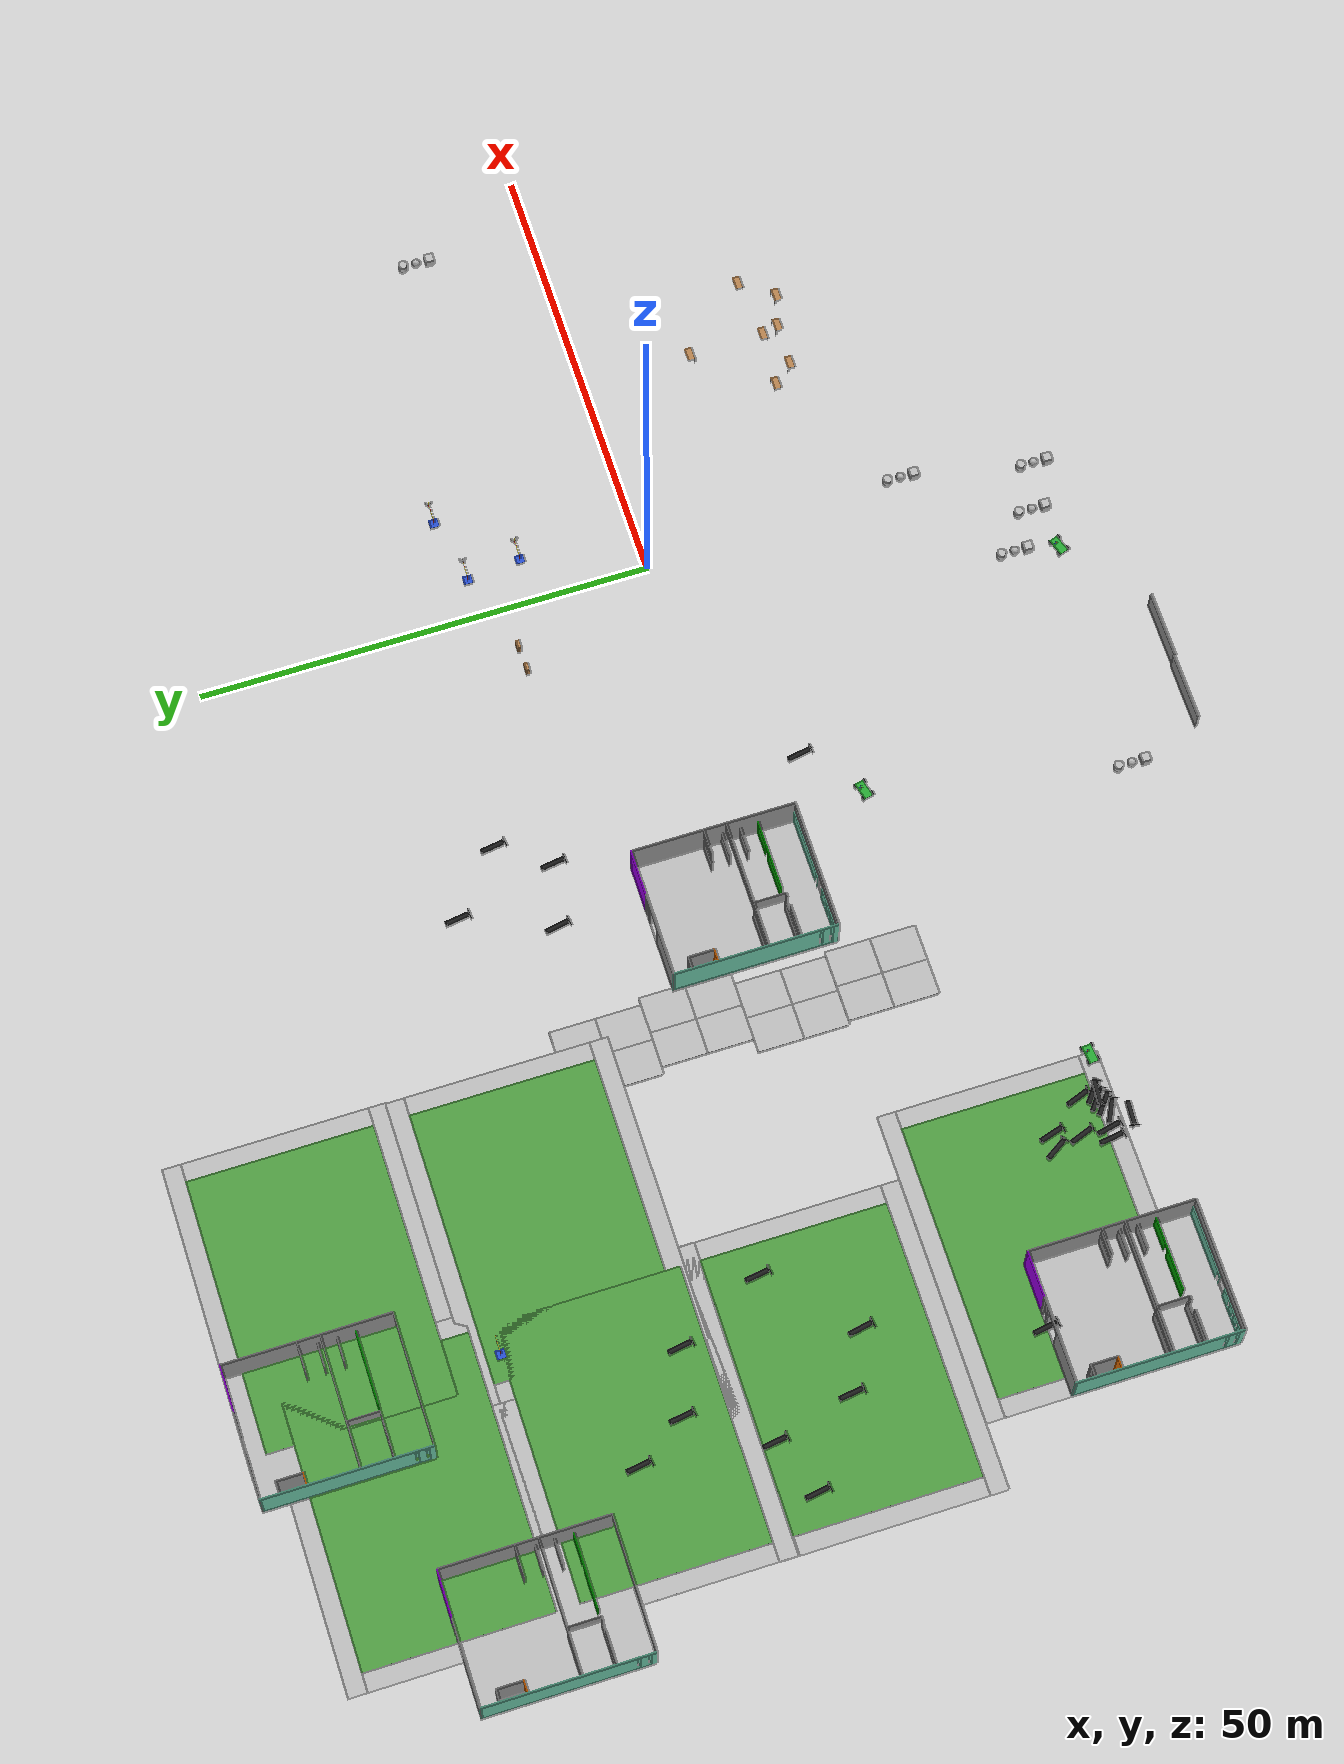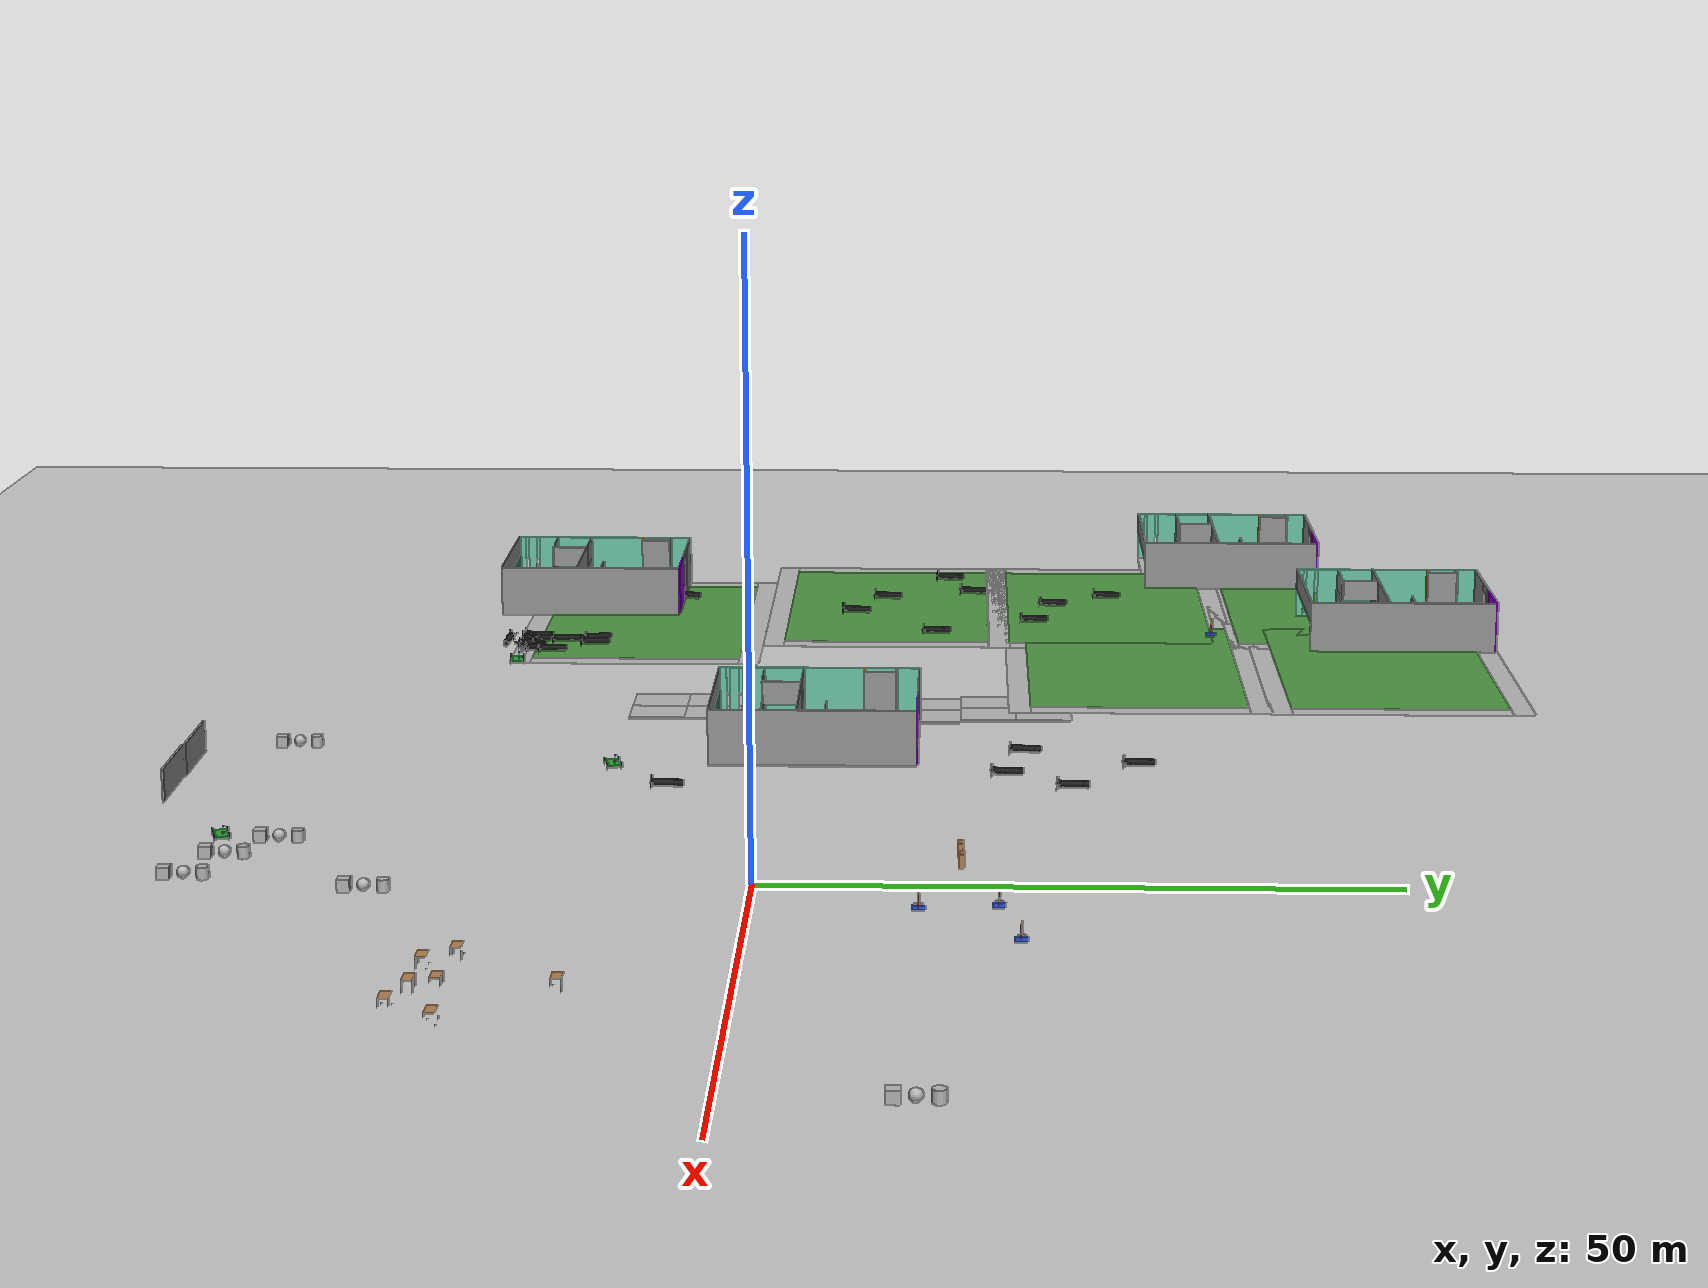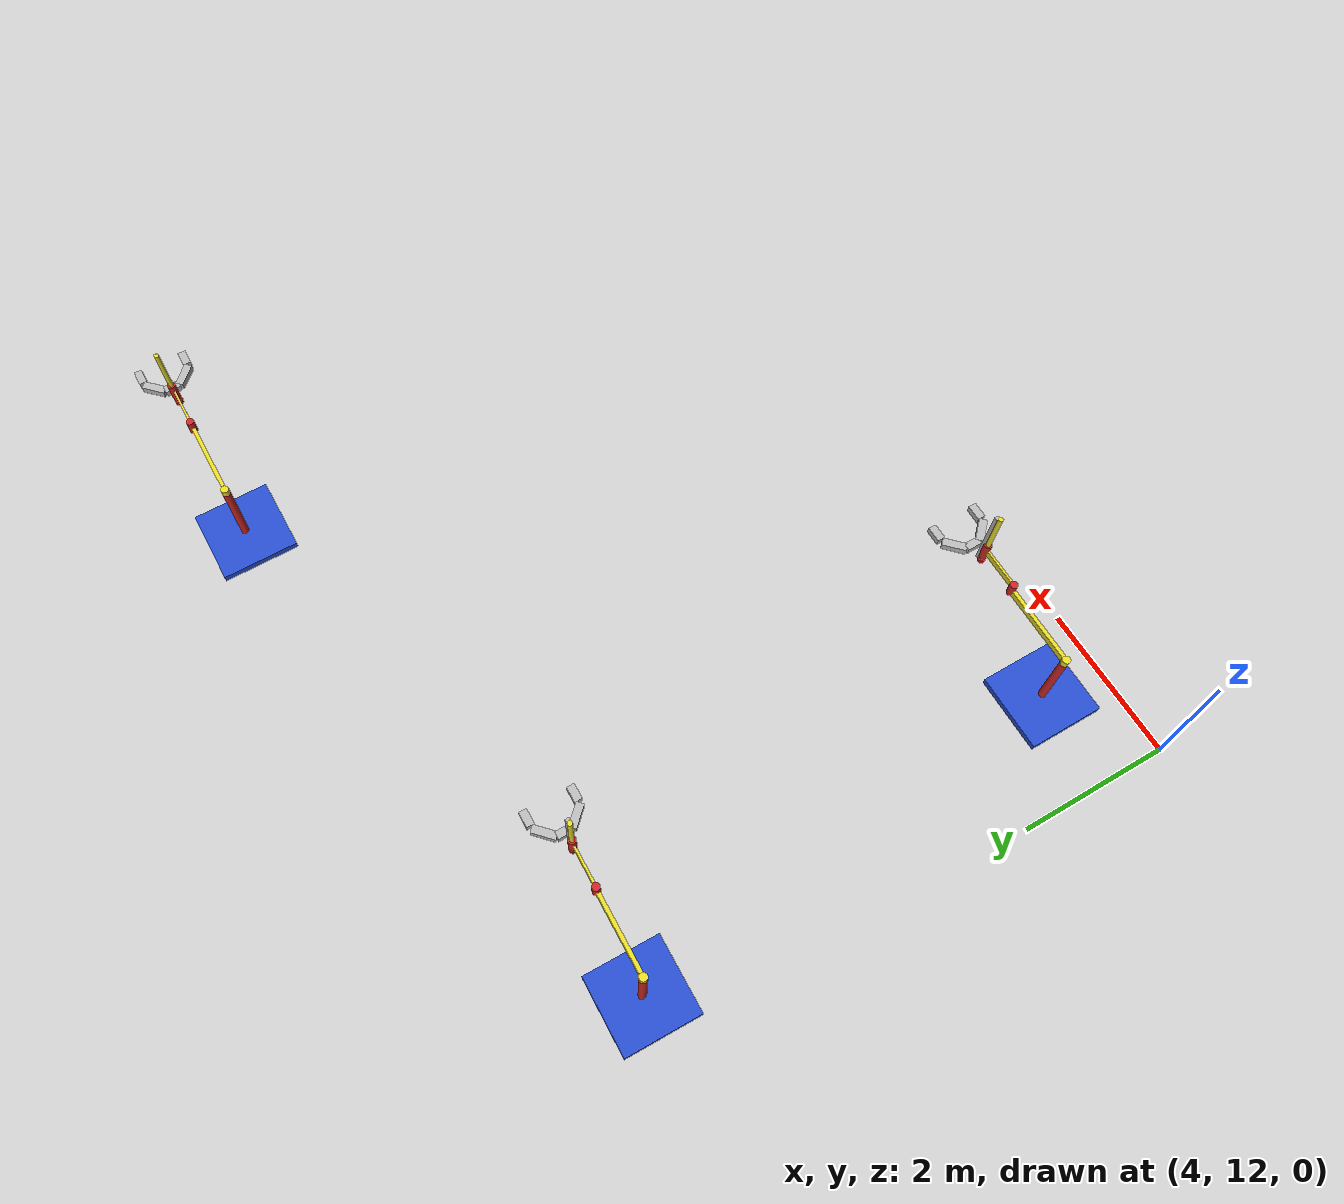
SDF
<sdf version="1.7">
 <world name="default">
  <light name="sun" type="directional">
   <pose>0 0 10 0 -0 0</pose>
   <diffuse>0.8 0.8 0.8 1</diffuse>
   <specular>0.2 0.2 0.2 1</specular>
   <attenuation>
    <range>1000</range>
    <constant>0.9</constant>
    <linear>0.01</linear>
    <quadratic>0.001</quadratic>
   </attenuation>
   <direction>-0.5 0.1 -0.9</direction>
   <spot><inner_angle>0</inner_angle><outer_angle>0</outer_angle><falloff>0</falloff></spot>
  </light>
  <model name="ground_plane">
   <static>1</static>
   <link name="link">
    <collision name="collision">
     <geometry><plane><normal>0 0 1</normal><size>100 100</size></plane></geometry>
     <surface><friction><ode><mu>100</mu><mu2>50</mu2></ode></friction></surface>
    </collision>
    <visual name="visual">
     <cast_shadows>0</cast_shadows>
     <geometry><plane><normal>0 0 1</normal><size>100 100</size></plane></geometry>
     <material>
      <script><uri>file://media/materials/scripts/gazebo.material</uri><name>Gazebo/Grey</name></script>
     </material>
    </visual>
   </link>
  </model>
  <gravity>0 0 -9.8</gravity>
  <magnetic_field>6e-06 2.3e-05 -4.2e-05</magnetic_field>
  <atmosphere type="adiabatic"/>
  <physics type="ode">
   <max_step_size>0.001</max_step_size>
   <real_time_factor>1</real_time_factor>
   <real_time_update_rate>1000</real_time_update_rate>
  </physics>
  <scene><ambient>0.4 0.4 0.4 1</ambient><background>0.7 0.7 0.7 1</background><shadows>1</shadows></scene>
  <audio><device>default</device></audio>
  <spherical_coordinates>
   <surface_model>EARTH_WGS84</surface_model>
   <latitude_deg>0</latitude_deg>
   <longitude_deg>0</longitude_deg>
   <elevation>0</elevation>
   <heading_deg>0</heading_deg>
  </spherical_coordinates>
  <model name="grey_wall">
   <static>1</static>
   <link name="link">
    <pose>0 0 1.4 0 -0 0</pose>
    <collision name="collision"><geometry><box><size>7.5 0.2 2.8</size></box></geometry></collision>
    <visual name="visual">
     <cast_shadows>0</cast_shadows>
     <geometry><box><size>7.5 0.2 2.8</size></box></geometry>
     <material>
      <script>
       <uri>model://grey_wall/materials/scripts</uri>
       <uri>model://grey_wall/materials/textures</uri>
       <name>vrc/grey_wall</name>
      </script>
     </material>
    </visual>
   </link>
   <pose>-31.7918 -49.8637 0 0 -0 0</pose>
  </model>
  <model name="grey_wall_0">
   <static>1</static>
   <link name="link">
    <pose>0 0 1.4 0 -0 0</pose>
    <collision name="collision"><geometry><box><size>7.5 0.2 2.8</size></box></geometry></collision>
    <visual name="visual">
     <cast_shadows>0</cast_shadows>
     <geometry><box><size>7.5 0.2 2.8</size></box></geometry>
     <material>
      <script>
       <uri>model://grey_wall/materials/scripts</uri>
       <uri>model://grey_wall/materials/textures</uri>
       <name>vrc/grey_wall</name>
      </script>
     </material>
    </visual>
   </link>
   <pose>-24.3097 -50.0185 0 0 -0 0</pose>
  </model>
  <model name="233333osrf_elevator">
   <link name="Wall_0">
    <pose>-7.17647 0.013004 0 0 -0 1.57174</pose>
    <visual name="Wall_0_Visual_1">
     <meta><layer>0</layer></meta>
     <pose>0.331828 0 0.25 0 -0 0</pose>
     <geometry><box><size>17.4519 0.15 0.5</size></box></geometry>
     <material>
      <script><uri>file://media/materials/scripts/gazebo.material</uri><name>Gazebo/Grey</name></script>
      <ambient>0.435294 0.796078 0.67451 1</ambient>
      <shader type="pixel"/>
     </material>
    </visual>
    <visual name="Wall_0_Visual_0">
     <meta><layer>0</layer></meta>
     <pose>-8.72596 0 2.4385 0 -0 0</pose>
     <geometry><box><size>0.663656 0.15 4.877</size></box></geometry>
     <material>
      <script><uri>file://media/materials/scripts/gazebo.material</uri><name>Gazebo/Grey</name></script>
      <ambient>0.435294 0.796078 0.67451 1</ambient>
      <shader type="pixel"/>
     </material>
    </visual>
    <visual name="Wall_0_Visual_2">
     <meta><layer>0</layer></meta>
     <pose>-7.67281 0 2.6885 0 -0 0</pose>
     <geometry><box><size>0.816657 0.15 4.377</size></box></geometry>
     <material>
      <script><uri>file://media/materials/scripts/gazebo.material</uri><name>Gazebo/Grey</name></script>
      <ambient>0.435294 0.796078 0.67451 1</ambient>
      <shader type="pixel"/>
     </material>
    </visual>
    <visual name="Wall_0_Visual_3">
     <meta><layer>0</layer></meta>
     <pose>1.05709 0 2.6885 0 -0 0</pose>
     <geometry><box><size>16.0014 0.15 4.377</size></box></geometry>
     <material>
      <script><uri>file://media/materials/scripts/gazebo.material</uri><name>Gazebo/Grey</name></script>
      <ambient>0.435294 0.796078 0.67451 1</ambient>
      <shader type="pixel"/>
     </material>
    </visual>
    <visual name="Wall_0_Visual_4">
     <meta><layer>0</layer></meta>
     <pose>-8.23763 0 3.6885 0 -0 0</pose>
     <geometry><box><size>0.313 0.15 2.377</size></box></geometry>
     <material>
      <script><uri>file://media/materials/scripts/gazebo.material</uri><name>Gazebo/Grey</name></script>
      <ambient>0.435294 0.796078 0.67451 1</ambient>
      <shader type="pixel"/>
     </material>
    </visual>
    <visual name="Wall_0_Visual_5">
     <meta><layer>0</layer></meta>
     <pose>-7.10405 0 3.6885 0 -0 0</pose>
     <geometry><box><size>0.320861 0.15 2.377</size></box></geometry>
     <material>
      <script><uri>file://media/materials/scripts/gazebo.material</uri><name>Gazebo/Grey</name></script>
      <ambient>0.435294 0.796078 0.67451 1</ambient>
      <shader type="pixel"/>
     </material>
    </visual>
    <collision name="Wall_0_Collision_0">
     <pose>-8.72596 0 2.4385 0 -0 0</pose>
     <geometry><box><size>0.663656 0.15 4.877</size></box></geometry>
     <surface>
      <friction>
       <ode><mu>1</mu><mu2>1</mu2><fdir1>0 0 0</fdir1><slip1>0</slip1><slip2>0</slip2></ode>
       <torsional>
        <coefficient>1</coefficient>
        <patch_radius>0</patch_radius>
        <surface_radius>0</surface_radius>
        <use_patch_radius>1</use_patch_radius>
        <ode><slip>0</slip></ode>
       </torsional>
      </friction>
      <bounce><restitution_coefficient>0</restitution_coefficient><threshold>1e+06</threshold></bounce>
      <contact>
       <collide_without_contact>0</collide_without_contact>
       <collide_without_contact_bitmask>1</collide_without_contact_bitmask>
       <collide_bitmask>1</collide_bitmask>
       <ode>
        <soft_cfm>0</soft_cfm>
        <soft_erp>0.2</soft_erp>
        <kp>1e+13</kp>
        <kd>1</kd>
        <max_vel>0.01</max_vel>
        <min_depth>0</min_depth>
       </ode>
       <bullet>
        <split_impulse>1</split_impulse>
        <split_impulse_penetration_threshold>-0.01</split_impulse_penetration_threshold>
        <soft_cfm>0</soft_cfm>
        <soft_erp>0.2</soft_erp>
        <kp>1e+13</kp>
        <kd>1</kd>
       </bullet>
      </contact>
     </surface>
    </collision>
    <collision name="Wall_0_Collision_5">
     <pose>-7.10405 0 3.6885 0 -0 0</pose>
     <geometry><box><size>0.320861 0.15 2.377</size></box></geometry>
     <surface>
      <friction>
       <ode><mu>1</mu><mu2>1</mu2><fdir1>0 0 0</fdir1><slip1>0</slip1><slip2>0</slip2></ode>
       <torsional>
        <coefficient>1</coefficient>
        <patch_radius>0</patch_radius>
        <surface_radius>0</surface_radius>
        <use_patch_radius>1</use_patch_radius>
        <ode><slip>0</slip></ode>
       </torsional>
      </friction>
      <bounce><restitution_coefficient>0</restitution_coefficient><threshold>1e+06</threshold></bounce>
      <contact>
       <collide_without_contact>0</collide_without_contact>
       <collide_without_contact_bitmask>1</collide_without_contact_bitmask>
       <collide_bitmask>1</collide_bitmask>
       <ode>
        <soft_cfm>0</soft_cfm>
        <soft_erp>0.2</soft_erp>
        <kp>1e+13</kp>
        <kd>1</kd>
        <max_vel>0.01</max_vel>
        <min_depth>0</min_depth>
       </ode>
       <bullet>
        <split_impulse>1</split_impulse>
        <split_impulse_penetration_threshold>-0.01</split_impulse_penetration_threshold>
        <soft_cfm>0</soft_cfm>
        <soft_erp>0.2</soft_erp>
        <kp>1e+13</kp>
        <kd>1</kd>
       </bullet>
      </contact>
     </surface>
    </collision>
    <collision name="Wall_0_Collision_1">
     <pose>0.331828 0 0.25 0 -0 0</pose>
     <geometry><box><size>17.4519 0.15 0.5</size></box></geometry>
     <surface>
      <friction>
       <ode><mu>1</mu><mu2>1</mu2><fdir1>0 0 0</fdir1><slip1>0</slip1><slip2>0</slip2></ode>
       <torsional>
        <coefficient>1</coefficient>
        <patch_radius>0</patch_radius>
        <surface_radius>0</surface_radius>
        <use_patch_radius>1</use_patch_radius>
        <ode><slip>0</slip></ode>
       </torsional>
      </friction>
      <bounce><restitution_coefficient>0</restitution_coefficient><threshold>1e+06</threshold></bounce>
      <contact>
       <collide_without_contact>0</collide_without_contact>
       <collide_without_contact_bitmask>1</collide_without_contact_bitmask>
       <collide_bitmask>1</collide_bitmask>
       <ode>
        <soft_cfm>0</soft_cfm>
        <soft_erp>0.2</soft_erp>
        <kp>1e+13</kp>
        <kd>1</kd>
        <max_vel>0.01</max_vel>
        <min_depth>0</min_depth>
       </ode>
       <bullet>
        <split_impulse>1</split_impulse>
        <split_impulse_penetration_threshold>-0.01</split_impulse_penetration_threshold>
        <soft_cfm>0</soft_cfm>
        <soft_erp>0.2</soft_erp>
        <kp>1e+13</kp>
        <kd>1</kd>
       </bullet>
      </contact>
     </surface>
    </collision>
    <collision name="Wall_0_Collision_2">
     <pose>-7.67281 0 2.6885 0 -0 0</pose>
     <geometry><box><size>0.816657 0.15 4.377</size></box></geometry>
     <surface>
      <friction>
       <ode><mu>1</mu><mu2>1</mu2><fdir1>0 0 0</fdir1><slip1>0</slip1><slip2>0</slip2></ode>
       <torsional>
        <coefficient>1</coefficient>
        <patch_radius>0</patch_radius>
        <surface_radius>0</surface_radius>
        <use_patch_radius>1</use_patch_radius>
        <ode><slip>0</slip></ode>
       </torsional>
      </friction>
      <bounce><restitution_coefficient>0</restitution_coefficient><threshold>1e+06</threshold></bounce>
      <contact>
       <collide_without_contact>0</collide_without_contact>
       <collide_without_contact_bitmask>1</collide_without_contact_bitmask>
       <collide_bitmask>1</collide_bitmask>
       <ode>
        <soft_cfm>0</soft_cfm>
        <soft_erp>0.2</soft_erp>
        <kp>1e+13</kp>
        <kd>1</kd>
        <max_vel>0.01</max_vel>
        <min_depth>0</min_depth>
       </ode>
       <bullet>
        <split_impulse>1</split_impulse>
        <split_impulse_penetration_threshold>-0.01</split_impulse_penetration_threshold>
        <soft_cfm>0</soft_cfm>
        <soft_erp>0.2</soft_erp>
        <kp>1e+13</kp>
        <kd>1</kd>
       </bullet>
      </contact>
     </surface>
    </collision>
    <collision name="Wall_0_Collision_3">
     <pose>1.05709 0 2.6885 0 -0 0</pose>
     <geometry><box><size>16.0014 0.15 4.377</size></box></geometry>
     <surface>
      <friction>
       <ode><mu>1</mu><mu2>1</mu2><fdir1>0 0 0</fdir1><slip1>0</slip1><slip2>0</slip2></ode>
       <torsional>
        <coefficient>1</coefficient>
        <patch_radius>0</patch_radius>
        <surface_radius>0</surface_radius>
        <use_patch_radius>1</use_patch_radius>
        <ode><slip>0</slip></ode>
       </torsional>
      </friction>
      <bounce><restitution_coefficient>0</restitution_coefficient><threshold>1e+06</threshold></bounce>
      <contact>
       <collide_without_contact>0</collide_without_contact>
       <collide_without_contact_bitmask>1</collide_without_contact_bitmask>
       <collide_bitmask>1</collide_bitmask>
       <ode>
        <soft_cfm>0</soft_cfm>
        <soft_erp>0.2</soft_erp>
        <kp>1e+13</kp>
        <kd>1</kd>
        <max_vel>0.01</max_vel>
        <min_depth>0</min_depth>
       </ode>
       <bullet>
        <split_impulse>1</split_impulse>
        <split_impulse_penetration_threshold>-0.01</split_impulse_penetration_threshold>
        <soft_cfm>0</soft_cfm>
        <soft_erp>0.2</soft_erp>
        <kp>1e+13</kp>
        <kd>1</kd>
       </bullet>
      </contact>
     </surface>
    </collision>
    <collision name="Wall_0_Collision_4">
     <pose>-8.23763 0 3.6885 0 -0 0</pose>
     <geometry><box><size>0.313 0.15 2.377</size></box></geometry>
     <surface>
      <friction>
       <ode><mu>1</mu><mu2>1</mu2><fdir1>0 0 0</fdir1><slip1>0</slip1><slip2>0</slip2></ode>
       <torsional>
        <coefficient>1</coefficient>
        <patch_radius>0</patch_radius>
        <surface_radius>0</surface_radius>
        <use_patch_radius>1</use_patch_radius>
        <ode><slip>0</slip></ode>
       </torsional>
      </friction>
      <bounce><restitution_coefficient>0</restitution_coefficient><threshold>1e+06</threshold></bounce>
      <contact>
       <collide_without_contact>0</collide_without_contact>
       <collide_without_contact_bitmask>1</collide_without_contact_bitmask>
       <collide_bitmask>1</collide_bitmask>
       <ode>
        <soft_cfm>0</soft_cfm>
        <soft_erp>0.2</soft_erp>
        <kp>1e+13</kp>
        <kd>1</kd>
        <max_vel>0.01</max_vel>
        <min_depth>0</min_depth>
       </ode>
       <bullet>
        <split_impulse>1</split_impulse>
        <split_impulse_penetration_threshold>-0.01</split_impulse_penetration_threshold>
        <soft_cfm>0</soft_cfm>
        <soft_erp>0.2</soft_erp>
        <kp>1e+13</kp>
        <kd>1</kd>
       </bullet>
      </contact>
     </surface>
    </collision>
   </link>
   <link name="Wall_10">
    <pose>3.11003 -4.9485 0 0 -0 0</pose>
    <visual name="Wall_10_Visual_0">
     <meta><layer>0</layer></meta>
     <pose>-1.73626 0 1.3715 0 -0 0</pose>
     <geometry><box><size>4.52747 0.15 2.743</size></box></geometry>
     <material>
      <script><uri>file://media/materials/scripts/gazebo.material</uri><name>Gazebo/Grey</name></script>
      <ambient>0 0.666667 0 1</ambient>
      <shader type="pixel"/>
     </material>
    </visual>
    <visual name="Wall_10_Visual_1">
     <meta><layer>0</layer></meta>
     <pose>2.58694 0 1.3715 0 -0 0</pose>
     <geometry><box><size>2.82611 0.15 2.743</size></box></geometry>
     <material>
      <script><uri>file://media/materials/scripts/gazebo.material</uri><name>Gazebo/Grey</name></script>
      <ambient>0 0.666667 0 1</ambient>
      <shader type="pixel"/>
     </material>
    </visual>
    <visual name="Wall_10_Visual_2">
     <meta><layer>0</layer></meta>
     <pose>0.85068 0 2.3715 0 -0 0</pose>
     <geometry><box><size>0.646413 0.15 0.743</size></box></geometry>
     <material>
      <script><uri>file://media/materials/scripts/gazebo.material</uri><name>Gazebo/Grey</name></script>
      <ambient>0 0.666667 0 1</ambient>
      <shader type="pixel"/>
     </material>
    </visual>
    <collision name="Wall_10_Collision_0">
     <pose>-1.73626 0 1.3715 0 -0 0</pose>
     <geometry><box><size>4.52747 0.15 2.743</size></box></geometry>
     <surface>
      <friction>
       <ode><mu>1</mu><mu2>1</mu2><fdir1>0 0 0</fdir1><slip1>0</slip1><slip2>0</slip2></ode>
       <torsional>
        <coefficient>1</coefficient>
        <patch_radius>0</patch_radius>
        <surface_radius>0</surface_radius>
        <use_patch_radius>1</use_patch_radius>
        <ode><slip>0</slip></ode>
       </torsional>
      </friction>
      <bounce><restitution_coefficient>0</restitution_coefficient><threshold>1e+06</threshold></bounce>
      <contact>
       <collide_without_contact>0</collide_without_contact>
       <collide_without_contact_bitmask>1</collide_without_contact_bitmask>
       <collide_bitmask>1</collide_bitmask>
       <ode>
        <soft_cfm>0</soft_cfm>
        <soft_erp>0.2</soft_erp>
        <kp>1e+13</kp>
        <kd>1</kd>
        <max_vel>0.01</max_vel>
        <min_depth>0</min_depth>
       </ode>
       <bullet>
        <split_impulse>1</split_impulse>
        <split_impulse_penetration_threshold>-0.01</split_impulse_penetration_threshold>
        <soft_cfm>0</soft_cfm>
        <soft_erp>0.2</soft_erp>
        <kp>1e+13</kp>
        <kd>1</kd>
       </bullet>
      </contact>
     </surface>
    </collision>
    <collision name="Wall_10_Collision_1">
     <pose>2.58694 0 1.3715 0 -0 0</pose>
     <geometry><box><size>2.82611 0.15 2.743</size></box></geometry>
     <surface>
      <friction>
       <ode><mu>1</mu><mu2>1</mu2><fdir1>0 0 0</fdir1><slip1>0</slip1><slip2>0</slip2></ode>
       <torsional>
        <coefficient>1</coefficient>
        <patch_radius>0</patch_radius>
        <surface_radius>0</surface_radius>
        <use_patch_radius>1</use_patch_radius>
        <ode><slip>0</slip></ode>
       </torsional>
      </friction>
      <bounce><restitution_coefficient>0</restitution_coefficient><threshold>1e+06</threshold></bounce>
      <contact>
       <collide_without_contact>0</collide_without_contact>
       <collide_without_contact_bitmask>1</collide_without_contact_bitmask>
       <collide_bitmask>1</collide_bitmask>
       <ode>
        <soft_cfm>0</soft_cfm>
        <soft_erp>0.2</soft_erp>
        <kp>1e+13</kp>
        <kd>1</kd>
        <max_vel>0.01</max_vel>
        <min_depth>0</min_depth>
       </ode>
       <bullet>
        <split_impulse>1</split_impulse>
        <split_impulse_penetration_threshold>-0.01</split_impulse_penetration_threshold>
        <soft_cfm>0</soft_cfm>
        <soft_erp>0.2</soft_erp>
        <kp>1e+13</kp>
        <kd>1</kd>
       </bullet>
      </contact>
     </surface>
    </collision>
    <collision name="Wall_10_Collision_2">
     <pose>0.85068 0 2.3715 0 -0 0</pose>
     <geometry><box><size>0.646413 0.15 0.743</size></box></geometry>
     <surface>
      <friction>
       <ode><mu>1</mu><mu2>1</mu2><fdir1>0 0 0</fdir1><slip1>0</slip1><slip2>0</slip2></ode>
       <torsional>
        <coefficient>1</coefficient>
        <patch_radius>0</patch_radius>
        <surface_radius>0</surface_radius>
        <use_patch_radius>1</use_patch_radius>
        <ode><slip>0</slip></ode>
       </torsional>
      </friction>
      <bounce><restitution_coefficient>0</restitution_coefficient><threshold>1e+06</threshold></bounce>
      <contact>
       <collide_without_contact>0</collide_without_contact>
       <collide_without_contact_bitmask>1</collide_without_contact_bitmask>
       <collide_bitmask>1</collide_bitmask>
       <ode>
        <soft_cfm>0</soft_cfm>
        <soft_erp>0.2</soft_erp>
        <kp>1e+13</kp>
        <kd>1</kd>
        <max_vel>0.01</max_vel>
        <min_depth>0</min_depth>
       </ode>
       <bullet>
        <split_impulse>1</split_impulse>
        <split_impulse_penetration_threshold>-0.01</split_impulse_penetration_threshold>
        <soft_cfm>0</soft_cfm>
        <soft_erp>0.2</soft_erp>
        <kp>1e+13</kp>
        <kd>1</kd>
       </bullet>
      </contact>
     </surface>
    </collision>
   </link>
   <link name="Wall_16">
    <pose>-4.68247 -1.4425 0 0 -0 0</pose>
    <visual name="Wall_16_Visual">
     <meta><layer>0</layer></meta>
     <pose>0 0 1.3715 0 -0 0</pose>
     <geometry><box><size>5.12727 0.15 2.743</size></box></geometry>
     <material>
      <script><uri>file://media/materials/scripts/gazebo.material</uri><name>Gazebo/Grey</name></script>
      <ambient>1 1 1 1</ambient>
      <shader type="pixel"/>
     </material>
    </visual>
    <collision name="Wall_16_Collision">
     <pose>0 0 1.3715 0 -0 0</pose>
     <geometry><box><size>5.12727 0.15 2.743</size></box></geometry>
     <surface>
      <friction>
       <ode><mu>1</mu><mu2>1</mu2><fdir1>0 0 0</fdir1><slip1>0</slip1><slip2>0</slip2></ode>
       <torsional>
        <coefficient>1</coefficient>
        <patch_radius>0</patch_radius>
        <surface_radius>0</surface_radius>
        <use_patch_radius>1</use_patch_radius>
        <ode><slip>0</slip></ode>
       </torsional>
      </friction>
      <bounce><restitution_coefficient>0</restitution_coefficient><threshold>1e+06</threshold></bounce>
      <contact>
       <collide_without_contact>0</collide_without_contact>
       <collide_without_contact_bitmask>1</collide_without_contact_bitmask>
       <collide_bitmask>1</collide_bitmask>
       <ode>
        <soft_cfm>0</soft_cfm>
        <soft_erp>0.2</soft_erp>
        <kp>1e+13</kp>
        <kd>1</kd>
        <max_vel>0.01</max_vel>
        <min_depth>0</min_depth>
       </ode>
       <bullet>
        <split_impulse>1</split_impulse>
        <split_impulse_penetration_threshold>-0.01</split_impulse_penetration_threshold>
        <soft_cfm>0</soft_cfm>
        <soft_erp>0.2</soft_erp>
        <kp>1e+13</kp>
        <kd>1</kd>
       </bullet>
      </contact>
     </surface>
    </collision>
   </link>
   <link name="Wall_18">
    <pose>-4.61297 -4.9275 0 0 -0 3.14159</pose>
    <visual name="Wall_18_Visual">
     <meta><layer>0</layer></meta>
     <pose>0 0 1.3715 0 -0 0</pose>
     <geometry><box><size>5 0.15 2.743</size></box></geometry>
     <material>
      <script><uri>file://media/materials/scripts/gazebo.material</uri><name>Gazebo/Grey</name></script>
      <ambient>1 1 1 1</ambient>
      <shader type="pixel"/>
     </material>
    </visual>
    <collision name="Wall_18_Collision">
     <pose>0 0 1.3715 0 -0 0</pose>
     <geometry><box><size>5 0.15 2.743</size></box></geometry>
     <surface>
      <friction>
       <ode><mu>1</mu><mu2>1</mu2><fdir1>0 0 0</fdir1><slip1>0</slip1><slip2>0</slip2></ode>
       <torsional>
        <coefficient>1</coefficient>
        <patch_radius>0</patch_radius>
        <surface_radius>0</surface_radius>
        <use_patch_radius>1</use_patch_radius>
        <ode><slip>0</slip></ode>
       </torsional>
      </friction>
      <bounce><restitution_coefficient>0</restitution_coefficient><threshold>1e+06</threshold></bounce>
      <contact>
       <collide_without_contact>0</collide_without_contact>
       <collide_without_contact_bitmask>1</collide_without_contact_bitmask>
       <collide_bitmask>1</collide_bitmask>
       <ode>
        <soft_cfm>0</soft_cfm>
        <soft_erp>0.2</soft_erp>
        <kp>1e+13</kp>
        <kd>1</kd>
        <max_vel>0.01</max_vel>
        <min_depth>0</min_depth>
       </ode>
       <bullet>
        <split_impulse>1</split_impulse>
        <split_impulse_penetration_threshold>-0.01</split_impulse_penetration_threshold>
        <soft_cfm>0</soft_cfm>
        <soft_erp>0.2</soft_erp>
        <kp>1e+13</kp>
        <kd>1</kd>
       </bullet>
      </contact>
     </surface>
    </collision>
   </link>
   <link name="Wall_20">
    <pose>5.74253 1.037 0 0 0 -3.1383</pose>
    <visual name="Wall_20_Visual">
     <meta><layer>0</layer></meta>
     <pose>0 0 1.3715 0 -0 0</pose>
     <geometry><box><size>2.88731 0.15 2.743</size></box></geometry>
     <material>
      <script><uri>file://media/materials/scripts/gazebo.material</uri><name>Gazebo/Grey</name></script>
      <ambient>1 1 1 1</ambient>
      <shader type="pixel"/>
     </material>
    </visual>
    <collision name="Wall_20_Collision">
     <pose>0 0 1.3715 0 -0 0</pose>
     <geometry><box><size>2.88731 0.15 2.743</size></box></geometry>
     <surface>
      <friction>
       <ode><mu>1</mu><mu2>1</mu2><fdir1>0 0 0</fdir1><slip1>0</slip1><slip2>0</slip2></ode>
       <torsional>
        <coefficient>1</coefficient>
        <patch_radius>0</patch_radius>
        <surface_radius>0</surface_radius>
        <use_patch_radius>1</use_patch_radius>
        <ode><slip>0</slip></ode>
       </torsional>
      </friction>
      <bounce><restitution_coefficient>0</restitution_coefficient><threshold>1e+06</threshold></bounce>
      <contact>
       <collide_without_contact>0</collide_without_contact>
       <collide_without_contact_bitmask>1</collide_without_contact_bitmask>
       <collide_bitmask>1</collide_bitmask>
       <ode>
        <soft_cfm>0</soft_cfm>
        <soft_erp>0.2</soft_erp>
        <kp>1e+13</kp>
        <kd>1</kd>
        <max_vel>0.01</max_vel>
        <min_depth>0</min_depth>
       </ode>
       <bullet>
        <split_impulse>1</split_impulse>
        <split_impulse_penetration_threshold>-0.01</split_impulse_penetration_threshold>
        <soft_cfm>0</soft_cfm>
        <soft_erp>0.2</soft_erp>
        <kp>1e+13</kp>
        <kd>1</kd>
       </bullet>
      </contact>
     </surface>
    </collision>
   </link>
   <link name="Wall_23">
    <pose>5.74203 -2.9565 0 0 -0 0</pose>
    <visual name="Wall_23_Visual">
     <meta><layer>0</layer></meta>
     <pose>0 0 1.3715 0 -0 0</pose>
     <geometry><box><size>2.75 0.15 2.743</size></box></geometry>
     <material>
      <script><uri>file://media/materials/scripts/gazebo.material</uri><name>Gazebo/Grey</name></script>
      <ambient>1 1 1 1</ambient>
      <shader type="pixel"/>
     </material>
    </visual>
    <collision name="Wall_23_Collision">
     <pose>0 0 1.3715 0 -0 0</pose>
     <geometry><box><size>2.75 0.15 2.743</size></box></geometry>
     <surface>
      <friction>
       <ode><mu>1</mu><mu2>1</mu2><fdir1>0 0 0</fdir1><slip1>0</slip1><slip2>0</slip2></ode>
       <torsional>
        <coefficient>1</coefficient>
        <patch_radius>0</patch_radius>
        <surface_radius>0</surface_radius>
        <use_patch_radius>1</use_patch_radius>
        <ode><slip>0</slip></ode>
       </torsional>
      </friction>
      <bounce><restitution_coefficient>0</restitution_coefficient><threshold>1e+06</threshold></bounce>
      <contact>
       <collide_without_contact>0</collide_without_contact>
       <collide_without_contact_bitmask>1</collide_without_contact_bitmask>
       <collide_bitmask>1</collide_bitmask>
       <ode>
        <soft_cfm>0</soft_cfm>
        <soft_erp>0.2</soft_erp>
        <kp>1e+13</kp>
        <kd>1</kd>
        <max_vel>0.01</max_vel>
        <min_depth>0</min_depth>
       </ode>
       <bullet>
        <split_impulse>1</split_impulse>
        <split_impulse_penetration_threshold>-0.01</split_impulse_penetration_threshold>
        <soft_cfm>0</soft_cfm>
        <soft_erp>0.2</soft_erp>
        <kp>1e+13</kp>
        <kd>1</kd>
       </bullet>
      </contact>
     </surface>
    </collision>
   </link>
   <link name="Wall_25">
    <pose>5.76203 -0.932495 0 0 -0 0</pose>
    <visual name="Wall_25_Visual">
     <meta><layer>0</layer></meta>
     <pose>0 0 1.3715 0 -0 0</pose>
     <geometry><box><size>2.75 0.15 2.743</size></box></geometry>
     <material>
      <script><uri>file://media/materials/scripts/gazebo.material</uri><name>Gazebo/Grey</name></script>
      <ambient>1 1 1 1</ambient>
      <shader type="pixel"/>
     </material>
    </visual>
    <collision name="Wall_25_Collision">
     <pose>0 0 1.3715 0 -0 0</pose>
     <geometry><box><size>2.75 0.15 2.743</size></box></geometry>
     <surface>
      <friction>
       <ode><mu>1</mu><mu2>1</mu2><fdir1>0 0 0</fdir1><slip1>0</slip1><slip2>0</slip2></ode>
       <torsional>
        <coefficient>1</coefficient>
        <patch_radius>0</patch_radius>
        <surface_radius>0</surface_radius>
        <use_patch_radius>1</use_patch_radius>
        <ode><slip>0</slip></ode>
       </torsional>
      </friction>
      <bounce><restitution_coefficient>0</restitution_coefficient><threshold>1e+06</threshold></bounce>
      <contact>
       <collide_without_contact>0</collide_without_contact>
       <collide_without_contact_bitmask>1</collide_without_contact_bitmask>
       <collide_bitmask>1</collide_bitmask>
       <ode>
        <soft_cfm>0</soft_cfm>
        <soft_erp>0.2</soft_erp>
        <kp>1e+13</kp>
        <kd>1</kd>
        <max_vel>0.01</max_vel>
        <min_depth>0</min_depth>
       </ode>
       <bullet>
        <split_impulse>1</split_impulse>
        <split_impulse_penetration_threshold>-0.01</split_impulse_penetration_threshold>
        <soft_cfm>0</soft_cfm>
        <soft_erp>0.2</soft_erp>
        <kp>1e+13</kp>
        <kd>1</kd>
       </bullet>
      </contact>
     </surface>
    </collision>
   </link>
   <link name="Wall_29">
    <pose>-6.49697 4.1045 0 0 -0 0</pose>
    <visual name="Wall_29_Visual">
     <meta><layer>0</layer></meta>
     <pose>0 0 2.4385 0 -0 0</pose>
     <geometry><box><size>1.39187 0.15 4.877</size></box></geometry>
     <material>
      <script><uri>file://media/materials/scripts/gazebo.material</uri><name>Gazebo/Grey</name></script>
      <ambient>0.996078 0.47451 0.0196078 1</ambient>
      <shader type="pixel"/>
     </material>
    </visual>
    <collision name="Wall_29_Collision">
     <pose>0 0 2.4385 0 -0 0</pose>
     <geometry><box><size>1.39187 0.15 4.877</size></box></geometry>
     <surface>
      <friction>
       <ode><mu>1</mu><mu2>1</mu2><fdir1>0 0 0</fdir1><slip1>0</slip1><slip2>0</slip2></ode>
       <torsional>
        <coefficient>1</coefficient>
        <patch_radius>0</patch_radius>
        <surface_radius>0</surface_radius>
        <use_patch_radius>1</use_patch_radius>
        <ode><slip>0</slip></ode>
       </torsional>
      </friction>
      <bounce><restitution_coefficient>0</restitution_coefficient><threshold>1e+06</threshold></bounce>
      <contact>
       <collide_without_contact>0</collide_without_contact>
       <collide_without_contact_bitmask>1</collide_without_contact_bitmask>
       <collide_bitmask>1</collide_bitmask>
       <ode>
        <soft_cfm>0</soft_cfm>
        <soft_erp>0.2</soft_erp>
        <kp>1e+13</kp>
        <kd>1</kd>
        <max_vel>0.01</max_vel>
        <min_depth>0</min_depth>
       </ode>
       <bullet>
        <split_impulse>1</split_impulse>
        <split_impulse_penetration_threshold>-0.01</split_impulse_penetration_threshold>
        <soft_cfm>0</soft_cfm>
        <soft_erp>0.2</soft_erp>
        <kp>1e+13</kp>
        <kd>1</kd>
       </bullet>
      </contact>
     </surface>
    </collision>
   </link>
   <link name="Wall_30">
    <pose>-5.87597 5.5295 0 0 -0 1.5708</pose>
    <visual name="Wall_30_Visual">
     <meta><layer>0</layer></meta>
     <pose>0 0 2.4385 0 -0 0</pose>
     <geometry><box><size>3 0.15 4.877</size></box></geometry>
     <material>
      <script><uri>file://media/materials/scripts/gazebo.material</uri><name>Gazebo/Grey</name></script>
      <ambient>1 1 1 1</ambient>
      <shader type="pixel"/>
     </material>
    </visual>
    <collision name="Wall_30_Collision">
     <pose>0 0 2.4385 0 -0 0</pose>
     <geometry><box><size>3 0.15 4.877</size></box></geometry>
     <surface>
      <friction>
       <ode><mu>1</mu><mu2>1</mu2><fdir1>0 0 0</fdir1><slip1>0</slip1><slip2>0</slip2></ode>
       <torsional>
        <coefficient>1</coefficient>
        <patch_radius>0</patch_radius>
        <surface_radius>0</surface_radius>
        <use_patch_radius>1</use_patch_radius>
        <ode><slip>0</slip></ode>
       </torsional>
      </friction>
      <bounce><restitution_coefficient>0</restitution_coefficient><threshold>1e+06</threshold></bounce>
      <contact>
       <collide_without_contact>0</collide_without_contact>
       <collide_without_contact_bitmask>1</collide_without_contact_bitmask>
       <collide_bitmask>1</collide_bitmask>
       <ode>
        <soft_cfm>0</soft_cfm>
        <soft_erp>0.2</soft_erp>
        <kp>1e+13</kp>
        <kd>1</kd>
        <max_vel>0.01</max_vel>
        <min_depth>0</min_depth>
       </ode>
       <bullet>
        <split_impulse>1</split_impulse>
        <split_impulse_penetration_threshold>-0.01</split_impulse_penetration_threshold>
        <soft_cfm>0</soft_cfm>
        <soft_erp>0.2</soft_erp>
        <kp>1e+13</kp>
        <kd>1</kd>
       </bullet>
      </contact>
     </surface>
    </collision>
   </link>
   <link name="Wall_31">
    <pose>-6.50397 6.9525 0 0 0 -3.13841</pose>
    <visual name="Wall_31_Visual_0">
     <meta><layer>0</layer></meta>
     <pose>-0.567544 0 2.4385 0 -0 0</pose>
     <geometry><box><size>0.271575 0.15 4.877</size></box></geometry>
     <material>
      <script><uri>file://media/materials/scripts/gazebo.material</uri><name>Gazebo/Grey</name></script>
      <ambient>1 1 1 1</ambient>
      <shader type="pixel"/>
     </material>
    </visual>
    <visual name="Wall_31_Visual_1">
     <meta><layer>0</layer></meta>
     <pose>0.441678 0 2.4385 0 -0 0</pose>
     <geometry><box><size>0.523307 0.15 4.877</size></box></geometry>
     <material>
      <script><uri>file://media/materials/scripts/gazebo.material</uri><name>Gazebo/Grey</name></script>
      <ambient>1 1 1 1</ambient>
      <shader type="pixel"/>
     </material>
    </visual>
    <visual name="Wall_31_Visual_3">
     <meta><layer>0</layer></meta>
     <pose>-0.125866 0 3.4385 0 -0 0</pose>
     <geometry><box><size>0.611781 0.15 2.877</size></box></geometry>
     <material>
      <script><uri>file://media/materials/scripts/gazebo.material</uri><name>Gazebo/Grey</name></script>
      <ambient>1 1 1 1</ambient>
      <shader type="pixel"/>
     </material>
    </visual>
    <collision name="Wall_31_Collision_0">
     <pose>-0.567544 0 2.4385 0 -0 0</pose>
     <geometry><box><size>0.271575 0.15 4.877</size></box></geometry>
     <surface>
      <friction>
       <ode><mu>1</mu><mu2>1</mu2><fdir1>0 0 0</fdir1><slip1>0</slip1><slip2>0</slip2></ode>
       <torsional>
        <coefficient>1</coefficient>
        <patch_radius>0</patch_radius>
        <surface_radius>0</surface_radius>
        <use_patch_radius>1</use_patch_radius>
        <ode><slip>0</slip></ode>
       </torsional>
      </friction>
      <bounce><restitution_coefficient>0</restitution_coefficient><threshold>1e+06</threshold></bounce>
      <contact>
       <collide_without_contact>0</collide_without_contact>
       <collide_without_contact_bitmask>1</collide_without_contact_bitmask>
       <collide_bitmask>1</collide_bitmask>
       <ode>
        <soft_cfm>0</soft_cfm>
        <soft_erp>0.2</soft_erp>
        <kp>1e+13</kp>
        <kd>1</kd>
        <max_vel>0.01</max_vel>
        <min_depth>0</min_depth>
       </ode>
       <bullet>
        <split_impulse>1</split_impulse>
        <split_impulse_penetration_threshold>-0.01</split_impulse_penetration_threshold>
        <soft_cfm>0</soft_cfm>
        <soft_erp>0.2</soft_erp>
        <kp>1e+13</kp>
        <kd>1</kd>
       </bullet>
      </contact>
     </surface>
    </collision>
    <collision name="Wall_31_Collision_1">
     <pose>0.441678 0 2.4385 0 -0 0</pose>
     <geometry><box><size>0.523307 0.15 4.877</size></box></geometry>
     <surface>
      <friction>
       <ode><mu>1</mu><mu2>1</mu2><fdir1>0 0 0</fdir1><slip1>0</slip1><slip2>0</slip2></ode>
       <torsional>
        <coefficient>1</coefficient>
        <patch_radius>0</patch_radius>
        <surface_radius>0</surface_radius>
        <use_patch_radius>1</use_patch_radius>
        <ode><slip>0</slip></ode>
       </torsional>
      </friction>
      <bounce><restitution_coefficient>0</restitution_coefficient><threshold>1e+06</threshold></bounce>
      <contact>
       <collide_without_contact>0</collide_without_contact>
       <collide_without_contact_bitmask>1</collide_without_contact_bitmask>
       <collide_bitmask>1</collide_bitmask>
       <ode>
        <soft_cfm>0</soft_cfm>
        <soft_erp>0.2</soft_erp>
        <kp>1e+13</kp>
        <kd>1</kd>
        <max_vel>0.01</max_vel>
        <min_depth>0</min_depth>
       </ode>
       <bullet>
        <split_impulse>1</split_impulse>
        <split_impulse_penetration_threshold>-0.01</split_impulse_penetration_threshold>
        <soft_cfm>0</soft_cfm>
        <soft_erp>0.2</soft_erp>
        <kp>1e+13</kp>
        <kd>1</kd>
       </bullet>
      </contact>
     </surface>
    </collision>
    <collision name="Wall_31_Collision_3">
     <pose>-0.125866 0 3.4385 0 -0 0</pose>
     <geometry><box><size>0.611781 0.15 2.877</size></box></geometry>
     <surface>
      <friction>
       <ode><mu>1</mu><mu2>1</mu2><fdir1>0 0 0</fdir1><slip1>0</slip1><slip2>0</slip2></ode>
       <torsional>
        <coefficient>1</coefficient>
        <patch_radius>0</patch_radius>
        <surface_radius>0</surface_radius>
        <use_patch_radius>1</use_patch_radius>
        <ode><slip>0</slip></ode>
       </torsional>
      </friction>
      <bounce><restitution_coefficient>0</restitution_coefficient><threshold>1e+06</threshold></bounce>
      <contact>
       <collide_without_contact>0</collide_without_contact>
       <collide_without_contact_bitmask>1</collide_without_contact_bitmask>
       <collide_bitmask>1</collide_bitmask>
       <ode>
        <soft_cfm>0</soft_cfm>
        <soft_erp>0.2</soft_erp>
        <kp>1e+13</kp>
        <kd>1</kd>
        <max_vel>0.01</max_vel>
        <min_depth>0</min_depth>
       </ode>
       <bullet>
        <split_impulse>1</split_impulse>
        <split_impulse_penetration_threshold>-0.01</split_impulse_penetration_threshold>
        <soft_cfm>0</soft_cfm>
        <soft_erp>0.2</soft_erp>
        <kp>1e+13</kp>
        <kd>1</kd>
       </bullet>
      </contact>
     </surface>
    </collision>
   </link>
   <link name="Wall_35">
    <pose>-2.50997 8.9955 0 0 -0 0</pose>
    <visual name="Wall_35_Visual_0">
     <meta><layer>0</layer></meta>
     <pose>-1.92197 0 2.4385 0 -0 0</pose>
     <geometry><box><size>5.65606 0.15 4.877</size></box></geometry>
     <material>
      <script><uri>file://media/materials/scripts/gazebo.material</uri><name>Gazebo/Grey</name></script>
      <ambient>1 1 1 1</ambient>
      <shader type="pixel"/>
     </material>
    </visual>
    <visual name="Wall_35_Visual_1">
     <meta><layer>0</layer></meta>
     <pose>3.22541 0 2.4385 0 -0 0</pose>
     <geometry><box><size>0.406701 0.15 4.877</size></box></geometry>
     <material>
      <script><uri>file://media/materials/scripts/gazebo.material</uri><name>Gazebo/Grey</name></script>
      <ambient>1 1 1 1</ambient>
      <shader type="pixel"/>
     </material>
    </visual>
    <visual name="Wall_35_Visual_2">
     <meta><layer>0</layer></meta>
     <pose>4.40208 0 2.4385 0 -0 0</pose>
     <geometry><box><size>0.695843 0.15 4.877</size></box></geometry>
     <material>
      <script><uri>file://media/materials/scripts/gazebo.material</uri><name>Gazebo/Grey</name></script>
      <ambient>1 1 1 1</ambient>
      <shader type="pixel"/>
     </material>
    </visual>
    <visual name="Wall_35_Visual_5">
     <meta><layer>0</layer></meta>
     <pose>3.74146 0 3.4385 0 -0 0</pose>
     <geometry><box><size>0.625391 0.15 2.877</size></box></geometry>
     <material>
      <script><uri>file://media/materials/scripts/gazebo.material</uri><name>Gazebo/Grey</name></script>
      <ambient>1 1 1 1</ambient>
      <shader type="pixel"/>
     </material>
    </visual>
    <visual name="Wall_35_Visual_6">
     <meta><layer>0</layer></meta>
     <pose>1.96406 0 4.4385 0 -0 0</pose>
     <geometry><box><size>2.116 0.15 0.877</size></box></geometry>
     <material>
      <script><uri>file://media/materials/scripts/gazebo.material</uri><name>Gazebo/Grey</name></script>
      <ambient>1 1 1 1</ambient>
      <shader type="pixel"/>
     </material>
    </visual>
    <collision name="Wall_35_Collision_0">
     <pose>-1.92197 0 2.4385 0 -0 0</pose>
     <geometry><box><size>5.65606 0.15 4.877</size></box></geometry>
     <surface>
      <friction>
       <ode><mu>1</mu><mu2>1</mu2><fdir1>0 0 0</fdir1><slip1>0</slip1><slip2>0</slip2></ode>
       <torsional>
        <coefficient>1</coefficient>
        <patch_radius>0</patch_radius>
        <surface_radius>0</surface_radius>
        <use_patch_radius>1</use_patch_radius>
        <ode><slip>0</slip></ode>
       </torsional>
      </friction>
      <bounce><restitution_coefficient>0</restitution_coefficient><threshold>1e+06</threshold></bounce>
      <contact>
       <collide_without_contact>0</collide_without_contact>
       <collide_without_contact_bitmask>1</collide_without_contact_bitmask>
       <collide_bitmask>1</collide_bitmask>
       <ode>
        <soft_cfm>0</soft_cfm>
        <soft_erp>0.2</soft_erp>
        <kp>1e+13</kp>
        <kd>1</kd>
        <max_vel>0.01</max_vel>
        <min_depth>0</min_depth>
       </ode>
       <bullet>
        <split_impulse>1</split_impulse>
        <split_impulse_penetration_threshold>-0.01</split_impulse_penetration_threshold>
        <soft_cfm>0</soft_cfm>
        <soft_erp>0.2</soft_erp>
        <kp>1e+13</kp>
        <kd>1</kd>
       </bullet>
      </contact>
     </surface>
    </collision>
    <collision name="Wall_35_Collision_1">
     <pose>3.22541 0 2.4385 0 -0 0</pose>
     <geometry><box><size>0.406701 0.15 4.877</size></box></geometry>
     <surface>
      <friction>
       <ode><mu>1</mu><mu2>1</mu2><fdir1>0 0 0</fdir1><slip1>0</slip1><slip2>0</slip2></ode>
       <torsional>
        <coefficient>1</coefficient>
        <patch_radius>0</patch_radius>
        <surface_radius>0</surface_radius>
        <use_patch_radius>1</use_patch_radius>
        <ode><slip>0</slip></ode>
       </torsional>
      </friction>
      <bounce><restitution_coefficient>0</restitution_coefficient><threshold>1e+06</threshold></bounce>
      <contact>
       <collide_without_contact>0</collide_without_contact>
       <collide_without_contact_bitmask>1</collide_without_contact_bitmask>
       <collide_bitmask>1</collide_bitmask>
       <ode>
        <soft_cfm>0</soft_cfm>
        <soft_erp>0.2</soft_erp>
        <kp>1e+13</kp>
        <kd>1</kd>
        <max_vel>0.01</max_vel>
        <min_depth>0</min_depth>
       </ode>
       <bullet>
        <split_impulse>1</split_impulse>
        <split_impulse_penetration_threshold>-0.01</split_impulse_penetration_threshold>
        <soft_cfm>0</soft_cfm>
        <soft_erp>0.2</soft_erp>
        <kp>1e+13</kp>
        <kd>1</kd>
       </bullet>
      </contact>
     </surface>
    </collision>
    <collision name="Wall_35_Collision_2">
     <pose>4.40208 0 2.4385 0 -0 0</pose>
     <geometry><box><size>0.695843 0.15 4.877</size></box></geometry>
     <surface>
      <friction>
       <ode><mu>1</mu><mu2>1</mu2><fdir1>0 0 0</fdir1><slip1>0</slip1><slip2>0</slip2></ode>
       <torsional>
        <coefficient>1</coefficient>
        <patch_radius>0</patch_radius>
        <surface_radius>0</surface_radius>
        <use_patch_radius>1</use_patch_radius>
        <ode><slip>0</slip></ode>
       </torsional>
      </friction>
      <bounce><restitution_coefficient>0</restitution_coefficient><threshold>1e+06</threshold></bounce>
      <contact>
       <collide_without_contact>0</collide_without_contact>
       <collide_without_contact_bitmask>1</collide_without_contact_bitmask>
       <collide_bitmask>1</collide_bitmask>
       <ode>
        <soft_cfm>0</soft_cfm>
        <soft_erp>0.2</soft_erp>
        <kp>1e+13</kp>
        <kd>1</kd>
        <max_vel>0.01</max_vel>
        <min_depth>0</min_depth>
       </ode>
       <bullet>
        <split_impulse>1</split_impulse>
        <split_impulse_penetration_threshold>-0.01</split_impulse_penetration_threshold>
        <soft_cfm>0</soft_cfm>
        <soft_erp>0.2</soft_erp>
        <kp>1e+13</kp>
        <kd>1</kd>
       </bullet>
      </contact>
     </surface>
    </collision>
    <collision name="Wall_35_Collision_5">
     <pose>3.74146 0 3.4385 0 -0 0</pose>
     <geometry><box><size>0.625391 0.15 2.877</size></box></geometry>
     <surface>
      <friction>
       <ode><mu>1</mu><mu2>1</mu2><fdir1>0 0 0</fdir1><slip1>0</slip1><slip2>0</slip2></ode>
       <torsional>
        <coefficient>1</coefficient>
        <patch_radius>0</patch_radius>
        <surface_radius>0</surface_radius>
        <use_patch_radius>1</use_patch_radius>
        <ode><slip>0</slip></ode>
       </torsional>
      </friction>
      <bounce><restitution_coefficient>0</restitution_coefficient><threshold>1e+06</threshold></bounce>
      <contact>
       <collide_without_contact>0</collide_without_contact>
       <collide_without_contact_bitmask>1</collide_without_contact_bitmask>
       <collide_bitmask>1</collide_bitmask>
       <ode>
        <soft_cfm>0</soft_cfm>
        <soft_erp>0.2</soft_erp>
        <kp>1e+13</kp>
        <kd>1</kd>
        <max_vel>0.01</max_vel>
        <min_depth>0</min_depth>
       </ode>
       <bullet>
        <split_impulse>1</split_impulse>
        <split_impulse_penetration_threshold>-0.01</split_impulse_penetration_threshold>
        <soft_cfm>0</soft_cfm>
        <soft_erp>0.2</soft_erp>
        <kp>1e+13</kp>
        <kd>1</kd>
       </bullet>
      </contact>
     </surface>
    </collision>
    <collision name="Wall_35_Collision_6">
     <pose>1.96406 0 4.4385 0 -0 0</pose>
     <geometry><box><size>2.116 0.15 0.877</size></box></geometry>
     <surface>
      <friction>
       <ode><mu>1</mu><mu2>1</mu2><fdir1>0 0 0</fdir1><slip1>0</slip1><slip2>0</slip2></ode>
       <torsional>
        <coefficient>1</coefficient>
        <patch_radius>0</patch_radius>
        <surface_radius>0</surface_radius>
        <use_patch_radius>1</use_patch_radius>
        <ode><slip>0</slip></ode>
       </torsional>
      </friction>
      <bounce><restitution_coefficient>0</restitution_coefficient><threshold>1e+06</threshold></bounce>
      <contact>
       <collide_without_contact>0</collide_without_contact>
       <collide_without_contact_bitmask>1</collide_without_contact_bitmask>
       <collide_bitmask>1</collide_bitmask>
       <ode>
        <soft_cfm>0</soft_cfm>
        <soft_erp>0.2</soft_erp>
        <kp>1e+13</kp>
        <kd>1</kd>
        <max_vel>0.01</max_vel>
        <min_depth>0</min_depth>
       </ode>
       <bullet>
        <split_impulse>1</split_impulse>
        <split_impulse_penetration_threshold>-0.01</split_impulse_penetration_threshold>
        <soft_cfm>0</soft_cfm>
        <soft_erp>0.2</soft_erp>
        <kp>1e+13</kp>
        <kd>1</kd>
       </bullet>
      </contact>
     </surface>
    </collision>
   </link>
   <link name="Wall_36">
    <pose>4.67503 8.9955 0 0 -0 0</pose>
    <visual name="Wall_36_Visual">
     <meta><layer>0</layer></meta>
     <pose>0 0 2.4385 0 -0 0</pose>
     <geometry><box><size>5.17 0.15 4.877</size></box></geometry>
     <material>
      <script><uri>file://media/materials/scripts/gazebo.material</uri><name>Gazebo/Grey</name></script>
      <ambient>0.666667 0 1 1</ambient>
      <shader type="pixel"/>
     </material>
    </visual>
    <collision name="Wall_36_Collision">
     <pose>0 0 2.4385 0 -0 0</pose>
     <geometry><box><size>5.17 0.15 4.877</size></box></geometry>
     <surface>
      <friction>
       <ode><mu>1</mu><mu2>1</mu2><fdir1>0 0 0</fdir1><slip1>0</slip1><slip2>0</slip2></ode>
       <torsional>
        <coefficient>1</coefficient>
        <patch_radius>0</patch_radius>
        <surface_radius>0</surface_radius>
        <use_patch_radius>1</use_patch_radius>
        <ode><slip>0</slip></ode>
       </torsional>
      </friction>
      <bounce><restitution_coefficient>0</restitution_coefficient><threshold>1e+06</threshold></bounce>
      <contact>
       <collide_without_contact>0</collide_without_contact>
       <collide_without_contact_bitmask>1</collide_without_contact_bitmask>
       <collide_bitmask>1</collide_bitmask>
       <ode>
        <soft_cfm>0</soft_cfm>
        <soft_erp>0.2</soft_erp>
        <kp>1e+13</kp>
        <kd>1</kd>
        <max_vel>0.01</max_vel>
        <min_depth>0</min_depth>
       </ode>
       <bullet>
        <split_impulse>1</split_impulse>
        <split_impulse_penetration_threshold>-0.01</split_impulse_penetration_threshold>
        <soft_cfm>0</soft_cfm>
        <soft_erp>0.2</soft_erp>
        <kp>1e+13</kp>
        <kd>1</kd>
       </bullet>
      </contact>
     </surface>
    </collision>
   </link>
   <link name="Wall_5">
    <pose>7.18353 0.013004 0 0 0 -1.57096</pose>
    <visual name="Wall_5_Visual">
     <meta><layer>0</layer></meta>
     <pose>0 0 2.4385 0 -0 0</pose>
     <geometry><box><size>18.1152 0.15 4.877</size></box></geometry>
     <material>
      <script><uri>file://media/materials/scripts/gazebo.material</uri><name>Gazebo/Grey</name></script>
      <ambient>1 1 1 1</ambient>
      <shader type="pixel"/>
     </material>
    </visual>
    <collision name="Wall_5_Collision">
     <pose>0 0 2.4385 0 -0 0</pose>
     <geometry><box><size>18.1152 0.15 4.877</size></box></geometry>
     <surface>
      <friction>
       <ode><mu>1</mu><mu2>1</mu2><fdir1>0 0 0</fdir1><slip1>0</slip1><slip2>0</slip2></ode>
       <torsional>
        <coefficient>1</coefficient>
        <patch_radius>0</patch_radius>
        <surface_radius>0</surface_radius>
        <use_patch_radius>1</use_patch_radius>
        <ode><slip>0</slip></ode>
       </torsional>
      </friction>
      <bounce><restitution_coefficient>0</restitution_coefficient><threshold>1e+06</threshold></bounce>
      <contact>
       <collide_without_contact>0</collide_without_contact>
       <collide_without_contact_bitmask>1</collide_without_contact_bitmask>
       <collide_bitmask>1</collide_bitmask>
       <ode>
        <soft_cfm>0</soft_cfm>
        <soft_erp>0.2</soft_erp>
        <kp>1e+13</kp>
        <kd>1</kd>
        <max_vel>0.01</max_vel>
        <min_depth>0</min_depth>
       </ode>
       <bullet>
        <split_impulse>1</split_impulse>
        <split_impulse_penetration_threshold>-0.01</split_impulse_penetration_threshold>
        <soft_cfm>0</soft_cfm>
        <soft_erp>0.2</soft_erp>
        <kp>1e+13</kp>
        <kd>1</kd>
       </bullet>
      </contact>
     </surface>
    </collision>
   </link>
   <link name="Wall_6">
    <pose>0.00703 -8.9695 0 0 -0 3.14159</pose>
    <visual name="Wall_6_Visual_0">
     <meta><layer>0</layer></meta>
     <pose>-3.60425 0 1.365 0 -0 0</pose>
     <geometry><box><size>7.2915 0.15 2.73</size></box></geometry>
     <material>
      <script><uri>file://media/materials/scripts/gazebo.material</uri><name>Gazebo/Grey</name></script>
      <ambient>0.435294 0.796078 0.67451 1</ambient>
      <shader type="pixel"/>
     </material>
    </visual>
    <visual name="Wall_6_Visual_1">
     <meta><layer>0</layer></meta>
     <pose>0.726241 0 1.365 0 -0 0</pose>
     <geometry><box><size>0.056893 0.15 2.73</size></box></geometry>
     <material>
      <script><uri>file://media/materials/scripts/gazebo.material</uri><name>Gazebo/Grey</name></script>
      <ambient>0.435294 0.796078 0.67451 1</ambient>
      <shader type="pixel"/>
     </material>
    </visual>
    <visual name="Wall_6_Visual_4">
     <meta><layer>0</layer></meta>
     <pose>5.24871 0 0.25 0 -0 0</pose>
     <geometry><box><size>4.00258 0.15 0.5</size></box></geometry>
     <material>
      <script><uri>file://media/materials/scripts/gazebo.material</uri><name>Gazebo/Grey</name></script>
      <ambient>0.435294 0.796078 0.67451 1</ambient>
      <shader type="pixel"/>
     </material>
    </visual>
    <visual name="Wall_6_Visual_2">
     <meta><layer>0</layer></meta>
     <pose>2.65105 0 1.365 0 -0 0</pose>
     <geometry><box><size>1.19273 0.15 2.73</size></box></geometry>
     <material>
      <script><uri>file://media/materials/scripts/gazebo.material</uri><name>Gazebo/Grey</name></script>
      <ambient>0.435294 0.796078 0.67451 1</ambient>
      <shader type="pixel"/>
     </material>
    </visual>
    <visual name="Wall_6_Visual_5">
     <meta><layer>0</layer></meta>
     <pose>4.0419 0 1.615 0 -0 0</pose>
     <geometry><box><size>0.828969 0.15 2.23</size></box></geometry>
     <material>
      <script><uri>file://media/materials/scripts/gazebo.material</uri><name>Gazebo/Grey</name></script>
      <ambient>0.435294 0.796078 0.67451 1</ambient>
      <shader type="pixel"/>
     </material>
    </visual>
    <visual name="Wall_6_Visual_6">
     <meta><layer>0</layer></meta>
     <pose>5.18099 0 1.615 0 -0 0</pose>
     <geometry><box><size>0.819207 0.15 2.23</size></box></geometry>
     <material>
      <script><uri>file://media/materials/scripts/gazebo.material</uri><name>Gazebo/Grey</name></script>
      <ambient>0.435294 0.796078 0.67451 1</ambient>
      <shader type="pixel"/>
     </material>
    </visual>
    <visual name="Wall_6_Visual_7">
     <meta><layer>0</layer></meta>
     <pose>6.58056 0 1.615 0 -0 0</pose>
     <geometry><box><size>1.33888 0.15 2.23</size></box></geometry>
     <material>
      <script><uri>file://media/materials/scripts/gazebo.material</uri><name>Gazebo/Grey</name></script>
      <ambient>0.435294 0.796078 0.67451 1</ambient>
      <shader type="pixel"/>
     </material>
    </visual>
    <visual name="Wall_6_Visual_8">
     <meta><layer>0</layer></meta>
     <pose>0.369648 0 2.365 0 -0 0</pose>
     <geometry><box><size>0.656294 0.15 0.73</size></box></geometry>
     <material>
      <script><uri>file://media/materials/scripts/gazebo.material</uri><name>Gazebo/Grey</name></script>
      <ambient>0.435294 0.796078 0.67451 1</ambient>
      <shader type="pixel"/>
     </material>
    </visual>
    <visual name="Wall_6_Visual_9">
     <meta><layer>0</layer></meta>
     <pose>3.43742 0 2.615 0 -0 0</pose>
     <geometry><box><size>0.38 0.15 0.23</size></box></geometry>
     <material>
      <script><uri>file://media/materials/scripts/gazebo.material</uri><name>Gazebo/Grey</name></script>
      <ambient>0.435294 0.796078 0.67451 1</ambient>
      <shader type="pixel"/>
     </material>
    </visual>
    <visual name="Wall_6_Visual_10">
     <meta><layer>0</layer></meta>
     <pose>4.61389 0 2.615 0 -0 0</pose>
     <geometry><box><size>0.315 0.15 0.23</size></box></geometry>
     <material>
      <script><uri>file://media/materials/scripts/gazebo.material</uri><name>Gazebo/Grey</name></script>
      <ambient>0.435294 0.796078 0.67451 1</ambient>
      <shader type="pixel"/>
     </material>
    </visual>
    <visual name="Wall_6_Visual_11">
     <meta><layer>0</layer></meta>
     <pose>5.75086 0 2.615 0 -0 0</pose>
     <geometry><box><size>0.320532 0.15 0.23</size></box></geometry>
     <material>
      <script><uri>file://media/materials/scripts/gazebo.material</uri><name>Gazebo/Grey</name></script>
      <ambient>0.435294 0.796078 0.67451 1</ambient>
      <shader type="pixel"/>
     </material>
    </visual>
    <collision name="Wall_6_Collision_0">
     <pose>-3.60425 0 1.365 0 -0 0</pose>
     <geometry><box><size>7.2915 0.15 2.73</size></box></geometry>
     <surface>
      <friction>
       <ode><mu>1</mu><mu2>1</mu2><fdir1>0 0 0</fdir1><slip1>0</slip1><slip2>0</slip2></ode>
       <torsional>
        <coefficient>1</coefficient>
        <patch_radius>0</patch_radius>
        <surface_radius>0</surface_radius>
        <use_patch_radius>1</use_patch_radius>
        <ode><slip>0</slip></ode>
       </torsional>
      </friction>
      <bounce><restitution_coefficient>0</restitution_coefficient><threshold>1e+06</threshold></bounce>
      <contact>
       <collide_without_contact>0</collide_without_contact>
       <collide_without_contact_bitmask>1</collide_without_contact_bitmask>
       <collide_bitmask>1</collide_bitmask>
       <ode>
        <soft_cfm>0</soft_cfm>
        <soft_erp>0.2</soft_erp>
        <kp>1e+13</kp>
        <kd>1</kd>
        <max_vel>0.01</max_vel>
        <min_depth>0</min_depth>
       </ode>
       <bullet>
        <split_impulse>1</split_impulse>
        <split_impulse_penetration_threshold>-0.01</split_impulse_penetration_threshold>
        <soft_cfm>0</soft_cfm>
        <soft_erp>0.2</soft_erp>
        <kp>1e+13</kp>
        <kd>1</kd>
       </bullet>
      </contact>
     </surface>
    </collision>
    <collision name="Wall_6_Collision_1">
     <pose>0.726241 0 1.365 0 -0 0</pose>
     <geometry><box><size>0.056893 0.15 2.73</size></box></geometry>
     <surface>
      <friction>
       <ode><mu>1</mu><mu2>1</mu2><fdir1>0 0 0</fdir1><slip1>0</slip1><slip2>0</slip2></ode>
       <torsional>
        <coefficient>1</coefficient>
        <patch_radius>0</patch_radius>
        <surface_radius>0</surface_radius>
        <use_patch_radius>1</use_patch_radius>
        <ode><slip>0</slip></ode>
       </torsional>
      </friction>
      <bounce><restitution_coefficient>0</restitution_coefficient><threshold>1e+06</threshold></bounce>
      <contact>
       <collide_without_contact>0</collide_without_contact>
       <collide_without_contact_bitmask>1</collide_without_contact_bitmask>
       <collide_bitmask>1</collide_bitmask>
       <ode>
        <soft_cfm>0</soft_cfm>
        <soft_erp>0.2</soft_erp>
        <kp>1e+13</kp>
        <kd>1</kd>
        <max_vel>0.01</max_vel>
        <min_depth>0</min_depth>
       </ode>
       <bullet>
        <split_impulse>1</split_impulse>
        <split_impulse_penetration_threshold>-0.01</split_impulse_penetration_threshold>
        <soft_cfm>0</soft_cfm>
        <soft_erp>0.2</soft_erp>
        <kp>1e+13</kp>
        <kd>1</kd>
       </bullet>
      </contact>
     </surface>
    </collision>
    <collision name="Wall_6_Collision_2">
     <pose>2.65105 0 1.365 0 -0 0</pose>
     <geometry><box><size>1.19273 0.15 2.73</size></box></geometry>
     <surface>
      <friction>
       <ode><mu>1</mu><mu2>1</mu2><fdir1>0 0 0</fdir1><slip1>0</slip1><slip2>0</slip2></ode>
       <torsional>
        <coefficient>1</coefficient>
        <patch_radius>0</patch_radius>
        <surface_radius>0</surface_radius>
        <use_patch_radius>1</use_patch_radius>
        <ode><slip>0</slip></ode>
       </torsional>
      </friction>
      <bounce><restitution_coefficient>0</restitution_coefficient><threshold>1e+06</threshold></bounce>
      <contact>
       <collide_without_contact>0</collide_without_contact>
       <collide_without_contact_bitmask>1</collide_without_contact_bitmask>
       <collide_bitmask>1</collide_bitmask>
       <ode>
        <soft_cfm>0</soft_cfm>
        <soft_erp>0.2</soft_erp>
        <kp>1e+13</kp>
        <kd>1</kd>
        <max_vel>0.01</max_vel>
        <min_depth>0</min_depth>
       </ode>
       <bullet>
        <split_impulse>1</split_impulse>
        <split_impulse_penetration_threshold>-0.01</split_impulse_penetration_threshold>
        <soft_cfm>0</soft_cfm>
        <soft_erp>0.2</soft_erp>
        <kp>1e+13</kp>
        <kd>1</kd>
       </bullet>
      </contact>
     </surface>
    </collision>
    <collision name="Wall_6_Collision_4">
     <pose>5.24871 0 0.25 0 -0 0</pose>
     <geometry><box><size>4.00258 0.15 0.5</size></box></geometry>
     <surface>
      <friction>
       <ode><mu>1</mu><mu2>1</mu2><fdir1>0 0 0</fdir1><slip1>0</slip1><slip2>0</slip2></ode>
       <torsional>
        <coefficient>1</coefficient>
        <patch_radius>0</patch_radius>
        <surface_radius>0</surface_radius>
        <use_patch_radius>1</use_patch_radius>
        <ode><slip>0</slip></ode>
       </torsional>
      </friction>
      <bounce><restitution_coefficient>0</restitution_coefficient><threshold>1e+06</threshold></bounce>
      <contact>
       <collide_without_contact>0</collide_without_contact>
       <collide_without_contact_bitmask>1</collide_without_contact_bitmask>
       <collide_bitmask>1</collide_bitmask>
       <ode>
        <soft_cfm>0</soft_cfm>
        <soft_erp>0.2</soft_erp>
        <kp>1e+13</kp>
        <kd>1</kd>
        <max_vel>0.01</max_vel>
        <min_depth>0</min_depth>
       </ode>
       <bullet>
        <split_impulse>1</split_impulse>
        <split_impulse_penetration_threshold>-0.01</split_impulse_penetration_threshold>
        <soft_cfm>0</soft_cfm>
        <soft_erp>0.2</soft_erp>
        <kp>1e+13</kp>
        <kd>1</kd>
       </bullet>
      </contact>
     </surface>
    </collision>
    <collision name="Wall_6_Collision_5">
     <pose>4.0419 0 1.615 0 -0 0</pose>
     <geometry><box><size>0.828969 0.15 2.23</size></box></geometry>
     <surface>
      <friction>
       <ode><mu>1</mu><mu2>1</mu2><fdir1>0 0 0</fdir1><slip1>0</slip1><slip2>0</slip2></ode>
       <torsional>
        <coefficient>1</coefficient>
        <patch_radius>0</patch_radius>
        <surface_radius>0</surface_radius>
        <use_patch_radius>1</use_patch_radius>
        <ode><slip>0</slip></ode>
       </torsional>
      </friction>
      <bounce><restitution_coefficient>0</restitution_coefficient><threshold>1e+06</threshold></bounce>
      <contact>
       <collide_without_contact>0</collide_without_contact>
       <collide_without_contact_bitmask>1</collide_without_contact_bitmask>
       <collide_bitmask>1</collide_bitmask>
       <ode>
        <soft_cfm>0</soft_cfm>
        <soft_erp>0.2</soft_erp>
        <kp>1e+13</kp>
        <kd>1</kd>
        <max_vel>0.01</max_vel>
        <min_depth>0</min_depth>
       </ode>
       <bullet>
        <split_impulse>1</split_impulse>
        <split_impulse_penetration_threshold>-0.01</split_impulse_penetration_threshold>
        <soft_cfm>0</soft_cfm>
        <soft_erp>0.2</soft_erp>
        <kp>1e+13</kp>
        <kd>1</kd>
       </bullet>
      </contact>
     </surface>
    </collision>
    <collision name="Wall_6_Collision_6">
     <pose>5.18099 0 1.615 0 -0 0</pose>
     <geometry><box><size>0.819207 0.15 2.23</size></box></geometry>
     <surface>
      <friction>
       <ode><mu>1</mu><mu2>1</mu2><fdir1>0 0 0</fdir1><slip1>0</slip1><slip2>0</slip2></ode>
       <torsional>
        <coefficient>1</coefficient>
        <patch_radius>0</patch_radius>
        <surface_radius>0</surface_radius>
        <use_patch_radius>1</use_patch_radius>
        <ode><slip>0</slip></ode>
       </torsional>
      </friction>
      <bounce><restitution_coefficient>0</restitution_coefficient><threshold>1e+06</threshold></bounce>
      <contact>
       <collide_without_contact>0</collide_without_contact>
       <collide_without_contact_bitmask>1</collide_without_contact_bitmask>
       <collide_bitmask>1</collide_bitmask>
       <ode>
        <soft_cfm>0</soft_cfm>
        <soft_erp>0.2</soft_erp>
        <kp>1e+13</kp>
        <kd>1</kd>
        <max_vel>0.01</max_vel>
        <min_depth>0</min_depth>
       </ode>
       <bullet>
        <split_impulse>1</split_impulse>
        <split_impulse_penetration_threshold>-0.01</split_impulse_penetration_threshold>
        <soft_cfm>0</soft_cfm>
        <soft_erp>0.2</soft_erp>
        <kp>1e+13</kp>
        <kd>1</kd>
       </bullet>
      </contact>
     </surface>
    </collision>
    <collision name="Wall_6_Collision_8">
     <pose>0.369648 0 2.365 0 -0 0</pose>
     <geometry><box><size>0.656294 0.15 0.73</size></box></geometry>
     <surface>
      <friction>
       <ode><mu>1</mu><mu2>1</mu2><fdir1>0 0 0</fdir1><slip1>0</slip1><slip2>0</slip2></ode>
       <torsional>
        <coefficient>1</coefficient>
        <patch_radius>0</patch_radius>
        <surface_radius>0</surface_radius>
        <use_patch_radius>1</use_patch_radius>
        <ode><slip>0</slip></ode>
       </torsional>
      </friction>
      <bounce><restitution_coefficient>0</restitution_coefficient><threshold>1e+06</threshold></bounce>
      <contact>
       <collide_without_contact>0</collide_without_contact>
       <collide_without_contact_bitmask>1</collide_without_contact_bitmask>
       <collide_bitmask>1</collide_bitmask>
       <ode>
        <soft_cfm>0</soft_cfm>
        <soft_erp>0.2</soft_erp>
        <kp>1e+13</kp>
        <kd>1</kd>
        <max_vel>0.01</max_vel>
        <min_depth>0</min_depth>
       </ode>
       <bullet>
        <split_impulse>1</split_impulse>
        <split_impulse_penetration_threshold>-0.01</split_impulse_penetration_threshold>
        <soft_cfm>0</soft_cfm>
        <soft_erp>0.2</soft_erp>
        <kp>1e+13</kp>
        <kd>1</kd>
       </bullet>
      </contact>
     </surface>
    </collision>
    <collision name="Wall_6_Collision_7">
     <pose>6.58056 0 1.615 0 -0 0</pose>
     <geometry><box><size>1.33888 0.15 2.23</size></box></geometry>
     <surface>
      <friction>
       <ode><mu>1</mu><mu2>1</mu2><fdir1>0 0 0</fdir1><slip1>0</slip1><slip2>0</slip2></ode>
       <torsional>
        <coefficient>1</coefficient>
        <patch_radius>0</patch_radius>
        <surface_radius>0</surface_radius>
        <use_patch_radius>1</use_patch_radius>
        <ode><slip>0</slip></ode>
       </torsional>
      </friction>
      <bounce><restitution_coefficient>0</restitution_coefficient><threshold>1e+06</threshold></bounce>
      <contact>
       <collide_without_contact>0</collide_without_contact>
       <collide_without_contact_bitmask>1</collide_without_contact_bitmask>
       <collide_bitmask>1</collide_bitmask>
       <ode>
        <soft_cfm>0</soft_cfm>
        <soft_erp>0.2</soft_erp>
        <kp>1e+13</kp>
        <kd>1</kd>
        <max_vel>0.01</max_vel>
        <min_depth>0</min_depth>
       </ode>
       <bullet>
        <split_impulse>1</split_impulse>
        <split_impulse_penetration_threshold>-0.01</split_impulse_penetration_threshold>
        <soft_cfm>0</soft_cfm>
        <soft_erp>0.2</soft_erp>
        <kp>1e+13</kp>
        <kd>1</kd>
       </bullet>
      </contact>
     </surface>
    </collision>
    <collision name="Wall_6_Collision_9">
     <pose>3.43742 0 2.615 0 -0 0</pose>
     <geometry><box><size>0.38 0.15 0.23</size></box></geometry>
     <surface>
      <friction>
       <ode><mu>1</mu><mu2>1</mu2><fdir1>0 0 0</fdir1><slip1>0</slip1><slip2>0</slip2></ode>
       <torsional>
        <coefficient>1</coefficient>
        <patch_radius>0</patch_radius>
        <surface_radius>0</surface_radius>
        <use_patch_radius>1</use_patch_radius>
        <ode><slip>0</slip></ode>
       </torsional>
      </friction>
      <bounce><restitution_coefficient>0</restitution_coefficient><threshold>1e+06</threshold></bounce>
      <contact>
       <collide_without_contact>0</collide_without_contact>
       <collide_without_contact_bitmask>1</collide_without_contact_bitmask>
       <collide_bitmask>1</collide_bitmask>
       <ode>
        <soft_cfm>0</soft_cfm>
        <soft_erp>0.2</soft_erp>
        <kp>1e+13</kp>
        <kd>1</kd>
        <max_vel>0.01</max_vel>
        <min_depth>0</min_depth>
       </ode>
       <bullet>
        <split_impulse>1</split_impulse>
        <split_impulse_penetration_threshold>-0.01</split_impulse_penetration_threshold>
        <soft_cfm>0</soft_cfm>
        <soft_erp>0.2</soft_erp>
        <kp>1e+13</kp>
        <kd>1</kd>
       </bullet>
      </contact>
     </surface>
    </collision>
    <collision name="Wall_6_Collision_10">
     <pose>4.61389 0 2.615 0 -0 0</pose>
     <geometry><box><size>0.315 0.15 0.23</size></box></geometry>
     <surface>
      <friction>
       <ode><mu>1</mu><mu2>1</mu2><fdir1>0 0 0</fdir1><slip1>0</slip1><slip2>0</slip2></ode>
       <torsional>
        <coefficient>1</coefficient>
        <patch_radius>0</patch_radius>
        <surface_radius>0</surface_radius>
        <use_patch_radius>1</use_patch_radius>
        <ode><slip>0</slip></ode>
       </torsional>
      </friction>
      <bounce><restitution_coefficient>0</restitution_coefficient><threshold>1e+06</threshold></bounce>
      <contact>
       <collide_without_contact>0</collide_without_contact>
       <collide_without_contact_bitmask>1</collide_without_contact_bitmask>
       <collide_bitmask>1</collide_bitmask>
       <ode>
        <soft_cfm>0</soft_cfm>
        <soft_erp>0.2</soft_erp>
        <kp>1e+13</kp>
        <kd>1</kd>
        <max_vel>0.01</max_vel>
        <min_depth>0</min_depth>
       </ode>
       <bullet>
        <split_impulse>1</split_impulse>
        <split_impulse_penetration_threshold>-0.01</split_impulse_penetration_threshold>
        <soft_cfm>0</soft_cfm>
        <soft_erp>0.2</soft_erp>
        <kp>1e+13</kp>
        <kd>1</kd>
       </bullet>
      </contact>
     </surface>
    </collision>
    <collision name="Wall_6_Collision_11">
     <pose>5.75086 0 2.615 0 -0 0</pose>
     <geometry><box><size>0.320532 0.15 0.23</size></box></geometry>
     <surface>
      <friction>
       <ode><mu>1</mu><mu2>1</mu2><fdir1>0 0 0</fdir1><slip1>0</slip1><slip2>0</slip2></ode>
       <torsional>
        <coefficient>1</coefficient>
        <patch_radius>0</patch_radius>
        <surface_radius>0</surface_radius>
        <use_patch_radius>1</use_patch_radius>
        <ode><slip>0</slip></ode>
       </torsional>
      </friction>
      <bounce><restitution_coefficient>0</restitution_coefficient><threshold>1e+06</threshold></bounce>
      <contact>
       <collide_without_contact>0</collide_without_contact>
       <collide_without_contact_bitmask>1</collide_without_contact_bitmask>
       <collide_bitmask>1</collide_bitmask>
       <ode>
        <soft_cfm>0</soft_cfm>
        <soft_erp>0.2</soft_erp>
        <kp>1e+13</kp>
        <kd>1</kd>
        <max_vel>0.01</max_vel>
        <min_depth>0</min_depth>
       </ode>
       <bullet>
        <split_impulse>1</split_impulse>
        <split_impulse_penetration_threshold>-0.01</split_impulse_penetration_threshold>
        <soft_cfm>0</soft_cfm>
        <soft_erp>0.2</soft_erp>
        <kp>1e+13</kp>
        <kd>1</kd>
       </bullet>
      </contact>
     </surface>
    </collision>
   </link>
   <link name="floor1_part10">
    <pose>-2.39225 -4.89435 3.85794 1.5708 -0 0</pose>
    <visual name="visual">
     <meta><layer>1</layer></meta>
     <geometry><box><size>0.519866 2.0998 0.078</size></box></geometry>
     <material><script><name>Gazebo/Grey</name><uri>__default__</uri></script><shader type="pixel"/></material>
    </visual>
    <collision name="collision">
     <geometry><box><size>0.519866 2.0998 0.078</size></box></geometry>
     <surface>
      <friction>
       <ode><mu>1</mu><mu2>1</mu2><fdir1>0 0 0</fdir1><slip1>0</slip1><slip2>0</slip2></ode>
       <torsional>
        <coefficient>1</coefficient>
        <patch_radius>0</patch_radius>
        <surface_radius>0</surface_radius>
        <use_patch_radius>1</use_patch_radius>
        <ode><slip>0</slip></ode>
       </torsional>
      </friction>
      <bounce><restitution_coefficient>0</restitution_coefficient><threshold>1e+06</threshold></bounce>
      <contact>
       <collide_without_contact>0</collide_without_contact>
       <collide_without_contact_bitmask>1</collide_without_contact_bitmask>
       <collide_bitmask>1</collide_bitmask>
       <ode>
        <soft_cfm>0</soft_cfm>
        <soft_erp>0.2</soft_erp>
        <kp>1e+13</kp>
        <kd>1</kd>
        <max_vel>0.01</max_vel>
        <min_depth>0</min_depth>
       </ode>
       <bullet>
        <split_impulse>1</split_impulse>
        <split_impulse_penetration_threshold>-0.01</split_impulse_penetration_threshold>
        <soft_cfm>0</soft_cfm>
        <soft_erp>0.2</soft_erp>
        <kp>1e+13</kp>
        <kd>1</kd>
       </bullet>
      </contact>
     </surface>
    </collision>
   </link>
   <link name="floor1_part11">
    <pose>-2.17305 -3.18058 3.85794 1.5708 0 -1.5708</pose>
    <visual name="visual">
     <meta><layer>1</layer></meta>
     <geometry><box><size>3.4917 2.0998 0.078</size></box></geometry>
     <material><script><name>Gazebo/Grey</name><uri>__default__</uri></script><shader type="pixel"/></material>
    </visual>
    <collision name="collision">
     <geometry><box><size>3.4917 2.0998 0.078</size></box></geometry>
     <surface>
      <friction>
       <ode><mu>1</mu><mu2>1</mu2><fdir1>0 0 0</fdir1><slip1>0</slip1><slip2>0</slip2></ode>
       <torsional>
        <coefficient>1</coefficient>
        <patch_radius>0</patch_radius>
        <surface_radius>0</surface_radius>
        <use_patch_radius>1</use_patch_radius>
        <ode><slip>0</slip></ode>
       </torsional>
      </friction>
      <bounce><restitution_coefficient>0</restitution_coefficient><threshold>1e+06</threshold></bounce>
      <contact>
       <collide_without_contact>0</collide_without_contact>
       <collide_without_contact_bitmask>1</collide_without_contact_bitmask>
       <collide_bitmask>1</collide_bitmask>
       <ode>
        <soft_cfm>0</soft_cfm>
        <soft_erp>0.2</soft_erp>
        <kp>1e+13</kp>
        <kd>1</kd>
        <max_vel>0.01</max_vel>
        <min_depth>0</min_depth>
       </ode>
       <bullet>
        <split_impulse>1</split_impulse>
        <split_impulse_penetration_threshold>-0.01</split_impulse_penetration_threshold>
        <soft_cfm>0</soft_cfm>
        <soft_erp>0.2</soft_erp>
        <kp>1e+13</kp>
        <kd>1</kd>
       </bullet>
      </contact>
     </surface>
    </collision>
   </link>
   <link name="floor1_part5">
    <pose>-4.65046 -1.39728 3.85794 1.5708 -0 0</pose>
    <visual name="visual">
     <meta><layer>1</layer></meta>
     <geometry><box><size>5.03711 2.0998 0.078</size></box></geometry>
     <material><script><name>Gazebo/Grey</name><uri>__default__</uri></script><shader type="pixel"/></material>
    </visual>
    <collision name="collision">
     <geometry><box><size>5.03711 2.0998 0.078</size></box></geometry>
     <surface>
      <friction>
       <ode><mu>1</mu><mu2>1</mu2><fdir1>0 0 0</fdir1><slip1>0</slip1><slip2>0</slip2></ode>
       <torsional>
        <coefficient>1</coefficient>
        <patch_radius>0</patch_radius>
        <surface_radius>0</surface_radius>
        <use_patch_radius>1</use_patch_radius>
        <ode><slip>0</slip></ode>
       </torsional>
      </friction>
      <bounce><restitution_coefficient>0</restitution_coefficient><threshold>1e+06</threshold></bounce>
      <contact>
       <collide_without_contact>0</collide_without_contact>
       <collide_without_contact_bitmask>1</collide_without_contact_bitmask>
       <collide_bitmask>1</collide_bitmask>
       <ode>
        <soft_cfm>0</soft_cfm>
        <soft_erp>0.2</soft_erp>
        <kp>1e+13</kp>
        <kd>1</kd>
        <max_vel>0.01</max_vel>
        <min_depth>0</min_depth>
       </ode>
       <bullet>
        <split_impulse>1</split_impulse>
        <split_impulse_penetration_threshold>-0.01</split_impulse_penetration_threshold>
        <soft_cfm>0</soft_cfm>
        <soft_erp>0.2</soft_erp>
        <kp>1e+13</kp>
        <kd>1</kd>
       </bullet>
      </contact>
     </surface>
    </collision>
   </link>
   <link name="floor1_part6">
    <pose>5.71783 1.06705 3.85828 1.5708 -0 0</pose>
    <visual name="visual">
     <meta><layer>1</layer></meta>
     <geometry><box><size>2.83967 2.0998 0.078</size></box></geometry>
     <material><script><name>Gazebo/Grey</name><uri>__default__</uri></script><shader type="pixel"/></material>
    </visual>
    <collision name="collision">
     <geometry><box><size>2.83967 2.0998 0.078</size></box></geometry>
     <surface>
      <friction>
       <ode><mu>1</mu><mu2>1</mu2><fdir1>0 0 0</fdir1><slip1>0</slip1><slip2>0</slip2></ode>
       <torsional>
        <coefficient>1</coefficient>
        <patch_radius>0</patch_radius>
        <surface_radius>0</surface_radius>
        <use_patch_radius>1</use_patch_radius>
        <ode><slip>0</slip></ode>
       </torsional>
      </friction>
      <bounce><restitution_coefficient>0</restitution_coefficient><threshold>1e+06</threshold></bounce>
      <contact>
       <collide_without_contact>0</collide_without_contact>
       <collide_without_contact_bitmask>1</collide_without_contact_bitmask>
       <collide_bitmask>1</collide_bitmask>
       <ode>
        <soft_cfm>0</soft_cfm>
        <soft_erp>0.2</soft_erp>
        <kp>1e+13</kp>
        <kd>1</kd>
        <max_vel>0.01</max_vel>
        <min_depth>0</min_depth>
       </ode>
       <bullet>
        <split_impulse>1</split_impulse>
        <split_impulse_penetration_threshold>-0.01</split_impulse_penetration_threshold>
        <soft_cfm>0</soft_cfm>
        <soft_erp>0.2</soft_erp>
        <kp>1e+13</kp>
        <kd>1</kd>
       </bullet>
      </contact>
     </surface>
    </collision>
   </link>
   <link name="floor1_part7">
    <pose>2.39941 -1.39058 3.85828 1.5708 -0 0</pose>
    <visual name="visual">
     <meta><layer>1</layer></meta>
     <geometry><box><size>9.43026 2.0998 0.078</size></box></geometry>
     <material><script><name>Gazebo/Grey</name><uri>__default__</uri></script><shader type="pixel"/></material>
    </visual>
    <collision name="collision">
     <geometry><box><size>9.43026 2.0998 0.078</size></box></geometry>
     <surface>
      <friction>
       <ode><mu>1</mu><mu2>1</mu2><fdir1>0 0 0</fdir1><slip1>0</slip1><slip2>0</slip2></ode>
       <torsional>
        <coefficient>1</coefficient>
        <patch_radius>0</patch_radius>
        <surface_radius>0</surface_radius>
        <use_patch_radius>1</use_patch_radius>
        <ode><slip>0</slip></ode>
       </torsional>
      </friction>
      <bounce><restitution_coefficient>0</restitution_coefficient><threshold>1e+06</threshold></bounce>
      <contact>
       <collide_without_contact>0</collide_without_contact>
       <collide_without_contact_bitmask>1</collide_without_contact_bitmask>
       <collide_bitmask>1</collide_bitmask>
       <ode>
        <soft_cfm>0</soft_cfm>
        <soft_erp>0.2</soft_erp>
        <kp>1e+13</kp>
        <kd>1</kd>
        <max_vel>0.01</max_vel>
        <min_depth>0</min_depth>
       </ode>
       <bullet>
        <split_impulse>1</split_impulse>
        <split_impulse_penetration_threshold>-0.01</split_impulse_penetration_threshold>
        <soft_cfm>0</soft_cfm>
        <soft_erp>0.2</soft_erp>
        <kp>1e+13</kp>
        <kd>1</kd>
       </bullet>
      </contact>
     </surface>
    </collision>
   </link>
   <link name="floor1_part8">
    <pose>0 -9 3.86461 1.5708 -0 0</pose>
    <visual name="visual">
     <meta><layer>1</layer></meta>
     <geometry><box><size>14.2592 2.0998 0.078</size></box></geometry>
     <material><script><name>Gazebo/Grey</name><uri>__default__</uri></script><shader type="pixel"/></material>
    </visual>
    <collision name="collision">
     <geometry><box><size>14.2592 2.0998 0.078</size></box></geometry>
     <surface>
      <friction>
       <ode><mu>1</mu><mu2>1</mu2><fdir1>0 0 0</fdir1><slip1>0</slip1><slip2>0</slip2></ode>
       <torsional>
        <coefficient>1</coefficient>
        <patch_radius>0</patch_radius>
        <surface_radius>0</surface_radius>
        <use_patch_radius>1</use_patch_radius>
        <ode><slip>0</slip></ode>
       </torsional>
      </friction>
      <bounce><restitution_coefficient>0</restitution_coefficient><threshold>1e+06</threshold></bounce>
      <contact>
       <collide_without_contact>0</collide_without_contact>
       <collide_without_contact_bitmask>1</collide_without_contact_bitmask>
       <collide_bitmask>1</collide_bitmask>
       <ode>
        <soft_cfm>0</soft_cfm>
        <soft_erp>0.2</soft_erp>
        <kp>1e+13</kp>
        <kd>1</kd>
        <max_vel>0.01</max_vel>
        <min_depth>0</min_depth>
       </ode>
       <bullet>
        <split_impulse>1</split_impulse>
        <split_impulse_penetration_threshold>-0.01</split_impulse_penetration_threshold>
        <soft_cfm>0</soft_cfm>
        <soft_erp>0.2</soft_erp>
        <kp>1e+13</kp>
        <kd>1</kd>
       </bullet>
      </contact>
     </surface>
    </collision>
   </link>
   <link name="floor1_part9">
    <pose>-5.36806 -4.90906 3.85794 1.5708 -0 0</pose>
    <visual name="visual">
     <meta><layer>1</layer></meta>
     <geometry><box><size>3.47446 2.0998 0.078</size></box></geometry>
     <material><script><name>Gazebo/Grey</name><uri>__default__</uri></script><shader type="pixel"/></material>
    </visual>
    <collision name="collision">
     <geometry><box><size>3.47446 2.0998 0.078</size></box></geometry>
     <surface>
      <friction>
       <ode><mu>1</mu><mu2>1</mu2><fdir1>0 0 0</fdir1><slip1>0</slip1><slip2>0</slip2></ode>
       <torsional>
        <coefficient>1</coefficient>
        <patch_radius>0</patch_radius>
        <surface_radius>0</surface_radius>
        <use_patch_radius>1</use_patch_radius>
        <ode><slip>0</slip></ode>
       </torsional>
      </friction>
      <bounce><restitution_coefficient>0</restitution_coefficient><threshold>1e+06</threshold></bounce>
      <contact>
       <collide_without_contact>0</collide_without_contact>
       <collide_without_contact_bitmask>1</collide_without_contact_bitmask>
       <collide_bitmask>1</collide_bitmask>
       <ode>
        <soft_cfm>0</soft_cfm>
        <soft_erp>0.2</soft_erp>
        <kp>1e+13</kp>
        <kd>1</kd>
        <max_vel>0.01</max_vel>
        <min_depth>0</min_depth>
       </ode>
       <bullet>
        <split_impulse>1</split_impulse>
        <split_impulse_penetration_threshold>-0.01</split_impulse_penetration_threshold>
        <soft_cfm>0</soft_cfm>
        <soft_erp>0.2</soft_erp>
        <kp>1e+13</kp>
        <kd>1</kd>
       </bullet>
      </contact>
     </surface>
    </collision>
   </link>
   <link name="front_window">
    <pose>-1.42369 -8.99808 1.36421 0 -0 0</pose>
    <visual name="front_window_visual">
     <meta><layer>0</layer></meta>
     <geometry><box><size>1.37422 0.034702 2.72768</size></box></geometry>
     <material>
      <script><name>Gazebo/GreyTransparent</name><uri>__default__</uri></script>
      <shader type="pixel"/>
     </material>
    </visual>
    <collision name="front_window_collision">
     <geometry><box><size>1.37422 0.034702 2.72768</size></box></geometry>
     <surface>
      <friction>
       <ode><mu>1</mu><mu2>1</mu2><fdir1>0 0 0</fdir1><slip1>0</slip1><slip2>0</slip2></ode>
       <torsional>
        <coefficient>1</coefficient>
        <patch_radius>0</patch_radius>
        <surface_radius>0</surface_radius>
        <use_patch_radius>1</use_patch_radius>
        <ode><slip>0</slip></ode>
       </torsional>
      </friction>
      <bounce><restitution_coefficient>0</restitution_coefficient><threshold>1e+06</threshold></bounce>
      <contact>
       <collide_without_contact>0</collide_without_contact>
       <collide_without_contact_bitmask>1</collide_without_contact_bitmask>
       <collide_bitmask>1</collide_bitmask>
       <ode>
        <soft_cfm>0</soft_cfm>
        <soft_erp>0.2</soft_erp>
        <kp>1e+13</kp>
        <kd>1</kd>
        <max_vel>0.01</max_vel>
        <min_depth>0</min_depth>
       </ode>
       <bullet>
        <split_impulse>1</split_impulse>
        <split_impulse_penetration_threshold>-0.01</split_impulse_penetration_threshold>
        <soft_cfm>0</soft_cfm>
        <soft_erp>0.2</soft_erp>
        <kp>1e+13</kp>
        <kd>1</kd>
       </bullet>
      </contact>
     </surface>
    </collision>
   </link>
   <link name="ground_floor">
    <pose>0 0 -0.062833 0 -0 0</pose>
    <visual name="visual">
     <geometry><box><size>14.4 18.1 0.15</size></box></geometry>
     <material><shader type="pixel"/></material>
    </visual>
    <collision name="collision">
     <geometry><box><size>14.4 18.1 0.15</size></box></geometry>
     <surface>
      <friction>
       <ode><mu>1</mu><mu2>1</mu2><fdir1>0 0 0</fdir1><slip1>0</slip1><slip2>0</slip2></ode>
       <torsional>
        <coefficient>1</coefficient>
        <patch_radius>0</patch_radius>
        <surface_radius>0</surface_radius>
        <use_patch_radius>1</use_patch_radius>
        <ode><slip>0</slip></ode>
       </torsional>
      </friction>
      <bounce><restitution_coefficient>0</restitution_coefficient><threshold>1e+06</threshold></bounce>
      <contact>
       <collide_without_contact>0</collide_without_contact>
       <collide_without_contact_bitmask>1</collide_without_contact_bitmask>
       <collide_bitmask>1</collide_bitmask>
       <ode>
        <soft_cfm>0</soft_cfm>
        <soft_erp>0.2</soft_erp>
        <kp>1e+13</kp>
        <kd>1</kd>
        <max_vel>0.01</max_vel>
        <min_depth>0</min_depth>
       </ode>
       <bullet>
        <split_impulse>1</split_impulse>
        <split_impulse_penetration_threshold>-0.01</split_impulse_penetration_threshold>
        <soft_cfm>0</soft_cfm>
        <soft_erp>0.2</soft_erp>
        <kp>1e+13</kp>
        <kd>1</kd>
       </bullet>
      </contact>
     </surface>
    </collision>
   </link>
   <static>1</static>
   <pose>-39.9417 3.24072 0 0 -0 0</pose>
  </model>
  <model name="deletion_wall">
   <static>1</static>
   <link name="sensing_link">
    <gravity>0</gravity>
    <sensor name="object_disposal_contact" type="contact">
     <update_rate>10</update_rate>
     <contact><collision>collision</collision><topic>__default_topic__</topic></contact>
    </sensor>
    <collision name="collision"><geometry><box><size>0.1 1 1</size></box></geometry></collision>
    <visual name="visual">
     <geometry><box><size>0.1 1 1</size></box></geometry>
     <cast_shadows>0</cast_shadows>
     <transparency>100</transparency>
    </visual>
   </link>
   <plugin name="object_disposal_plugin" filename="libObjectDisposalPlugin.so">
    <contact_sensor_name>object_disposal_contact</contact_sensor_name>
    <contact_side_normal>1 0 0</contact_side_normal>
    <disposal_pose>30 30 0 0 0 0</disposal_pose>
    <update_rate>5</update_rate>
   </plugin>
   <pose>25.6008 -35.2087 0 0 -0 0</pose>
  </model>
  <model name="table">
   <static>1</static>
   <link name="link">
    <collision name="surface">
     <pose>0 0 1 0 -0 0</pose>
     <geometry><box><size>1.5 0.8 0.03</size></box></geometry>
     <surface><friction><ode><mu>0.6</mu><mu2>0.6</mu2></ode></friction></surface>
    </collision>
    <visual name="visual1">
     <pose>0 0 1 0 -0 0</pose>
     <geometry><box><size>1.5 0.8 0.03</size></box></geometry>
     <material>
      <script><uri>file://media/materials/scripts/gazebo.material</uri><name>Gazebo/Wood</name></script>
     </material>
    </visual>
    <collision name="front_left_leg">
     <pose>0.68 0.38 0.5 0 -0 0</pose>
     <geometry><cylinder><radius>0.02</radius><length>1</length></cylinder></geometry>
    </collision>
    <visual name="front_left_leg">
     <pose>0.68 0.38 0.5 0 -0 0</pose>
     <geometry><cylinder><radius>0.02</radius><length>1</length></cylinder></geometry>
     <material>
      <script><uri>file://media/materials/scripts/gazebo.material</uri><name>Gazebo/Grey</name></script>
     </material>
    </visual>
    <collision name="front_right_leg">
     <pose>0.68 -0.38 0.5 0 -0 0</pose>
     <geometry><cylinder><radius>0.02</radius><length>1</length></cylinder></geometry>
    </collision>
    <visual name="front_right_leg">
     <pose>0.68 -0.38 0.5 0 -0 0</pose>
     <geometry><cylinder><radius>0.02</radius><length>1</length></cylinder></geometry>
     <material>
      <script><uri>file://media/materials/scripts/gazebo.material</uri><name>Gazebo/Grey</name></script>
     </material>
    </visual>
    <collision name="back_right_leg">
     <pose>-0.68 -0.38 0.5 0 -0 0</pose>
     <geometry><cylinder><radius>0.02</radius><length>1</length></cylinder></geometry>
    </collision>
    <visual name="back_right_leg">
     <pose>-0.68 -0.38 0.5 0 -0 0</pose>
     <geometry><cylinder><radius>0.02</radius><length>1</length></cylinder></geometry>
     <material>
      <script><uri>file://media/materials/scripts/gazebo.material</uri><name>Gazebo/Grey</name></script>
     </material>
    </visual>
    <collision name="back_left_leg">
     <pose>-0.68 0.38 0.5 0 -0 0</pose>
     <geometry><cylinder><radius>0.02</radius><length>1</length></cylinder></geometry>
    </collision>
    <visual name="back_left_leg">
     <pose>-0.68 0.38 0.5 0 -0 0</pose>
     <geometry><cylinder><radius>0.02</radius><length>1</length></cylinder></geometry>
     <material>
      <script><uri>file://media/materials/scripts/gazebo.material</uri><name>Gazebo/Grey</name></script>
     </material>
    </visual>
   </link>
   <pose>16.8139 -20.136 0 0 -0 0</pose>
  </model>
  <model name="car">
   <link name="chassis">
    <pose>0 0 0.3 0 -0 0</pose>
    <collision name="collision"><geometry><box><size>2 1 0.2</size></box></geometry></collision>
    <visual name="visual">
     <geometry><box><size>2 1 0.2</size></box></geometry>
     <material>
      <script><uri>file://media/materials/scripts/gazebo.material</uri><name>Gazebo/Green</name></script>
     </material>
    </visual>
    <inertial>
     <inertia><ixx>1</ixx><ixy>0</ixy><ixz>0</ixz><iyy>1</iyy><iyz>0</iyz><izz>1</izz></inertia>
     <mass>1</mass>
    </inertial>
   </link>
   <link name="front_left_wheel">
    <pose>0.8 0.6 0.3 -0 1.5707 1.5707</pose>
    <collision name="collision">
     <geometry><cylinder><radius>0.3</radius><length>0.1</length></cylinder></geometry>
    </collision>
    <visual name="visual">
     <geometry><cylinder><radius>0.3</radius><length>0.1</length></cylinder></geometry>
     <material>
      <script><uri>file://media/materials/scripts/gazebo.material</uri><name>Gazebo/Black</name></script>
     </material>
    </visual>
    <inertial>
     <inertia><ixx>1</ixx><ixy>0</ixy><ixz>0</ixz><iyy>1</iyy><iyz>0</iyz><izz>1</izz></inertia>
     <mass>1</mass>
    </inertial>
   </link>
   <link name="front_right_wheel">
    <pose>0.8 -0.6 0.3 -0 1.5707 1.5707</pose>
    <collision name="collision">
     <geometry><cylinder><radius>0.3</radius><length>0.1</length></cylinder></geometry>
    </collision>
    <visual name="visual">
     <geometry><cylinder><radius>0.3</radius><length>0.1</length></cylinder></geometry>
     <material>
      <script><uri>file://media/materials/scripts/gazebo.material</uri><name>Gazebo/Black</name></script>
     </material>
    </visual>
    <inertial>
     <inertia><ixx>1</ixx><ixy>0</ixy><ixz>0</ixz><iyy>1</iyy><iyz>0</iyz><izz>1</izz></inertia>
     <mass>1</mass>
    </inertial>
   </link>
   <link name="back_right_wheel">
    <pose>-0.8 -0.6 0.3 -0 1.5707 1.5707</pose>
    <collision name="collision">
     <geometry><cylinder><radius>0.3</radius><length>0.1</length></cylinder></geometry>
    </collision>
    <visual name="visual">
     <geometry><cylinder><radius>0.3</radius><length>0.1</length></cylinder></geometry>
     <material>
      <script><uri>file://media/materials/scripts/gazebo.material</uri><name>Gazebo/Black</name></script>
     </material>
    </visual>
    <inertial>
     <inertia><ixx>1</ixx><ixy>0</ixy><ixz>0</ixz><iyy>1</iyy><iyz>0</iyz><izz>1</izz></inertia>
     <mass>1</mass>
    </inertial>
   </link>
   <link name="back_left_wheel">
    <pose>-0.8 0.6 0.3 -0 1.5707 1.5707</pose>
    <collision name="collision">
     <geometry><cylinder><radius>0.3</radius><length>0.1</length></cylinder></geometry>
    </collision>
    <visual name="visual">
     <geometry><cylinder><radius>0.3</radius><length>0.1</length></cylinder></geometry>
     <material>
      <script><uri>file://media/materials/scripts/gazebo.material</uri><name>Gazebo/Black</name></script>
     </material>
    </visual>
    <inertial>
     <inertia><ixx>1</ixx><ixy>0</ixy><ixz>0</ixz><iyy>1</iyy><iyz>0</iyz><izz>1</izz></inertia>
     <mass>1</mass>
    </inertial>
   </link>
   <link name="gas_pedal">
    <pose>0.3 0.1 0.5 0 -0 0</pose>
    <collision name="collision"><geometry><box><size>0.1 0.1 0.1</size></box></geometry></collision>
    <visual name="visual">
     <geometry><box><size>0.1 0.1 0.1</size></box></geometry>
     <material>
      <script><uri>file://media/materials/scripts/gazebo.material</uri><name>Gazebo/Red</name></script>
     </material>
    </visual>
    <inertial>
     <inertia><ixx>1</ixx><ixy>0</ixy><ixz>0</ixz><iyy>1</iyy><iyz>0</iyz><izz>1</izz></inertia>
     <mass>1</mass>
    </inertial>
   </link>
   <link name="brake_pedal">
    <pose>0.3 0.25 0.5 0 -0 0</pose>
    <collision name="collision"><geometry><box><size>0.1 0.1 0.1</size></box></geometry></collision>
    <visual name="visual">
     <geometry><box><size>0.1 0.1 0.1</size></box></geometry>
     <material>
      <script><uri>file://media/materials/scripts/gazebo.material</uri><name>Gazebo/Blue</name></script>
     </material>
    </visual>
    <inertial>
     <inertia><ixx>1</ixx><ixy>0</ixy><ixz>0</ixz><iyy>1</iyy><iyz>0</iyz><izz>1</izz></inertia>
     <mass>1</mass>
    </inertial>
   </link>
   <link name="steering_wheel">
    <pose>0.3 0.2 1 0 1.5707 0</pose>
    <collision name="collision">
     <geometry><cylinder><radius>0.1</radius><length>0.01</length></cylinder></geometry>
    </collision>
    <visual name="visual">
     <geometry><cylinder><radius>0.1</radius><length>0.01</length></cylinder></geometry>
     <material>
      <script><uri>file://media/materials/scripts/gazebo.material</uri><name>Gazebo/Blue</name></script>
     </material>
    </visual>
    <inertial>
     <inertia><ixx>1</ixx><ixy>0</ixy><ixz>0</ixz><iyy>1</iyy><iyz>0</iyz><izz>1</izz></inertia>
     <mass>1</mass>
    </inertial>
   </link>
   <joint name="gas_joint" type="prismatic">
    <parent>chassis</parent>
    <child>gas_pedal</child>
    <axis>
     <xyz expressed_in="__model__">1 0 0</xyz>
     <limit><lower>0</lower><upper>0.2</upper></limit>
     <dynamics><spring_reference>0</spring_reference><spring_stiffness>0</spring_stiffness></dynamics>
    </axis>
   </joint>
   <joint name="brake_joint" type="prismatic">
    <parent>chassis</parent>
    <child>brake_pedal</child>
    <axis>
     <xyz expressed_in="__model__">1 0 0</xyz>
     <limit><lower>0</lower><upper>0.2</upper></limit>
     <dynamics><spring_reference>0</spring_reference><spring_stiffness>0</spring_stiffness></dynamics>
    </axis>
   </joint>
   <joint name="steering_joint" type="revolute">
    <parent>chassis</parent>
    <child>steering_wheel</child>
    <axis>
     <xyz expressed_in="__model__">1 0 0</xyz>
     <limit><lower>-7.853</lower><upper>7.853</upper></limit>
     <dynamics><spring_reference>0</spring_reference><spring_stiffness>0</spring_stiffness></dynamics>
    </axis>
   </joint>
   <joint name="front_left_joint" type="revolute2">
    <parent>chassis</parent>
    <child>front_left_wheel</child>
    <axis>
     <xyz expressed_in="__model__">0 0 1</xyz>
     <limit><lower>-1.05662e-05</lower><upper>-1.05662e-05</upper></limit>
     <dynamics><spring_reference>0</spring_reference><spring_stiffness>0</spring_stiffness></dynamics>
    </axis>
    <axis2>
     <xyz expressed_in="__model__">0 1 0</xyz>
     <limit><upper>1e+16</upper><lower>-1e+16</lower></limit>
     <dynamics><spring_reference>0</spring_reference><spring_stiffness>0</spring_stiffness></dynamics>
    </axis2>
    <physics><ode><limit><cfm>0</cfm><erp>0.9</erp></limit></ode></physics>
   </joint>
   <joint name="front_right_joint" type="revolute2">
    <parent>chassis</parent>
    <child>front_right_wheel</child>
    <axis>
     <xyz expressed_in="__model__">0 0 1</xyz>
     <limit><lower>-1.05662e-05</lower><upper>-1.05662e-05</upper></limit>
     <dynamics><spring_reference>0</spring_reference><spring_stiffness>0</spring_stiffness></dynamics>
    </axis>
    <axis2>
     <xyz expressed_in="__model__">0 1 0</xyz>
     <limit><upper>1e+16</upper><lower>-1e+16</lower></limit>
     <dynamics><spring_reference>0</spring_reference><spring_stiffness>0</spring_stiffness></dynamics>
    </axis2>
    <physics><ode><limit><cfm>0</cfm><erp>0.9</erp></limit></ode></physics>
   </joint>
   <joint name="back_right_joint" type="revolute2">
    <parent>chassis</parent>
    <child>back_right_wheel</child>
    <axis>
     <xyz expressed_in="__model__">0 0 1</xyz>
     <limit><lower>0</lower><upper>0</upper></limit>
     <dynamics><spring_reference>0</spring_reference><spring_stiffness>0</spring_stiffness></dynamics>
    </axis>
    <axis2>
     <xyz expressed_in="__model__">0 1 0</xyz>
     <limit><upper>1e+16</upper><lower>-1e+16</lower></limit>
     <dynamics><spring_reference>0</spring_reference><spring_stiffness>0</spring_stiffness></dynamics>
    </axis2>
    <physics><ode><limit><cfm>0</cfm><erp>0.9</erp></limit></ode></physics>
   </joint>
   <joint name="back_left_joint" type="revolute2">
    <parent>chassis</parent>
    <child>back_left_wheel</child>
    <axis>
     <xyz expressed_in="__model__">0 0 1</xyz>
     <limit><lower>0</lower><upper>0</upper></limit>
     <dynamics><spring_reference>0</spring_reference><spring_stiffness>0</spring_stiffness></dynamics>
    </axis>
    <axis2>
     <xyz expressed_in="__model__">0 1 0</xyz>
     <limit><upper>1e+16</upper><lower>-1e+16</lower></limit>
     <dynamics><spring_reference>0</spring_reference><spring_stiffness>0</spring_stiffness></dynamics>
    </axis2>
    <physics><ode><limit><cfm>0</cfm><erp>0.9</erp></limit></ode></physics>
   </joint>
   <plugin name="vehicle" filename="libVehiclePlugin.so">
    <front_left>front_left_joint</front_left>
    <front_right>front_right_joint</front_right>
    <back_left>back_left_joint</back_left>
    <back_right>back_right_joint</back_right>
    <gas>gas_joint</gas>
    <brake>brake_joint</brake>
    <steering>steering_joint</steering>
    <front_power>10</front_power>
    <rear_power>10</rear_power>
    <tire_angle_range>0.5</tire_angle_range>
    <max_speed>10</max_speed>
    <aero_load>0.1</aero_load>
   </plugin>
   <pose>-31.8211 -13.846 0.010009 -7e-06 -0 0.235789</pose>
  </model>
  <model name="textured_shapes">
   <pose>1.98651 -29.4626 0.509991 -3e-06 -2e-06 0</pose>
   <link name="box">
    <pose>0 -1.5 0 0 -0 0</pose>
    <collision name="collision"><geometry><box><size>1 1 1</size></box></geometry></collision>
    <visual name="visual">
     <geometry><box><size>1 1 1</size></box></geometry>
     <material>
      <script>
       <uri>model://textured_shapes/materials/scripts</uri>
       <uri>model://textured_shapes/materials/textures</uri>
       <name>TexturedShape/Squares</name>
      </script>
     </material>
    </visual>
    <inertial>
     <inertia><ixx>1</ixx><ixy>0</ixy><ixz>0</ixz><iyy>1</iyy><iyz>0</iyz><izz>1</izz></inertia>
     <mass>1</mass>
    </inertial>
   </link>
   <link name="sphere">
    <collision name="collision"><geometry><sphere><radius>0.5</radius></sphere></geometry></collision>
    <visual name="visual">
     <geometry><sphere><radius>0.5</radius></sphere></geometry>
     <material>
      <script>
       <uri>model://textured_shapes/materials/scripts</uri>
       <uri>model://textured_shapes/materials/textures</uri>
       <name>TexturedShape/Squares</name>
      </script>
     </material>
    </visual>
    <inertial>
     <inertia><ixx>1</ixx><ixy>0</ixy><ixz>0</ixz><iyy>1</iyy><iyz>0</iyz><izz>1</izz></inertia>
     <mass>1</mass>
    </inertial>
   </link>
   <link name="cylinder">
    <pose>0 1.5 0 0 -0 0</pose>
    <collision name="collision">
     <geometry><cylinder><radius>0.5</radius><length>1</length></cylinder></geometry>
    </collision>
    <visual name="visual">
     <geometry><cylinder><radius>0.5</radius><length>1</length></cylinder></geometry>
     <material>
      <script>
       <uri>model://textured_shapes/materials/scripts</uri>
       <uri>model://textured_shapes/materials/textures</uri>
       <name>TexturedShape/Squares</name>
      </script>
     </material>
    </visual>
    <inertial>
     <inertia><ixx>1</ixx><ixy>0</ixy><ixz>0</ixz><iyy>1</iyy><iyz>0</iyz><izz>1</izz></inertia>
     <mass>1</mass>
    </inertial>
   </link>
  </model>
  <model name="bookshelf">
   <static>1</static>
   <link name="link">
    <inertial><mass>1</mass></inertial>
    <collision name="back">
     <pose>0 0.005 0.6 0 -0 0</pose>
     <geometry><box><size>0.9 0.01 1.2</size></box></geometry>
    </collision>
    <visual name="visual1">
     <pose>0 0.005 0.6 0 -0 0</pose>
     <geometry><box><size>0.9 0.01 1.2</size></box></geometry>
     <material>
      <script><uri>file://media/materials/scripts/gazebo.material</uri><name>Gazebo/Wood</name></script>
     </material>
    </visual>
    <collision name="left_side">
     <pose>0.45 -0.195 0.6 0 -0 0</pose>
     <geometry><box><size>0.02 0.4 1.2</size></box></geometry>
    </collision>
    <visual name="visual2">
     <pose>0.45 -0.195 0.6 0 -0 0</pose>
     <geometry><box><size>0.02 0.4 1.2</size></box></geometry>
     <material>
      <script><uri>file://media/materials/scripts/gazebo.material</uri><name>Gazebo/Wood</name></script>
     </material>
    </visual>
    <collision name="right_side">
     <pose>-0.45 -0.195 0.6 0 -0 0</pose>
     <geometry><box><size>0.02 0.4 1.2</size></box></geometry>
    </collision>
    <visual name="visual3">
     <pose>-0.45 -0.195 0.6 0 -0 0</pose>
     <geometry><box><size>0.02 0.4 1.2</size></box></geometry>
     <material>
      <script><uri>file://media/materials/scripts/gazebo.material</uri><name>Gazebo/Wood</name></script>
     </material>
    </visual>
    <collision name="bottom">
     <pose>0 -0.195 0.03 0 -0 0</pose>
     <geometry><box><size>0.88 0.4 0.06</size></box></geometry>
    </collision>
    <visual name="visual4">
     <pose>0 -0.195 0.03 0 -0 0</pose>
     <geometry><box><size>0.88 0.4 0.06</size></box></geometry>
     <material>
      <script><uri>file://media/materials/scripts/gazebo.material</uri><name>Gazebo/Wood</name></script>
     </material>
    </visual>
    <collision name="top">
     <pose>0 -0.195 1.19 0 -0 0</pose>
     <geometry><box><size>0.88 0.4 0.02</size></box></geometry>
    </collision>
    <visual name="visual5">
     <pose>0 -0.195 1.19 0 -0 0</pose>
     <geometry><box><size>0.88 0.4 0.02</size></box></geometry>
     <material>
      <script><uri>file://media/materials/scripts/gazebo.material</uri><name>Gazebo/Wood</name></script>
     </material>
    </visual>
    <collision name="low_shelf">
     <pose>0 -0.195 0.43 0 -0 0</pose>
     <geometry><box><size>0.88 0.4 0.02</size></box></geometry>
    </collision>
    <visual name="visual6">
     <pose>0 -0.195 0.43 0 -0 0</pose>
     <geometry><box><size>0.88 0.4 0.02</size></box></geometry>
     <material>
      <script><uri>file://media/materials/scripts/gazebo.material</uri><name>Gazebo/Wood</name></script>
     </material>
    </visual>
    <collision name="high_shelf">
     <pose>0 -0.195 0.8 0 -0 0</pose>
     <geometry><box><size>0.88 0.4 0.02</size></box></geometry>
    </collision>
    <visual name="visual7">
     <pose>0 -0.195 0.8 0 -0 0</pose>
     <geometry><box><size>0.88 0.4 0.02</size></box></geometry>
     <material>
      <script><uri>file://media/materials/scripts/gazebo.material</uri><name>Gazebo/Wood</name></script>
     </material>
    </visual>
   </link>
   <pose>-7.60141 16.1678 0 0 -0 0</pose>
  </model>
  <model name="bookshelf_0">
   <static>1</static>
   <link name="link">
    <inertial><mass>1</mass></inertial>
    <collision name="back">
     <pose>0 0.005 0.6 0 -0 0</pose>
     <geometry><box><size>0.9 0.01 1.2</size></box></geometry>
    </collision>
    <visual name="visual1">
     <pose>0 0.005 0.6 0 -0 0</pose>
     <geometry><box><size>0.9 0.01 1.2</size></box></geometry>
     <material>
      <script><uri>file://media/materials/scripts/gazebo.material</uri><name>Gazebo/Wood</name></script>
     </material>
    </visual>
    <collision name="left_side">
     <pose>0.45 -0.195 0.6 0 -0 0</pose>
     <geometry><box><size>0.02 0.4 1.2</size></box></geometry>
    </collision>
    <visual name="visual2">
     <pose>0.45 -0.195 0.6 0 -0 0</pose>
     <geometry><box><size>0.02 0.4 1.2</size></box></geometry>
     <material>
      <script><uri>file://media/materials/scripts/gazebo.material</uri><name>Gazebo/Wood</name></script>
     </material>
    </visual>
    <collision name="right_side">
     <pose>-0.45 -0.195 0.6 0 -0 0</pose>
     <geometry><box><size>0.02 0.4 1.2</size></box></geometry>
    </collision>
    <visual name="visual3">
     <pose>-0.45 -0.195 0.6 0 -0 0</pose>
     <geometry><box><size>0.02 0.4 1.2</size></box></geometry>
     <material>
      <script><uri>file://media/materials/scripts/gazebo.material</uri><name>Gazebo/Wood</name></script>
     </material>
    </visual>
    <collision name="bottom">
     <pose>0 -0.195 0.03 0 -0 0</pose>
     <geometry><box><size>0.88 0.4 0.06</size></box></geometry>
    </collision>
    <visual name="visual4">
     <pose>0 -0.195 0.03 0 -0 0</pose>
     <geometry><box><size>0.88 0.4 0.06</size></box></geometry>
     <material>
      <script><uri>file://media/materials/scripts/gazebo.material</uri><name>Gazebo/Wood</name></script>
     </material>
    </visual>
    <collision name="top">
     <pose>0 -0.195 1.19 0 -0 0</pose>
     <geometry><box><size>0.88 0.4 0.02</size></box></geometry>
    </collision>
    <visual name="visual5">
     <pose>0 -0.195 1.19 0 -0 0</pose>
     <geometry><box><size>0.88 0.4 0.02</size></box></geometry>
     <material>
      <script><uri>file://media/materials/scripts/gazebo.material</uri><name>Gazebo/Wood</name></script>
     </material>
    </visual>
    <collision name="low_shelf">
     <pose>0 -0.195 0.43 0 -0 0</pose>
     <geometry><box><size>0.88 0.4 0.02</size></box></geometry>
    </collision>
    <visual name="visual6">
     <pose>0 -0.195 0.43 0 -0 0</pose>
     <geometry><box><size>0.88 0.4 0.02</size></box></geometry>
     <material>
      <script><uri>file://media/materials/scripts/gazebo.material</uri><name>Gazebo/Wood</name></script>
     </material>
    </visual>
    <collision name="high_shelf">
     <pose>0 -0.195 0.8 0 -0 0</pose>
     <geometry><box><size>0.88 0.4 0.02</size></box></geometry>
    </collision>
    <visual name="visual7">
     <pose>0 -0.195 0.8 0 -0 0</pose>
     <geometry><box><size>0.88 0.4 0.02</size></box></geometry>
     <material>
      <script><uri>file://media/materials/scripts/gazebo.material</uri><name>Gazebo/Wood</name></script>
     </material>
    </visual>
   </link>
   <pose>-4.81921 16.2555 0 0 -0 0</pose>
  </model>
  <model name="textured_shapes_clone">
   <pose>-0.71665 -43.8612 0.509991 -3e-06 -2e-06 0</pose>
   <link name="box">
    <pose>0 -1.5 0 0 -0 0</pose>
    <collision name="collision"><geometry><box><size>1 1 1</size></box></geometry></collision>
    <visual name="visual">
     <geometry><box><size>1 1 1</size></box></geometry>
     <material>
      <script>
       <uri>model://textured_shapes/materials/scripts</uri>
       <uri>model://textured_shapes/materials/textures</uri>
       <name>TexturedShape/Squares</name>
      </script>
     </material>
    </visual>
    <inertial>
     <inertia><ixx>1</ixx><ixy>0</ixy><ixz>0</ixz><iyy>1</iyy><iyz>0</iyz><izz>1</izz></inertia>
     <mass>1</mass>
    </inertial>
   </link>
   <link name="sphere">
    <collision name="collision"><geometry><sphere><radius>0.5</radius></sphere></geometry></collision>
    <visual name="visual">
     <geometry><sphere><radius>0.5</radius></sphere></geometry>
     <material>
      <script>
       <uri>model://textured_shapes/materials/scripts</uri>
       <uri>model://textured_shapes/materials/textures</uri>
       <name>TexturedShape/Squares</name>
      </script>
     </material>
    </visual>
    <inertial>
     <inertia><ixx>1</ixx><ixy>0</ixy><ixz>0</ixz><iyy>1</iyy><iyz>0</iyz><izz>1</izz></inertia>
     <mass>1</mass>
    </inertial>
   </link>
   <link name="cylinder">
    <pose>0 1.5 0 0 -0 0</pose>
    <collision name="collision">
     <geometry><cylinder><radius>0.5</radius><length>1</length></cylinder></geometry>
    </collision>
    <visual name="visual">
     <geometry><cylinder><radius>0.5</radius><length>1</length></cylinder></geometry>
     <material>
      <script>
       <uri>model://textured_shapes/materials/scripts</uri>
       <uri>model://textured_shapes/materials/textures</uri>
       <name>TexturedShape/Squares</name>
      </script>
     </material>
    </visual>
    <inertial>
     <inertia><ixx>1</ixx><ixy>0</ixy><ixz>0</ixz><iyy>1</iyy><iyz>0</iyz><izz>1</izz></inertia>
     <mass>1</mass>
    </inertial>
   </link>
  </model>
  <model name="textured_shapes_clone_0">
   <pose>-5.9925 -41.7909 0.509991 -3e-06 -2e-06 0</pose>
   <link name="box">
    <pose>0 -1.5 0 0 -0 0</pose>
    <collision name="collision"><geometry><box><size>1 1 1</size></box></geometry></collision>
    <visual name="visual">
     <geometry><box><size>1 1 1</size></box></geometry>
     <material>
      <script>
       <uri>model://textured_shapes/materials/scripts</uri>
       <uri>model://textured_shapes/materials/textures</uri>
       <name>TexturedShape/Squares</name>
      </script>
     </material>
    </visual>
    <inertial>
     <inertia><ixx>1</ixx><ixy>0</ixy><ixz>0</ixz><iyy>1</iyy><iyz>0</iyz><izz>1</izz></inertia>
     <mass>1</mass>
    </inertial>
   </link>
   <link name="sphere">
    <collision name="collision"><geometry><sphere><radius>0.5</radius></sphere></geometry></collision>
    <visual name="visual">
     <geometry><sphere><radius>0.5</radius></sphere></geometry>
     <material>
      <script>
       <uri>model://textured_shapes/materials/scripts</uri>
       <uri>model://textured_shapes/materials/textures</uri>
       <name>TexturedShape/Squares</name>
      </script>
     </material>
    </visual>
    <inertial>
     <inertia><ixx>1</ixx><ixy>0</ixy><ixz>0</ixz><iyy>1</iyy><iyz>0</iyz><izz>1</izz></inertia>
     <mass>1</mass>
    </inertial>
   </link>
   <link name="cylinder">
    <pose>0 1.5 0 0 -0 0</pose>
    <collision name="collision">
     <geometry><cylinder><radius>0.5</radius><length>1</length></cylinder></geometry>
    </collision>
    <visual name="visual">
     <geometry><cylinder><radius>0.5</radius><length>1</length></cylinder></geometry>
     <material>
      <script>
       <uri>model://textured_shapes/materials/scripts</uri>
       <uri>model://textured_shapes/materials/textures</uri>
       <name>TexturedShape/Squares</name>
      </script>
     </material>
    </visual>
    <inertial>
     <inertia><ixx>1</ixx><ixy>0</ixy><ixz>0</ixz><iyy>1</iyy><iyz>0</iyz><izz>1</izz></inertia>
     <mass>1</mass>
    </inertial>
   </link>
  </model>
  <model name="textured_shapes_clone_1">
   <pose>-10.2175 -38.3186 0.509991 -3e-06 -2e-06 0</pose>
   <link name="box">
    <pose>0 -1.5 0 0 -0 0</pose>
    <collision name="collision"><geometry><box><size>1 1 1</size></box></geometry></collision>
    <visual name="visual">
     <geometry><box><size>1 1 1</size></box></geometry>
     <material>
      <script>
       <uri>model://textured_shapes/materials/scripts</uri>
       <uri>model://textured_shapes/materials/textures</uri>
       <name>TexturedShape/Squares</name>
      </script>
     </material>
    </visual>
    <inertial>
     <inertia><ixx>1</ixx><ixy>0</ixy><ixz>0</ixz><iyy>1</iyy><iyz>0</iyz><izz>1</izz></inertia>
     <mass>1</mass>
    </inertial>
   </link>
   <link name="sphere">
    <collision name="collision"><geometry><sphere><radius>0.5</radius></sphere></geometry></collision>
    <visual name="visual">
     <geometry><sphere><radius>0.5</radius></sphere></geometry>
     <material>
      <script>
       <uri>model://textured_shapes/materials/scripts</uri>
       <uri>model://textured_shapes/materials/textures</uri>
       <name>TexturedShape/Squares</name>
      </script>
     </material>
    </visual>
    <inertial>
     <inertia><ixx>1</ixx><ixy>0</ixy><ixz>0</ixz><iyy>1</iyy><iyz>0</iyz><izz>1</izz></inertia>
     <mass>1</mass>
    </inertial>
   </link>
   <link name="cylinder">
    <pose>0 1.5 0 0 -0 0</pose>
    <collision name="collision">
     <geometry><cylinder><radius>0.5</radius><length>1</length></cylinder></geometry>
    </collision>
    <visual name="visual">
     <geometry><cylinder><radius>0.5</radius><length>1</length></cylinder></geometry>
     <material>
      <script>
       <uri>model://textured_shapes/materials/scripts</uri>
       <uri>model://textured_shapes/materials/textures</uri>
       <name>TexturedShape/Squares</name>
      </script>
     </material>
    </visual>
    <inertial>
     <inertia><ixx>1</ixx><ixy>0</ixy><ixz>0</ixz><iyy>1</iyy><iyz>0</iyz><izz>1</izz></inertia>
     <mass>1</mass>
    </inertial>
   </link>
  </model>
  <model name="table_clone">
   <static>1</static>
   <link name="link">
    <collision name="surface">
     <pose>0 0 1 0 -0 0</pose>
     <geometry><box><size>1.5 0.8 0.03</size></box></geometry>
     <surface><friction><ode><mu>0.6</mu><mu2>0.6</mu2></ode></friction></surface>
    </collision>
    <visual name="visual1">
     <pose>0 0 1 0 -0 0</pose>
     <geometry><box><size>1.5 0.8 0.03</size></box></geometry>
     <material>
      <script><uri>file://media/materials/scripts/gazebo.material</uri><name>Gazebo/Wood</name></script>
     </material>
    </visual>
    <collision name="front_left_leg">
     <pose>0.68 0.38 0.5 0 -0 0</pose>
     <geometry><cylinder><radius>0.02</radius><length>1</length></cylinder></geometry>
    </collision>
    <visual name="front_left_leg">
     <pose>0.68 0.38 0.5 0 -0 0</pose>
     <geometry><cylinder><radius>0.02</radius><length>1</length></cylinder></geometry>
     <material>
      <script><uri>file://media/materials/scripts/gazebo.material</uri><name>Gazebo/Grey</name></script>
     </material>
    </visual>
    <collision name="front_right_leg">
     <pose>0.68 -0.38 0.5 0 -0 0</pose>
     <geometry><cylinder><radius>0.02</radius><length>1</length></cylinder></geometry>
    </collision>
    <visual name="front_right_leg">
     <pose>0.68 -0.38 0.5 0 -0 0</pose>
     <geometry><cylinder><radius>0.02</radius><length>1</length></cylinder></geometry>
     <material>
      <script><uri>file://media/materials/scripts/gazebo.material</uri><name>Gazebo/Grey</name></script>
     </material>
    </visual>
    <collision name="back_right_leg">
     <pose>-0.68 -0.38 0.5 0 -0 0</pose>
     <geometry><cylinder><radius>0.02</radius><length>1</length></cylinder></geometry>
    </collision>
    <visual name="back_right_leg">
     <pose>-0.68 -0.38 0.5 0 -0 0</pose>
     <geometry><cylinder><radius>0.02</radius><length>1</length></cylinder></geometry>
     <material>
      <script><uri>file://media/materials/scripts/gazebo.material</uri><name>Gazebo/Grey</name></script>
     </material>
    </visual>
    <collision name="back_left_leg">
     <pose>-0.68 0.38 0.5 0 -0 0</pose>
     <geometry><cylinder><radius>0.02</radius><length>1</length></cylinder></geometry>
    </collision>
    <visual name="back_left_leg">
     <pose>-0.68 0.38 0.5 0 -0 0</pose>
     <geometry><cylinder><radius>0.02</radius><length>1</length></cylinder></geometry>
     <material>
      <script><uri>file://media/materials/scripts/gazebo.material</uri><name>Gazebo/Grey</name></script>
     </material>
    </visual>
   </link>
   <pose>23.1042 -12.209 0 0 -0 0</pose>
  </model>
  <model name="table_clone_0">
   <static>1</static>
   <link name="link">
    <collision name="surface">
     <pose>0 0 1 0 -0 0</pose>
     <geometry><box><size>1.5 0.8 0.03</size></box></geometry>
     <surface><friction><ode><mu>0.6</mu><mu2>0.6</mu2></ode></friction></surface>
    </collision>
    <visual name="visual1">
     <pose>0 0 1 0 -0 0</pose>
     <geometry><box><size>1.5 0.8 0.03</size></box></geometry>
     <material>
      <script><uri>file://media/materials/scripts/gazebo.material</uri><name>Gazebo/Wood</name></script>
     </material>
    </visual>
    <collision name="front_left_leg">
     <pose>0.68 0.38 0.5 0 -0 0</pose>
     <geometry><cylinder><radius>0.02</radius><length>1</length></cylinder></geometry>
    </collision>
    <visual name="front_left_leg">
     <pose>0.68 0.38 0.5 0 -0 0</pose>
     <geometry><cylinder><radius>0.02</radius><length>1</length></cylinder></geometry>
     <material>
      <script><uri>file://media/materials/scripts/gazebo.material</uri><name>Gazebo/Grey</name></script>
     </material>
    </visual>
    <collision name="front_right_leg">
     <pose>0.68 -0.38 0.5 0 -0 0</pose>
     <geometry><cylinder><radius>0.02</radius><length>1</length></cylinder></geometry>
    </collision>
    <visual name="front_right_leg">
     <pose>0.68 -0.38 0.5 0 -0 0</pose>
     <geometry><cylinder><radius>0.02</radius><length>1</length></cylinder></geometry>
     <material>
      <script><uri>file://media/materials/scripts/gazebo.material</uri><name>Gazebo/Grey</name></script>
     </material>
    </visual>
    <collision name="back_right_leg">
     <pose>-0.68 -0.38 0.5 0 -0 0</pose>
     <geometry><cylinder><radius>0.02</radius><length>1</length></cylinder></geometry>
    </collision>
    <visual name="back_right_leg">
     <pose>-0.68 -0.38 0.5 0 -0 0</pose>
     <geometry><cylinder><radius>0.02</radius><length>1</length></cylinder></geometry>
     <material>
      <script><uri>file://media/materials/scripts/gazebo.material</uri><name>Gazebo/Grey</name></script>
     </material>
    </visual>
    <collision name="back_left_leg">
     <pose>-0.68 0.38 0.5 0 -0 0</pose>
     <geometry><cylinder><radius>0.02</radius><length>1</length></cylinder></geometry>
    </collision>
    <visual name="back_left_leg">
     <pose>-0.68 0.38 0.5 0 -0 0</pose>
     <geometry><cylinder><radius>0.02</radius><length>1</length></cylinder></geometry>
     <material>
      <script><uri>file://media/materials/scripts/gazebo.material</uri><name>Gazebo/Grey</name></script>
     </material>
    </visual>
   </link>
   <pose>18.8269 -22.3539 0 0 -0 0</pose>
  </model>
  <model name="table_clone_1">
   <static>1</static>
   <link name="link">
    <collision name="surface">
     <pose>0 0 1 0 -0 0</pose>
     <geometry><box><size>1.5 0.8 0.03</size></box></geometry>
     <surface><friction><ode><mu>0.6</mu><mu2>0.6</mu2></ode></friction></surface>
    </collision>
    <visual name="visual1">
     <pose>0 0 1 0 -0 0</pose>
     <geometry><box><size>1.5 0.8 0.03</size></box></geometry>
     <material>
      <script><uri>file://media/materials/scripts/gazebo.material</uri><name>Gazebo/Wood</name></script>
     </material>
    </visual>
    <collision name="front_left_leg">
     <pose>0.68 0.38 0.5 0 -0 0</pose>
     <geometry><cylinder><radius>0.02</radius><length>1</length></cylinder></geometry>
    </collision>
    <visual name="front_left_leg">
     <pose>0.68 0.38 0.5 0 -0 0</pose>
     <geometry><cylinder><radius>0.02</radius><length>1</length></cylinder></geometry>
     <material>
      <script><uri>file://media/materials/scripts/gazebo.material</uri><name>Gazebo/Grey</name></script>
     </material>
    </visual>
    <collision name="front_right_leg">
     <pose>0.68 -0.38 0.5 0 -0 0</pose>
     <geometry><cylinder><radius>0.02</radius><length>1</length></cylinder></geometry>
    </collision>
    <visual name="front_right_leg">
     <pose>0.68 -0.38 0.5 0 -0 0</pose>
     <geometry><cylinder><radius>0.02</radius><length>1</length></cylinder></geometry>
     <material>
      <script><uri>file://media/materials/scripts/gazebo.material</uri><name>Gazebo/Grey</name></script>
     </material>
    </visual>
    <collision name="back_right_leg">
     <pose>-0.68 -0.38 0.5 0 -0 0</pose>
     <geometry><cylinder><radius>0.02</radius><length>1</length></cylinder></geometry>
    </collision>
    <visual name="back_right_leg">
     <pose>-0.68 -0.38 0.5 0 -0 0</pose>
     <geometry><cylinder><radius>0.02</radius><length>1</length></cylinder></geometry>
     <material>
      <script><uri>file://media/materials/scripts/gazebo.material</uri><name>Gazebo/Grey</name></script>
     </material>
    </visual>
    <collision name="back_left_leg">
     <pose>-0.68 0.38 0.5 0 -0 0</pose>
     <geometry><cylinder><radius>0.02</radius><length>1</length></cylinder></geometry>
    </collision>
    <visual name="back_left_leg">
     <pose>-0.68 0.38 0.5 0 -0 0</pose>
     <geometry><cylinder><radius>0.02</radius><length>1</length></cylinder></geometry>
     <material>
      <script><uri>file://media/materials/scripts/gazebo.material</uri><name>Gazebo/Grey</name></script>
     </material>
    </visual>
   </link>
   <pose>23.1358 -20.6564 0 0 -0 0</pose>
  </model>
  <model name="table_clone_2">
   <static>1</static>
   <link name="link">
    <collision name="surface">
     <pose>0 0 1 0 -0 0</pose>
     <geometry><box><size>1.5 0.8 0.03</size></box></geometry>
     <surface><friction><ode><mu>0.6</mu><mu2>0.6</mu2></ode></friction></surface>
    </collision>
    <visual name="visual1">
     <pose>0 0 1 0 -0 0</pose>
     <geometry><box><size>1.5 0.8 0.03</size></box></geometry>
     <material>
      <script><uri>file://media/materials/scripts/gazebo.material</uri><name>Gazebo/Wood</name></script>
     </material>
    </visual>
    <collision name="front_left_leg">
     <pose>0.68 0.38 0.5 0 -0 0</pose>
     <geometry><cylinder><radius>0.02</radius><length>1</length></cylinder></geometry>
    </collision>
    <visual name="front_left_leg">
     <pose>0.68 0.38 0.5 0 -0 0</pose>
     <geometry><cylinder><radius>0.02</radius><length>1</length></cylinder></geometry>
     <material>
      <script><uri>file://media/materials/scripts/gazebo.material</uri><name>Gazebo/Grey</name></script>
     </material>
    </visual>
    <collision name="front_right_leg">
     <pose>0.68 -0.38 0.5 0 -0 0</pose>
     <geometry><cylinder><radius>0.02</radius><length>1</length></cylinder></geometry>
    </collision>
    <visual name="front_right_leg">
     <pose>0.68 -0.38 0.5 0 -0 0</pose>
     <geometry><cylinder><radius>0.02</radius><length>1</length></cylinder></geometry>
     <material>
      <script><uri>file://media/materials/scripts/gazebo.material</uri><name>Gazebo/Grey</name></script>
     </material>
    </visual>
    <collision name="back_right_leg">
     <pose>-0.68 -0.38 0.5 0 -0 0</pose>
     <geometry><cylinder><radius>0.02</radius><length>1</length></cylinder></geometry>
    </collision>
    <visual name="back_right_leg">
     <pose>-0.68 -0.38 0.5 0 -0 0</pose>
     <geometry><cylinder><radius>0.02</radius><length>1</length></cylinder></geometry>
     <material>
      <script><uri>file://media/materials/scripts/gazebo.material</uri><name>Gazebo/Grey</name></script>
     </material>
    </visual>
    <collision name="back_left_leg">
     <pose>-0.68 0.38 0.5 0 -0 0</pose>
     <geometry><cylinder><radius>0.02</radius><length>1</length></cylinder></geometry>
    </collision>
    <visual name="back_left_leg">
     <pose>-0.68 0.38 0.5 0 -0 0</pose>
     <geometry><cylinder><radius>0.02</radius><length>1</length></cylinder></geometry>
     <material>
      <script><uri>file://media/materials/scripts/gazebo.material</uri><name>Gazebo/Grey</name></script>
     </material>
    </visual>
   </link>
   <pose>23.6698 -22.5483 0 0 -0 0</pose>
  </model>
  <model name="table_clone_3">
   <static>1</static>
   <link name="link">
    <collision name="surface">
     <pose>0 0 1 0 -0 0</pose>
     <geometry><box><size>1.5 0.8 0.03</size></box></geometry>
     <surface><friction><ode><mu>0.6</mu><mu2>0.6</mu2></ode></friction></surface>
    </collision>
    <visual name="visual1">
     <pose>0 0 1 0 -0 0</pose>
     <geometry><box><size>1.5 0.8 0.03</size></box></geometry>
     <material>
      <script><uri>file://media/materials/scripts/gazebo.material</uri><name>Gazebo/Wood</name></script>
     </material>
    </visual>
    <collision name="front_left_leg">
     <pose>0.68 0.38 0.5 0 -0 0</pose>
     <geometry><cylinder><radius>0.02</radius><length>1</length></cylinder></geometry>
    </collision>
    <visual name="front_left_leg">
     <pose>0.68 0.38 0.5 0 -0 0</pose>
     <geometry><cylinder><radius>0.02</radius><length>1</length></cylinder></geometry>
     <material>
      <script><uri>file://media/materials/scripts/gazebo.material</uri><name>Gazebo/Grey</name></script>
     </material>
    </visual>
    <collision name="front_right_leg">
     <pose>0.68 -0.38 0.5 0 -0 0</pose>
     <geometry><cylinder><radius>0.02</radius><length>1</length></cylinder></geometry>
    </collision>
    <visual name="front_right_leg">
     <pose>0.68 -0.38 0.5 0 -0 0</pose>
     <geometry><cylinder><radius>0.02</radius><length>1</length></cylinder></geometry>
     <material>
      <script><uri>file://media/materials/scripts/gazebo.material</uri><name>Gazebo/Grey</name></script>
     </material>
    </visual>
    <collision name="back_right_leg">
     <pose>-0.68 -0.38 0.5 0 -0 0</pose>
     <geometry><cylinder><radius>0.02</radius><length>1</length></cylinder></geometry>
    </collision>
    <visual name="back_right_leg">
     <pose>-0.68 -0.38 0.5 0 -0 0</pose>
     <geometry><cylinder><radius>0.02</radius><length>1</length></cylinder></geometry>
     <material>
      <script><uri>file://media/materials/scripts/gazebo.material</uri><name>Gazebo/Grey</name></script>
     </material>
    </visual>
    <collision name="back_left_leg">
     <pose>-0.68 0.38 0.5 0 -0 0</pose>
     <geometry><cylinder><radius>0.02</radius><length>1</length></cylinder></geometry>
    </collision>
    <visual name="back_left_leg">
     <pose>-0.68 0.38 0.5 0 -0 0</pose>
     <geometry><cylinder><radius>0.02</radius><length>1</length></cylinder></geometry>
     <material>
      <script><uri>file://media/materials/scripts/gazebo.material</uri><name>Gazebo/Grey</name></script>
     </material>
    </visual>
   </link>
   <pose>27.2754 -23.6023 0 0 -0 0</pose>
  </model>
  <model name="table_clone_4">
   <static>1</static>
   <link name="link">
    <collision name="surface">
     <pose>0 0 1 0 -0 0</pose>
     <geometry><box><size>1.5 0.8 0.03</size></box></geometry>
     <surface><friction><ode><mu>0.6</mu><mu2>0.6</mu2></ode></friction></surface>
    </collision>
    <visual name="visual1">
     <pose>0 0 1 0 -0 0</pose>
     <geometry><box><size>1.5 0.8 0.03</size></box></geometry>
     <material>
      <script><uri>file://media/materials/scripts/gazebo.material</uri><name>Gazebo/Wood</name></script>
     </material>
    </visual>
    <collision name="front_left_leg">
     <pose>0.68 0.38 0.5 0 -0 0</pose>
     <geometry><cylinder><radius>0.02</radius><length>1</length></cylinder></geometry>
    </collision>
    <visual name="front_left_leg">
     <pose>0.68 0.38 0.5 0 -0 0</pose>
     <geometry><cylinder><radius>0.02</radius><length>1</length></cylinder></geometry>
     <material>
      <script><uri>file://media/materials/scripts/gazebo.material</uri><name>Gazebo/Grey</name></script>
     </material>
    </visual>
    <collision name="front_right_leg">
     <pose>0.68 -0.38 0.5 0 -0 0</pose>
     <geometry><cylinder><radius>0.02</radius><length>1</length></cylinder></geometry>
    </collision>
    <visual name="front_right_leg">
     <pose>0.68 -0.38 0.5 0 -0 0</pose>
     <geometry><cylinder><radius>0.02</radius><length>1</length></cylinder></geometry>
     <material>
      <script><uri>file://media/materials/scripts/gazebo.material</uri><name>Gazebo/Grey</name></script>
     </material>
    </visual>
    <collision name="back_right_leg">
     <pose>-0.68 -0.38 0.5 0 -0 0</pose>
     <geometry><cylinder><radius>0.02</radius><length>1</length></cylinder></geometry>
    </collision>
    <visual name="back_right_leg">
     <pose>-0.68 -0.38 0.5 0 -0 0</pose>
     <geometry><cylinder><radius>0.02</radius><length>1</length></cylinder></geometry>
     <material>
      <script><uri>file://media/materials/scripts/gazebo.material</uri><name>Gazebo/Grey</name></script>
     </material>
    </visual>
    <collision name="back_left_leg">
     <pose>-0.68 0.38 0.5 0 -0 0</pose>
     <geometry><cylinder><radius>0.02</radius><length>1</length></cylinder></geometry>
    </collision>
    <visual name="back_left_leg">
     <pose>-0.68 0.38 0.5 0 -0 0</pose>
     <geometry><cylinder><radius>0.02</radius><length>1</length></cylinder></geometry>
     <material>
      <script><uri>file://media/materials/scripts/gazebo.material</uri><name>Gazebo/Grey</name></script>
     </material>
    </visual>
   </link>
   <pose>30 -20 0 0 -0 0</pose>
  </model>
  <model name="textured_shapes_0">
   <pose>-37.5186 -41.8813 0.509991 -3e-06 -2e-06 0</pose>
   <link name="box">
    <pose>0 -1.5 0 0 -0 0</pose>
    <collision name="collision"><geometry><box><size>1 1 1</size></box></geometry></collision>
    <visual name="visual">
     <geometry><box><size>1 1 1</size></box></geometry>
     <material>
      <script>
       <uri>model://textured_shapes/materials/scripts</uri>
       <uri>model://textured_shapes/materials/textures</uri>
       <name>TexturedShape/Squares</name>
      </script>
     </material>
    </visual>
    <inertial>
     <inertia><ixx>1</ixx><ixy>0</ixy><ixz>0</ixz><iyy>1</iyy><iyz>0</iyz><izz>1</izz></inertia>
     <mass>1</mass>
    </inertial>
   </link>
   <link name="sphere">
    <collision name="collision"><geometry><sphere><radius>0.5</radius></sphere></geometry></collision>
    <visual name="visual">
     <geometry><sphere><radius>0.5</radius></sphere></geometry>
     <material>
      <script>
       <uri>model://textured_shapes/materials/scripts</uri>
       <uri>model://textured_shapes/materials/textures</uri>
       <name>TexturedShape/Squares</name>
      </script>
     </material>
    </visual>
    <inertial>
     <inertia><ixx>1</ixx><ixy>0</ixy><ixz>0</ixz><iyy>1</iyy><iyz>0</iyz><izz>1</izz></inertia>
     <mass>1</mass>
    </inertial>
   </link>
   <link name="cylinder">
    <pose>0 1.5 0 0 -0 0</pose>
    <collision name="collision">
     <geometry><cylinder><radius>0.5</radius><length>1</length></cylinder></geometry>
    </collision>
    <visual name="visual">
     <geometry><cylinder><radius>0.5</radius><length>1</length></cylinder></geometry>
     <material>
      <script>
       <uri>model://textured_shapes/materials/scripts</uri>
       <uri>model://textured_shapes/materials/textures</uri>
       <name>TexturedShape/Squares</name>
      </script>
     </material>
    </visual>
    <inertial>
     <inertia><ixx>1</ixx><ixy>0</ixy><ixz>0</ixz><iyy>1</iyy><iyz>0</iyz><izz>1</izz></inertia>
     <mass>1</mass>
    </inertial>
   </link>
  </model>
  <model name="car_0">
   <link name="chassis">
    <pose>0 0 0.3 0 -0 0</pose>
    <collision name="collision"><geometry><box><size>2 1 0.2</size></box></geometry></collision>
    <visual name="visual">
     <geometry><box><size>2 1 0.2</size></box></geometry>
     <material>
      <script><uri>file://media/materials/scripts/gazebo.material</uri><name>Gazebo/Green</name></script>
     </material>
    </visual>
    <inertial>
     <inertia><ixx>1</ixx><ixy>0</ixy><ixz>0</ixz><iyy>1</iyy><iyz>0</iyz><izz>1</izz></inertia>
     <mass>1</mass>
    </inertial>
   </link>
   <link name="front_left_wheel">
    <pose>0.8 0.6 0.3 -0 1.5707 1.5707</pose>
    <collision name="collision">
     <geometry><cylinder><radius>0.3</radius><length>0.1</length></cylinder></geometry>
    </collision>
    <visual name="visual">
     <geometry><cylinder><radius>0.3</radius><length>0.1</length></cylinder></geometry>
     <material>
      <script><uri>file://media/materials/scripts/gazebo.material</uri><name>Gazebo/Black</name></script>
     </material>
    </visual>
    <inertial>
     <inertia><ixx>1</ixx><ixy>0</ixy><ixz>0</ixz><iyy>1</iyy><iyz>0</iyz><izz>1</izz></inertia>
     <mass>1</mass>
    </inertial>
   </link>
   <link name="front_right_wheel">
    <pose>0.8 -0.6 0.3 -0 1.5707 1.5707</pose>
    <collision name="collision">
     <geometry><cylinder><radius>0.3</radius><length>0.1</length></cylinder></geometry>
    </collision>
    <visual name="visual">
     <geometry><cylinder><radius>0.3</radius><length>0.1</length></cylinder></geometry>
     <material>
      <script><uri>file://media/materials/scripts/gazebo.material</uri><name>Gazebo/Black</name></script>
     </material>
    </visual>
    <inertial>
     <inertia><ixx>1</ixx><ixy>0</ixy><ixz>0</ixz><iyy>1</iyy><iyz>0</iyz><izz>1</izz></inertia>
     <mass>1</mass>
    </inertial>
   </link>
   <link name="back_right_wheel">
    <pose>-0.8 -0.6 0.3 -0 1.5707 1.5707</pose>
    <collision name="collision">
     <geometry><cylinder><radius>0.3</radius><length>0.1</length></cylinder></geometry>
    </collision>
    <visual name="visual">
     <geometry><cylinder><radius>0.3</radius><length>0.1</length></cylinder></geometry>
     <material>
      <script><uri>file://media/materials/scripts/gazebo.material</uri><name>Gazebo/Black</name></script>
     </material>
    </visual>
    <inertial>
     <inertia><ixx>1</ixx><ixy>0</ixy><ixz>0</ixz><iyy>1</iyy><iyz>0</iyz><izz>1</izz></inertia>
     <mass>1</mass>
    </inertial>
   </link>
   <link name="back_left_wheel">
    <pose>-0.8 0.6 0.3 -0 1.5707 1.5707</pose>
    <collision name="collision">
     <geometry><cylinder><radius>0.3</radius><length>0.1</length></cylinder></geometry>
    </collision>
    <visual name="visual">
     <geometry><cylinder><radius>0.3</radius><length>0.1</length></cylinder></geometry>
     <material>
      <script><uri>file://media/materials/scripts/gazebo.material</uri><name>Gazebo/Black</name></script>
     </material>
    </visual>
    <inertial>
     <inertia><ixx>1</ixx><ixy>0</ixy><ixz>0</ixz><iyy>1</iyy><iyz>0</iyz><izz>1</izz></inertia>
     <mass>1</mass>
    </inertial>
   </link>
   <link name="gas_pedal">
    <pose>0.3 0.1 0.5 0 -0 0</pose>
    <collision name="collision"><geometry><box><size>0.1 0.1 0.1</size></box></geometry></collision>
    <visual name="visual">
     <geometry><box><size>0.1 0.1 0.1</size></box></geometry>
     <material>
      <script><uri>file://media/materials/scripts/gazebo.material</uri><name>Gazebo/Red</name></script>
     </material>
    </visual>
    <inertial>
     <inertia><ixx>1</ixx><ixy>0</ixy><ixz>0</ixz><iyy>1</iyy><iyz>0</iyz><izz>1</izz></inertia>
     <mass>1</mass>
    </inertial>
   </link>
   <link name="brake_pedal">
    <pose>0.3 0.25 0.5 0 -0 0</pose>
    <collision name="collision"><geometry><box><size>0.1 0.1 0.1</size></box></geometry></collision>
    <visual name="visual">
     <geometry><box><size>0.1 0.1 0.1</size></box></geometry>
     <material>
      <script><uri>file://media/materials/scripts/gazebo.material</uri><name>Gazebo/Blue</name></script>
     </material>
    </visual>
    <inertial>
     <inertia><ixx>1</ixx><ixy>0</ixy><ixz>0</ixz><iyy>1</iyy><iyz>0</iyz><izz>1</izz></inertia>
     <mass>1</mass>
    </inertial>
   </link>
   <link name="steering_wheel">
    <pose>0.3 0.2 1 0 1.5707 0</pose>
    <collision name="collision">
     <geometry><cylinder><radius>0.1</radius><length>0.01</length></cylinder></geometry>
    </collision>
    <visual name="visual">
     <geometry><cylinder><radius>0.1</radius><length>0.01</length></cylinder></geometry>
     <material>
      <script><uri>file://media/materials/scripts/gazebo.material</uri><name>Gazebo/Blue</name></script>
     </material>
    </visual>
    <inertial>
     <inertia><ixx>1</ixx><ixy>0</ixy><ixz>0</ixz><iyy>1</iyy><iyz>0</iyz><izz>1</izz></inertia>
     <mass>1</mass>
    </inertial>
   </link>
   <joint name="gas_joint" type="prismatic">
    <parent>chassis</parent>
    <child>gas_pedal</child>
    <axis>
     <xyz expressed_in="__model__">1 0 0</xyz>
     <limit><lower>0</lower><upper>0.2</upper></limit>
     <dynamics><spring_reference>0</spring_reference><spring_stiffness>0</spring_stiffness></dynamics>
    </axis>
   </joint>
   <joint name="brake_joint" type="prismatic">
    <parent>chassis</parent>
    <child>brake_pedal</child>
    <axis>
     <xyz expressed_in="__model__">1 0 0</xyz>
     <limit><lower>0</lower><upper>0.2</upper></limit>
     <dynamics><spring_reference>0</spring_reference><spring_stiffness>0</spring_stiffness></dynamics>
    </axis>
   </joint>
   <joint name="steering_joint" type="revolute">
    <parent>chassis</parent>
    <child>steering_wheel</child>
    <axis>
     <xyz expressed_in="__model__">1 0 0</xyz>
     <limit><lower>-7.853</lower><upper>7.853</upper></limit>
     <dynamics><spring_reference>0</spring_reference><spring_stiffness>0</spring_stiffness></dynamics>
    </axis>
   </joint>
   <joint name="front_left_joint" type="revolute2">
    <parent>chassis</parent>
    <child>front_left_wheel</child>
    <axis>
     <xyz expressed_in="__model__">0 0 1</xyz>
     <limit><lower>8.76644e-06</lower><upper>8.76644e-06</upper></limit>
     <dynamics><spring_reference>0</spring_reference><spring_stiffness>0</spring_stiffness></dynamics>
    </axis>
    <axis2>
     <xyz expressed_in="__model__">0 1 0</xyz>
     <limit><upper>1e+16</upper><lower>-1e+16</lower></limit>
     <dynamics><spring_reference>0</spring_reference><spring_stiffness>0</spring_stiffness></dynamics>
    </axis2>
    <physics><ode><limit><cfm>0</cfm><erp>0.9</erp></limit></ode></physics>
   </joint>
   <joint name="front_right_joint" type="revolute2">
    <parent>chassis</parent>
    <child>front_right_wheel</child>
    <axis>
     <xyz expressed_in="__model__">0 0 1</xyz>
     <limit><lower>8.76644e-06</lower><upper>8.76644e-06</upper></limit>
     <dynamics><spring_reference>0</spring_reference><spring_stiffness>0</spring_stiffness></dynamics>
    </axis>
    <axis2>
     <xyz expressed_in="__model__">0 1 0</xyz>
     <limit><upper>1e+16</upper><lower>-1e+16</lower></limit>
     <dynamics><spring_reference>0</spring_reference><spring_stiffness>0</spring_stiffness></dynamics>
    </axis2>
    <physics><ode><limit><cfm>0</cfm><erp>0.9</erp></limit></ode></physics>
   </joint>
   <joint name="back_right_joint" type="revolute2">
    <parent>chassis</parent>
    <child>back_right_wheel</child>
    <axis>
     <xyz expressed_in="__model__">0 0 1</xyz>
     <limit><lower>0</lower><upper>0</upper></limit>
     <dynamics><spring_reference>0</spring_reference><spring_stiffness>0</spring_stiffness></dynamics>
    </axis>
    <axis2>
     <xyz expressed_in="__model__">0 1 0</xyz>
     <limit><upper>1e+16</upper><lower>-1e+16</lower></limit>
     <dynamics><spring_reference>0</spring_reference><spring_stiffness>0</spring_stiffness></dynamics>
    </axis2>
    <physics><ode><limit><cfm>0</cfm><erp>0.9</erp></limit></ode></physics>
   </joint>
   <joint name="back_left_joint" type="revolute2">
    <parent>chassis</parent>
    <child>back_left_wheel</child>
    <axis>
     <xyz expressed_in="__model__">0 0 1</xyz>
     <limit><lower>0</lower><upper>0</upper></limit>
     <dynamics><spring_reference>0</spring_reference><spring_stiffness>0</spring_stiffness></dynamics>
    </axis>
    <axis2>
     <xyz expressed_in="__model__">0 1 0</xyz>
     <limit><upper>1e+16</upper><lower>-1e+16</lower></limit>
     <dynamics><spring_reference>0</spring_reference><spring_stiffness>0</spring_stiffness></dynamics>
    </axis2>
    <physics><ode><limit><cfm>0</cfm><erp>0.9</erp></limit></ode></physics>
   </joint>
   <plugin name="vehicle" filename="libVehiclePlugin.so">
    <front_left>front_left_joint</front_left>
    <front_right>front_right_joint</front_right>
    <back_left>back_left_joint</back_left>
    <back_right>back_right_joint</back_right>
    <gas>gas_joint</gas>
    <brake>brake_joint</brake>
    <steering>steering_joint</steering>
    <front_power>10</front_power>
    <rear_power>10</rear_power>
    <tire_angle_range>0.5</tire_angle_range>
    <max_speed>10</max_speed>
    <aero_load>0.1</aero_load>
   </plugin>
   <pose>-11.0249 -43.1535 0.010009 -3e-06 1e-06 0.302079</pose>
  </model>
  <model name="mud_box1111">
   <link name="link">
    <pose>0 0 -0.129582 0 -0 0</pose>
    <visual name="visual_1">
     <pose>-2 2.5 0 0 -0 0</pose>
     <cast_shadows>0</cast_shadows>
     <geometry><box><size>4 5 0.2</size></box></geometry>
     <material>
      <script>
       <uri>model://mud_box/materials/scripts</uri>
       <uri>model://mud_box/materials/textures</uri>
       <name>vrc/mud</name>
      </script>
      <shader type="pixel"/>
     </material>
    </visual>
    <visual name="visual_4">
     <pose>-2 -2.5 0 0 -0 0</pose>
     <cast_shadows>0</cast_shadows>
     <geometry><box><size>4 5 0.2</size></box></geometry>
     <material>
      <script>
       <uri>model://mud_box/materials/scripts</uri>
       <uri>model://mud_box/materials/textures</uri>
       <name>vrc/mud</name>
      </script>
      <shader type="pixel"/>
     </material>
    </visual>
    <visual name="visual_3">
     <pose>2 -2.5 0 0 -0 0</pose>
     <cast_shadows>0</cast_shadows>
     <geometry><box><size>4 5 0.2</size></box></geometry>
     <material>
      <script>
       <uri>model://mud_box/materials/scripts</uri>
       <uri>model://mud_box/materials/textures</uri>
       <name>vrc/mud</name>
      </script>
      <shader type="pixel"/>
     </material>
    </visual>
    <visual name="visual_2">
     <pose>2 2.5 0 0 -0 0</pose>
     <cast_shadows>0</cast_shadows>
     <geometry><box><size>4 5 0.2</size></box></geometry>
     <material>
      <script>
       <uri>model://mud_box/materials/scripts</uri>
       <uri>model://mud_box/materials/textures</uri>
       <name>vrc/mud</name>
      </script>
      <shader type="pixel"/>
     </material>
    </visual>
    <collision name="collision">
     <geometry><box><size>8 10 0.2</size></box></geometry>
     <surface>
      <friction>
       <ode><mu>1</mu><mu2>1</mu2><fdir1>0 0 0</fdir1><slip1>0</slip1><slip2>0</slip2></ode>
       <torsional>
        <coefficient>1</coefficient>
        <patch_radius>0</patch_radius>
        <surface_radius>0</surface_radius>
        <use_patch_radius>1</use_patch_radius>
        <ode><slip>0</slip></ode>
       </torsional>
      </friction>
      <bounce><restitution_coefficient>0</restitution_coefficient><threshold>1e+06</threshold></bounce>
      <contact>
       <collide_without_contact>0</collide_without_contact>
       <collide_without_contact_bitmask>1</collide_without_contact_bitmask>
       <collide_bitmask>1</collide_bitmask>
       <ode>
        <soft_cfm>0</soft_cfm>
        <soft_erp>0.2</soft_erp>
        <kp>1e+13</kp>
        <kd>1</kd>
        <max_vel>0.01</max_vel>
        <min_depth>0</min_depth>
       </ode>
       <bullet>
        <split_impulse>1</split_impulse>
        <split_impulse_penetration_threshold>-0.01</split_impulse_penetration_threshold>
        <soft_cfm>0</soft_cfm>
        <soft_erp>0.2</soft_erp>
        <kp>1e+13</kp>
        <kd>1</kd>
       </bullet>
      </contact>
     </surface>
    </collision>
   </link>
   <static>1</static>
   <pose>-51.8236 -9.04248 0 0 -0 0</pose>
  </model>
  <model name="mud_box1111_0">
   <link name="link">
    <pose>0 0 -0.129582 0 -0 0</pose>
    <visual name="visual_1">
     <pose>-2 2.5 0 0 -0 0</pose>
     <cast_shadows>0</cast_shadows>
     <geometry><box><size>4 5 0.2</size></box></geometry>
     <material>
      <script>
       <uri>model://mud_box/materials/scripts</uri>
       <uri>model://mud_box/materials/textures</uri>
       <name>vrc/mud</name>
      </script>
      <shader type="pixel"/>
     </material>
    </visual>
    <visual name="visual_4">
     <pose>-2 -2.5 0 0 -0 0</pose>
     <cast_shadows>0</cast_shadows>
     <geometry><box><size>4 5 0.2</size></box></geometry>
     <material>
      <script>
       <uri>model://mud_box/materials/scripts</uri>
       <uri>model://mud_box/materials/textures</uri>
       <name>vrc/mud</name>
      </script>
      <shader type="pixel"/>
     </material>
    </visual>
    <visual name="visual_3">
     <pose>2 -2.5 0 0 -0 0</pose>
     <cast_shadows>0</cast_shadows>
     <geometry><box><size>4 5 0.2</size></box></geometry>
     <material>
      <script>
       <uri>model://mud_box/materials/scripts</uri>
       <uri>model://mud_box/materials/textures</uri>
       <name>vrc/mud</name>
      </script>
      <shader type="pixel"/>
     </material>
    </visual>
    <visual name="visual_2">
     <pose>2 2.5 0 0 -0 0</pose>
     <cast_shadows>0</cast_shadows>
     <geometry><box><size>4 5 0.2</size></box></geometry>
     <material>
      <script>
       <uri>model://mud_box/materials/scripts</uri>
       <uri>model://mud_box/materials/textures</uri>
       <name>vrc/mud</name>
      </script>
      <shader type="pixel"/>
     </material>
    </visual>
    <collision name="collision">
     <geometry><box><size>8 10 0.2</size></box></geometry>
     <surface>
      <friction>
       <ode><mu>1</mu><mu2>1</mu2><fdir1>0 0 0</fdir1><slip1>0</slip1><slip2>0</slip2></ode>
       <torsional>
        <coefficient>1</coefficient>
        <patch_radius>0</patch_radius>
        <surface_radius>0</surface_radius>
        <use_patch_radius>1</use_patch_radius>
        <ode><slip>0</slip></ode>
       </torsional>
      </friction>
      <bounce><restitution_coefficient>0</restitution_coefficient><threshold>1e+06</threshold></bounce>
      <contact>
       <collide_without_contact>0</collide_without_contact>
       <collide_without_contact_bitmask>1</collide_without_contact_bitmask>
       <collide_bitmask>1</collide_bitmask>
       <ode>
        <soft_cfm>0</soft_cfm>
        <soft_erp>0.2</soft_erp>
        <kp>1e+13</kp>
        <kd>1</kd>
        <max_vel>0.01</max_vel>
        <min_depth>0</min_depth>
       </ode>
       <bullet>
        <split_impulse>1</split_impulse>
        <split_impulse_penetration_threshold>-0.01</split_impulse_penetration_threshold>
        <soft_cfm>0</soft_cfm>
        <soft_erp>0.2</soft_erp>
        <kp>1e+13</kp>
        <kd>1</kd>
       </bullet>
      </contact>
     </surface>
    </collision>
   </link>
   <static>1</static>
   <pose>-52.2906 0.966684 0 0 -0 0</pose>
  </model>
  <model name="mud_box1111_1">
   <link name="link">
    <pose>0 0 -0.129582 0 -0 0</pose>
    <visual name="visual_1">
     <pose>-2 2.5 0 0 -0 0</pose>
     <cast_shadows>0</cast_shadows>
     <geometry><box><size>4 5 0.2</size></box></geometry>
     <material>
      <script>
       <uri>model://mud_box/materials/scripts</uri>
       <uri>model://mud_box/materials/textures</uri>
       <name>vrc/mud</name>
      </script>
      <shader type="pixel"/>
     </material>
    </visual>
    <visual name="visual_4">
     <pose>-2 -2.5 0 0 -0 0</pose>
     <cast_shadows>0</cast_shadows>
     <geometry><box><size>4 5 0.2</size></box></geometry>
     <material>
      <script>
       <uri>model://mud_box/materials/scripts</uri>
       <uri>model://mud_box/materials/textures</uri>
       <name>vrc/mud</name>
      </script>
      <shader type="pixel"/>
     </material>
    </visual>
    <visual name="visual_3">
     <pose>2 -2.5 0 0 -0 0</pose>
     <cast_shadows>0</cast_shadows>
     <geometry><box><size>4 5 0.2</size></box></geometry>
     <material>
      <script>
       <uri>model://mud_box/materials/scripts</uri>
       <uri>model://mud_box/materials/textures</uri>
       <name>vrc/mud</name>
      </script>
      <shader type="pixel"/>
     </material>
    </visual>
    <visual name="visual_2">
     <pose>2 2.5 0 0 -0 0</pose>
     <cast_shadows>0</cast_shadows>
     <geometry><box><size>4 5 0.2</size></box></geometry>
     <material>
      <script>
       <uri>model://mud_box/materials/scripts</uri>
       <uri>model://mud_box/materials/textures</uri>
       <name>vrc/mud</name>
      </script>
      <shader type="pixel"/>
     </material>
    </visual>
    <collision name="collision">
     <geometry><box><size>8 10 0.2</size></box></geometry>
     <surface>
      <friction>
       <ode><mu>1</mu><mu2>1</mu2><fdir1>0 0 0</fdir1><slip1>0</slip1><slip2>0</slip2></ode>
       <torsional>
        <coefficient>1</coefficient>
        <patch_radius>0</patch_radius>
        <surface_radius>0</surface_radius>
        <use_patch_radius>1</use_patch_radius>
        <ode><slip>0</slip></ode>
       </torsional>
      </friction>
      <bounce><restitution_coefficient>0</restitution_coefficient><threshold>1e+06</threshold></bounce>
      <contact>
       <collide_without_contact>0</collide_without_contact>
       <collide_without_contact_bitmask>1</collide_without_contact_bitmask>
       <collide_bitmask>1</collide_bitmask>
       <ode>
        <soft_cfm>0</soft_cfm>
        <soft_erp>0.2</soft_erp>
        <kp>1e+13</kp>
        <kd>1</kd>
        <max_vel>0.01</max_vel>
        <min_depth>0</min_depth>
       </ode>
       <bullet>
        <split_impulse>1</split_impulse>
        <split_impulse_penetration_threshold>-0.01</split_impulse_penetration_threshold>
        <soft_cfm>0</soft_cfm>
        <soft_erp>0.2</soft_erp>
        <kp>1e+13</kp>
        <kd>1</kd>
       </bullet>
      </contact>
     </surface>
    </collision>
   </link>
   <static>1</static>
   <pose>-50.7871 10.9659 0 0 -0 0</pose>
  </model>
  <model name="mud_box1111_2">
   <link name="link">
    <pose>0 0 -0.129582 0 -0 0</pose>
    <visual name="visual_1">
     <pose>-2 2.5 0 0 -0 0</pose>
     <cast_shadows>0</cast_shadows>
     <geometry><box><size>4 5 0.2</size></box></geometry>
     <material>
      <script>
       <uri>model://mud_box/materials/scripts</uri>
       <uri>model://mud_box/materials/textures</uri>
       <name>vrc/mud</name>
      </script>
      <shader type="pixel"/>
     </material>
    </visual>
    <visual name="visual_4">
     <pose>-2 -2.5 0 0 -0 0</pose>
     <cast_shadows>0</cast_shadows>
     <geometry><box><size>4 5 0.2</size></box></geometry>
     <material>
      <script>
       <uri>model://mud_box/materials/scripts</uri>
       <uri>model://mud_box/materials/textures</uri>
       <name>vrc/mud</name>
      </script>
      <shader type="pixel"/>
     </material>
    </visual>
    <visual name="visual_3">
     <pose>2 -2.5 0 0 -0 0</pose>
     <cast_shadows>0</cast_shadows>
     <geometry><box><size>4 5 0.2</size></box></geometry>
     <material>
      <script>
       <uri>model://mud_box/materials/scripts</uri>
       <uri>model://mud_box/materials/textures</uri>
       <name>vrc/mud</name>
      </script>
      <shader type="pixel"/>
     </material>
    </visual>
    <visual name="visual_2">
     <pose>2 2.5 0 0 -0 0</pose>
     <cast_shadows>0</cast_shadows>
     <geometry><box><size>4 5 0.2</size></box></geometry>
     <material>
      <script>
       <uri>model://mud_box/materials/scripts</uri>
       <uri>model://mud_box/materials/textures</uri>
       <name>vrc/mud</name>
      </script>
      <shader type="pixel"/>
     </material>
    </visual>
    <collision name="collision">
     <geometry><box><size>8 10 0.2</size></box></geometry>
     <surface>
      <friction>
       <ode><mu>1</mu><mu2>1</mu2><fdir1>0 0 0</fdir1><slip1>0</slip1><slip2>0</slip2></ode>
       <torsional>
        <coefficient>1</coefficient>
        <patch_radius>0</patch_radius>
        <surface_radius>0</surface_radius>
        <use_patch_radius>1</use_patch_radius>
        <ode><slip>0</slip></ode>
       </torsional>
      </friction>
      <bounce><restitution_coefficient>0</restitution_coefficient><threshold>1e+06</threshold></bounce>
      <contact>
       <collide_without_contact>0</collide_without_contact>
       <collide_without_contact_bitmask>1</collide_without_contact_bitmask>
       <collide_bitmask>1</collide_bitmask>
       <ode>
        <soft_cfm>0</soft_cfm>
        <soft_erp>0.2</soft_erp>
        <kp>1e+13</kp>
        <kd>1</kd>
        <max_vel>0.01</max_vel>
        <min_depth>0</min_depth>
       </ode>
       <bullet>
        <split_impulse>1</split_impulse>
        <split_impulse_penetration_threshold>-0.01</split_impulse_penetration_threshold>
        <soft_cfm>0</soft_cfm>
        <soft_erp>0.2</soft_erp>
        <kp>1e+13</kp>
        <kd>1</kd>
       </bullet>
      </contact>
     </surface>
    </collision>
   </link>
   <static>1</static>
   <pose>-51.5871 20.9602 0 0 -0 0</pose>
  </model>
  <model name="robocup_3d_field">
   <static>1</static>
   <link name="field">
    <pose>0 0 0.01 0 -0 0</pose>
    <collision name="collision">
     <geometry><plane><normal>0 0 1</normal><size>30 20</size></plane></geometry>
     <surface><friction><ode><mu>100</mu><mu2>50</mu2></ode></friction></surface>
    </collision>
    <visual name="base1">
     <pose>0 11 0.001 0 -0 0</pose>
     <cast_shadows>0</cast_shadows>
     <geometry><plane><normal>0 0 1</normal><size>34 2</size></plane></geometry>
     <material>
      <script>
       <uri>model://robocup_3Dsim_field/materials/scripts/</uri>
       <uri>model://robocup_3Dsim_field/materials/textures/</uri>
       <name>RoboCup/FieldBorder</name>
      </script>
     </material>
    </visual>
    <visual name="base2">
     <pose>0 -11 0.001 0 -0 0</pose>
     <cast_shadows>0</cast_shadows>
     <geometry><plane><normal>0 0 1</normal><size>34 2</size></plane></geometry>
     <material>
      <script>
       <uri>model://robocup_3Dsim_field/materials/scripts/</uri>
       <uri>model://robocup_3Dsim_field/materials/textures/</uri>
       <name>RoboCup/FieldBorder</name>
      </script>
     </material>
    </visual>
    <visual name="base3">
     <pose>16 0 0.001 0 -0 0</pose>
     <cast_shadows>0</cast_shadows>
     <geometry><plane><normal>0 0 1</normal><size>2 20</size></plane></geometry>
     <material>
      <script>
       <uri>model://robocup_3Dsim_field/materials/scripts/</uri>
       <uri>model://robocup_3Dsim_field/materials/textures/</uri>
       <name>RoboCup/FieldBorder</name>
      </script>
     </material>
    </visual>
    <visual name="base4">
     <pose>-16 0 0.001 0 -0 0</pose>
     <cast_shadows>0</cast_shadows>
     <geometry><plane><normal>0 0 1</normal><size>2 20</size></plane></geometry>
     <material>
      <script>
       <uri>model://robocup_3Dsim_field/materials/scripts/</uri>
       <uri>model://robocup_3Dsim_field/materials/textures/</uri>
       <name>RoboCup/FieldBorder</name>
      </script>
     </material>
    </visual>
    <visual name="carpet">
     <cast_shadows>0</cast_shadows>
     <geometry><plane><normal>0 0 1</normal><size>30 20</size></plane></geometry>
     <material>
      <script>
       <uri>model://robocup_3Dsim_field/materials/scripts/</uri>
       <uri>model://robocup_3Dsim_field/materials/textures/</uri>
       <name>RoboCup/Grass</name>
      </script>
     </material>
    </visual>
   </link>
   <pose>-66.9079 32.3065 0 0 -0 0</pose>
  </model>
  <model name="robocup_3d_field_0">
   <static>1</static>
   <link name="field">
    <pose>0 0 0.01 0 -0 0</pose>
    <collision name="collision">
     <geometry><plane><normal>0 0 1</normal><size>30 20</size></plane></geometry>
     <surface><friction><ode><mu>100</mu><mu2>50</mu2></ode></friction></surface>
    </collision>
    <visual name="base1">
     <pose>0 11 0.001 0 -0 0</pose>
     <cast_shadows>0</cast_shadows>
     <geometry><plane><normal>0 0 1</normal><size>34 2</size></plane></geometry>
     <material>
      <script>
       <uri>model://robocup_3Dsim_field/materials/scripts/</uri>
       <uri>model://robocup_3Dsim_field/materials/textures/</uri>
       <name>RoboCup/FieldBorder</name>
      </script>
     </material>
    </visual>
    <visual name="base2">
     <pose>0 -11 0.001 0 -0 0</pose>
     <cast_shadows>0</cast_shadows>
     <geometry><plane><normal>0 0 1</normal><size>34 2</size></plane></geometry>
     <material>
      <script>
       <uri>model://robocup_3Dsim_field/materials/scripts/</uri>
       <uri>model://robocup_3Dsim_field/materials/textures/</uri>
       <name>RoboCup/FieldBorder</name>
      </script>
     </material>
    </visual>
    <visual name="base3">
     <pose>16 0 0.001 0 -0 0</pose>
     <cast_shadows>0</cast_shadows>
     <geometry><plane><normal>0 0 1</normal><size>2 20</size></plane></geometry>
     <material>
      <script>
       <uri>model://robocup_3Dsim_field/materials/scripts/</uri>
       <uri>model://robocup_3Dsim_field/materials/textures/</uri>
       <name>RoboCup/FieldBorder</name>
      </script>
     </material>
    </visual>
    <visual name="base4">
     <pose>-16 0 0.001 0 -0 0</pose>
     <cast_shadows>0</cast_shadows>
     <geometry><plane><normal>0 0 1</normal><size>2 20</size></plane></geometry>
     <material>
      <script>
       <uri>model://robocup_3Dsim_field/materials/scripts/</uri>
       <uri>model://robocup_3Dsim_field/materials/textures/</uri>
       <name>RoboCup/FieldBorder</name>
      </script>
     </material>
    </visual>
    <visual name="carpet">
     <cast_shadows>0</cast_shadows>
     <geometry><plane><normal>0 0 1</normal><size>30 20</size></plane></geometry>
     <material>
      <script>
       <uri>model://robocup_3Dsim_field/materials/scripts/</uri>
       <uri>model://robocup_3Dsim_field/materials/textures/</uri>
       <name>RoboCup/Grass</name>
      </script>
     </material>
    </visual>
   </link>
   <pose>-66.8305 56.0982 0 0 -0 0</pose>
  </model>
  <model name="robocup_3d_field_1">
   <static>1</static>
   <link name="field">
    <pose>0 0 0.01 0 -0 0</pose>
    <collision name="collision">
     <geometry><plane><normal>0 0 1</normal><size>30 20</size></plane></geometry>
     <surface><friction><ode><mu>100</mu><mu2>50</mu2></ode></friction></surface>
    </collision>
    <visual name="base1">
     <pose>0 11 0.001 0 -0 0</pose>
     <cast_shadows>0</cast_shadows>
     <geometry><plane><normal>0 0 1</normal><size>34 2</size></plane></geometry>
     <material>
      <script>
       <uri>model://robocup_3Dsim_field/materials/scripts/</uri>
       <uri>model://robocup_3Dsim_field/materials/textures/</uri>
       <name>RoboCup/FieldBorder</name>
      </script>
     </material>
    </visual>
    <visual name="base2">
     <pose>0 -11 0.001 0 -0 0</pose>
     <cast_shadows>0</cast_shadows>
     <geometry><plane><normal>0 0 1</normal><size>34 2</size></plane></geometry>
     <material>
      <script>
       <uri>model://robocup_3Dsim_field/materials/scripts/</uri>
       <uri>model://robocup_3Dsim_field/materials/textures/</uri>
       <name>RoboCup/FieldBorder</name>
      </script>
     </material>
    </visual>
    <visual name="base3">
     <pose>16 0 0.001 0 -0 0</pose>
     <cast_shadows>0</cast_shadows>
     <geometry><plane><normal>0 0 1</normal><size>2 20</size></plane></geometry>
     <material>
      <script>
       <uri>model://robocup_3Dsim_field/materials/scripts/</uri>
       <uri>model://robocup_3Dsim_field/materials/textures/</uri>
       <name>RoboCup/FieldBorder</name>
      </script>
     </material>
    </visual>
    <visual name="base4">
     <pose>-16 0 0.001 0 -0 0</pose>
     <cast_shadows>0</cast_shadows>
     <geometry><plane><normal>0 0 1</normal><size>2 20</size></plane></geometry>
     <material>
      <script>
       <uri>model://robocup_3Dsim_field/materials/scripts/</uri>
       <uri>model://robocup_3Dsim_field/materials/textures/</uri>
       <name>RoboCup/FieldBorder</name>
      </script>
     </material>
    </visual>
    <visual name="carpet">
     <cast_shadows>0</cast_shadows>
     <geometry><plane><normal>0 0 1</normal><size>30 20</size></plane></geometry>
     <material>
      <script>
       <uri>model://robocup_3Dsim_field/materials/scripts/</uri>
       <uri>model://robocup_3Dsim_field/materials/textures/</uri>
       <name>RoboCup/Grass</name>
      </script>
     </material>
    </visual>
   </link>
   <pose>-90.7952 8.5998 0 0 -0 0</pose>
  </model>
  <model name="robocup_3d_field_2">
   <static>1</static>
   <link name="field">
    <pose>0 0 0.01 0 -0 0</pose>
    <collision name="collision">
     <geometry><plane><normal>0 0 1</normal><size>30 20</size></plane></geometry>
     <surface><friction><ode><mu>100</mu><mu2>50</mu2></ode></friction></surface>
    </collision>
    <visual name="base1">
     <pose>0 11 0.001 0 -0 0</pose>
     <cast_shadows>0</cast_shadows>
     <geometry><plane><normal>0 0 1</normal><size>34 2</size></plane></geometry>
     <material>
      <script>
       <uri>model://robocup_3Dsim_field/materials/scripts/</uri>
       <uri>model://robocup_3Dsim_field/materials/textures/</uri>
       <name>RoboCup/FieldBorder</name>
      </script>
     </material>
    </visual>
    <visual name="base2">
     <pose>0 -11 0.001 0 -0 0</pose>
     <cast_shadows>0</cast_shadows>
     <geometry><plane><normal>0 0 1</normal><size>34 2</size></plane></geometry>
     <material>
      <script>
       <uri>model://robocup_3Dsim_field/materials/scripts/</uri>
       <uri>model://robocup_3Dsim_field/materials/textures/</uri>
       <name>RoboCup/FieldBorder</name>
      </script>
     </material>
    </visual>
    <visual name="base3">
     <pose>16 0 0.001 0 -0 0</pose>
     <cast_shadows>0</cast_shadows>
     <geometry><plane><normal>0 0 1</normal><size>2 20</size></plane></geometry>
     <material>
      <script>
       <uri>model://robocup_3Dsim_field/materials/scripts/</uri>
       <uri>model://robocup_3Dsim_field/materials/textures/</uri>
       <name>RoboCup/FieldBorder</name>
      </script>
     </material>
    </visual>
    <visual name="base4">
     <pose>-16 0 0.001 0 -0 0</pose>
     <cast_shadows>0</cast_shadows>
     <geometry><plane><normal>0 0 1</normal><size>2 20</size></plane></geometry>
     <material>
      <script>
       <uri>model://robocup_3Dsim_field/materials/scripts/</uri>
       <uri>model://robocup_3Dsim_field/materials/textures/</uri>
       <name>RoboCup/FieldBorder</name>
      </script>
     </material>
    </visual>
    <visual name="carpet">
     <cast_shadows>0</cast_shadows>
     <geometry><plane><normal>0 0 1</normal><size>30 20</size></plane></geometry>
     <material>
      <script>
       <uri>model://robocup_3Dsim_field/materials/scripts/</uri>
       <uri>model://robocup_3Dsim_field/materials/textures/</uri>
       <name>RoboCup/Grass</name>
      </script>
     </material>
    </visual>
   </link>
   <pose>-90.7516 30.7092 0 0 -0 0</pose>
  </model>
  <model name="robocup_3d_field_3">
   <static>1</static>
   <link name="field">
    <pose>0 0 0.01 0 -0 0</pose>
    <collision name="collision">
     <geometry><plane><normal>0 0 1</normal><size>30 20</size></plane></geometry>
     <surface><friction><ode><mu>100</mu><mu2>50</mu2></ode></friction></surface>
    </collision>
    <visual name="base1">
     <pose>0 11 0.001 0 -0 0</pose>
     <cast_shadows>0</cast_shadows>
     <geometry><plane><normal>0 0 1</normal><size>34 2</size></plane></geometry>
     <material>
      <script>
       <uri>model://robocup_3Dsim_field/materials/scripts/</uri>
       <uri>model://robocup_3Dsim_field/materials/textures/</uri>
       <name>RoboCup/FieldBorder</name>
      </script>
     </material>
    </visual>
    <visual name="base2">
     <pose>0 -11 0.001 0 -0 0</pose>
     <cast_shadows>0</cast_shadows>
     <geometry><plane><normal>0 0 1</normal><size>34 2</size></plane></geometry>
     <material>
      <script>
       <uri>model://robocup_3Dsim_field/materials/scripts/</uri>
       <uri>model://robocup_3Dsim_field/materials/textures/</uri>
       <name>RoboCup/FieldBorder</name>
      </script>
     </material>
    </visual>
    <visual name="base3">
     <pose>16 0 0.001 0 -0 0</pose>
     <cast_shadows>0</cast_shadows>
     <geometry><plane><normal>0 0 1</normal><size>2 20</size></plane></geometry>
     <material>
      <script>
       <uri>model://robocup_3Dsim_field/materials/scripts/</uri>
       <uri>model://robocup_3Dsim_field/materials/textures/</uri>
       <name>RoboCup/FieldBorder</name>
      </script>
     </material>
    </visual>
    <visual name="base4">
     <pose>-16 0 0.001 0 -0 0</pose>
     <cast_shadows>0</cast_shadows>
     <geometry><plane><normal>0 0 1</normal><size>2 20</size></plane></geometry>
     <material>
      <script>
       <uri>model://robocup_3Dsim_field/materials/scripts/</uri>
       <uri>model://robocup_3Dsim_field/materials/textures/</uri>
       <name>RoboCup/FieldBorder</name>
      </script>
     </material>
    </visual>
    <visual name="carpet">
     <cast_shadows>0</cast_shadows>
     <geometry><plane><normal>0 0 1</normal><size>30 20</size></plane></geometry>
     <material>
      <script>
       <uri>model://robocup_3Dsim_field/materials/scripts/</uri>
       <uri>model://robocup_3Dsim_field/materials/textures/</uri>
       <name>RoboCup/Grass</name>
      </script>
     </material>
    </visual>
   </link>
   <pose>-90.8606 53.1637 0 0 -0 0</pose>
  </model>
  <model name="robocup_3d_field_4">
   <static>1</static>
   <link name="field">
    <pose>0 0 0.01 0 -0 0</pose>
    <collision name="collision">
     <geometry><plane><normal>0 0 1</normal><size>30 20</size></plane></geometry>
     <surface><friction><ode><mu>100</mu><mu2>50</mu2></ode></friction></surface>
    </collision>
    <visual name="base1">
     <pose>0 11 0.001 0 -0 0</pose>
     <cast_shadows>0</cast_shadows>
     <geometry><plane><normal>0 0 1</normal><size>34 2</size></plane></geometry>
     <material>
      <script>
       <uri>model://robocup_3Dsim_field/materials/scripts/</uri>
       <uri>model://robocup_3Dsim_field/materials/textures/</uri>
       <name>RoboCup/FieldBorder</name>
      </script>
     </material>
    </visual>
    <visual name="base2">
     <pose>0 -11 0.001 0 -0 0</pose>
     <cast_shadows>0</cast_shadows>
     <geometry><plane><normal>0 0 1</normal><size>34 2</size></plane></geometry>
     <material>
      <script>
       <uri>model://robocup_3Dsim_field/materials/scripts/</uri>
       <uri>model://robocup_3Dsim_field/materials/textures/</uri>
       <name>RoboCup/FieldBorder</name>
      </script>
     </material>
    </visual>
    <visual name="base3">
     <pose>16 0 0.001 0 -0 0</pose>
     <cast_shadows>0</cast_shadows>
     <geometry><plane><normal>0 0 1</normal><size>2 20</size></plane></geometry>
     <material>
      <script>
       <uri>model://robocup_3Dsim_field/materials/scripts/</uri>
       <uri>model://robocup_3Dsim_field/materials/textures/</uri>
       <name>RoboCup/FieldBorder</name>
      </script>
     </material>
    </visual>
    <visual name="base4">
     <pose>-16 0 0.001 0 -0 0</pose>
     <cast_shadows>0</cast_shadows>
     <geometry><plane><normal>0 0 1</normal><size>2 20</size></plane></geometry>
     <material>
      <script>
       <uri>model://robocup_3Dsim_field/materials/scripts/</uri>
       <uri>model://robocup_3Dsim_field/materials/textures/</uri>
       <name>RoboCup/FieldBorder</name>
      </script>
     </material>
    </visual>
    <visual name="carpet">
     <cast_shadows>0</cast_shadows>
     <geometry><plane><normal>0 0 1</normal><size>30 20</size></plane></geometry>
     <material>
      <script>
       <uri>model://robocup_3Dsim_field/materials/scripts/</uri>
       <uri>model://robocup_3Dsim_field/materials/textures/</uri>
       <name>RoboCup/Grass</name>
      </script>
     </material>
    </visual>
   </link>
   <pose>-83.7199 -15.4098 0 0 -0 0</pose>
  </model>
  <model name="44444444443osrf_elevator">
   <link name="Wall_0">
    <pose>-7.17647 0.013004 0 0 -0 1.57174</pose>
    <visual name="Wall_0_Visual_1">
     <meta><layer>0</layer></meta>
     <pose>0.331828 0 0.25 0 -0 0</pose>
     <geometry><box><size>17.4519 0.15 0.5</size></box></geometry>
     <material>
      <script><uri>file://media/materials/scripts/gazebo.material</uri><name>Gazebo/Grey</name></script>
      <ambient>0.435294 0.796078 0.67451 1</ambient>
      <shader type="pixel"/>
     </material>
    </visual>
    <visual name="Wall_0_Visual_0">
     <meta><layer>0</layer></meta>
     <pose>-8.72596 0 2.4385 0 -0 0</pose>
     <geometry><box><size>0.663656 0.15 4.877</size></box></geometry>
     <material>
      <script><uri>file://media/materials/scripts/gazebo.material</uri><name>Gazebo/Grey</name></script>
      <ambient>0.435294 0.796078 0.67451 1</ambient>
      <shader type="pixel"/>
     </material>
    </visual>
    <visual name="Wall_0_Visual_3">
     <meta><layer>0</layer></meta>
     <pose>1.05709 0 2.6885 0 -0 0</pose>
     <geometry><box><size>16.0014 0.15 4.377</size></box></geometry>
     <material>
      <script><uri>file://media/materials/scripts/gazebo.material</uri><name>Gazebo/Grey</name></script>
      <ambient>0.435294 0.796078 0.67451 1</ambient>
      <shader type="pixel"/>
     </material>
    </visual>
    <visual name="Wall_0_Visual_2">
     <meta><layer>0</layer></meta>
     <pose>-7.67281 0 2.6885 0 -0 0</pose>
     <geometry><box><size>0.816657 0.15 4.377</size></box></geometry>
     <material>
      <script><uri>file://media/materials/scripts/gazebo.material</uri><name>Gazebo/Grey</name></script>
      <ambient>0.435294 0.796078 0.67451 1</ambient>
      <shader type="pixel"/>
     </material>
    </visual>
    <visual name="Wall_0_Visual_4">
     <meta><layer>0</layer></meta>
     <pose>-8.23763 0 3.6885 0 -0 0</pose>
     <geometry><box><size>0.313 0.15 2.377</size></box></geometry>
     <material>
      <script><uri>file://media/materials/scripts/gazebo.material</uri><name>Gazebo/Grey</name></script>
      <ambient>0.435294 0.796078 0.67451 1</ambient>
      <shader type="pixel"/>
     </material>
    </visual>
    <visual name="Wall_0_Visual_5">
     <meta><layer>0</layer></meta>
     <pose>-7.10405 0 3.6885 0 -0 0</pose>
     <geometry><box><size>0.320861 0.15 2.377</size></box></geometry>
     <material>
      <script><uri>file://media/materials/scripts/gazebo.material</uri><name>Gazebo/Grey</name></script>
      <ambient>0.435294 0.796078 0.67451 1</ambient>
      <shader type="pixel"/>
     </material>
    </visual>
    <collision name="Wall_0_Collision_0">
     <pose>-8.72596 0 2.4385 0 -0 0</pose>
     <geometry><box><size>0.663656 0.15 4.877</size></box></geometry>
     <surface>
      <friction>
       <ode><mu>1</mu><mu2>1</mu2><fdir1>0 0 0</fdir1><slip1>0</slip1><slip2>0</slip2></ode>
       <torsional>
        <coefficient>1</coefficient>
        <patch_radius>0</patch_radius>
        <surface_radius>0</surface_radius>
        <use_patch_radius>1</use_patch_radius>
        <ode><slip>0</slip></ode>
       </torsional>
      </friction>
      <bounce><restitution_coefficient>0</restitution_coefficient><threshold>1e+06</threshold></bounce>
      <contact>
       <collide_without_contact>0</collide_without_contact>
       <collide_without_contact_bitmask>1</collide_without_contact_bitmask>
       <collide_bitmask>1</collide_bitmask>
       <ode>
        <soft_cfm>0</soft_cfm>
        <soft_erp>0.2</soft_erp>
        <kp>1e+13</kp>
        <kd>1</kd>
        <max_vel>0.01</max_vel>
        <min_depth>0</min_depth>
       </ode>
       <bullet>
        <split_impulse>1</split_impulse>
        <split_impulse_penetration_threshold>-0.01</split_impulse_penetration_threshold>
        <soft_cfm>0</soft_cfm>
        <soft_erp>0.2</soft_erp>
        <kp>1e+13</kp>
        <kd>1</kd>
       </bullet>
      </contact>
     </surface>
    </collision>
    <collision name="Wall_0_Collision_5">
     <pose>-7.10405 0 3.6885 0 -0 0</pose>
     <geometry><box><size>0.320861 0.15 2.377</size></box></geometry>
     <surface>
      <friction>
       <ode><mu>1</mu><mu2>1</mu2><fdir1>0 0 0</fdir1><slip1>0</slip1><slip2>0</slip2></ode>
       <torsional>
        <coefficient>1</coefficient>
        <patch_radius>0</patch_radius>
        <surface_radius>0</surface_radius>
        <use_patch_radius>1</use_patch_radius>
        <ode><slip>0</slip></ode>
       </torsional>
      </friction>
      <bounce><restitution_coefficient>0</restitution_coefficient><threshold>1e+06</threshold></bounce>
      <contact>
       <collide_without_contact>0</collide_without_contact>
       <collide_without_contact_bitmask>1</collide_without_contact_bitmask>
       <collide_bitmask>1</collide_bitmask>
       <ode>
        <soft_cfm>0</soft_cfm>
        <soft_erp>0.2</soft_erp>
        <kp>1e+13</kp>
        <kd>1</kd>
        <max_vel>0.01</max_vel>
        <min_depth>0</min_depth>
       </ode>
       <bullet>
        <split_impulse>1</split_impulse>
        <split_impulse_penetration_threshold>-0.01</split_impulse_penetration_threshold>
        <soft_cfm>0</soft_cfm>
        <soft_erp>0.2</soft_erp>
        <kp>1e+13</kp>
        <kd>1</kd>
       </bullet>
      </contact>
     </surface>
    </collision>
    <collision name="Wall_0_Collision_1">
     <pose>0.331828 0 0.25 0 -0 0</pose>
     <geometry><box><size>17.4519 0.15 0.5</size></box></geometry>
     <surface>
      <friction>
       <ode><mu>1</mu><mu2>1</mu2><fdir1>0 0 0</fdir1><slip1>0</slip1><slip2>0</slip2></ode>
       <torsional>
        <coefficient>1</coefficient>
        <patch_radius>0</patch_radius>
        <surface_radius>0</surface_radius>
        <use_patch_radius>1</use_patch_radius>
        <ode><slip>0</slip></ode>
       </torsional>
      </friction>
      <bounce><restitution_coefficient>0</restitution_coefficient><threshold>1e+06</threshold></bounce>
      <contact>
       <collide_without_contact>0</collide_without_contact>
       <collide_without_contact_bitmask>1</collide_without_contact_bitmask>
       <collide_bitmask>1</collide_bitmask>
       <ode>
        <soft_cfm>0</soft_cfm>
        <soft_erp>0.2</soft_erp>
        <kp>1e+13</kp>
        <kd>1</kd>
        <max_vel>0.01</max_vel>
        <min_depth>0</min_depth>
       </ode>
       <bullet>
        <split_impulse>1</split_impulse>
        <split_impulse_penetration_threshold>-0.01</split_impulse_penetration_threshold>
        <soft_cfm>0</soft_cfm>
        <soft_erp>0.2</soft_erp>
        <kp>1e+13</kp>
        <kd>1</kd>
       </bullet>
      </contact>
     </surface>
    </collision>
    <collision name="Wall_0_Collision_2">
     <pose>-7.67281 0 2.6885 0 -0 0</pose>
     <geometry><box><size>0.816657 0.15 4.377</size></box></geometry>
     <surface>
      <friction>
       <ode><mu>1</mu><mu2>1</mu2><fdir1>0 0 0</fdir1><slip1>0</slip1><slip2>0</slip2></ode>
       <torsional>
        <coefficient>1</coefficient>
        <patch_radius>0</patch_radius>
        <surface_radius>0</surface_radius>
        <use_patch_radius>1</use_patch_radius>
        <ode><slip>0</slip></ode>
       </torsional>
      </friction>
      <bounce><restitution_coefficient>0</restitution_coefficient><threshold>1e+06</threshold></bounce>
      <contact>
       <collide_without_contact>0</collide_without_contact>
       <collide_without_contact_bitmask>1</collide_without_contact_bitmask>
       <collide_bitmask>1</collide_bitmask>
       <ode>
        <soft_cfm>0</soft_cfm>
        <soft_erp>0.2</soft_erp>
        <kp>1e+13</kp>
        <kd>1</kd>
        <max_vel>0.01</max_vel>
        <min_depth>0</min_depth>
       </ode>
       <bullet>
        <split_impulse>1</split_impulse>
        <split_impulse_penetration_threshold>-0.01</split_impulse_penetration_threshold>
        <soft_cfm>0</soft_cfm>
        <soft_erp>0.2</soft_erp>
        <kp>1e+13</kp>
        <kd>1</kd>
       </bullet>
      </contact>
     </surface>
    </collision>
    <collision name="Wall_0_Collision_3">
     <pose>1.05709 0 2.6885 0 -0 0</pose>
     <geometry><box><size>16.0014 0.15 4.377</size></box></geometry>
     <surface>
      <friction>
       <ode><mu>1</mu><mu2>1</mu2><fdir1>0 0 0</fdir1><slip1>0</slip1><slip2>0</slip2></ode>
       <torsional>
        <coefficient>1</coefficient>
        <patch_radius>0</patch_radius>
        <surface_radius>0</surface_radius>
        <use_patch_radius>1</use_patch_radius>
        <ode><slip>0</slip></ode>
       </torsional>
      </friction>
      <bounce><restitution_coefficient>0</restitution_coefficient><threshold>1e+06</threshold></bounce>
      <contact>
       <collide_without_contact>0</collide_without_contact>
       <collide_without_contact_bitmask>1</collide_without_contact_bitmask>
       <collide_bitmask>1</collide_bitmask>
       <ode>
        <soft_cfm>0</soft_cfm>
        <soft_erp>0.2</soft_erp>
        <kp>1e+13</kp>
        <kd>1</kd>
        <max_vel>0.01</max_vel>
        <min_depth>0</min_depth>
       </ode>
       <bullet>
        <split_impulse>1</split_impulse>
        <split_impulse_penetration_threshold>-0.01</split_impulse_penetration_threshold>
        <soft_cfm>0</soft_cfm>
        <soft_erp>0.2</soft_erp>
        <kp>1e+13</kp>
        <kd>1</kd>
       </bullet>
      </contact>
     </surface>
    </collision>
    <collision name="Wall_0_Collision_4">
     <pose>-8.23763 0 3.6885 0 -0 0</pose>
     <geometry><box><size>0.313 0.15 2.377</size></box></geometry>
     <surface>
      <friction>
       <ode><mu>1</mu><mu2>1</mu2><fdir1>0 0 0</fdir1><slip1>0</slip1><slip2>0</slip2></ode>
       <torsional>
        <coefficient>1</coefficient>
        <patch_radius>0</patch_radius>
        <surface_radius>0</surface_radius>
        <use_patch_radius>1</use_patch_radius>
        <ode><slip>0</slip></ode>
       </torsional>
      </friction>
      <bounce><restitution_coefficient>0</restitution_coefficient><threshold>1e+06</threshold></bounce>
      <contact>
       <collide_without_contact>0</collide_without_contact>
       <collide_without_contact_bitmask>1</collide_without_contact_bitmask>
       <collide_bitmask>1</collide_bitmask>
       <ode>
        <soft_cfm>0</soft_cfm>
        <soft_erp>0.2</soft_erp>
        <kp>1e+13</kp>
        <kd>1</kd>
        <max_vel>0.01</max_vel>
        <min_depth>0</min_depth>
       </ode>
       <bullet>
        <split_impulse>1</split_impulse>
        <split_impulse_penetration_threshold>-0.01</split_impulse_penetration_threshold>
        <soft_cfm>0</soft_cfm>
        <soft_erp>0.2</soft_erp>
        <kp>1e+13</kp>
        <kd>1</kd>
       </bullet>
      </contact>
     </surface>
    </collision>
   </link>
   <link name="Wall_10">
    <pose>3.11003 -4.9485 0 0 -0 0</pose>
    <visual name="Wall_10_Visual_0">
     <meta><layer>0</layer></meta>
     <pose>-1.73626 0 1.3715 0 -0 0</pose>
     <geometry><box><size>4.52747 0.15 2.743</size></box></geometry>
     <material>
      <script><uri>file://media/materials/scripts/gazebo.material</uri><name>Gazebo/Grey</name></script>
      <ambient>0 0.666667 0 1</ambient>
      <shader type="pixel"/>
     </material>
    </visual>
    <visual name="Wall_10_Visual_2">
     <meta><layer>0</layer></meta>
     <pose>0.85068 0 2.3715 0 -0 0</pose>
     <geometry><box><size>0.646413 0.15 0.743</size></box></geometry>
     <material>
      <script><uri>file://media/materials/scripts/gazebo.material</uri><name>Gazebo/Grey</name></script>
      <ambient>0 0.666667 0 1</ambient>
      <shader type="pixel"/>
     </material>
    </visual>
    <visual name="Wall_10_Visual_1">
     <meta><layer>0</layer></meta>
     <pose>2.58694 0 1.3715 0 -0 0</pose>
     <geometry><box><size>2.82611 0.15 2.743</size></box></geometry>
     <material>
      <script><uri>file://media/materials/scripts/gazebo.material</uri><name>Gazebo/Grey</name></script>
      <ambient>0 0.666667 0 1</ambient>
      <shader type="pixel"/>
     </material>
    </visual>
    <collision name="Wall_10_Collision_0">
     <pose>-1.73626 0 1.3715 0 -0 0</pose>
     <geometry><box><size>4.52747 0.15 2.743</size></box></geometry>
     <surface>
      <friction>
       <ode><mu>1</mu><mu2>1</mu2><fdir1>0 0 0</fdir1><slip1>0</slip1><slip2>0</slip2></ode>
       <torsional>
        <coefficient>1</coefficient>
        <patch_radius>0</patch_radius>
        <surface_radius>0</surface_radius>
        <use_patch_radius>1</use_patch_radius>
        <ode><slip>0</slip></ode>
       </torsional>
      </friction>
      <bounce><restitution_coefficient>0</restitution_coefficient><threshold>1e+06</threshold></bounce>
      <contact>
       <collide_without_contact>0</collide_without_contact>
       <collide_without_contact_bitmask>1</collide_without_contact_bitmask>
       <collide_bitmask>1</collide_bitmask>
       <ode>
        <soft_cfm>0</soft_cfm>
        <soft_erp>0.2</soft_erp>
        <kp>1e+13</kp>
        <kd>1</kd>
        <max_vel>0.01</max_vel>
        <min_depth>0</min_depth>
       </ode>
       <bullet>
        <split_impulse>1</split_impulse>
        <split_impulse_penetration_threshold>-0.01</split_impulse_penetration_threshold>
        <soft_cfm>0</soft_cfm>
        <soft_erp>0.2</soft_erp>
        <kp>1e+13</kp>
        <kd>1</kd>
       </bullet>
      </contact>
     </surface>
    </collision>
    <collision name="Wall_10_Collision_1">
     <pose>2.58694 0 1.3715 0 -0 0</pose>
     <geometry><box><size>2.82611 0.15 2.743</size></box></geometry>
     <surface>
      <friction>
       <ode><mu>1</mu><mu2>1</mu2><fdir1>0 0 0</fdir1><slip1>0</slip1><slip2>0</slip2></ode>
       <torsional>
        <coefficient>1</coefficient>
        <patch_radius>0</patch_radius>
        <surface_radius>0</surface_radius>
        <use_patch_radius>1</use_patch_radius>
        <ode><slip>0</slip></ode>
       </torsional>
      </friction>
      <bounce><restitution_coefficient>0</restitution_coefficient><threshold>1e+06</threshold></bounce>
      <contact>
       <collide_without_contact>0</collide_without_contact>
       <collide_without_contact_bitmask>1</collide_without_contact_bitmask>
       <collide_bitmask>1</collide_bitmask>
       <ode>
        <soft_cfm>0</soft_cfm>
        <soft_erp>0.2</soft_erp>
        <kp>1e+13</kp>
        <kd>1</kd>
        <max_vel>0.01</max_vel>
        <min_depth>0</min_depth>
       </ode>
       <bullet>
        <split_impulse>1</split_impulse>
        <split_impulse_penetration_threshold>-0.01</split_impulse_penetration_threshold>
        <soft_cfm>0</soft_cfm>
        <soft_erp>0.2</soft_erp>
        <kp>1e+13</kp>
        <kd>1</kd>
       </bullet>
      </contact>
     </surface>
    </collision>
    <collision name="Wall_10_Collision_2">
     <pose>0.85068 0 2.3715 0 -0 0</pose>
     <geometry><box><size>0.646413 0.15 0.743</size></box></geometry>
     <surface>
      <friction>
       <ode><mu>1</mu><mu2>1</mu2><fdir1>0 0 0</fdir1><slip1>0</slip1><slip2>0</slip2></ode>
       <torsional>
        <coefficient>1</coefficient>
        <patch_radius>0</patch_radius>
        <surface_radius>0</surface_radius>
        <use_patch_radius>1</use_patch_radius>
        <ode><slip>0</slip></ode>
       </torsional>
      </friction>
      <bounce><restitution_coefficient>0</restitution_coefficient><threshold>1e+06</threshold></bounce>
      <contact>
       <collide_without_contact>0</collide_without_contact>
       <collide_without_contact_bitmask>1</collide_without_contact_bitmask>
       <collide_bitmask>1</collide_bitmask>
       <ode>
        <soft_cfm>0</soft_cfm>
        <soft_erp>0.2</soft_erp>
        <kp>1e+13</kp>
        <kd>1</kd>
        <max_vel>0.01</max_vel>
        <min_depth>0</min_depth>
       </ode>
       <bullet>
        <split_impulse>1</split_impulse>
        <split_impulse_penetration_threshold>-0.01</split_impulse_penetration_threshold>
        <soft_cfm>0</soft_cfm>
        <soft_erp>0.2</soft_erp>
        <kp>1e+13</kp>
        <kd>1</kd>
       </bullet>
      </contact>
     </surface>
    </collision>
   </link>
   <link name="Wall_16">
    <pose>-4.68247 -1.4425 0 0 -0 0</pose>
    <visual name="Wall_16_Visual">
     <meta><layer>0</layer></meta>
     <pose>0 0 1.3715 0 -0 0</pose>
     <geometry><box><size>5.12727 0.15 2.743</size></box></geometry>
     <material>
      <script><uri>file://media/materials/scripts/gazebo.material</uri><name>Gazebo/Grey</name></script>
      <ambient>1 1 1 1</ambient>
      <shader type="pixel"/>
     </material>
    </visual>
    <collision name="Wall_16_Collision">
     <pose>0 0 1.3715 0 -0 0</pose>
     <geometry><box><size>5.12727 0.15 2.743</size></box></geometry>
     <surface>
      <friction>
       <ode><mu>1</mu><mu2>1</mu2><fdir1>0 0 0</fdir1><slip1>0</slip1><slip2>0</slip2></ode>
       <torsional>
        <coefficient>1</coefficient>
        <patch_radius>0</patch_radius>
        <surface_radius>0</surface_radius>
        <use_patch_radius>1</use_patch_radius>
        <ode><slip>0</slip></ode>
       </torsional>
      </friction>
      <bounce><restitution_coefficient>0</restitution_coefficient><threshold>1e+06</threshold></bounce>
      <contact>
       <collide_without_contact>0</collide_without_contact>
       <collide_without_contact_bitmask>1</collide_without_contact_bitmask>
       <collide_bitmask>1</collide_bitmask>
       <ode>
        <soft_cfm>0</soft_cfm>
        <soft_erp>0.2</soft_erp>
        <kp>1e+13</kp>
        <kd>1</kd>
        <max_vel>0.01</max_vel>
        <min_depth>0</min_depth>
       </ode>
       <bullet>
        <split_impulse>1</split_impulse>
        <split_impulse_penetration_threshold>-0.01</split_impulse_penetration_threshold>
        <soft_cfm>0</soft_cfm>
        <soft_erp>0.2</soft_erp>
        <kp>1e+13</kp>
        <kd>1</kd>
       </bullet>
      </contact>
     </surface>
    </collision>
   </link>
   <link name="Wall_18">
    <pose>-4.61297 -4.9275 0 0 -0 3.14159</pose>
    <visual name="Wall_18_Visual">
     <meta><layer>0</layer></meta>
     <pose>0 0 1.3715 0 -0 0</pose>
     <geometry><box><size>5 0.15 2.743</size></box></geometry>
     <material>
      <script><uri>file://media/materials/scripts/gazebo.material</uri><name>Gazebo/Grey</name></script>
      <ambient>1 1 1 1</ambient>
      <shader type="pixel"/>
     </material>
    </visual>
    <collision name="Wall_18_Collision">
     <pose>0 0 1.3715 0 -0 0</pose>
     <geometry><box><size>5 0.15 2.743</size></box></geometry>
     <surface>
      <friction>
       <ode><mu>1</mu><mu2>1</mu2><fdir1>0 0 0</fdir1><slip1>0</slip1><slip2>0</slip2></ode>
       <torsional>
        <coefficient>1</coefficient>
        <patch_radius>0</patch_radius>
        <surface_radius>0</surface_radius>
        <use_patch_radius>1</use_patch_radius>
        <ode><slip>0</slip></ode>
       </torsional>
      </friction>
      <bounce><restitution_coefficient>0</restitution_coefficient><threshold>1e+06</threshold></bounce>
      <contact>
       <collide_without_contact>0</collide_without_contact>
       <collide_without_contact_bitmask>1</collide_without_contact_bitmask>
       <collide_bitmask>1</collide_bitmask>
       <ode>
        <soft_cfm>0</soft_cfm>
        <soft_erp>0.2</soft_erp>
        <kp>1e+13</kp>
        <kd>1</kd>
        <max_vel>0.01</max_vel>
        <min_depth>0</min_depth>
       </ode>
       <bullet>
        <split_impulse>1</split_impulse>
        <split_impulse_penetration_threshold>-0.01</split_impulse_penetration_threshold>
        <soft_cfm>0</soft_cfm>
        <soft_erp>0.2</soft_erp>
        <kp>1e+13</kp>
        <kd>1</kd>
       </bullet>
      </contact>
     </surface>
    </collision>
   </link>
   <link name="Wall_20">
    <pose>5.74253 1.037 0 0 0 -3.1383</pose>
    <visual name="Wall_20_Visual">
     <meta><layer>0</layer></meta>
     <pose>0 0 1.3715 0 -0 0</pose>
     <geometry><box><size>2.88731 0.15 2.743</size></box></geometry>
     <material>
      <script><uri>file://media/materials/scripts/gazebo.material</uri><name>Gazebo/Grey</name></script>
      <ambient>1 1 1 1</ambient>
      <shader type="pixel"/>
     </material>
    </visual>
    <collision name="Wall_20_Collision">
     <pose>0 0 1.3715 0 -0 0</pose>
     <geometry><box><size>2.88731 0.15 2.743</size></box></geometry>
     <surface>
      <friction>
       <ode><mu>1</mu><mu2>1</mu2><fdir1>0 0 0</fdir1><slip1>0</slip1><slip2>0</slip2></ode>
       <torsional>
        <coefficient>1</coefficient>
        <patch_radius>0</patch_radius>
        <surface_radius>0</surface_radius>
        <use_patch_radius>1</use_patch_radius>
        <ode><slip>0</slip></ode>
       </torsional>
      </friction>
      <bounce><restitution_coefficient>0</restitution_coefficient><threshold>1e+06</threshold></bounce>
      <contact>
       <collide_without_contact>0</collide_without_contact>
       <collide_without_contact_bitmask>1</collide_without_contact_bitmask>
       <collide_bitmask>1</collide_bitmask>
       <ode>
        <soft_cfm>0</soft_cfm>
        <soft_erp>0.2</soft_erp>
        <kp>1e+13</kp>
        <kd>1</kd>
        <max_vel>0.01</max_vel>
        <min_depth>0</min_depth>
       </ode>
       <bullet>
        <split_impulse>1</split_impulse>
        <split_impulse_penetration_threshold>-0.01</split_impulse_penetration_threshold>
        <soft_cfm>0</soft_cfm>
        <soft_erp>0.2</soft_erp>
        <kp>1e+13</kp>
        <kd>1</kd>
       </bullet>
      </contact>
     </surface>
    </collision>
   </link>
   <link name="Wall_23">
    <pose>5.74203 -2.9565 0 0 -0 0</pose>
    <visual name="Wall_23_Visual">
     <meta><layer>0</layer></meta>
     <pose>0 0 1.3715 0 -0 0</pose>
     <geometry><box><size>2.75 0.15 2.743</size></box></geometry>
     <material>
      <script><uri>file://media/materials/scripts/gazebo.material</uri><name>Gazebo/Grey</name></script>
      <ambient>1 1 1 1</ambient>
      <shader type="pixel"/>
     </material>
    </visual>
    <collision name="Wall_23_Collision">
     <pose>0 0 1.3715 0 -0 0</pose>
     <geometry><box><size>2.75 0.15 2.743</size></box></geometry>
     <surface>
      <friction>
       <ode><mu>1</mu><mu2>1</mu2><fdir1>0 0 0</fdir1><slip1>0</slip1><slip2>0</slip2></ode>
       <torsional>
        <coefficient>1</coefficient>
        <patch_radius>0</patch_radius>
        <surface_radius>0</surface_radius>
        <use_patch_radius>1</use_patch_radius>
        <ode><slip>0</slip></ode>
       </torsional>
      </friction>
      <bounce><restitution_coefficient>0</restitution_coefficient><threshold>1e+06</threshold></bounce>
      <contact>
       <collide_without_contact>0</collide_without_contact>
       <collide_without_contact_bitmask>1</collide_without_contact_bitmask>
       <collide_bitmask>1</collide_bitmask>
       <ode>
        <soft_cfm>0</soft_cfm>
        <soft_erp>0.2</soft_erp>
        <kp>1e+13</kp>
        <kd>1</kd>
        <max_vel>0.01</max_vel>
        <min_depth>0</min_depth>
       </ode>
       <bullet>
        <split_impulse>1</split_impulse>
        <split_impulse_penetration_threshold>-0.01</split_impulse_penetration_threshold>
        <soft_cfm>0</soft_cfm>
        <soft_erp>0.2</soft_erp>
        <kp>1e+13</kp>
        <kd>1</kd>
       </bullet>
      </contact>
     </surface>
    </collision>
   </link>
   <link name="Wall_25">
    <pose>5.76203 -0.932495 0 0 -0 0</pose>
    <visual name="Wall_25_Visual">
     <meta><layer>0</layer></meta>
     <pose>0 0 1.3715 0 -0 0</pose>
     <geometry><box><size>2.75 0.15 2.743</size></box></geometry>
     <material>
      <script><uri>file://media/materials/scripts/gazebo.material</uri><name>Gazebo/Grey</name></script>
      <ambient>1 1 1 1</ambient>
      <shader type="pixel"/>
     </material>
    </visual>
    <collision name="Wall_25_Collision">
     <pose>0 0 1.3715 0 -0 0</pose>
     <geometry><box><size>2.75 0.15 2.743</size></box></geometry>
     <surface>
      <friction>
       <ode><mu>1</mu><mu2>1</mu2><fdir1>0 0 0</fdir1><slip1>0</slip1><slip2>0</slip2></ode>
       <torsional>
        <coefficient>1</coefficient>
        <patch_radius>0</patch_radius>
        <surface_radius>0</surface_radius>
        <use_patch_radius>1</use_patch_radius>
        <ode><slip>0</slip></ode>
       </torsional>
      </friction>
      <bounce><restitution_coefficient>0</restitution_coefficient><threshold>1e+06</threshold></bounce>
      <contact>
       <collide_without_contact>0</collide_without_contact>
       <collide_without_contact_bitmask>1</collide_without_contact_bitmask>
       <collide_bitmask>1</collide_bitmask>
       <ode>
        <soft_cfm>0</soft_cfm>
        <soft_erp>0.2</soft_erp>
        <kp>1e+13</kp>
        <kd>1</kd>
        <max_vel>0.01</max_vel>
        <min_depth>0</min_depth>
       </ode>
       <bullet>
        <split_impulse>1</split_impulse>
        <split_impulse_penetration_threshold>-0.01</split_impulse_penetration_threshold>
        <soft_cfm>0</soft_cfm>
        <soft_erp>0.2</soft_erp>
        <kp>1e+13</kp>
        <kd>1</kd>
       </bullet>
      </contact>
     </surface>
    </collision>
   </link>
   <link name="Wall_29">
    <pose>-6.49697 4.1045 0 0 -0 0</pose>
    <visual name="Wall_29_Visual">
     <meta><layer>0</layer></meta>
     <pose>0 0 2.4385 0 -0 0</pose>
     <geometry><box><size>1.39187 0.15 4.877</size></box></geometry>
     <material>
      <script><uri>file://media/materials/scripts/gazebo.material</uri><name>Gazebo/Grey</name></script>
      <ambient>0.996078 0.47451 0.0196078 1</ambient>
      <shader type="pixel"/>
     </material>
    </visual>
    <collision name="Wall_29_Collision">
     <pose>0 0 2.4385 0 -0 0</pose>
     <geometry><box><size>1.39187 0.15 4.877</size></box></geometry>
     <surface>
      <friction>
       <ode><mu>1</mu><mu2>1</mu2><fdir1>0 0 0</fdir1><slip1>0</slip1><slip2>0</slip2></ode>
       <torsional>
        <coefficient>1</coefficient>
        <patch_radius>0</patch_radius>
        <surface_radius>0</surface_radius>
        <use_patch_radius>1</use_patch_radius>
        <ode><slip>0</slip></ode>
       </torsional>
      </friction>
      <bounce><restitution_coefficient>0</restitution_coefficient><threshold>1e+06</threshold></bounce>
      <contact>
       <collide_without_contact>0</collide_without_contact>
       <collide_without_contact_bitmask>1</collide_without_contact_bitmask>
       <collide_bitmask>1</collide_bitmask>
       <ode>
        <soft_cfm>0</soft_cfm>
        <soft_erp>0.2</soft_erp>
        <kp>1e+13</kp>
        <kd>1</kd>
        <max_vel>0.01</max_vel>
        <min_depth>0</min_depth>
       </ode>
       <bullet>
        <split_impulse>1</split_impulse>
        <split_impulse_penetration_threshold>-0.01</split_impulse_penetration_threshold>
        <soft_cfm>0</soft_cfm>
        <soft_erp>0.2</soft_erp>
        <kp>1e+13</kp>
        <kd>1</kd>
       </bullet>
      </contact>
     </surface>
    </collision>
   </link>
   <link name="Wall_30">
    <pose>-5.87597 5.5295 0 0 -0 1.5708</pose>
    <visual name="Wall_30_Visual">
     <meta><layer>0</layer></meta>
     <pose>0 0 2.4385 0 -0 0</pose>
     <geometry><box><size>3 0.15 4.877</size></box></geometry>
     <material>
      <script><uri>file://media/materials/scripts/gazebo.material</uri><name>Gazebo/Grey</name></script>
      <ambient>1 1 1 1</ambient>
      <shader type="pixel"/>
     </material>
    </visual>
    <collision name="Wall_30_Collision">
     <pose>0 0 2.4385 0 -0 0</pose>
     <geometry><box><size>3 0.15 4.877</size></box></geometry>
     <surface>
      <friction>
       <ode><mu>1</mu><mu2>1</mu2><fdir1>0 0 0</fdir1><slip1>0</slip1><slip2>0</slip2></ode>
       <torsional>
        <coefficient>1</coefficient>
        <patch_radius>0</patch_radius>
        <surface_radius>0</surface_radius>
        <use_patch_radius>1</use_patch_radius>
        <ode><slip>0</slip></ode>
       </torsional>
      </friction>
      <bounce><restitution_coefficient>0</restitution_coefficient><threshold>1e+06</threshold></bounce>
      <contact>
       <collide_without_contact>0</collide_without_contact>
       <collide_without_contact_bitmask>1</collide_without_contact_bitmask>
       <collide_bitmask>1</collide_bitmask>
       <ode>
        <soft_cfm>0</soft_cfm>
        <soft_erp>0.2</soft_erp>
        <kp>1e+13</kp>
        <kd>1</kd>
        <max_vel>0.01</max_vel>
        <min_depth>0</min_depth>
       </ode>
       <bullet>
        <split_impulse>1</split_impulse>
        <split_impulse_penetration_threshold>-0.01</split_impulse_penetration_threshold>
        <soft_cfm>0</soft_cfm>
        <soft_erp>0.2</soft_erp>
        <kp>1e+13</kp>
        <kd>1</kd>
       </bullet>
      </contact>
     </surface>
    </collision>
   </link>
   <link name="Wall_31">
    <pose>-6.50397 6.9525 0 0 0 -3.13841</pose>
    <visual name="Wall_31_Visual_0">
     <meta><layer>0</layer></meta>
     <pose>-0.567544 0 2.4385 0 -0 0</pose>
     <geometry><box><size>0.271575 0.15 4.877</size></box></geometry>
     <material>
      <script><uri>file://media/materials/scripts/gazebo.material</uri><name>Gazebo/Grey</name></script>
      <ambient>1 1 1 1</ambient>
      <shader type="pixel"/>
     </material>
    </visual>
    <visual name="Wall_31_Visual_1">
     <meta><layer>0</layer></meta>
     <pose>0.441678 0 2.4385 0 -0 0</pose>
     <geometry><box><size>0.523307 0.15 4.877</size></box></geometry>
     <material>
      <script><uri>file://media/materials/scripts/gazebo.material</uri><name>Gazebo/Grey</name></script>
      <ambient>1 1 1 1</ambient>
      <shader type="pixel"/>
     </material>
    </visual>
    <visual name="Wall_31_Visual_3">
     <meta><layer>0</layer></meta>
     <pose>-0.125866 0 3.4385 0 -0 0</pose>
     <geometry><box><size>0.611781 0.15 2.877</size></box></geometry>
     <material>
      <script><uri>file://media/materials/scripts/gazebo.material</uri><name>Gazebo/Grey</name></script>
      <ambient>1 1 1 1</ambient>
      <shader type="pixel"/>
     </material>
    </visual>
    <collision name="Wall_31_Collision_0">
     <pose>-0.567544 0 2.4385 0 -0 0</pose>
     <geometry><box><size>0.271575 0.15 4.877</size></box></geometry>
     <surface>
      <friction>
       <ode><mu>1</mu><mu2>1</mu2><fdir1>0 0 0</fdir1><slip1>0</slip1><slip2>0</slip2></ode>
       <torsional>
        <coefficient>1</coefficient>
        <patch_radius>0</patch_radius>
        <surface_radius>0</surface_radius>
        <use_patch_radius>1</use_patch_radius>
        <ode><slip>0</slip></ode>
       </torsional>
      </friction>
      <bounce><restitution_coefficient>0</restitution_coefficient><threshold>1e+06</threshold></bounce>
      <contact>
       <collide_without_contact>0</collide_without_contact>
       <collide_without_contact_bitmask>1</collide_without_contact_bitmask>
       <collide_bitmask>1</collide_bitmask>
       <ode>
        <soft_cfm>0</soft_cfm>
        <soft_erp>0.2</soft_erp>
        <kp>1e+13</kp>
        <kd>1</kd>
        <max_vel>0.01</max_vel>
        <min_depth>0</min_depth>
       </ode>
       <bullet>
        <split_impulse>1</split_impulse>
        <split_impulse_penetration_threshold>-0.01</split_impulse_penetration_threshold>
        <soft_cfm>0</soft_cfm>
        <soft_erp>0.2</soft_erp>
        <kp>1e+13</kp>
        <kd>1</kd>
       </bullet>
      </contact>
     </surface>
    </collision>
    <collision name="Wall_31_Collision_1">
     <pose>0.441678 0 2.4385 0 -0 0</pose>
     <geometry><box><size>0.523307 0.15 4.877</size></box></geometry>
     <surface>
      <friction>
       <ode><mu>1</mu><mu2>1</mu2><fdir1>0 0 0</fdir1><slip1>0</slip1><slip2>0</slip2></ode>
       <torsional>
        <coefficient>1</coefficient>
        <patch_radius>0</patch_radius>
        <surface_radius>0</surface_radius>
        <use_patch_radius>1</use_patch_radius>
        <ode><slip>0</slip></ode>
       </torsional>
      </friction>
      <bounce><restitution_coefficient>0</restitution_coefficient><threshold>1e+06</threshold></bounce>
      <contact>
       <collide_without_contact>0</collide_without_contact>
       <collide_without_contact_bitmask>1</collide_without_contact_bitmask>
       <collide_bitmask>1</collide_bitmask>
       <ode>
        <soft_cfm>0</soft_cfm>
        <soft_erp>0.2</soft_erp>
        <kp>1e+13</kp>
        <kd>1</kd>
        <max_vel>0.01</max_vel>
        <min_depth>0</min_depth>
       </ode>
       <bullet>
        <split_impulse>1</split_impulse>
        <split_impulse_penetration_threshold>-0.01</split_impulse_penetration_threshold>
        <soft_cfm>0</soft_cfm>
        <soft_erp>0.2</soft_erp>
        <kp>1e+13</kp>
        <kd>1</kd>
       </bullet>
      </contact>
     </surface>
    </collision>
    <collision name="Wall_31_Collision_3">
     <pose>-0.125866 0 3.4385 0 -0 0</pose>
     <geometry><box><size>0.611781 0.15 2.877</size></box></geometry>
     <surface>
      <friction>
       <ode><mu>1</mu><mu2>1</mu2><fdir1>0 0 0</fdir1><slip1>0</slip1><slip2>0</slip2></ode>
       <torsional>
        <coefficient>1</coefficient>
        <patch_radius>0</patch_radius>
        <surface_radius>0</surface_radius>
        <use_patch_radius>1</use_patch_radius>
        <ode><slip>0</slip></ode>
       </torsional>
      </friction>
      <bounce><restitution_coefficient>0</restitution_coefficient><threshold>1e+06</threshold></bounce>
      <contact>
       <collide_without_contact>0</collide_without_contact>
       <collide_without_contact_bitmask>1</collide_without_contact_bitmask>
       <collide_bitmask>1</collide_bitmask>
       <ode>
        <soft_cfm>0</soft_cfm>
        <soft_erp>0.2</soft_erp>
        <kp>1e+13</kp>
        <kd>1</kd>
        <max_vel>0.01</max_vel>
        <min_depth>0</min_depth>
       </ode>
       <bullet>
        <split_impulse>1</split_impulse>
        <split_impulse_penetration_threshold>-0.01</split_impulse_penetration_threshold>
        <soft_cfm>0</soft_cfm>
        <soft_erp>0.2</soft_erp>
        <kp>1e+13</kp>
        <kd>1</kd>
       </bullet>
      </contact>
     </surface>
    </collision>
   </link>
   <link name="Wall_35">
    <pose>-2.50997 8.9955 0 0 -0 0</pose>
    <visual name="Wall_35_Visual_0">
     <meta><layer>0</layer></meta>
     <pose>-1.92197 0 2.4385 0 -0 0</pose>
     <geometry><box><size>5.65606 0.15 4.877</size></box></geometry>
     <material>
      <script><uri>file://media/materials/scripts/gazebo.material</uri><name>Gazebo/Grey</name></script>
      <ambient>1 1 1 1</ambient>
      <shader type="pixel"/>
     </material>
    </visual>
    <visual name="Wall_35_Visual_1">
     <meta><layer>0</layer></meta>
     <pose>3.22541 0 2.4385 0 -0 0</pose>
     <geometry><box><size>0.406701 0.15 4.877</size></box></geometry>
     <material>
      <script><uri>file://media/materials/scripts/gazebo.material</uri><name>Gazebo/Grey</name></script>
      <ambient>1 1 1 1</ambient>
      <shader type="pixel"/>
     </material>
    </visual>
    <visual name="Wall_35_Visual_2">
     <meta><layer>0</layer></meta>
     <pose>4.40208 0 2.4385 0 -0 0</pose>
     <geometry><box><size>0.695843 0.15 4.877</size></box></geometry>
     <material>
      <script><uri>file://media/materials/scripts/gazebo.material</uri><name>Gazebo/Grey</name></script>
      <ambient>1 1 1 1</ambient>
      <shader type="pixel"/>
     </material>
    </visual>
    <visual name="Wall_35_Visual_5">
     <meta><layer>0</layer></meta>
     <pose>3.74146 0 3.4385 0 -0 0</pose>
     <geometry><box><size>0.625391 0.15 2.877</size></box></geometry>
     <material>
      <script><uri>file://media/materials/scripts/gazebo.material</uri><name>Gazebo/Grey</name></script>
      <ambient>1 1 1 1</ambient>
      <shader type="pixel"/>
     </material>
    </visual>
    <visual name="Wall_35_Visual_6">
     <meta><layer>0</layer></meta>
     <pose>1.96406 0 4.4385 0 -0 0</pose>
     <geometry><box><size>2.116 0.15 0.877</size></box></geometry>
     <material>
      <script><uri>file://media/materials/scripts/gazebo.material</uri><name>Gazebo/Grey</name></script>
      <ambient>1 1 1 1</ambient>
      <shader type="pixel"/>
     </material>
    </visual>
    <collision name="Wall_35_Collision_0">
     <pose>-1.92197 0 2.4385 0 -0 0</pose>
     <geometry><box><size>5.65606 0.15 4.877</size></box></geometry>
     <surface>
      <friction>
       <ode><mu>1</mu><mu2>1</mu2><fdir1>0 0 0</fdir1><slip1>0</slip1><slip2>0</slip2></ode>
       <torsional>
        <coefficient>1</coefficient>
        <patch_radius>0</patch_radius>
        <surface_radius>0</surface_radius>
        <use_patch_radius>1</use_patch_radius>
        <ode><slip>0</slip></ode>
       </torsional>
      </friction>
      <bounce><restitution_coefficient>0</restitution_coefficient><threshold>1e+06</threshold></bounce>
      <contact>
       <collide_without_contact>0</collide_without_contact>
       <collide_without_contact_bitmask>1</collide_without_contact_bitmask>
       <collide_bitmask>1</collide_bitmask>
       <ode>
        <soft_cfm>0</soft_cfm>
        <soft_erp>0.2</soft_erp>
        <kp>1e+13</kp>
        <kd>1</kd>
        <max_vel>0.01</max_vel>
        <min_depth>0</min_depth>
       </ode>
       <bullet>
        <split_impulse>1</split_impulse>
        <split_impulse_penetration_threshold>-0.01</split_impulse_penetration_threshold>
        <soft_cfm>0</soft_cfm>
        <soft_erp>0.2</soft_erp>
        <kp>1e+13</kp>
        <kd>1</kd>
       </bullet>
      </contact>
     </surface>
    </collision>
    <collision name="Wall_35_Collision_1">
     <pose>3.22541 0 2.4385 0 -0 0</pose>
     <geometry><box><size>0.406701 0.15 4.877</size></box></geometry>
     <surface>
      <friction>
       <ode><mu>1</mu><mu2>1</mu2><fdir1>0 0 0</fdir1><slip1>0</slip1><slip2>0</slip2></ode>
       <torsional>
        <coefficient>1</coefficient>
        <patch_radius>0</patch_radius>
        <surface_radius>0</surface_radius>
        <use_patch_radius>1</use_patch_radius>
        <ode><slip>0</slip></ode>
       </torsional>
      </friction>
      <bounce><restitution_coefficient>0</restitution_coefficient><threshold>1e+06</threshold></bounce>
      <contact>
       <collide_without_contact>0</collide_without_contact>
       <collide_without_contact_bitmask>1</collide_without_contact_bitmask>
       <collide_bitmask>1</collide_bitmask>
       <ode>
        <soft_cfm>0</soft_cfm>
        <soft_erp>0.2</soft_erp>
        <kp>1e+13</kp>
        <kd>1</kd>
        <max_vel>0.01</max_vel>
        <min_depth>0</min_depth>
       </ode>
       <bullet>
        <split_impulse>1</split_impulse>
        <split_impulse_penetration_threshold>-0.01</split_impulse_penetration_threshold>
        <soft_cfm>0</soft_cfm>
        <soft_erp>0.2</soft_erp>
        <kp>1e+13</kp>
        <kd>1</kd>
       </bullet>
      </contact>
     </surface>
    </collision>
    <collision name="Wall_35_Collision_2">
     <pose>4.40208 0 2.4385 0 -0 0</pose>
     <geometry><box><size>0.695843 0.15 4.877</size></box></geometry>
     <surface>
      <friction>
       <ode><mu>1</mu><mu2>1</mu2><fdir1>0 0 0</fdir1><slip1>0</slip1><slip2>0</slip2></ode>
       <torsional>
        <coefficient>1</coefficient>
        <patch_radius>0</patch_radius>
        <surface_radius>0</surface_radius>
        <use_patch_radius>1</use_patch_radius>
        <ode><slip>0</slip></ode>
       </torsional>
      </friction>
      <bounce><restitution_coefficient>0</restitution_coefficient><threshold>1e+06</threshold></bounce>
      <contact>
       <collide_without_contact>0</collide_without_contact>
       <collide_without_contact_bitmask>1</collide_without_contact_bitmask>
       <collide_bitmask>1</collide_bitmask>
       <ode>
        <soft_cfm>0</soft_cfm>
        <soft_erp>0.2</soft_erp>
        <kp>1e+13</kp>
        <kd>1</kd>
        <max_vel>0.01</max_vel>
        <min_depth>0</min_depth>
       </ode>
       <bullet>
        <split_impulse>1</split_impulse>
        <split_impulse_penetration_threshold>-0.01</split_impulse_penetration_threshold>
        <soft_cfm>0</soft_cfm>
        <soft_erp>0.2</soft_erp>
        <kp>1e+13</kp>
        <kd>1</kd>
       </bullet>
      </contact>
     </surface>
    </collision>
    <collision name="Wall_35_Collision_5">
     <pose>3.74146 0 3.4385 0 -0 0</pose>
     <geometry><box><size>0.625391 0.15 2.877</size></box></geometry>
     <surface>
      <friction>
       <ode><mu>1</mu><mu2>1</mu2><fdir1>0 0 0</fdir1><slip1>0</slip1><slip2>0</slip2></ode>
       <torsional>
        <coefficient>1</coefficient>
        <patch_radius>0</patch_radius>
        <surface_radius>0</surface_radius>
        <use_patch_radius>1</use_patch_radius>
        <ode><slip>0</slip></ode>
       </torsional>
      </friction>
      <bounce><restitution_coefficient>0</restitution_coefficient><threshold>1e+06</threshold></bounce>
      <contact>
       <collide_without_contact>0</collide_without_contact>
       <collide_without_contact_bitmask>1</collide_without_contact_bitmask>
       <collide_bitmask>1</collide_bitmask>
       <ode>
        <soft_cfm>0</soft_cfm>
        <soft_erp>0.2</soft_erp>
        <kp>1e+13</kp>
        <kd>1</kd>
        <max_vel>0.01</max_vel>
        <min_depth>0</min_depth>
       </ode>
       <bullet>
        <split_impulse>1</split_impulse>
        <split_impulse_penetration_threshold>-0.01</split_impulse_penetration_threshold>
        <soft_cfm>0</soft_cfm>
        <soft_erp>0.2</soft_erp>
        <kp>1e+13</kp>
        <kd>1</kd>
       </bullet>
      </contact>
     </surface>
    </collision>
    <collision name="Wall_35_Collision_6">
     <pose>1.96406 0 4.4385 0 -0 0</pose>
     <geometry><box><size>2.116 0.15 0.877</size></box></geometry>
     <surface>
      <friction>
       <ode><mu>1</mu><mu2>1</mu2><fdir1>0 0 0</fdir1><slip1>0</slip1><slip2>0</slip2></ode>
       <torsional>
        <coefficient>1</coefficient>
        <patch_radius>0</patch_radius>
        <surface_radius>0</surface_radius>
        <use_patch_radius>1</use_patch_radius>
        <ode><slip>0</slip></ode>
       </torsional>
      </friction>
      <bounce><restitution_coefficient>0</restitution_coefficient><threshold>1e+06</threshold></bounce>
      <contact>
       <collide_without_contact>0</collide_without_contact>
       <collide_without_contact_bitmask>1</collide_without_contact_bitmask>
       <collide_bitmask>1</collide_bitmask>
       <ode>
        <soft_cfm>0</soft_cfm>
        <soft_erp>0.2</soft_erp>
        <kp>1e+13</kp>
        <kd>1</kd>
        <max_vel>0.01</max_vel>
        <min_depth>0</min_depth>
       </ode>
       <bullet>
        <split_impulse>1</split_impulse>
        <split_impulse_penetration_threshold>-0.01</split_impulse_penetration_threshold>
        <soft_cfm>0</soft_cfm>
        <soft_erp>0.2</soft_erp>
        <kp>1e+13</kp>
        <kd>1</kd>
       </bullet>
      </contact>
     </surface>
    </collision>
   </link>
   <link name="Wall_36">
    <pose>4.67503 8.9955 0 0 -0 0</pose>
    <visual name="Wall_36_Visual">
     <meta><layer>0</layer></meta>
     <pose>0 0 2.4385 0 -0 0</pose>
     <geometry><box><size>5.17 0.15 4.877</size></box></geometry>
     <material>
      <script><uri>file://media/materials/scripts/gazebo.material</uri><name>Gazebo/Grey</name></script>
      <ambient>0.666667 0 1 1</ambient>
      <shader type="pixel"/>
     </material>
    </visual>
    <collision name="Wall_36_Collision">
     <pose>0 0 2.4385 0 -0 0</pose>
     <geometry><box><size>5.17 0.15 4.877</size></box></geometry>
     <surface>
      <friction>
       <ode><mu>1</mu><mu2>1</mu2><fdir1>0 0 0</fdir1><slip1>0</slip1><slip2>0</slip2></ode>
       <torsional>
        <coefficient>1</coefficient>
        <patch_radius>0</patch_radius>
        <surface_radius>0</surface_radius>
        <use_patch_radius>1</use_patch_radius>
        <ode><slip>0</slip></ode>
       </torsional>
      </friction>
      <bounce><restitution_coefficient>0</restitution_coefficient><threshold>1e+06</threshold></bounce>
      <contact>
       <collide_without_contact>0</collide_without_contact>
       <collide_without_contact_bitmask>1</collide_without_contact_bitmask>
       <collide_bitmask>1</collide_bitmask>
       <ode>
        <soft_cfm>0</soft_cfm>
        <soft_erp>0.2</soft_erp>
        <kp>1e+13</kp>
        <kd>1</kd>
        <max_vel>0.01</max_vel>
        <min_depth>0</min_depth>
       </ode>
       <bullet>
        <split_impulse>1</split_impulse>
        <split_impulse_penetration_threshold>-0.01</split_impulse_penetration_threshold>
        <soft_cfm>0</soft_cfm>
        <soft_erp>0.2</soft_erp>
        <kp>1e+13</kp>
        <kd>1</kd>
       </bullet>
      </contact>
     </surface>
    </collision>
   </link>
   <link name="Wall_5">
    <pose>7.18353 0.013004 0 0 0 -1.57096</pose>
    <visual name="Wall_5_Visual">
     <meta><layer>0</layer></meta>
     <pose>0 0 2.4385 0 -0 0</pose>
     <geometry><box><size>18.1152 0.15 4.877</size></box></geometry>
     <material>
      <script><uri>file://media/materials/scripts/gazebo.material</uri><name>Gazebo/Grey</name></script>
      <ambient>1 1 1 1</ambient>
      <shader type="pixel"/>
     </material>
    </visual>
    <collision name="Wall_5_Collision">
     <pose>0 0 2.4385 0 -0 0</pose>
     <geometry><box><size>18.1152 0.15 4.877</size></box></geometry>
     <surface>
      <friction>
       <ode><mu>1</mu><mu2>1</mu2><fdir1>0 0 0</fdir1><slip1>0</slip1><slip2>0</slip2></ode>
       <torsional>
        <coefficient>1</coefficient>
        <patch_radius>0</patch_radius>
        <surface_radius>0</surface_radius>
        <use_patch_radius>1</use_patch_radius>
        <ode><slip>0</slip></ode>
       </torsional>
      </friction>
      <bounce><restitution_coefficient>0</restitution_coefficient><threshold>1e+06</threshold></bounce>
      <contact>
       <collide_without_contact>0</collide_without_contact>
       <collide_without_contact_bitmask>1</collide_without_contact_bitmask>
       <collide_bitmask>1</collide_bitmask>
       <ode>
        <soft_cfm>0</soft_cfm>
        <soft_erp>0.2</soft_erp>
        <kp>1e+13</kp>
        <kd>1</kd>
        <max_vel>0.01</max_vel>
        <min_depth>0</min_depth>
       </ode>
       <bullet>
        <split_impulse>1</split_impulse>
        <split_impulse_penetration_threshold>-0.01</split_impulse_penetration_threshold>
        <soft_cfm>0</soft_cfm>
        <soft_erp>0.2</soft_erp>
        <kp>1e+13</kp>
        <kd>1</kd>
       </bullet>
      </contact>
     </surface>
    </collision>
   </link>
   <link name="floor1_part10">
    <pose>-2.39225 -4.89435 3.85794 1.5708 -0 0</pose>
    <visual name="visual">
     <meta><layer>1</layer></meta>
     <geometry><box><size>0.519866 2.0998 0.078</size></box></geometry>
     <material><script><name>Gazebo/Grey</name><uri>__default__</uri></script><shader type="pixel"/></material>
    </visual>
    <collision name="collision">
     <geometry><box><size>0.519866 2.0998 0.078</size></box></geometry>
     <surface>
      <friction>
       <ode><mu>1</mu><mu2>1</mu2><fdir1>0 0 0</fdir1><slip1>0</slip1><slip2>0</slip2></ode>
       <torsional>
        <coefficient>1</coefficient>
        <patch_radius>0</patch_radius>
        <surface_radius>0</surface_radius>
        <use_patch_radius>1</use_patch_radius>
        <ode><slip>0</slip></ode>
       </torsional>
      </friction>
      <bounce><restitution_coefficient>0</restitution_coefficient><threshold>1e+06</threshold></bounce>
      <contact>
       <collide_without_contact>0</collide_without_contact>
       <collide_without_contact_bitmask>1</collide_without_contact_bitmask>
       <collide_bitmask>1</collide_bitmask>
       <ode>
        <soft_cfm>0</soft_cfm>
        <soft_erp>0.2</soft_erp>
        <kp>1e+13</kp>
        <kd>1</kd>
        <max_vel>0.01</max_vel>
        <min_depth>0</min_depth>
       </ode>
       <bullet>
        <split_impulse>1</split_impulse>
        <split_impulse_penetration_threshold>-0.01</split_impulse_penetration_threshold>
        <soft_cfm>0</soft_cfm>
        <soft_erp>0.2</soft_erp>
        <kp>1e+13</kp>
        <kd>1</kd>
       </bullet>
      </contact>
     </surface>
    </collision>
   </link>
   <link name="floor1_part11">
    <pose>-2.17305 -3.18058 3.85794 1.5708 0 -1.5708</pose>
    <visual name="visual">
     <meta><layer>1</layer></meta>
     <geometry><box><size>3.4917 2.0998 0.078</size></box></geometry>
     <material><script><name>Gazebo/Grey</name><uri>__default__</uri></script><shader type="pixel"/></material>
    </visual>
    <collision name="collision">
     <geometry><box><size>3.4917 2.0998 0.078</size></box></geometry>
     <surface>
      <friction>
       <ode><mu>1</mu><mu2>1</mu2><fdir1>0 0 0</fdir1><slip1>0</slip1><slip2>0</slip2></ode>
       <torsional>
        <coefficient>1</coefficient>
        <patch_radius>0</patch_radius>
        <surface_radius>0</surface_radius>
        <use_patch_radius>1</use_patch_radius>
        <ode><slip>0</slip></ode>
       </torsional>
      </friction>
      <bounce><restitution_coefficient>0</restitution_coefficient><threshold>1e+06</threshold></bounce>
      <contact>
       <collide_without_contact>0</collide_without_contact>
       <collide_without_contact_bitmask>1</collide_without_contact_bitmask>
       <collide_bitmask>1</collide_bitmask>
       <ode>
        <soft_cfm>0</soft_cfm>
        <soft_erp>0.2</soft_erp>
        <kp>1e+13</kp>
        <kd>1</kd>
        <max_vel>0.01</max_vel>
        <min_depth>0</min_depth>
       </ode>
       <bullet>
        <split_impulse>1</split_impulse>
        <split_impulse_penetration_threshold>-0.01</split_impulse_penetration_threshold>
        <soft_cfm>0</soft_cfm>
        <soft_erp>0.2</soft_erp>
        <kp>1e+13</kp>
        <kd>1</kd>
       </bullet>
      </contact>
     </surface>
    </collision>
   </link>
   <link name="floor1_part5">
    <pose>-4.65046 -1.39728 3.85794 1.5708 -0 0</pose>
    <visual name="visual">
     <meta><layer>1</layer></meta>
     <geometry><box><size>5.03711 2.0998 0.078</size></box></geometry>
     <material><script><name>Gazebo/Grey</name><uri>__default__</uri></script><shader type="pixel"/></material>
    </visual>
    <collision name="collision">
     <geometry><box><size>5.03711 2.0998 0.078</size></box></geometry>
     <surface>
      <friction>
       <ode><mu>1</mu><mu2>1</mu2><fdir1>0 0 0</fdir1><slip1>0</slip1><slip2>0</slip2></ode>
       <torsional>
        <coefficient>1</coefficient>
        <patch_radius>0</patch_radius>
        <surface_radius>0</surface_radius>
        <use_patch_radius>1</use_patch_radius>
        <ode><slip>0</slip></ode>
       </torsional>
      </friction>
      <bounce><restitution_coefficient>0</restitution_coefficient><threshold>1e+06</threshold></bounce>
      <contact>
       <collide_without_contact>0</collide_without_contact>
       <collide_without_contact_bitmask>1</collide_without_contact_bitmask>
       <collide_bitmask>1</collide_bitmask>
       <ode>
        <soft_cfm>0</soft_cfm>
        <soft_erp>0.2</soft_erp>
        <kp>1e+13</kp>
        <kd>1</kd>
        <max_vel>0.01</max_vel>
        <min_depth>0</min_depth>
       </ode>
       <bullet>
        <split_impulse>1</split_impulse>
        <split_impulse_penetration_threshold>-0.01</split_impulse_penetration_threshold>
        <soft_cfm>0</soft_cfm>
        <soft_erp>0.2</soft_erp>
        <kp>1e+13</kp>
        <kd>1</kd>
       </bullet>
      </contact>
     </surface>
    </collision>
   </link>
   <link name="floor1_part6">
    <pose>5.71783 1.06705 3.85828 1.5708 -0 0</pose>
    <visual name="visual">
     <meta><layer>1</layer></meta>
     <geometry><box><size>2.83967 2.0998 0.078</size></box></geometry>
     <material><script><name>Gazebo/Grey</name><uri>__default__</uri></script><shader type="pixel"/></material>
    </visual>
    <collision name="collision">
     <geometry><box><size>2.83967 2.0998 0.078</size></box></geometry>
     <surface>
      <friction>
       <ode><mu>1</mu><mu2>1</mu2><fdir1>0 0 0</fdir1><slip1>0</slip1><slip2>0</slip2></ode>
       <torsional>
        <coefficient>1</coefficient>
        <patch_radius>0</patch_radius>
        <surface_radius>0</surface_radius>
        <use_patch_radius>1</use_patch_radius>
        <ode><slip>0</slip></ode>
       </torsional>
      </friction>
      <bounce><restitution_coefficient>0</restitution_coefficient><threshold>1e+06</threshold></bounce>
      <contact>
       <collide_without_contact>0</collide_without_contact>
       <collide_without_contact_bitmask>1</collide_without_contact_bitmask>
       <collide_bitmask>1</collide_bitmask>
       <ode>
        <soft_cfm>0</soft_cfm>
        <soft_erp>0.2</soft_erp>
        <kp>1e+13</kp>
        <kd>1</kd>
        <max_vel>0.01</max_vel>
        <min_depth>0</min_depth>
       </ode>
       <bullet>
        <split_impulse>1</split_impulse>
        <split_impulse_penetration_threshold>-0.01</split_impulse_penetration_threshold>
        <soft_cfm>0</soft_cfm>
        <soft_erp>0.2</soft_erp>
        <kp>1e+13</kp>
        <kd>1</kd>
       </bullet>
      </contact>
     </surface>
    </collision>
   </link>
   <link name="floor1_part7">
    <pose>2.39941 -1.39058 3.85828 1.5708 -0 0</pose>
    <visual name="visual">
     <meta><layer>1</layer></meta>
     <geometry><box><size>9.43026 2.0998 0.078</size></box></geometry>
     <material><script><name>Gazebo/Grey</name><uri>__default__</uri></script><shader type="pixel"/></material>
    </visual>
    <collision name="collision">
     <geometry><box><size>9.43026 2.0998 0.078</size></box></geometry>
     <surface>
      <friction>
       <ode><mu>1</mu><mu2>1</mu2><fdir1>0 0 0</fdir1><slip1>0</slip1><slip2>0</slip2></ode>
       <torsional>
        <coefficient>1</coefficient>
        <patch_radius>0</patch_radius>
        <surface_radius>0</surface_radius>
        <use_patch_radius>1</use_patch_radius>
        <ode><slip>0</slip></ode>
       </torsional>
      </friction>
      <bounce><restitution_coefficient>0</restitution_coefficient><threshold>1e+06</threshold></bounce>
      <contact>
       <collide_without_contact>0</collide_without_contact>
       <collide_without_contact_bitmask>1</collide_without_contact_bitmask>
       <collide_bitmask>1</collide_bitmask>
       <ode>
        <soft_cfm>0</soft_cfm>
        <soft_erp>0.2</soft_erp>
        <kp>1e+13</kp>
        <kd>1</kd>
        <max_vel>0.01</max_vel>
        <min_depth>0</min_depth>
       </ode>
       <bullet>
        <split_impulse>1</split_impulse>
        <split_impulse_penetration_threshold>-0.01</split_impulse_penetration_threshold>
        <soft_cfm>0</soft_cfm>
        <soft_erp>0.2</soft_erp>
        <kp>1e+13</kp>
        <kd>1</kd>
       </bullet>
      </contact>
     </surface>
    </collision>
   </link>
   <link name="floor1_part8">
    <pose>0 -9 3.86461 1.5708 -0 0</pose>
    <visual name="visual">
     <meta><layer>1</layer></meta>
     <geometry><box><size>14.2592 2.0998 0.078</size></box></geometry>
     <material><script><name>Gazebo/Grey</name><uri>__default__</uri></script><shader type="pixel"/></material>
    </visual>
    <collision name="collision">
     <geometry><box><size>14.2592 2.0998 0.078</size></box></geometry>
     <surface>
      <friction>
       <ode><mu>1</mu><mu2>1</mu2><fdir1>0 0 0</fdir1><slip1>0</slip1><slip2>0</slip2></ode>
       <torsional>
        <coefficient>1</coefficient>
        <patch_radius>0</patch_radius>
        <surface_radius>0</surface_radius>
        <use_patch_radius>1</use_patch_radius>
        <ode><slip>0</slip></ode>
       </torsional>
      </friction>
      <bounce><restitution_coefficient>0</restitution_coefficient><threshold>1e+06</threshold></bounce>
      <contact>
       <collide_without_contact>0</collide_without_contact>
       <collide_without_contact_bitmask>1</collide_without_contact_bitmask>
       <collide_bitmask>1</collide_bitmask>
       <ode>
        <soft_cfm>0</soft_cfm>
        <soft_erp>0.2</soft_erp>
        <kp>1e+13</kp>
        <kd>1</kd>
        <max_vel>0.01</max_vel>
        <min_depth>0</min_depth>
       </ode>
       <bullet>
        <split_impulse>1</split_impulse>
        <split_impulse_penetration_threshold>-0.01</split_impulse_penetration_threshold>
        <soft_cfm>0</soft_cfm>
        <soft_erp>0.2</soft_erp>
        <kp>1e+13</kp>
        <kd>1</kd>
       </bullet>
      </contact>
     </surface>
    </collision>
   </link>
   <link name="floor1_part9">
    <pose>-5.36806 -4.90906 3.85794 1.5708 -0 0</pose>
    <visual name="visual">
     <meta><layer>1</layer></meta>
     <geometry><box><size>3.47446 2.0998 0.078</size></box></geometry>
     <material><script><name>Gazebo/Grey</name><uri>__default__</uri></script><shader type="pixel"/></material>
    </visual>
    <collision name="collision">
     <geometry><box><size>3.47446 2.0998 0.078</size></box></geometry>
     <surface>
      <friction>
       <ode><mu>1</mu><mu2>1</mu2><fdir1>0 0 0</fdir1><slip1>0</slip1><slip2>0</slip2></ode>
       <torsional>
        <coefficient>1</coefficient>
        <patch_radius>0</patch_radius>
        <surface_radius>0</surface_radius>
        <use_patch_radius>1</use_patch_radius>
        <ode><slip>0</slip></ode>
       </torsional>
      </friction>
      <bounce><restitution_coefficient>0</restitution_coefficient><threshold>1e+06</threshold></bounce>
      <contact>
       <collide_without_contact>0</collide_without_contact>
       <collide_without_contact_bitmask>1</collide_without_contact_bitmask>
       <collide_bitmask>1</collide_bitmask>
       <ode>
        <soft_cfm>0</soft_cfm>
        <soft_erp>0.2</soft_erp>
        <kp>1e+13</kp>
        <kd>1</kd>
        <max_vel>0.01</max_vel>
        <min_depth>0</min_depth>
       </ode>
       <bullet>
        <split_impulse>1</split_impulse>
        <split_impulse_penetration_threshold>-0.01</split_impulse_penetration_threshold>
        <soft_cfm>0</soft_cfm>
        <soft_erp>0.2</soft_erp>
        <kp>1e+13</kp>
        <kd>1</kd>
       </bullet>
      </contact>
     </surface>
    </collision>
   </link>
   <link name="ground_floor">
    <pose>0 0 -0.062833 0 -0 0</pose>
    <visual name="visual">
     <geometry><box><size>14.4 18.1 0.15</size></box></geometry>
     <material><shader type="pixel"/></material>
    </visual>
    <collision name="collision">
     <geometry><box><size>14.4 18.1 0.15</size></box></geometry>
     <surface>
      <friction>
       <ode><mu>1</mu><mu2>1</mu2><fdir1>0 0 0</fdir1><slip1>0</slip1><slip2>0</slip2></ode>
       <torsional>
        <coefficient>1</coefficient>
        <patch_radius>0</patch_radius>
        <surface_radius>0</surface_radius>
        <use_patch_radius>1</use_patch_radius>
        <ode><slip>0</slip></ode>
       </torsional>
      </friction>
      <bounce><restitution_coefficient>0</restitution_coefficient><threshold>1e+06</threshold></bounce>
      <contact>
       <collide_without_contact>0</collide_without_contact>
       <collide_without_contact_bitmask>1</collide_without_contact_bitmask>
       <collide_bitmask>1</collide_bitmask>
       <ode>
        <soft_cfm>0</soft_cfm>
        <soft_erp>0.2</soft_erp>
        <kp>1e+13</kp>
        <kd>1</kd>
        <max_vel>0.01</max_vel>
        <min_depth>0</min_depth>
       </ode>
       <bullet>
        <split_impulse>1</split_impulse>
        <split_impulse_penetration_threshold>-0.01</split_impulse_penetration_threshold>
        <soft_cfm>0</soft_cfm>
        <soft_erp>0.2</soft_erp>
        <kp>1e+13</kp>
        <kd>1</kd>
       </bullet>
      </contact>
     </surface>
    </collision>
   </link>
   <static>1</static>
   <pose>-80.1839 58.9376 0 0 -0 0</pose>
  </model>
  <model name="submarine_sinking">
   <pose>-36.6222 20.5857 0.459063 1.50745 -0.1126 0.171767</pose>
   <link name="body">
    <pose>0 0 -1.07935 0 -0 0</pose>
    <inertial>
     <mass>1102.7</mass>
     <inertia><ixx>645.998</ixx><ixy>0</ixy><ixz>0</ixz><iyy>645.998</iyy><iyz>0</iyz><izz>49.6215</izz></inertia>
    </inertial>
    <visual name="body_visual">
     <geometry><cylinder><radius>0.3</radius><length>2.6</length></cylinder></geometry>
     <material>
      <script><uri>file://media/materials/scripts/gazebo.material</uri><name>Gazebo/Black</name></script>
     </material>
    </visual>
    <collision name="body_collision">
     <geometry><cylinder><radius>0.3</radius><length>2.6</length></cylinder></geometry>
    </collision>
    <visual name="spacer_visual">
     <pose>0 0 1.37855 0 -0 0</pose>
     <geometry><cylinder><radius>0.0933402</radius><length>0.127211</length></cylinder></geometry>
     <material>
      <script><uri>file://media/materials/scripts/gazebo.material</uri><name>Gazebo/Black</name></script>
     </material>
    </visual>
   </link>
   <link name="propeller">
    <pose>0 0 0.3455 3.14159 -0 0</pose>
    <inertial>
     <mass>25.2312</mass>
     <inertia><ixx>0.531907</ixx><ixy>0</ixy><ixz>0</ixz><iyy>0.531907</iyy><iyz>0</iyz><izz>1.0513</izz></inertia>
    </inertial>
    <visual name="blade1_visual">
     <pose>0.34334 0 0 0.785398 -0 0</pose>
     <geometry><box><size>0.5 0.154178 0.05455</size></box></geometry>
     <material>
      <script><uri>file://media/materials/scripts/gazebo.material</uri><name>Gazebo/Black</name></script>
     </material>
    </visual>
    <collision name="blade1_collision">
     <pose>0.34334 0 0 0.785398 -0 0</pose>
     <geometry><box><size>0.5 0.154178 0.05455</size></box></geometry>
    </collision>
    <visual name="blade2_visual">
     <pose>0 0.34334 0 0.785398 0 1.5708</pose>
     <geometry><box><size>0.5 0.154178 0.05455</size></box></geometry>
     <material>
      <script><uri>file://media/materials/scripts/gazebo.material</uri><name>Gazebo/Black</name></script>
     </material>
    </visual>
    <collision name="blade2_collision">
     <pose>0 0.34334 0 0.785398 0 1.5708</pose>
     <geometry><box><size>0.5 0.154178 0.05455</size></box></geometry>
    </collision>
    <visual name="blade3_visual">
     <pose>-0.34334 -0 0 -0.785398 0 0</pose>
     <geometry><box><size>0.5 0.154178 0.05455</size></box></geometry>
     <material>
      <script><uri>file://media/materials/scripts/gazebo.material</uri><name>Gazebo/Black</name></script>
     </material>
    </visual>
    <collision name="blade3_collision">
     <pose>-0.34334 -0 0 -0.785398 0 0</pose>
     <geometry><box><size>0.5 0.154178 0.05455</size></box></geometry>
    </collision>
    <visual name="blade4_visual">
     <pose>-0 -0.34334 0 -0.785398 -0 1.5708</pose>
     <geometry><box><size>0.5 0.154178 0.05455</size></box></geometry>
     <material>
      <script><uri>file://media/materials/scripts/gazebo.material</uri><name>Gazebo/Black</name></script>
     </material>
    </visual>
    <collision name="blade4_collision">
     <pose>-0 -0.34334 0 -0.785398 -0 1.5708</pose>
     <geometry><box><size>0.5 0.154178 0.05455</size></box></geometry>
    </collision>
   </link>
   <joint name="spinning_joint" type="revolute">
    <parent>body</parent>
    <child>propeller</child>
    <axis>
     <xyz expressed_in="__model__">0 0 1</xyz>
     <limit><lower>-1e+12</lower><upper>1e+12</upper><effort>-1</effort><velocity>-1</velocity></limit>
     <dynamics><spring_reference>0</spring_reference><spring_stiffness>0</spring_stiffness></dynamics>
    </axis>
   </joint>
   <plugin name="buoyancy" filename="libBuoyancyPlugin.so"><fluid_density>999.1026</fluid_density></plugin>
  </model>
  <model name="44444444443osrf_elevator_clone">
   <link name="Wall_0">
    <pose>-7.17647 0.013004 0 0 -0 1.57174</pose>
    <visual name="Wall_0_Visual_1">
     <meta><layer>0</layer></meta>
     <pose>0.331828 0 0.25 0 -0 0</pose>
     <geometry><box><size>17.4519 0.15 0.5</size></box></geometry>
     <material>
      <script><uri>file://media/materials/scripts/gazebo.material</uri><name>Gazebo/Grey</name></script>
      <ambient>0.435294 0.796078 0.67451 1</ambient>
      <shader type="pixel"/>
     </material>
    </visual>
    <visual name="Wall_0_Visual_0">
     <meta><layer>0</layer></meta>
     <pose>-8.72596 0 2.4385 0 -0 0</pose>
     <geometry><box><size>0.663656 0.15 4.877</size></box></geometry>
     <material>
      <script><uri>file://media/materials/scripts/gazebo.material</uri><name>Gazebo/Grey</name></script>
      <ambient>0.435294 0.796078 0.67451 1</ambient>
      <shader type="pixel"/>
     </material>
    </visual>
    <visual name="Wall_0_Visual_3">
     <meta><layer>0</layer></meta>
     <pose>1.05709 0 2.6885 0 -0 0</pose>
     <geometry><box><size>16.0014 0.15 4.377</size></box></geometry>
     <material>
      <script><uri>file://media/materials/scripts/gazebo.material</uri><name>Gazebo/Grey</name></script>
      <ambient>0.435294 0.796078 0.67451 1</ambient>
      <shader type="pixel"/>
     </material>
    </visual>
    <visual name="Wall_0_Visual_2">
     <meta><layer>0</layer></meta>
     <pose>-7.67281 0 2.6885 0 -0 0</pose>
     <geometry><box><size>0.816657 0.15 4.377</size></box></geometry>
     <material>
      <script><uri>file://media/materials/scripts/gazebo.material</uri><name>Gazebo/Grey</name></script>
      <ambient>0.435294 0.796078 0.67451 1</ambient>
      <shader type="pixel"/>
     </material>
    </visual>
    <visual name="Wall_0_Visual_4">
     <meta><layer>0</layer></meta>
     <pose>-8.23763 0 3.6885 0 -0 0</pose>
     <geometry><box><size>0.313 0.15 2.377</size></box></geometry>
     <material>
      <script><uri>file://media/materials/scripts/gazebo.material</uri><name>Gazebo/Grey</name></script>
      <ambient>0.435294 0.796078 0.67451 1</ambient>
      <shader type="pixel"/>
     </material>
    </visual>
    <visual name="Wall_0_Visual_5">
     <meta><layer>0</layer></meta>
     <pose>-7.10405 0 3.6885 0 -0 0</pose>
     <geometry><box><size>0.320861 0.15 2.377</size></box></geometry>
     <material>
      <script><uri>file://media/materials/scripts/gazebo.material</uri><name>Gazebo/Grey</name></script>
      <ambient>0.435294 0.796078 0.67451 1</ambient>
      <shader type="pixel"/>
     </material>
    </visual>
    <collision name="Wall_0_Collision_0">
     <pose>-8.72596 0 2.4385 0 -0 0</pose>
     <geometry><box><size>0.663656 0.15 4.877</size></box></geometry>
     <surface>
      <friction>
       <ode><mu>1</mu><mu2>1</mu2><fdir1>0 0 0</fdir1><slip1>0</slip1><slip2>0</slip2></ode>
       <torsional>
        <coefficient>1</coefficient>
        <patch_radius>0</patch_radius>
        <surface_radius>0</surface_radius>
        <use_patch_radius>1</use_patch_radius>
        <ode><slip>0</slip></ode>
       </torsional>
      </friction>
      <bounce><restitution_coefficient>0</restitution_coefficient><threshold>1e+06</threshold></bounce>
      <contact>
       <collide_without_contact>0</collide_without_contact>
       <collide_without_contact_bitmask>1</collide_without_contact_bitmask>
       <collide_bitmask>1</collide_bitmask>
       <ode>
        <soft_cfm>0</soft_cfm>
        <soft_erp>0.2</soft_erp>
        <kp>1e+13</kp>
        <kd>1</kd>
        <max_vel>0.01</max_vel>
        <min_depth>0</min_depth>
       </ode>
       <bullet>
        <split_impulse>1</split_impulse>
        <split_impulse_penetration_threshold>-0.01</split_impulse_penetration_threshold>
        <soft_cfm>0</soft_cfm>
        <soft_erp>0.2</soft_erp>
        <kp>1e+13</kp>
        <kd>1</kd>
       </bullet>
      </contact>
     </surface>
    </collision>
    <collision name="Wall_0_Collision_5">
     <pose>-7.10405 0 3.6885 0 -0 0</pose>
     <geometry><box><size>0.320861 0.15 2.377</size></box></geometry>
     <surface>
      <friction>
       <ode><mu>1</mu><mu2>1</mu2><fdir1>0 0 0</fdir1><slip1>0</slip1><slip2>0</slip2></ode>
       <torsional>
        <coefficient>1</coefficient>
        <patch_radius>0</patch_radius>
        <surface_radius>0</surface_radius>
        <use_patch_radius>1</use_patch_radius>
        <ode><slip>0</slip></ode>
       </torsional>
      </friction>
      <bounce><restitution_coefficient>0</restitution_coefficient><threshold>1e+06</threshold></bounce>
      <contact>
       <collide_without_contact>0</collide_without_contact>
       <collide_without_contact_bitmask>1</collide_without_contact_bitmask>
       <collide_bitmask>1</collide_bitmask>
       <ode>
        <soft_cfm>0</soft_cfm>
        <soft_erp>0.2</soft_erp>
        <kp>1e+13</kp>
        <kd>1</kd>
        <max_vel>0.01</max_vel>
        <min_depth>0</min_depth>
       </ode>
       <bullet>
        <split_impulse>1</split_impulse>
        <split_impulse_penetration_threshold>-0.01</split_impulse_penetration_threshold>
        <soft_cfm>0</soft_cfm>
        <soft_erp>0.2</soft_erp>
        <kp>1e+13</kp>
        <kd>1</kd>
       </bullet>
      </contact>
     </surface>
    </collision>
    <collision name="Wall_0_Collision_1">
     <pose>0.331828 0 0.25 0 -0 0</pose>
     <geometry><box><size>17.4519 0.15 0.5</size></box></geometry>
     <surface>
      <friction>
       <ode><mu>1</mu><mu2>1</mu2><fdir1>0 0 0</fdir1><slip1>0</slip1><slip2>0</slip2></ode>
       <torsional>
        <coefficient>1</coefficient>
        <patch_radius>0</patch_radius>
        <surface_radius>0</surface_radius>
        <use_patch_radius>1</use_patch_radius>
        <ode><slip>0</slip></ode>
       </torsional>
      </friction>
      <bounce><restitution_coefficient>0</restitution_coefficient><threshold>1e+06</threshold></bounce>
      <contact>
       <collide_without_contact>0</collide_without_contact>
       <collide_without_contact_bitmask>1</collide_without_contact_bitmask>
       <collide_bitmask>1</collide_bitmask>
       <ode>
        <soft_cfm>0</soft_cfm>
        <soft_erp>0.2</soft_erp>
        <kp>1e+13</kp>
        <kd>1</kd>
        <max_vel>0.01</max_vel>
        <min_depth>0</min_depth>
       </ode>
       <bullet>
        <split_impulse>1</split_impulse>
        <split_impulse_penetration_threshold>-0.01</split_impulse_penetration_threshold>
        <soft_cfm>0</soft_cfm>
        <soft_erp>0.2</soft_erp>
        <kp>1e+13</kp>
        <kd>1</kd>
       </bullet>
      </contact>
     </surface>
    </collision>
    <collision name="Wall_0_Collision_2">
     <pose>-7.67281 0 2.6885 0 -0 0</pose>
     <geometry><box><size>0.816657 0.15 4.377</size></box></geometry>
     <surface>
      <friction>
       <ode><mu>1</mu><mu2>1</mu2><fdir1>0 0 0</fdir1><slip1>0</slip1><slip2>0</slip2></ode>
       <torsional>
        <coefficient>1</coefficient>
        <patch_radius>0</patch_radius>
        <surface_radius>0</surface_radius>
        <use_patch_radius>1</use_patch_radius>
        <ode><slip>0</slip></ode>
       </torsional>
      </friction>
      <bounce><restitution_coefficient>0</restitution_coefficient><threshold>1e+06</threshold></bounce>
      <contact>
       <collide_without_contact>0</collide_without_contact>
       <collide_without_contact_bitmask>1</collide_without_contact_bitmask>
       <collide_bitmask>1</collide_bitmask>
       <ode>
        <soft_cfm>0</soft_cfm>
        <soft_erp>0.2</soft_erp>
        <kp>1e+13</kp>
        <kd>1</kd>
        <max_vel>0.01</max_vel>
        <min_depth>0</min_depth>
       </ode>
       <bullet>
        <split_impulse>1</split_impulse>
        <split_impulse_penetration_threshold>-0.01</split_impulse_penetration_threshold>
        <soft_cfm>0</soft_cfm>
        <soft_erp>0.2</soft_erp>
        <kp>1e+13</kp>
        <kd>1</kd>
       </bullet>
      </contact>
     </surface>
    </collision>
    <collision name="Wall_0_Collision_3">
     <pose>1.05709 0 2.6885 0 -0 0</pose>
     <geometry><box><size>16.0014 0.15 4.377</size></box></geometry>
     <surface>
      <friction>
       <ode><mu>1</mu><mu2>1</mu2><fdir1>0 0 0</fdir1><slip1>0</slip1><slip2>0</slip2></ode>
       <torsional>
        <coefficient>1</coefficient>
        <patch_radius>0</patch_radius>
        <surface_radius>0</surface_radius>
        <use_patch_radius>1</use_patch_radius>
        <ode><slip>0</slip></ode>
       </torsional>
      </friction>
      <bounce><restitution_coefficient>0</restitution_coefficient><threshold>1e+06</threshold></bounce>
      <contact>
       <collide_without_contact>0</collide_without_contact>
       <collide_without_contact_bitmask>1</collide_without_contact_bitmask>
       <collide_bitmask>1</collide_bitmask>
       <ode>
        <soft_cfm>0</soft_cfm>
        <soft_erp>0.2</soft_erp>
        <kp>1e+13</kp>
        <kd>1</kd>
        <max_vel>0.01</max_vel>
        <min_depth>0</min_depth>
       </ode>
       <bullet>
        <split_impulse>1</split_impulse>
        <split_impulse_penetration_threshold>-0.01</split_impulse_penetration_threshold>
        <soft_cfm>0</soft_cfm>
        <soft_erp>0.2</soft_erp>
        <kp>1e+13</kp>
        <kd>1</kd>
       </bullet>
      </contact>
     </surface>
    </collision>
    <collision name="Wall_0_Collision_4">
     <pose>-8.23763 0 3.6885 0 -0 0</pose>
     <geometry><box><size>0.313 0.15 2.377</size></box></geometry>
     <surface>
      <friction>
       <ode><mu>1</mu><mu2>1</mu2><fdir1>0 0 0</fdir1><slip1>0</slip1><slip2>0</slip2></ode>
       <torsional>
        <coefficient>1</coefficient>
        <patch_radius>0</patch_radius>
        <surface_radius>0</surface_radius>
        <use_patch_radius>1</use_patch_radius>
        <ode><slip>0</slip></ode>
       </torsional>
      </friction>
      <bounce><restitution_coefficient>0</restitution_coefficient><threshold>1e+06</threshold></bounce>
      <contact>
       <collide_without_contact>0</collide_without_contact>
       <collide_without_contact_bitmask>1</collide_without_contact_bitmask>
       <collide_bitmask>1</collide_bitmask>
       <ode>
        <soft_cfm>0</soft_cfm>
        <soft_erp>0.2</soft_erp>
        <kp>1e+13</kp>
        <kd>1</kd>
        <max_vel>0.01</max_vel>
        <min_depth>0</min_depth>
       </ode>
       <bullet>
        <split_impulse>1</split_impulse>
        <split_impulse_penetration_threshold>-0.01</split_impulse_penetration_threshold>
        <soft_cfm>0</soft_cfm>
        <soft_erp>0.2</soft_erp>
        <kp>1e+13</kp>
        <kd>1</kd>
       </bullet>
      </contact>
     </surface>
    </collision>
   </link>
   <link name="Wall_10">
    <pose>3.11003 -4.9485 0 0 -0 0</pose>
    <visual name="Wall_10_Visual_0">
     <meta><layer>0</layer></meta>
     <pose>-1.73626 0 1.3715 0 -0 0</pose>
     <geometry><box><size>4.52747 0.15 2.743</size></box></geometry>
     <material>
      <script><uri>file://media/materials/scripts/gazebo.material</uri><name>Gazebo/Grey</name></script>
      <ambient>0 0.666667 0 1</ambient>
      <shader type="pixel"/>
     </material>
    </visual>
    <visual name="Wall_10_Visual_2">
     <meta><layer>0</layer></meta>
     <pose>0.85068 0 2.3715 0 -0 0</pose>
     <geometry><box><size>0.646413 0.15 0.743</size></box></geometry>
     <material>
      <script><uri>file://media/materials/scripts/gazebo.material</uri><name>Gazebo/Grey</name></script>
      <ambient>0 0.666667 0 1</ambient>
      <shader type="pixel"/>
     </material>
    </visual>
    <visual name="Wall_10_Visual_1">
     <meta><layer>0</layer></meta>
     <pose>2.58694 0 1.3715 0 -0 0</pose>
     <geometry><box><size>2.82611 0.15 2.743</size></box></geometry>
     <material>
      <script><uri>file://media/materials/scripts/gazebo.material</uri><name>Gazebo/Grey</name></script>
      <ambient>0 0.666667 0 1</ambient>
      <shader type="pixel"/>
     </material>
    </visual>
    <collision name="Wall_10_Collision_0">
     <pose>-1.73626 0 1.3715 0 -0 0</pose>
     <geometry><box><size>4.52747 0.15 2.743</size></box></geometry>
     <surface>
      <friction>
       <ode><mu>1</mu><mu2>1</mu2><fdir1>0 0 0</fdir1><slip1>0</slip1><slip2>0</slip2></ode>
       <torsional>
        <coefficient>1</coefficient>
        <patch_radius>0</patch_radius>
        <surface_radius>0</surface_radius>
        <use_patch_radius>1</use_patch_radius>
        <ode><slip>0</slip></ode>
       </torsional>
      </friction>
      <bounce><restitution_coefficient>0</restitution_coefficient><threshold>1e+06</threshold></bounce>
      <contact>
       <collide_without_contact>0</collide_without_contact>
       <collide_without_contact_bitmask>1</collide_without_contact_bitmask>
       <collide_bitmask>1</collide_bitmask>
       <ode>
        <soft_cfm>0</soft_cfm>
        <soft_erp>0.2</soft_erp>
        <kp>1e+13</kp>
        <kd>1</kd>
        <max_vel>0.01</max_vel>
        <min_depth>0</min_depth>
       </ode>
       <bullet>
        <split_impulse>1</split_impulse>
        <split_impulse_penetration_threshold>-0.01</split_impulse_penetration_threshold>
        <soft_cfm>0</soft_cfm>
        <soft_erp>0.2</soft_erp>
        <kp>1e+13</kp>
        <kd>1</kd>
       </bullet>
      </contact>
     </surface>
    </collision>
    <collision name="Wall_10_Collision_1">
     <pose>2.58694 0 1.3715 0 -0 0</pose>
     <geometry><box><size>2.82611 0.15 2.743</size></box></geometry>
     <surface>
      <friction>
       <ode><mu>1</mu><mu2>1</mu2><fdir1>0 0 0</fdir1><slip1>0</slip1><slip2>0</slip2></ode>
       <torsional>
        <coefficient>1</coefficient>
        <patch_radius>0</patch_radius>
        <surface_radius>0</surface_radius>
        <use_patch_radius>1</use_patch_radius>
        <ode><slip>0</slip></ode>
       </torsional>
      </friction>
      <bounce><restitution_coefficient>0</restitution_coefficient><threshold>1e+06</threshold></bounce>
      <contact>
       <collide_without_contact>0</collide_without_contact>
       <collide_without_contact_bitmask>1</collide_without_contact_bitmask>
       <collide_bitmask>1</collide_bitmask>
       <ode>
        <soft_cfm>0</soft_cfm>
        <soft_erp>0.2</soft_erp>
        <kp>1e+13</kp>
        <kd>1</kd>
        <max_vel>0.01</max_vel>
        <min_depth>0</min_depth>
       </ode>
       <bullet>
        <split_impulse>1</split_impulse>
        <split_impulse_penetration_threshold>-0.01</split_impulse_penetration_threshold>
        <soft_cfm>0</soft_cfm>
        <soft_erp>0.2</soft_erp>
        <kp>1e+13</kp>
        <kd>1</kd>
       </bullet>
      </contact>
     </surface>
    </collision>
    <collision name="Wall_10_Collision_2">
     <pose>0.85068 0 2.3715 0 -0 0</pose>
     <geometry><box><size>0.646413 0.15 0.743</size></box></geometry>
     <surface>
      <friction>
       <ode><mu>1</mu><mu2>1</mu2><fdir1>0 0 0</fdir1><slip1>0</slip1><slip2>0</slip2></ode>
       <torsional>
        <coefficient>1</coefficient>
        <patch_radius>0</patch_radius>
        <surface_radius>0</surface_radius>
        <use_patch_radius>1</use_patch_radius>
        <ode><slip>0</slip></ode>
       </torsional>
      </friction>
      <bounce><restitution_coefficient>0</restitution_coefficient><threshold>1e+06</threshold></bounce>
      <contact>
       <collide_without_contact>0</collide_without_contact>
       <collide_without_contact_bitmask>1</collide_without_contact_bitmask>
       <collide_bitmask>1</collide_bitmask>
       <ode>
        <soft_cfm>0</soft_cfm>
        <soft_erp>0.2</soft_erp>
        <kp>1e+13</kp>
        <kd>1</kd>
        <max_vel>0.01</max_vel>
        <min_depth>0</min_depth>
       </ode>
       <bullet>
        <split_impulse>1</split_impulse>
        <split_impulse_penetration_threshold>-0.01</split_impulse_penetration_threshold>
        <soft_cfm>0</soft_cfm>
        <soft_erp>0.2</soft_erp>
        <kp>1e+13</kp>
        <kd>1</kd>
       </bullet>
      </contact>
     </surface>
    </collision>
   </link>
   <link name="Wall_16">
    <pose>-4.68247 -1.4425 0 0 -0 0</pose>
    <visual name="Wall_16_Visual">
     <meta><layer>0</layer></meta>
     <pose>0 0 1.3715 0 -0 0</pose>
     <geometry><box><size>5.12727 0.15 2.743</size></box></geometry>
     <material>
      <script><uri>file://media/materials/scripts/gazebo.material</uri><name>Gazebo/Grey</name></script>
      <ambient>1 1 1 1</ambient>
      <shader type="pixel"/>
     </material>
    </visual>
    <collision name="Wall_16_Collision">
     <pose>0 0 1.3715 0 -0 0</pose>
     <geometry><box><size>5.12727 0.15 2.743</size></box></geometry>
     <surface>
      <friction>
       <ode><mu>1</mu><mu2>1</mu2><fdir1>0 0 0</fdir1><slip1>0</slip1><slip2>0</slip2></ode>
       <torsional>
        <coefficient>1</coefficient>
        <patch_radius>0</patch_radius>
        <surface_radius>0</surface_radius>
        <use_patch_radius>1</use_patch_radius>
        <ode><slip>0</slip></ode>
       </torsional>
      </friction>
      <bounce><restitution_coefficient>0</restitution_coefficient><threshold>1e+06</threshold></bounce>
      <contact>
       <collide_without_contact>0</collide_without_contact>
       <collide_without_contact_bitmask>1</collide_without_contact_bitmask>
       <collide_bitmask>1</collide_bitmask>
       <ode>
        <soft_cfm>0</soft_cfm>
        <soft_erp>0.2</soft_erp>
        <kp>1e+13</kp>
        <kd>1</kd>
        <max_vel>0.01</max_vel>
        <min_depth>0</min_depth>
       </ode>
       <bullet>
        <split_impulse>1</split_impulse>
        <split_impulse_penetration_threshold>-0.01</split_impulse_penetration_threshold>
        <soft_cfm>0</soft_cfm>
        <soft_erp>0.2</soft_erp>
        <kp>1e+13</kp>
        <kd>1</kd>
       </bullet>
      </contact>
     </surface>
    </collision>
   </link>
   <link name="Wall_18">
    <pose>-4.61297 -4.9275 0 0 -0 3.14159</pose>
    <visual name="Wall_18_Visual">
     <meta><layer>0</layer></meta>
     <pose>0 0 1.3715 0 -0 0</pose>
     <geometry><box><size>5 0.15 2.743</size></box></geometry>
     <material>
      <script><uri>file://media/materials/scripts/gazebo.material</uri><name>Gazebo/Grey</name></script>
      <ambient>1 1 1 1</ambient>
      <shader type="pixel"/>
     </material>
    </visual>
    <collision name="Wall_18_Collision">
     <pose>0 0 1.3715 0 -0 0</pose>
     <geometry><box><size>5 0.15 2.743</size></box></geometry>
     <surface>
      <friction>
       <ode><mu>1</mu><mu2>1</mu2><fdir1>0 0 0</fdir1><slip1>0</slip1><slip2>0</slip2></ode>
       <torsional>
        <coefficient>1</coefficient>
        <patch_radius>0</patch_radius>
        <surface_radius>0</surface_radius>
        <use_patch_radius>1</use_patch_radius>
        <ode><slip>0</slip></ode>
       </torsional>
      </friction>
      <bounce><restitution_coefficient>0</restitution_coefficient><threshold>1e+06</threshold></bounce>
      <contact>
       <collide_without_contact>0</collide_without_contact>
       <collide_without_contact_bitmask>1</collide_without_contact_bitmask>
       <collide_bitmask>1</collide_bitmask>
       <ode>
        <soft_cfm>0</soft_cfm>
        <soft_erp>0.2</soft_erp>
        <kp>1e+13</kp>
        <kd>1</kd>
        <max_vel>0.01</max_vel>
        <min_depth>0</min_depth>
       </ode>
       <bullet>
        <split_impulse>1</split_impulse>
        <split_impulse_penetration_threshold>-0.01</split_impulse_penetration_threshold>
        <soft_cfm>0</soft_cfm>
        <soft_erp>0.2</soft_erp>
        <kp>1e+13</kp>
        <kd>1</kd>
       </bullet>
      </contact>
     </surface>
    </collision>
   </link>
   <link name="Wall_20">
    <pose>5.74253 1.037 0 0 0 -3.1383</pose>
    <visual name="Wall_20_Visual">
     <meta><layer>0</layer></meta>
     <pose>0 0 1.3715 0 -0 0</pose>
     <geometry><box><size>2.88731 0.15 2.743</size></box></geometry>
     <material>
      <script><uri>file://media/materials/scripts/gazebo.material</uri><name>Gazebo/Grey</name></script>
      <ambient>1 1 1 1</ambient>
      <shader type="pixel"/>
     </material>
    </visual>
    <collision name="Wall_20_Collision">
     <pose>0 0 1.3715 0 -0 0</pose>
     <geometry><box><size>2.88731 0.15 2.743</size></box></geometry>
     <surface>
      <friction>
       <ode><mu>1</mu><mu2>1</mu2><fdir1>0 0 0</fdir1><slip1>0</slip1><slip2>0</slip2></ode>
       <torsional>
        <coefficient>1</coefficient>
        <patch_radius>0</patch_radius>
        <surface_radius>0</surface_radius>
        <use_patch_radius>1</use_patch_radius>
        <ode><slip>0</slip></ode>
       </torsional>
      </friction>
      <bounce><restitution_coefficient>0</restitution_coefficient><threshold>1e+06</threshold></bounce>
      <contact>
       <collide_without_contact>0</collide_without_contact>
       <collide_without_contact_bitmask>1</collide_without_contact_bitmask>
       <collide_bitmask>1</collide_bitmask>
       <ode>
        <soft_cfm>0</soft_cfm>
        <soft_erp>0.2</soft_erp>
        <kp>1e+13</kp>
        <kd>1</kd>
        <max_vel>0.01</max_vel>
        <min_depth>0</min_depth>
       </ode>
       <bullet>
        <split_impulse>1</split_impulse>
        <split_impulse_penetration_threshold>-0.01</split_impulse_penetration_threshold>
        <soft_cfm>0</soft_cfm>
        <soft_erp>0.2</soft_erp>
        <kp>1e+13</kp>
        <kd>1</kd>
       </bullet>
      </contact>
     </surface>
    </collision>
   </link>
   <link name="Wall_23">
    <pose>5.74203 -2.9565 0 0 -0 0</pose>
    <visual name="Wall_23_Visual">
     <meta><layer>0</layer></meta>
     <pose>0 0 1.3715 0 -0 0</pose>
     <geometry><box><size>2.75 0.15 2.743</size></box></geometry>
     <material>
      <script><uri>file://media/materials/scripts/gazebo.material</uri><name>Gazebo/Grey</name></script>
      <ambient>1 1 1 1</ambient>
      <shader type="pixel"/>
     </material>
    </visual>
    <collision name="Wall_23_Collision">
     <pose>0 0 1.3715 0 -0 0</pose>
     <geometry><box><size>2.75 0.15 2.743</size></box></geometry>
     <surface>
      <friction>
       <ode><mu>1</mu><mu2>1</mu2><fdir1>0 0 0</fdir1><slip1>0</slip1><slip2>0</slip2></ode>
       <torsional>
        <coefficient>1</coefficient>
        <patch_radius>0</patch_radius>
        <surface_radius>0</surface_radius>
        <use_patch_radius>1</use_patch_radius>
        <ode><slip>0</slip></ode>
       </torsional>
      </friction>
      <bounce><restitution_coefficient>0</restitution_coefficient><threshold>1e+06</threshold></bounce>
      <contact>
       <collide_without_contact>0</collide_without_contact>
       <collide_without_contact_bitmask>1</collide_without_contact_bitmask>
       <collide_bitmask>1</collide_bitmask>
       <ode>
        <soft_cfm>0</soft_cfm>
        <soft_erp>0.2</soft_erp>
        <kp>1e+13</kp>
        <kd>1</kd>
        <max_vel>0.01</max_vel>
        <min_depth>0</min_depth>
       </ode>
       <bullet>
        <split_impulse>1</split_impulse>
        <split_impulse_penetration_threshold>-0.01</split_impulse_penetration_threshold>
        <soft_cfm>0</soft_cfm>
        <soft_erp>0.2</soft_erp>
        <kp>1e+13</kp>
        <kd>1</kd>
       </bullet>
      </contact>
     </surface>
    </collision>
   </link>
   <link name="Wall_25">
    <pose>5.76203 -0.932495 0 0 -0 0</pose>
    <visual name="Wall_25_Visual">
     <meta><layer>0</layer></meta>
     <pose>0 0 1.3715 0 -0 0</pose>
     <geometry><box><size>2.75 0.15 2.743</size></box></geometry>
     <material>
      <script><uri>file://media/materials/scripts/gazebo.material</uri><name>Gazebo/Grey</name></script>
      <ambient>1 1 1 1</ambient>
      <shader type="pixel"/>
     </material>
    </visual>
    <collision name="Wall_25_Collision">
     <pose>0 0 1.3715 0 -0 0</pose>
     <geometry><box><size>2.75 0.15 2.743</size></box></geometry>
     <surface>
      <friction>
       <ode><mu>1</mu><mu2>1</mu2><fdir1>0 0 0</fdir1><slip1>0</slip1><slip2>0</slip2></ode>
       <torsional>
        <coefficient>1</coefficient>
        <patch_radius>0</patch_radius>
        <surface_radius>0</surface_radius>
        <use_patch_radius>1</use_patch_radius>
        <ode><slip>0</slip></ode>
       </torsional>
      </friction>
      <bounce><restitution_coefficient>0</restitution_coefficient><threshold>1e+06</threshold></bounce>
      <contact>
       <collide_without_contact>0</collide_without_contact>
       <collide_without_contact_bitmask>1</collide_without_contact_bitmask>
       <collide_bitmask>1</collide_bitmask>
       <ode>
        <soft_cfm>0</soft_cfm>
        <soft_erp>0.2</soft_erp>
        <kp>1e+13</kp>
        <kd>1</kd>
        <max_vel>0.01</max_vel>
        <min_depth>0</min_depth>
       </ode>
       <bullet>
        <split_impulse>1</split_impulse>
        <split_impulse_penetration_threshold>-0.01</split_impulse_penetration_threshold>
        <soft_cfm>0</soft_cfm>
        <soft_erp>0.2</soft_erp>
        <kp>1e+13</kp>
        <kd>1</kd>
       </bullet>
      </contact>
     </surface>
    </collision>
   </link>
   <link name="Wall_29">
    <pose>-6.49697 4.1045 0 0 -0 0</pose>
    <visual name="Wall_29_Visual">
     <meta><layer>0</layer></meta>
     <pose>0 0 2.4385 0 -0 0</pose>
     <geometry><box><size>1.39187 0.15 4.877</size></box></geometry>
     <material>
      <script><uri>file://media/materials/scripts/gazebo.material</uri><name>Gazebo/Grey</name></script>
      <ambient>0.996078 0.47451 0.0196078 1</ambient>
      <shader type="pixel"/>
     </material>
    </visual>
    <collision name="Wall_29_Collision">
     <pose>0 0 2.4385 0 -0 0</pose>
     <geometry><box><size>1.39187 0.15 4.877</size></box></geometry>
     <surface>
      <friction>
       <ode><mu>1</mu><mu2>1</mu2><fdir1>0 0 0</fdir1><slip1>0</slip1><slip2>0</slip2></ode>
       <torsional>
        <coefficient>1</coefficient>
        <patch_radius>0</patch_radius>
        <surface_radius>0</surface_radius>
        <use_patch_radius>1</use_patch_radius>
        <ode><slip>0</slip></ode>
       </torsional>
      </friction>
      <bounce><restitution_coefficient>0</restitution_coefficient><threshold>1e+06</threshold></bounce>
      <contact>
       <collide_without_contact>0</collide_without_contact>
       <collide_without_contact_bitmask>1</collide_without_contact_bitmask>
       <collide_bitmask>1</collide_bitmask>
       <ode>
        <soft_cfm>0</soft_cfm>
        <soft_erp>0.2</soft_erp>
        <kp>1e+13</kp>
        <kd>1</kd>
        <max_vel>0.01</max_vel>
        <min_depth>0</min_depth>
       </ode>
       <bullet>
        <split_impulse>1</split_impulse>
        <split_impulse_penetration_threshold>-0.01</split_impulse_penetration_threshold>
        <soft_cfm>0</soft_cfm>
        <soft_erp>0.2</soft_erp>
        <kp>1e+13</kp>
        <kd>1</kd>
       </bullet>
      </contact>
     </surface>
    </collision>
   </link>
   <link name="Wall_30">
    <pose>-5.87597 5.5295 0 0 -0 1.5708</pose>
    <visual name="Wall_30_Visual">
     <meta><layer>0</layer></meta>
     <pose>0 0 2.4385 0 -0 0</pose>
     <geometry><box><size>3 0.15 4.877</size></box></geometry>
     <material>
      <script><uri>file://media/materials/scripts/gazebo.material</uri><name>Gazebo/Grey</name></script>
      <ambient>1 1 1 1</ambient>
      <shader type="pixel"/>
     </material>
    </visual>
    <collision name="Wall_30_Collision">
     <pose>0 0 2.4385 0 -0 0</pose>
     <geometry><box><size>3 0.15 4.877</size></box></geometry>
     <surface>
      <friction>
       <ode><mu>1</mu><mu2>1</mu2><fdir1>0 0 0</fdir1><slip1>0</slip1><slip2>0</slip2></ode>
       <torsional>
        <coefficient>1</coefficient>
        <patch_radius>0</patch_radius>
        <surface_radius>0</surface_radius>
        <use_patch_radius>1</use_patch_radius>
        <ode><slip>0</slip></ode>
       </torsional>
      </friction>
      <bounce><restitution_coefficient>0</restitution_coefficient><threshold>1e+06</threshold></bounce>
      <contact>
       <collide_without_contact>0</collide_without_contact>
       <collide_without_contact_bitmask>1</collide_without_contact_bitmask>
       <collide_bitmask>1</collide_bitmask>
       <ode>
        <soft_cfm>0</soft_cfm>
        <soft_erp>0.2</soft_erp>
        <kp>1e+13</kp>
        <kd>1</kd>
        <max_vel>0.01</max_vel>
        <min_depth>0</min_depth>
       </ode>
       <bullet>
        <split_impulse>1</split_impulse>
        <split_impulse_penetration_threshold>-0.01</split_impulse_penetration_threshold>
        <soft_cfm>0</soft_cfm>
        <soft_erp>0.2</soft_erp>
        <kp>1e+13</kp>
        <kd>1</kd>
       </bullet>
      </contact>
     </surface>
    </collision>
   </link>
   <link name="Wall_31">
    <pose>-6.50397 6.9525 0 0 0 -3.13841</pose>
    <visual name="Wall_31_Visual_0">
     <meta><layer>0</layer></meta>
     <pose>-0.567544 0 2.4385 0 -0 0</pose>
     <geometry><box><size>0.271575 0.15 4.877</size></box></geometry>
     <material>
      <script><uri>file://media/materials/scripts/gazebo.material</uri><name>Gazebo/Grey</name></script>
      <ambient>1 1 1 1</ambient>
      <shader type="pixel"/>
     </material>
    </visual>
    <visual name="Wall_31_Visual_1">
     <meta><layer>0</layer></meta>
     <pose>0.441678 0 2.4385 0 -0 0</pose>
     <geometry><box><size>0.523307 0.15 4.877</size></box></geometry>
     <material>
      <script><uri>file://media/materials/scripts/gazebo.material</uri><name>Gazebo/Grey</name></script>
      <ambient>1 1 1 1</ambient>
      <shader type="pixel"/>
     </material>
    </visual>
    <visual name="Wall_31_Visual_3">
     <meta><layer>0</layer></meta>
     <pose>-0.125866 0 3.4385 0 -0 0</pose>
     <geometry><box><size>0.611781 0.15 2.877</size></box></geometry>
     <material>
      <script><uri>file://media/materials/scripts/gazebo.material</uri><name>Gazebo/Grey</name></script>
      <ambient>1 1 1 1</ambient>
      <shader type="pixel"/>
     </material>
    </visual>
    <collision name="Wall_31_Collision_0">
     <pose>-0.567544 0 2.4385 0 -0 0</pose>
     <geometry><box><size>0.271575 0.15 4.877</size></box></geometry>
     <surface>
      <friction>
       <ode><mu>1</mu><mu2>1</mu2><fdir1>0 0 0</fdir1><slip1>0</slip1><slip2>0</slip2></ode>
       <torsional>
        <coefficient>1</coefficient>
        <patch_radius>0</patch_radius>
        <surface_radius>0</surface_radius>
        <use_patch_radius>1</use_patch_radius>
        <ode><slip>0</slip></ode>
       </torsional>
      </friction>
      <bounce><restitution_coefficient>0</restitution_coefficient><threshold>1e+06</threshold></bounce>
      <contact>
       <collide_without_contact>0</collide_without_contact>
       <collide_without_contact_bitmask>1</collide_without_contact_bitmask>
       <collide_bitmask>1</collide_bitmask>
       <ode>
        <soft_cfm>0</soft_cfm>
        <soft_erp>0.2</soft_erp>
        <kp>1e+13</kp>
        <kd>1</kd>
        <max_vel>0.01</max_vel>
        <min_depth>0</min_depth>
       </ode>
       <bullet>
        <split_impulse>1</split_impulse>
        <split_impulse_penetration_threshold>-0.01</split_impulse_penetration_threshold>
        <soft_cfm>0</soft_cfm>
        <soft_erp>0.2</soft_erp>
        <kp>1e+13</kp>
        <kd>1</kd>
       </bullet>
      </contact>
     </surface>
    </collision>
    <collision name="Wall_31_Collision_1">
     <pose>0.441678 0 2.4385 0 -0 0</pose>
     <geometry><box><size>0.523307 0.15 4.877</size></box></geometry>
     <surface>
      <friction>
       <ode><mu>1</mu><mu2>1</mu2><fdir1>0 0 0</fdir1><slip1>0</slip1><slip2>0</slip2></ode>
       <torsional>
        <coefficient>1</coefficient>
        <patch_radius>0</patch_radius>
        <surface_radius>0</surface_radius>
        <use_patch_radius>1</use_patch_radius>
        <ode><slip>0</slip></ode>
       </torsional>
      </friction>
      <bounce><restitution_coefficient>0</restitution_coefficient><threshold>1e+06</threshold></bounce>
      <contact>
       <collide_without_contact>0</collide_without_contact>
       <collide_without_contact_bitmask>1</collide_without_contact_bitmask>
       <collide_bitmask>1</collide_bitmask>
       <ode>
        <soft_cfm>0</soft_cfm>
        <soft_erp>0.2</soft_erp>
        <kp>1e+13</kp>
        <kd>1</kd>
        <max_vel>0.01</max_vel>
        <min_depth>0</min_depth>
       </ode>
       <bullet>
        <split_impulse>1</split_impulse>
        <split_impulse_penetration_threshold>-0.01</split_impulse_penetration_threshold>
        <soft_cfm>0</soft_cfm>
        <soft_erp>0.2</soft_erp>
        <kp>1e+13</kp>
        <kd>1</kd>
       </bullet>
      </contact>
     </surface>
    </collision>
    <collision name="Wall_31_Collision_3">
     <pose>-0.125866 0 3.4385 0 -0 0</pose>
     <geometry><box><size>0.611781 0.15 2.877</size></box></geometry>
     <surface>
      <friction>
       <ode><mu>1</mu><mu2>1</mu2><fdir1>0 0 0</fdir1><slip1>0</slip1><slip2>0</slip2></ode>
       <torsional>
        <coefficient>1</coefficient>
        <patch_radius>0</patch_radius>
        <surface_radius>0</surface_radius>
        <use_patch_radius>1</use_patch_radius>
        <ode><slip>0</slip></ode>
       </torsional>
      </friction>
      <bounce><restitution_coefficient>0</restitution_coefficient><threshold>1e+06</threshold></bounce>
      <contact>
       <collide_without_contact>0</collide_without_contact>
       <collide_without_contact_bitmask>1</collide_without_contact_bitmask>
       <collide_bitmask>1</collide_bitmask>
       <ode>
        <soft_cfm>0</soft_cfm>
        <soft_erp>0.2</soft_erp>
        <kp>1e+13</kp>
        <kd>1</kd>
        <max_vel>0.01</max_vel>
        <min_depth>0</min_depth>
       </ode>
       <bullet>
        <split_impulse>1</split_impulse>
        <split_impulse_penetration_threshold>-0.01</split_impulse_penetration_threshold>
        <soft_cfm>0</soft_cfm>
        <soft_erp>0.2</soft_erp>
        <kp>1e+13</kp>
        <kd>1</kd>
       </bullet>
      </contact>
     </surface>
    </collision>
   </link>
   <link name="Wall_35">
    <pose>-2.50997 8.9955 0 0 -0 0</pose>
    <visual name="Wall_35_Visual_0">
     <meta><layer>0</layer></meta>
     <pose>-1.92197 0 2.4385 0 -0 0</pose>
     <geometry><box><size>5.65606 0.15 4.877</size></box></geometry>
     <material>
      <script><uri>file://media/materials/scripts/gazebo.material</uri><name>Gazebo/Grey</name></script>
      <ambient>1 1 1 1</ambient>
      <shader type="pixel"/>
     </material>
    </visual>
    <visual name="Wall_35_Visual_1">
     <meta><layer>0</layer></meta>
     <pose>3.22541 0 2.4385 0 -0 0</pose>
     <geometry><box><size>0.406701 0.15 4.877</size></box></geometry>
     <material>
      <script><uri>file://media/materials/scripts/gazebo.material</uri><name>Gazebo/Grey</name></script>
      <ambient>1 1 1 1</ambient>
      <shader type="pixel"/>
     </material>
    </visual>
    <visual name="Wall_35_Visual_2">
     <meta><layer>0</layer></meta>
     <pose>4.40208 0 2.4385 0 -0 0</pose>
     <geometry><box><size>0.695843 0.15 4.877</size></box></geometry>
     <material>
      <script><uri>file://media/materials/scripts/gazebo.material</uri><name>Gazebo/Grey</name></script>
      <ambient>1 1 1 1</ambient>
      <shader type="pixel"/>
     </material>
    </visual>
    <visual name="Wall_35_Visual_5">
     <meta><layer>0</layer></meta>
     <pose>3.74146 0 3.4385 0 -0 0</pose>
     <geometry><box><size>0.625391 0.15 2.877</size></box></geometry>
     <material>
      <script><uri>file://media/materials/scripts/gazebo.material</uri><name>Gazebo/Grey</name></script>
      <ambient>1 1 1 1</ambient>
      <shader type="pixel"/>
     </material>
    </visual>
    <visual name="Wall_35_Visual_6">
     <meta><layer>0</layer></meta>
     <pose>1.96406 0 4.4385 0 -0 0</pose>
     <geometry><box><size>2.116 0.15 0.877</size></box></geometry>
     <material>
      <script><uri>file://media/materials/scripts/gazebo.material</uri><name>Gazebo/Grey</name></script>
      <ambient>1 1 1 1</ambient>
      <shader type="pixel"/>
     </material>
    </visual>
    <collision name="Wall_35_Collision_0">
     <pose>-1.92197 0 2.4385 0 -0 0</pose>
     <geometry><box><size>5.65606 0.15 4.877</size></box></geometry>
     <surface>
      <friction>
       <ode><mu>1</mu><mu2>1</mu2><fdir1>0 0 0</fdir1><slip1>0</slip1><slip2>0</slip2></ode>
       <torsional>
        <coefficient>1</coefficient>
        <patch_radius>0</patch_radius>
        <surface_radius>0</surface_radius>
        <use_patch_radius>1</use_patch_radius>
        <ode><slip>0</slip></ode>
       </torsional>
      </friction>
      <bounce><restitution_coefficient>0</restitution_coefficient><threshold>1e+06</threshold></bounce>
      <contact>
       <collide_without_contact>0</collide_without_contact>
       <collide_without_contact_bitmask>1</collide_without_contact_bitmask>
       <collide_bitmask>1</collide_bitmask>
       <ode>
        <soft_cfm>0</soft_cfm>
        <soft_erp>0.2</soft_erp>
        <kp>1e+13</kp>
        <kd>1</kd>
        <max_vel>0.01</max_vel>
        <min_depth>0</min_depth>
       </ode>
       <bullet>
        <split_impulse>1</split_impulse>
        <split_impulse_penetration_threshold>-0.01</split_impulse_penetration_threshold>
        <soft_cfm>0</soft_cfm>
        <soft_erp>0.2</soft_erp>
        <kp>1e+13</kp>
        <kd>1</kd>
       </bullet>
      </contact>
     </surface>
    </collision>
    <collision name="Wall_35_Collision_1">
     <pose>3.22541 0 2.4385 0 -0 0</pose>
     <geometry><box><size>0.406701 0.15 4.877</size></box></geometry>
     <surface>
      <friction>
       <ode><mu>1</mu><mu2>1</mu2><fdir1>0 0 0</fdir1><slip1>0</slip1><slip2>0</slip2></ode>
       <torsional>
        <coefficient>1</coefficient>
        <patch_radius>0</patch_radius>
        <surface_radius>0</surface_radius>
        <use_patch_radius>1</use_patch_radius>
        <ode><slip>0</slip></ode>
       </torsional>
      </friction>
      <bounce><restitution_coefficient>0</restitution_coefficient><threshold>1e+06</threshold></bounce>
      <contact>
       <collide_without_contact>0</collide_without_contact>
       <collide_without_contact_bitmask>1</collide_without_contact_bitmask>
       <collide_bitmask>1</collide_bitmask>
       <ode>
        <soft_cfm>0</soft_cfm>
        <soft_erp>0.2</soft_erp>
        <kp>1e+13</kp>
        <kd>1</kd>
        <max_vel>0.01</max_vel>
        <min_depth>0</min_depth>
       </ode>
       <bullet>
        <split_impulse>1</split_impulse>
        <split_impulse_penetration_threshold>-0.01</split_impulse_penetration_threshold>
        <soft_cfm>0</soft_cfm>
        <soft_erp>0.2</soft_erp>
        <kp>1e+13</kp>
        <kd>1</kd>
       </bullet>
      </contact>
     </surface>
    </collision>
    <collision name="Wall_35_Collision_2">
     <pose>4.40208 0 2.4385 0 -0 0</pose>
     <geometry><box><size>0.695843 0.15 4.877</size></box></geometry>
     <surface>
      <friction>
       <ode><mu>1</mu><mu2>1</mu2><fdir1>0 0 0</fdir1><slip1>0</slip1><slip2>0</slip2></ode>
       <torsional>
        <coefficient>1</coefficient>
        <patch_radius>0</patch_radius>
        <surface_radius>0</surface_radius>
        <use_patch_radius>1</use_patch_radius>
        <ode><slip>0</slip></ode>
       </torsional>
      </friction>
      <bounce><restitution_coefficient>0</restitution_coefficient><threshold>1e+06</threshold></bounce>
      <contact>
       <collide_without_contact>0</collide_without_contact>
       <collide_without_contact_bitmask>1</collide_without_contact_bitmask>
       <collide_bitmask>1</collide_bitmask>
       <ode>
        <soft_cfm>0</soft_cfm>
        <soft_erp>0.2</soft_erp>
        <kp>1e+13</kp>
        <kd>1</kd>
        <max_vel>0.01</max_vel>
        <min_depth>0</min_depth>
       </ode>
       <bullet>
        <split_impulse>1</split_impulse>
        <split_impulse_penetration_threshold>-0.01</split_impulse_penetration_threshold>
        <soft_cfm>0</soft_cfm>
        <soft_erp>0.2</soft_erp>
        <kp>1e+13</kp>
        <kd>1</kd>
       </bullet>
      </contact>
     </surface>
    </collision>
    <collision name="Wall_35_Collision_5">
     <pose>3.74146 0 3.4385 0 -0 0</pose>
     <geometry><box><size>0.625391 0.15 2.877</size></box></geometry>
     <surface>
      <friction>
       <ode><mu>1</mu><mu2>1</mu2><fdir1>0 0 0</fdir1><slip1>0</slip1><slip2>0</slip2></ode>
       <torsional>
        <coefficient>1</coefficient>
        <patch_radius>0</patch_radius>
        <surface_radius>0</surface_radius>
        <use_patch_radius>1</use_patch_radius>
        <ode><slip>0</slip></ode>
       </torsional>
      </friction>
      <bounce><restitution_coefficient>0</restitution_coefficient><threshold>1e+06</threshold></bounce>
      <contact>
       <collide_without_contact>0</collide_without_contact>
       <collide_without_contact_bitmask>1</collide_without_contact_bitmask>
       <collide_bitmask>1</collide_bitmask>
       <ode>
        <soft_cfm>0</soft_cfm>
        <soft_erp>0.2</soft_erp>
        <kp>1e+13</kp>
        <kd>1</kd>
        <max_vel>0.01</max_vel>
        <min_depth>0</min_depth>
       </ode>
       <bullet>
        <split_impulse>1</split_impulse>
        <split_impulse_penetration_threshold>-0.01</split_impulse_penetration_threshold>
        <soft_cfm>0</soft_cfm>
        <soft_erp>0.2</soft_erp>
        <kp>1e+13</kp>
        <kd>1</kd>
       </bullet>
      </contact>
     </surface>
    </collision>
    <collision name="Wall_35_Collision_6">
     <pose>1.96406 0 4.4385 0 -0 0</pose>
     <geometry><box><size>2.116 0.15 0.877</size></box></geometry>
     <surface>
      <friction>
       <ode><mu>1</mu><mu2>1</mu2><fdir1>0 0 0</fdir1><slip1>0</slip1><slip2>0</slip2></ode>
       <torsional>
        <coefficient>1</coefficient>
        <patch_radius>0</patch_radius>
        <surface_radius>0</surface_radius>
        <use_patch_radius>1</use_patch_radius>
        <ode><slip>0</slip></ode>
       </torsional>
      </friction>
      <bounce><restitution_coefficient>0</restitution_coefficient><threshold>1e+06</threshold></bounce>
      <contact>
       <collide_without_contact>0</collide_without_contact>
       <collide_without_contact_bitmask>1</collide_without_contact_bitmask>
       <collide_bitmask>1</collide_bitmask>
       <ode>
        <soft_cfm>0</soft_cfm>
        <soft_erp>0.2</soft_erp>
        <kp>1e+13</kp>
        <kd>1</kd>
        <max_vel>0.01</max_vel>
        <min_depth>0</min_depth>
       </ode>
       <bullet>
        <split_impulse>1</split_impulse>
        <split_impulse_penetration_threshold>-0.01</split_impulse_penetration_threshold>
        <soft_cfm>0</soft_cfm>
        <soft_erp>0.2</soft_erp>
        <kp>1e+13</kp>
        <kd>1</kd>
       </bullet>
      </contact>
     </surface>
    </collision>
   </link>
   <link name="Wall_36">
    <pose>4.67503 8.9955 0 0 -0 0</pose>
    <visual name="Wall_36_Visual">
     <meta><layer>0</layer></meta>
     <pose>0 0 2.4385 0 -0 0</pose>
     <geometry><box><size>5.17 0.15 4.877</size></box></geometry>
     <material>
      <script><uri>file://media/materials/scripts/gazebo.material</uri><name>Gazebo/Grey</name></script>
      <ambient>0.666667 0 1 1</ambient>
      <shader type="pixel"/>
     </material>
    </visual>
    <collision name="Wall_36_Collision">
     <pose>0 0 2.4385 0 -0 0</pose>
     <geometry><box><size>5.17 0.15 4.877</size></box></geometry>
     <surface>
      <friction>
       <ode><mu>1</mu><mu2>1</mu2><fdir1>0 0 0</fdir1><slip1>0</slip1><slip2>0</slip2></ode>
       <torsional>
        <coefficient>1</coefficient>
        <patch_radius>0</patch_radius>
        <surface_radius>0</surface_radius>
        <use_patch_radius>1</use_patch_radius>
        <ode><slip>0</slip></ode>
       </torsional>
      </friction>
      <bounce><restitution_coefficient>0</restitution_coefficient><threshold>1e+06</threshold></bounce>
      <contact>
       <collide_without_contact>0</collide_without_contact>
       <collide_without_contact_bitmask>1</collide_without_contact_bitmask>
       <collide_bitmask>1</collide_bitmask>
       <ode>
        <soft_cfm>0</soft_cfm>
        <soft_erp>0.2</soft_erp>
        <kp>1e+13</kp>
        <kd>1</kd>
        <max_vel>0.01</max_vel>
        <min_depth>0</min_depth>
       </ode>
       <bullet>
        <split_impulse>1</split_impulse>
        <split_impulse_penetration_threshold>-0.01</split_impulse_penetration_threshold>
        <soft_cfm>0</soft_cfm>
        <soft_erp>0.2</soft_erp>
        <kp>1e+13</kp>
        <kd>1</kd>
       </bullet>
      </contact>
     </surface>
    </collision>
   </link>
   <link name="Wall_5">
    <pose>7.18353 0.013004 0 0 0 -1.57096</pose>
    <visual name="Wall_5_Visual">
     <meta><layer>0</layer></meta>
     <pose>0 0 2.4385 0 -0 0</pose>
     <geometry><box><size>18.1152 0.15 4.877</size></box></geometry>
     <material>
      <script><uri>file://media/materials/scripts/gazebo.material</uri><name>Gazebo/Grey</name></script>
      <ambient>1 1 1 1</ambient>
      <shader type="pixel"/>
     </material>
    </visual>
    <collision name="Wall_5_Collision">
     <pose>0 0 2.4385 0 -0 0</pose>
     <geometry><box><size>18.1152 0.15 4.877</size></box></geometry>
     <surface>
      <friction>
       <ode><mu>1</mu><mu2>1</mu2><fdir1>0 0 0</fdir1><slip1>0</slip1><slip2>0</slip2></ode>
       <torsional>
        <coefficient>1</coefficient>
        <patch_radius>0</patch_radius>
        <surface_radius>0</surface_radius>
        <use_patch_radius>1</use_patch_radius>
        <ode><slip>0</slip></ode>
       </torsional>
      </friction>
      <bounce><restitution_coefficient>0</restitution_coefficient><threshold>1e+06</threshold></bounce>
      <contact>
       <collide_without_contact>0</collide_without_contact>
       <collide_without_contact_bitmask>1</collide_without_contact_bitmask>
       <collide_bitmask>1</collide_bitmask>
       <ode>
        <soft_cfm>0</soft_cfm>
        <soft_erp>0.2</soft_erp>
        <kp>1e+13</kp>
        <kd>1</kd>
        <max_vel>0.01</max_vel>
        <min_depth>0</min_depth>
       </ode>
       <bullet>
        <split_impulse>1</split_impulse>
        <split_impulse_penetration_threshold>-0.01</split_impulse_penetration_threshold>
        <soft_cfm>0</soft_cfm>
        <soft_erp>0.2</soft_erp>
        <kp>1e+13</kp>
        <kd>1</kd>
       </bullet>
      </contact>
     </surface>
    </collision>
   </link>
   <link name="floor1_part10">
    <pose>-2.39225 -4.89435 3.85794 1.5708 -0 0</pose>
    <visual name="visual">
     <meta><layer>1</layer></meta>
     <geometry><box><size>0.519866 2.0998 0.078</size></box></geometry>
     <material><script><name>Gazebo/Grey</name><uri>__default__</uri></script><shader type="pixel"/></material>
    </visual>
    <collision name="collision">
     <geometry><box><size>0.519866 2.0998 0.078</size></box></geometry>
     <surface>
      <friction>
       <ode><mu>1</mu><mu2>1</mu2><fdir1>0 0 0</fdir1><slip1>0</slip1><slip2>0</slip2></ode>
       <torsional>
        <coefficient>1</coefficient>
        <patch_radius>0</patch_radius>
        <surface_radius>0</surface_radius>
        <use_patch_radius>1</use_patch_radius>
        <ode><slip>0</slip></ode>
       </torsional>
      </friction>
      <bounce><restitution_coefficient>0</restitution_coefficient><threshold>1e+06</threshold></bounce>
      <contact>
       <collide_without_contact>0</collide_without_contact>
       <collide_without_contact_bitmask>1</collide_without_contact_bitmask>
       <collide_bitmask>1</collide_bitmask>
       <ode>
        <soft_cfm>0</soft_cfm>
        <soft_erp>0.2</soft_erp>
        <kp>1e+13</kp>
        <kd>1</kd>
        <max_vel>0.01</max_vel>
        <min_depth>0</min_depth>
       </ode>
       <bullet>
        <split_impulse>1</split_impulse>
        <split_impulse_penetration_threshold>-0.01</split_impulse_penetration_threshold>
        <soft_cfm>0</soft_cfm>
        <soft_erp>0.2</soft_erp>
        <kp>1e+13</kp>
        <kd>1</kd>
       </bullet>
      </contact>
     </surface>
    </collision>
   </link>
   <link name="floor1_part11">
    <pose>-2.17305 -3.18058 3.85794 1.5708 0 -1.5708</pose>
    <visual name="visual">
     <meta><layer>1</layer></meta>
     <geometry><box><size>3.4917 2.0998 0.078</size></box></geometry>
     <material><script><name>Gazebo/Grey</name><uri>__default__</uri></script><shader type="pixel"/></material>
    </visual>
    <collision name="collision">
     <geometry><box><size>3.4917 2.0998 0.078</size></box></geometry>
     <surface>
      <friction>
       <ode><mu>1</mu><mu2>1</mu2><fdir1>0 0 0</fdir1><slip1>0</slip1><slip2>0</slip2></ode>
       <torsional>
        <coefficient>1</coefficient>
        <patch_radius>0</patch_radius>
        <surface_radius>0</surface_radius>
        <use_patch_radius>1</use_patch_radius>
        <ode><slip>0</slip></ode>
       </torsional>
      </friction>
      <bounce><restitution_coefficient>0</restitution_coefficient><threshold>1e+06</threshold></bounce>
      <contact>
       <collide_without_contact>0</collide_without_contact>
       <collide_without_contact_bitmask>1</collide_without_contact_bitmask>
       <collide_bitmask>1</collide_bitmask>
       <ode>
        <soft_cfm>0</soft_cfm>
        <soft_erp>0.2</soft_erp>
        <kp>1e+13</kp>
        <kd>1</kd>
        <max_vel>0.01</max_vel>
        <min_depth>0</min_depth>
       </ode>
       <bullet>
        <split_impulse>1</split_impulse>
        <split_impulse_penetration_threshold>-0.01</split_impulse_penetration_threshold>
        <soft_cfm>0</soft_cfm>
        <soft_erp>0.2</soft_erp>
        <kp>1e+13</kp>
        <kd>1</kd>
       </bullet>
      </contact>
     </surface>
    </collision>
   </link>
   <link name="floor1_part5">
    <pose>-4.65046 -1.39728 3.85794 1.5708 -0 0</pose>
    <visual name="visual">
     <meta><layer>1</layer></meta>
     <geometry><box><size>5.03711 2.0998 0.078</size></box></geometry>
     <material><script><name>Gazebo/Grey</name><uri>__default__</uri></script><shader type="pixel"/></material>
    </visual>
    <collision name="collision">
     <geometry><box><size>5.03711 2.0998 0.078</size></box></geometry>
     <surface>
      <friction>
       <ode><mu>1</mu><mu2>1</mu2><fdir1>0 0 0</fdir1><slip1>0</slip1><slip2>0</slip2></ode>
       <torsional>
        <coefficient>1</coefficient>
        <patch_radius>0</patch_radius>
        <surface_radius>0</surface_radius>
        <use_patch_radius>1</use_patch_radius>
        <ode><slip>0</slip></ode>
       </torsional>
      </friction>
      <bounce><restitution_coefficient>0</restitution_coefficient><threshold>1e+06</threshold></bounce>
      <contact>
       <collide_without_contact>0</collide_without_contact>
       <collide_without_contact_bitmask>1</collide_without_contact_bitmask>
       <collide_bitmask>1</collide_bitmask>
       <ode>
        <soft_cfm>0</soft_cfm>
        <soft_erp>0.2</soft_erp>
        <kp>1e+13</kp>
        <kd>1</kd>
        <max_vel>0.01</max_vel>
        <min_depth>0</min_depth>
       </ode>
       <bullet>
        <split_impulse>1</split_impulse>
        <split_impulse_penetration_threshold>-0.01</split_impulse_penetration_threshold>
        <soft_cfm>0</soft_cfm>
        <soft_erp>0.2</soft_erp>
        <kp>1e+13</kp>
        <kd>1</kd>
       </bullet>
      </contact>
     </surface>
    </collision>
   </link>
   <link name="floor1_part6">
    <pose>5.71783 1.06705 3.85828 1.5708 -0 0</pose>
    <visual name="visual">
     <meta><layer>1</layer></meta>
     <geometry><box><size>2.83967 2.0998 0.078</size></box></geometry>
     <material><script><name>Gazebo/Grey</name><uri>__default__</uri></script><shader type="pixel"/></material>
    </visual>
    <collision name="collision">
     <geometry><box><size>2.83967 2.0998 0.078</size></box></geometry>
     <surface>
      <friction>
       <ode><mu>1</mu><mu2>1</mu2><fdir1>0 0 0</fdir1><slip1>0</slip1><slip2>0</slip2></ode>
       <torsional>
        <coefficient>1</coefficient>
        <patch_radius>0</patch_radius>
        <surface_radius>0</surface_radius>
        <use_patch_radius>1</use_patch_radius>
        <ode><slip>0</slip></ode>
       </torsional>
      </friction>
      <bounce><restitution_coefficient>0</restitution_coefficient><threshold>1e+06</threshold></bounce>
      <contact>
       <collide_without_contact>0</collide_without_contact>
       <collide_without_contact_bitmask>1</collide_without_contact_bitmask>
       <collide_bitmask>1</collide_bitmask>
       <ode>
        <soft_cfm>0</soft_cfm>
        <soft_erp>0.2</soft_erp>
        <kp>1e+13</kp>
        <kd>1</kd>
        <max_vel>0.01</max_vel>
        <min_depth>0</min_depth>
       </ode>
       <bullet>
        <split_impulse>1</split_impulse>
        <split_impulse_penetration_threshold>-0.01</split_impulse_penetration_threshold>
        <soft_cfm>0</soft_cfm>
        <soft_erp>0.2</soft_erp>
        <kp>1e+13</kp>
        <kd>1</kd>
       </bullet>
      </contact>
     </surface>
    </collision>
   </link>
   <link name="floor1_part7">
    <pose>2.39941 -1.39058 3.85828 1.5708 -0 0</pose>
    <visual name="visual">
     <meta><layer>1</layer></meta>
     <geometry><box><size>9.43026 2.0998 0.078</size></box></geometry>
     <material><script><name>Gazebo/Grey</name><uri>__default__</uri></script><shader type="pixel"/></material>
    </visual>
    <collision name="collision">
     <geometry><box><size>9.43026 2.0998 0.078</size></box></geometry>
     <surface>
      <friction>
       <ode><mu>1</mu><mu2>1</mu2><fdir1>0 0 0</fdir1><slip1>0</slip1><slip2>0</slip2></ode>
       <torsional>
        <coefficient>1</coefficient>
        <patch_radius>0</patch_radius>
        <surface_radius>0</surface_radius>
        <use_patch_radius>1</use_patch_radius>
        <ode><slip>0</slip></ode>
       </torsional>
      </friction>
      <bounce><restitution_coefficient>0</restitution_coefficient><threshold>1e+06</threshold></bounce>
      <contact>
       <collide_without_contact>0</collide_without_contact>
       <collide_without_contact_bitmask>1</collide_without_contact_bitmask>
       <collide_bitmask>1</collide_bitmask>
       <ode>
        <soft_cfm>0</soft_cfm>
        <soft_erp>0.2</soft_erp>
        <kp>1e+13</kp>
        <kd>1</kd>
        <max_vel>0.01</max_vel>
        <min_depth>0</min_depth>
       </ode>
       <bullet>
        <split_impulse>1</split_impulse>
        <split_impulse_penetration_threshold>-0.01</split_impulse_penetration_threshold>
        <soft_cfm>0</soft_cfm>
        <soft_erp>0.2</soft_erp>
        <kp>1e+13</kp>
        <kd>1</kd>
       </bullet>
      </contact>
     </surface>
    </collision>
   </link>
   <link name="floor1_part8">
    <pose>0 -9 3.86461 1.5708 -0 0</pose>
    <visual name="visual">
     <meta><layer>1</layer></meta>
     <geometry><box><size>14.2592 2.0998 0.078</size></box></geometry>
     <material><script><name>Gazebo/Grey</name><uri>__default__</uri></script><shader type="pixel"/></material>
    </visual>
    <collision name="collision">
     <geometry><box><size>14.2592 2.0998 0.078</size></box></geometry>
     <surface>
      <friction>
       <ode><mu>1</mu><mu2>1</mu2><fdir1>0 0 0</fdir1><slip1>0</slip1><slip2>0</slip2></ode>
       <torsional>
        <coefficient>1</coefficient>
        <patch_radius>0</patch_radius>
        <surface_radius>0</surface_radius>
        <use_patch_radius>1</use_patch_radius>
        <ode><slip>0</slip></ode>
       </torsional>
      </friction>
      <bounce><restitution_coefficient>0</restitution_coefficient><threshold>1e+06</threshold></bounce>
      <contact>
       <collide_without_contact>0</collide_without_contact>
       <collide_without_contact_bitmask>1</collide_without_contact_bitmask>
       <collide_bitmask>1</collide_bitmask>
       <ode>
        <soft_cfm>0</soft_cfm>
        <soft_erp>0.2</soft_erp>
        <kp>1e+13</kp>
        <kd>1</kd>
        <max_vel>0.01</max_vel>
        <min_depth>0</min_depth>
       </ode>
       <bullet>
        <split_impulse>1</split_impulse>
        <split_impulse_penetration_threshold>-0.01</split_impulse_penetration_threshold>
        <soft_cfm>0</soft_cfm>
        <soft_erp>0.2</soft_erp>
        <kp>1e+13</kp>
        <kd>1</kd>
       </bullet>
      </contact>
     </surface>
    </collision>
   </link>
   <link name="floor1_part9">
    <pose>-5.36806 -4.90906 3.85794 1.5708 -0 0</pose>
    <visual name="visual">
     <meta><layer>1</layer></meta>
     <geometry><box><size>3.47446 2.0998 0.078</size></box></geometry>
     <material><script><name>Gazebo/Grey</name><uri>__default__</uri></script><shader type="pixel"/></material>
    </visual>
    <collision name="collision">
     <geometry><box><size>3.47446 2.0998 0.078</size></box></geometry>
     <surface>
      <friction>
       <ode><mu>1</mu><mu2>1</mu2><fdir1>0 0 0</fdir1><slip1>0</slip1><slip2>0</slip2></ode>
       <torsional>
        <coefficient>1</coefficient>
        <patch_radius>0</patch_radius>
        <surface_radius>0</surface_radius>
        <use_patch_radius>1</use_patch_radius>
        <ode><slip>0</slip></ode>
       </torsional>
      </friction>
      <bounce><restitution_coefficient>0</restitution_coefficient><threshold>1e+06</threshold></bounce>
      <contact>
       <collide_without_contact>0</collide_without_contact>
       <collide_without_contact_bitmask>1</collide_without_contact_bitmask>
       <collide_bitmask>1</collide_bitmask>
       <ode>
        <soft_cfm>0</soft_cfm>
        <soft_erp>0.2</soft_erp>
        <kp>1e+13</kp>
        <kd>1</kd>
        <max_vel>0.01</max_vel>
        <min_depth>0</min_depth>
       </ode>
       <bullet>
        <split_impulse>1</split_impulse>
        <split_impulse_penetration_threshold>-0.01</split_impulse_penetration_threshold>
        <soft_cfm>0</soft_cfm>
        <soft_erp>0.2</soft_erp>
        <kp>1e+13</kp>
        <kd>1</kd>
       </bullet>
      </contact>
     </surface>
    </collision>
   </link>
   <link name="ground_floor">
    <pose>0 0 -0.062833 0 -0 0</pose>
    <visual name="visual">
     <geometry><box><size>14.4 18.1 0.15</size></box></geometry>
     <material><shader type="pixel"/></material>
    </visual>
    <collision name="collision">
     <geometry><box><size>14.4 18.1 0.15</size></box></geometry>
     <surface>
      <friction>
       <ode><mu>1</mu><mu2>1</mu2><fdir1>0 0 0</fdir1><slip1>0</slip1><slip2>0</slip2></ode>
       <torsional>
        <coefficient>1</coefficient>
        <patch_radius>0</patch_radius>
        <surface_radius>0</surface_radius>
        <use_patch_radius>1</use_patch_radius>
        <ode><slip>0</slip></ode>
       </torsional>
      </friction>
      <bounce><restitution_coefficient>0</restitution_coefficient><threshold>1e+06</threshold></bounce>
      <contact>
       <collide_without_contact>0</collide_without_contact>
       <collide_without_contact_bitmask>1</collide_without_contact_bitmask>
       <collide_bitmask>1</collide_bitmask>
       <ode>
        <soft_cfm>0</soft_cfm>
        <soft_erp>0.2</soft_erp>
        <kp>1e+13</kp>
        <kd>1</kd>
        <max_vel>0.01</max_vel>
        <min_depth>0</min_depth>
       </ode>
       <bullet>
        <split_impulse>1</split_impulse>
        <split_impulse_penetration_threshold>-0.01</split_impulse_penetration_threshold>
        <soft_cfm>0</soft_cfm>
        <soft_erp>0.2</soft_erp>
        <kp>1e+13</kp>
        <kd>1</kd>
       </bullet>
      </contact>
     </surface>
    </collision>
   </link>
   <static>1</static>
   <pose>-106.496 44.2558 0 0 -0 0</pose>
  </model>
  <model name="33333osrf_elevator">
   <link name="Wall_0">
    <pose>-7.17647 0.013004 0 0 -0 1.57174</pose>
    <visual name="Wall_0_Visual_1">
     <meta><layer>0</layer></meta>
     <pose>0.331828 0 0.25 0 -0 0</pose>
     <geometry><box><size>17.4519 0.15 0.5</size></box></geometry>
     <material>
      <script><uri>file://media/materials/scripts/gazebo.material</uri><name>Gazebo/Grey</name></script>
      <ambient>0.435294 0.796078 0.67451 1</ambient>
      <shader type="pixel"/>
     </material>
    </visual>
    <visual name="Wall_0_Visual_0">
     <meta><layer>0</layer></meta>
     <pose>-8.72596 0 2.4385 0 -0 0</pose>
     <geometry><box><size>0.663656 0.15 4.877</size></box></geometry>
     <material>
      <script><uri>file://media/materials/scripts/gazebo.material</uri><name>Gazebo/Grey</name></script>
      <ambient>0.435294 0.796078 0.67451 1</ambient>
      <shader type="pixel"/>
     </material>
    </visual>
    <visual name="Wall_0_Visual_3">
     <meta><layer>0</layer></meta>
     <pose>1.05709 0 2.6885 0 -0 0</pose>
     <geometry><box><size>16.0014 0.15 4.377</size></box></geometry>
     <material>
      <script><uri>file://media/materials/scripts/gazebo.material</uri><name>Gazebo/Grey</name></script>
      <ambient>0.435294 0.796078 0.67451 1</ambient>
      <shader type="pixel"/>
     </material>
    </visual>
    <visual name="Wall_0_Visual_2">
     <meta><layer>0</layer></meta>
     <pose>-7.67281 0 2.6885 0 -0 0</pose>
     <geometry><box><size>0.816657 0.15 4.377</size></box></geometry>
     <material>
      <script><uri>file://media/materials/scripts/gazebo.material</uri><name>Gazebo/Grey</name></script>
      <ambient>0.435294 0.796078 0.67451 1</ambient>
      <shader type="pixel"/>
     </material>
    </visual>
    <visual name="Wall_0_Visual_4">
     <meta><layer>0</layer></meta>
     <pose>-8.23763 0 3.6885 0 -0 0</pose>
     <geometry><box><size>0.313 0.15 2.377</size></box></geometry>
     <material>
      <script><uri>file://media/materials/scripts/gazebo.material</uri><name>Gazebo/Grey</name></script>
      <ambient>0.435294 0.796078 0.67451 1</ambient>
      <shader type="pixel"/>
     </material>
    </visual>
    <visual name="Wall_0_Visual_5">
     <meta><layer>0</layer></meta>
     <pose>-7.10405 0 3.6885 0 -0 0</pose>
     <geometry><box><size>0.320861 0.15 2.377</size></box></geometry>
     <material>
      <script><uri>file://media/materials/scripts/gazebo.material</uri><name>Gazebo/Grey</name></script>
      <ambient>0.435294 0.796078 0.67451 1</ambient>
      <shader type="pixel"/>
     </material>
    </visual>
    <collision name="Wall_0_Collision_0">
     <pose>-8.72596 0 2.4385 0 -0 0</pose>
     <geometry><box><size>0.663656 0.15 4.877</size></box></geometry>
     <surface>
      <friction>
       <ode><mu>1</mu><mu2>1</mu2><fdir1>0 0 0</fdir1><slip1>0</slip1><slip2>0</slip2></ode>
       <torsional>
        <coefficient>1</coefficient>
        <patch_radius>0</patch_radius>
        <surface_radius>0</surface_radius>
        <use_patch_radius>1</use_patch_radius>
        <ode><slip>0</slip></ode>
       </torsional>
      </friction>
      <bounce><restitution_coefficient>0</restitution_coefficient><threshold>1e+06</threshold></bounce>
      <contact>
       <collide_without_contact>0</collide_without_contact>
       <collide_without_contact_bitmask>1</collide_without_contact_bitmask>
       <collide_bitmask>1</collide_bitmask>
       <ode>
        <soft_cfm>0</soft_cfm>
        <soft_erp>0.2</soft_erp>
        <kp>1e+13</kp>
        <kd>1</kd>
        <max_vel>0.01</max_vel>
        <min_depth>0</min_depth>
       </ode>
       <bullet>
        <split_impulse>1</split_impulse>
        <split_impulse_penetration_threshold>-0.01</split_impulse_penetration_threshold>
        <soft_cfm>0</soft_cfm>
        <soft_erp>0.2</soft_erp>
        <kp>1e+13</kp>
        <kd>1</kd>
       </bullet>
      </contact>
     </surface>
    </collision>
    <collision name="Wall_0_Collision_1">
     <pose>0.331828 0 0.25 0 -0 0</pose>
     <geometry><box><size>17.4519 0.15 0.5</size></box></geometry>
     <surface>
      <friction>
       <ode><mu>1</mu><mu2>1</mu2><fdir1>0 0 0</fdir1><slip1>0</slip1><slip2>0</slip2></ode>
       <torsional>
        <coefficient>1</coefficient>
        <patch_radius>0</patch_radius>
        <surface_radius>0</surface_radius>
        <use_patch_radius>1</use_patch_radius>
        <ode><slip>0</slip></ode>
       </torsional>
      </friction>
      <bounce><restitution_coefficient>0</restitution_coefficient><threshold>1e+06</threshold></bounce>
      <contact>
       <collide_without_contact>0</collide_without_contact>
       <collide_without_contact_bitmask>1</collide_without_contact_bitmask>
       <collide_bitmask>1</collide_bitmask>
       <ode>
        <soft_cfm>0</soft_cfm>
        <soft_erp>0.2</soft_erp>
        <kp>1e+13</kp>
        <kd>1</kd>
        <max_vel>0.01</max_vel>
        <min_depth>0</min_depth>
       </ode>
       <bullet>
        <split_impulse>1</split_impulse>
        <split_impulse_penetration_threshold>-0.01</split_impulse_penetration_threshold>
        <soft_cfm>0</soft_cfm>
        <soft_erp>0.2</soft_erp>
        <kp>1e+13</kp>
        <kd>1</kd>
       </bullet>
      </contact>
     </surface>
    </collision>
    <collision name="Wall_0_Collision_5">
     <pose>-7.10405 0 3.6885 0 -0 0</pose>
     <geometry><box><size>0.320861 0.15 2.377</size></box></geometry>
     <surface>
      <friction>
       <ode><mu>1</mu><mu2>1</mu2><fdir1>0 0 0</fdir1><slip1>0</slip1><slip2>0</slip2></ode>
       <torsional>
        <coefficient>1</coefficient>
        <patch_radius>0</patch_radius>
        <surface_radius>0</surface_radius>
        <use_patch_radius>1</use_patch_radius>
        <ode><slip>0</slip></ode>
       </torsional>
      </friction>
      <bounce><restitution_coefficient>0</restitution_coefficient><threshold>1e+06</threshold></bounce>
      <contact>
       <collide_without_contact>0</collide_without_contact>
       <collide_without_contact_bitmask>1</collide_without_contact_bitmask>
       <collide_bitmask>1</collide_bitmask>
       <ode>
        <soft_cfm>0</soft_cfm>
        <soft_erp>0.2</soft_erp>
        <kp>1e+13</kp>
        <kd>1</kd>
        <max_vel>0.01</max_vel>
        <min_depth>0</min_depth>
       </ode>
       <bullet>
        <split_impulse>1</split_impulse>
        <split_impulse_penetration_threshold>-0.01</split_impulse_penetration_threshold>
        <soft_cfm>0</soft_cfm>
        <soft_erp>0.2</soft_erp>
        <kp>1e+13</kp>
        <kd>1</kd>
       </bullet>
      </contact>
     </surface>
    </collision>
    <collision name="Wall_0_Collision_2">
     <pose>-7.67281 0 2.6885 0 -0 0</pose>
     <geometry><box><size>0.816657 0.15 4.377</size></box></geometry>
     <surface>
      <friction>
       <ode><mu>1</mu><mu2>1</mu2><fdir1>0 0 0</fdir1><slip1>0</slip1><slip2>0</slip2></ode>
       <torsional>
        <coefficient>1</coefficient>
        <patch_radius>0</patch_radius>
        <surface_radius>0</surface_radius>
        <use_patch_radius>1</use_patch_radius>
        <ode><slip>0</slip></ode>
       </torsional>
      </friction>
      <bounce><restitution_coefficient>0</restitution_coefficient><threshold>1e+06</threshold></bounce>
      <contact>
       <collide_without_contact>0</collide_without_contact>
       <collide_without_contact_bitmask>1</collide_without_contact_bitmask>
       <collide_bitmask>1</collide_bitmask>
       <ode>
        <soft_cfm>0</soft_cfm>
        <soft_erp>0.2</soft_erp>
        <kp>1e+13</kp>
        <kd>1</kd>
        <max_vel>0.01</max_vel>
        <min_depth>0</min_depth>
       </ode>
       <bullet>
        <split_impulse>1</split_impulse>
        <split_impulse_penetration_threshold>-0.01</split_impulse_penetration_threshold>
        <soft_cfm>0</soft_cfm>
        <soft_erp>0.2</soft_erp>
        <kp>1e+13</kp>
        <kd>1</kd>
       </bullet>
      </contact>
     </surface>
    </collision>
    <collision name="Wall_0_Collision_3">
     <pose>1.05709 0 2.6885 0 -0 0</pose>
     <geometry><box><size>16.0014 0.15 4.377</size></box></geometry>
     <surface>
      <friction>
       <ode><mu>1</mu><mu2>1</mu2><fdir1>0 0 0</fdir1><slip1>0</slip1><slip2>0</slip2></ode>
       <torsional>
        <coefficient>1</coefficient>
        <patch_radius>0</patch_radius>
        <surface_radius>0</surface_radius>
        <use_patch_radius>1</use_patch_radius>
        <ode><slip>0</slip></ode>
       </torsional>
      </friction>
      <bounce><restitution_coefficient>0</restitution_coefficient><threshold>1e+06</threshold></bounce>
      <contact>
       <collide_without_contact>0</collide_without_contact>
       <collide_without_contact_bitmask>1</collide_without_contact_bitmask>
       <collide_bitmask>1</collide_bitmask>
       <ode>
        <soft_cfm>0</soft_cfm>
        <soft_erp>0.2</soft_erp>
        <kp>1e+13</kp>
        <kd>1</kd>
        <max_vel>0.01</max_vel>
        <min_depth>0</min_depth>
       </ode>
       <bullet>
        <split_impulse>1</split_impulse>
        <split_impulse_penetration_threshold>-0.01</split_impulse_penetration_threshold>
        <soft_cfm>0</soft_cfm>
        <soft_erp>0.2</soft_erp>
        <kp>1e+13</kp>
        <kd>1</kd>
       </bullet>
      </contact>
     </surface>
    </collision>
    <collision name="Wall_0_Collision_4">
     <pose>-8.23763 0 3.6885 0 -0 0</pose>
     <geometry><box><size>0.313 0.15 2.377</size></box></geometry>
     <surface>
      <friction>
       <ode><mu>1</mu><mu2>1</mu2><fdir1>0 0 0</fdir1><slip1>0</slip1><slip2>0</slip2></ode>
       <torsional>
        <coefficient>1</coefficient>
        <patch_radius>0</patch_radius>
        <surface_radius>0</surface_radius>
        <use_patch_radius>1</use_patch_radius>
        <ode><slip>0</slip></ode>
       </torsional>
      </friction>
      <bounce><restitution_coefficient>0</restitution_coefficient><threshold>1e+06</threshold></bounce>
      <contact>
       <collide_without_contact>0</collide_without_contact>
       <collide_without_contact_bitmask>1</collide_without_contact_bitmask>
       <collide_bitmask>1</collide_bitmask>
       <ode>
        <soft_cfm>0</soft_cfm>
        <soft_erp>0.2</soft_erp>
        <kp>1e+13</kp>
        <kd>1</kd>
        <max_vel>0.01</max_vel>
        <min_depth>0</min_depth>
       </ode>
       <bullet>
        <split_impulse>1</split_impulse>
        <split_impulse_penetration_threshold>-0.01</split_impulse_penetration_threshold>
        <soft_cfm>0</soft_cfm>
        <soft_erp>0.2</soft_erp>
        <kp>1e+13</kp>
        <kd>1</kd>
       </bullet>
      </contact>
     </surface>
    </collision>
   </link>
   <link name="Wall_10">
    <pose>3.11003 -4.9485 0 0 -0 0</pose>
    <visual name="Wall_10_Visual_0">
     <meta><layer>0</layer></meta>
     <pose>-1.73626 0 1.3715 0 -0 0</pose>
     <geometry><box><size>4.52747 0.15 2.743</size></box></geometry>
     <material>
      <script><uri>file://media/materials/scripts/gazebo.material</uri><name>Gazebo/Grey</name></script>
      <ambient>0 0.666667 0 1</ambient>
      <shader type="pixel"/>
     </material>
    </visual>
    <visual name="Wall_10_Visual_1">
     <meta><layer>0</layer></meta>
     <pose>2.58694 0 1.3715 0 -0 0</pose>
     <geometry><box><size>2.82611 0.15 2.743</size></box></geometry>
     <material>
      <script><uri>file://media/materials/scripts/gazebo.material</uri><name>Gazebo/Grey</name></script>
      <ambient>0 0.666667 0 1</ambient>
      <shader type="pixel"/>
     </material>
    </visual>
    <visual name="Wall_10_Visual_2">
     <meta><layer>0</layer></meta>
     <pose>0.85068 0 2.3715 0 -0 0</pose>
     <geometry><box><size>0.646413 0.15 0.743</size></box></geometry>
     <material>
      <script><uri>file://media/materials/scripts/gazebo.material</uri><name>Gazebo/Grey</name></script>
      <ambient>0 0.666667 0 1</ambient>
      <shader type="pixel"/>
     </material>
    </visual>
    <collision name="Wall_10_Collision_0">
     <pose>-1.73626 0 1.3715 0 -0 0</pose>
     <geometry><box><size>4.52747 0.15 2.743</size></box></geometry>
     <surface>
      <friction>
       <ode><mu>1</mu><mu2>1</mu2><fdir1>0 0 0</fdir1><slip1>0</slip1><slip2>0</slip2></ode>
       <torsional>
        <coefficient>1</coefficient>
        <patch_radius>0</patch_radius>
        <surface_radius>0</surface_radius>
        <use_patch_radius>1</use_patch_radius>
        <ode><slip>0</slip></ode>
       </torsional>
      </friction>
      <bounce><restitution_coefficient>0</restitution_coefficient><threshold>1e+06</threshold></bounce>
      <contact>
       <collide_without_contact>0</collide_without_contact>
       <collide_without_contact_bitmask>1</collide_without_contact_bitmask>
       <collide_bitmask>1</collide_bitmask>
       <ode>
        <soft_cfm>0</soft_cfm>
        <soft_erp>0.2</soft_erp>
        <kp>1e+13</kp>
        <kd>1</kd>
        <max_vel>0.01</max_vel>
        <min_depth>0</min_depth>
       </ode>
       <bullet>
        <split_impulse>1</split_impulse>
        <split_impulse_penetration_threshold>-0.01</split_impulse_penetration_threshold>
        <soft_cfm>0</soft_cfm>
        <soft_erp>0.2</soft_erp>
        <kp>1e+13</kp>
        <kd>1</kd>
       </bullet>
      </contact>
     </surface>
    </collision>
    <collision name="Wall_10_Collision_1">
     <pose>2.58694 0 1.3715 0 -0 0</pose>
     <geometry><box><size>2.82611 0.15 2.743</size></box></geometry>
     <surface>
      <friction>
       <ode><mu>1</mu><mu2>1</mu2><fdir1>0 0 0</fdir1><slip1>0</slip1><slip2>0</slip2></ode>
       <torsional>
        <coefficient>1</coefficient>
        <patch_radius>0</patch_radius>
        <surface_radius>0</surface_radius>
        <use_patch_radius>1</use_patch_radius>
        <ode><slip>0</slip></ode>
       </torsional>
      </friction>
      <bounce><restitution_coefficient>0</restitution_coefficient><threshold>1e+06</threshold></bounce>
      <contact>
       <collide_without_contact>0</collide_without_contact>
       <collide_without_contact_bitmask>1</collide_without_contact_bitmask>
       <collide_bitmask>1</collide_bitmask>
       <ode>
        <soft_cfm>0</soft_cfm>
        <soft_erp>0.2</soft_erp>
        <kp>1e+13</kp>
        <kd>1</kd>
        <max_vel>0.01</max_vel>
        <min_depth>0</min_depth>
       </ode>
       <bullet>
        <split_impulse>1</split_impulse>
        <split_impulse_penetration_threshold>-0.01</split_impulse_penetration_threshold>
        <soft_cfm>0</soft_cfm>
        <soft_erp>0.2</soft_erp>
        <kp>1e+13</kp>
        <kd>1</kd>
       </bullet>
      </contact>
     </surface>
    </collision>
    <collision name="Wall_10_Collision_2">
     <pose>0.85068 0 2.3715 0 -0 0</pose>
     <geometry><box><size>0.646413 0.15 0.743</size></box></geometry>
     <surface>
      <friction>
       <ode><mu>1</mu><mu2>1</mu2><fdir1>0 0 0</fdir1><slip1>0</slip1><slip2>0</slip2></ode>
       <torsional>
        <coefficient>1</coefficient>
        <patch_radius>0</patch_radius>
        <surface_radius>0</surface_radius>
        <use_patch_radius>1</use_patch_radius>
        <ode><slip>0</slip></ode>
       </torsional>
      </friction>
      <bounce><restitution_coefficient>0</restitution_coefficient><threshold>1e+06</threshold></bounce>
      <contact>
       <collide_without_contact>0</collide_without_contact>
       <collide_without_contact_bitmask>1</collide_without_contact_bitmask>
       <collide_bitmask>1</collide_bitmask>
       <ode>
        <soft_cfm>0</soft_cfm>
        <soft_erp>0.2</soft_erp>
        <kp>1e+13</kp>
        <kd>1</kd>
        <max_vel>0.01</max_vel>
        <min_depth>0</min_depth>
       </ode>
       <bullet>
        <split_impulse>1</split_impulse>
        <split_impulse_penetration_threshold>-0.01</split_impulse_penetration_threshold>
        <soft_cfm>0</soft_cfm>
        <soft_erp>0.2</soft_erp>
        <kp>1e+13</kp>
        <kd>1</kd>
       </bullet>
      </contact>
     </surface>
    </collision>
   </link>
   <link name="Wall_16">
    <pose>-4.68247 -1.4425 0 0 -0 0</pose>
    <visual name="Wall_16_Visual">
     <meta><layer>0</layer></meta>
     <pose>0 0 1.3715 0 -0 0</pose>
     <geometry><box><size>5.12727 0.15 2.743</size></box></geometry>
     <material>
      <script><uri>file://media/materials/scripts/gazebo.material</uri><name>Gazebo/Grey</name></script>
      <ambient>1 1 1 1</ambient>
      <shader type="pixel"/>
     </material>
    </visual>
    <collision name="Wall_16_Collision">
     <pose>0 0 1.3715 0 -0 0</pose>
     <geometry><box><size>5.12727 0.15 2.743</size></box></geometry>
     <surface>
      <friction>
       <ode><mu>1</mu><mu2>1</mu2><fdir1>0 0 0</fdir1><slip1>0</slip1><slip2>0</slip2></ode>
       <torsional>
        <coefficient>1</coefficient>
        <patch_radius>0</patch_radius>
        <surface_radius>0</surface_radius>
        <use_patch_radius>1</use_patch_radius>
        <ode><slip>0</slip></ode>
       </torsional>
      </friction>
      <bounce><restitution_coefficient>0</restitution_coefficient><threshold>1e+06</threshold></bounce>
      <contact>
       <collide_without_contact>0</collide_without_contact>
       <collide_without_contact_bitmask>1</collide_without_contact_bitmask>
       <collide_bitmask>1</collide_bitmask>
       <ode>
        <soft_cfm>0</soft_cfm>
        <soft_erp>0.2</soft_erp>
        <kp>1e+13</kp>
        <kd>1</kd>
        <max_vel>0.01</max_vel>
        <min_depth>0</min_depth>
       </ode>
       <bullet>
        <split_impulse>1</split_impulse>
        <split_impulse_penetration_threshold>-0.01</split_impulse_penetration_threshold>
        <soft_cfm>0</soft_cfm>
        <soft_erp>0.2</soft_erp>
        <kp>1e+13</kp>
        <kd>1</kd>
       </bullet>
      </contact>
     </surface>
    </collision>
   </link>
   <link name="Wall_18">
    <pose>-4.61297 -4.9275 0 0 -0 3.14159</pose>
    <visual name="Wall_18_Visual">
     <meta><layer>0</layer></meta>
     <pose>0 0 1.3715 0 -0 0</pose>
     <geometry><box><size>5 0.15 2.743</size></box></geometry>
     <material>
      <script><uri>file://media/materials/scripts/gazebo.material</uri><name>Gazebo/Grey</name></script>
      <ambient>1 1 1 1</ambient>
      <shader type="pixel"/>
     </material>
    </visual>
    <collision name="Wall_18_Collision">
     <pose>0 0 1.3715 0 -0 0</pose>
     <geometry><box><size>5 0.15 2.743</size></box></geometry>
     <surface>
      <friction>
       <ode><mu>1</mu><mu2>1</mu2><fdir1>0 0 0</fdir1><slip1>0</slip1><slip2>0</slip2></ode>
       <torsional>
        <coefficient>1</coefficient>
        <patch_radius>0</patch_radius>
        <surface_radius>0</surface_radius>
        <use_patch_radius>1</use_patch_radius>
        <ode><slip>0</slip></ode>
       </torsional>
      </friction>
      <bounce><restitution_coefficient>0</restitution_coefficient><threshold>1e+06</threshold></bounce>
      <contact>
       <collide_without_contact>0</collide_without_contact>
       <collide_without_contact_bitmask>1</collide_without_contact_bitmask>
       <collide_bitmask>1</collide_bitmask>
       <ode>
        <soft_cfm>0</soft_cfm>
        <soft_erp>0.2</soft_erp>
        <kp>1e+13</kp>
        <kd>1</kd>
        <max_vel>0.01</max_vel>
        <min_depth>0</min_depth>
       </ode>
       <bullet>
        <split_impulse>1</split_impulse>
        <split_impulse_penetration_threshold>-0.01</split_impulse_penetration_threshold>
        <soft_cfm>0</soft_cfm>
        <soft_erp>0.2</soft_erp>
        <kp>1e+13</kp>
        <kd>1</kd>
       </bullet>
      </contact>
     </surface>
    </collision>
   </link>
   <link name="Wall_20">
    <pose>5.74253 1.037 0 0 0 -3.1383</pose>
    <visual name="Wall_20_Visual">
     <meta><layer>0</layer></meta>
     <pose>0 0 1.3715 0 -0 0</pose>
     <geometry><box><size>2.88731 0.15 2.743</size></box></geometry>
     <material>
      <script><uri>file://media/materials/scripts/gazebo.material</uri><name>Gazebo/Grey</name></script>
      <ambient>1 1 1 1</ambient>
      <shader type="pixel"/>
     </material>
    </visual>
    <collision name="Wall_20_Collision">
     <pose>0 0 1.3715 0 -0 0</pose>
     <geometry><box><size>2.88731 0.15 2.743</size></box></geometry>
     <surface>
      <friction>
       <ode><mu>1</mu><mu2>1</mu2><fdir1>0 0 0</fdir1><slip1>0</slip1><slip2>0</slip2></ode>
       <torsional>
        <coefficient>1</coefficient>
        <patch_radius>0</patch_radius>
        <surface_radius>0</surface_radius>
        <use_patch_radius>1</use_patch_radius>
        <ode><slip>0</slip></ode>
       </torsional>
      </friction>
      <bounce><restitution_coefficient>0</restitution_coefficient><threshold>1e+06</threshold></bounce>
      <contact>
       <collide_without_contact>0</collide_without_contact>
       <collide_without_contact_bitmask>1</collide_without_contact_bitmask>
       <collide_bitmask>1</collide_bitmask>
       <ode>
        <soft_cfm>0</soft_cfm>
        <soft_erp>0.2</soft_erp>
        <kp>1e+13</kp>
        <kd>1</kd>
        <max_vel>0.01</max_vel>
        <min_depth>0</min_depth>
       </ode>
       <bullet>
        <split_impulse>1</split_impulse>
        <split_impulse_penetration_threshold>-0.01</split_impulse_penetration_threshold>
        <soft_cfm>0</soft_cfm>
        <soft_erp>0.2</soft_erp>
        <kp>1e+13</kp>
        <kd>1</kd>
       </bullet>
      </contact>
     </surface>
    </collision>
   </link>
   <link name="Wall_23">
    <pose>5.74203 -2.9565 0 0 -0 0</pose>
    <visual name="Wall_23_Visual">
     <meta><layer>0</layer></meta>
     <pose>0 0 1.3715 0 -0 0</pose>
     <geometry><box><size>2.75 0.15 2.743</size></box></geometry>
     <material>
      <script><uri>file://media/materials/scripts/gazebo.material</uri><name>Gazebo/Grey</name></script>
      <ambient>1 1 1 1</ambient>
      <shader type="pixel"/>
     </material>
    </visual>
    <collision name="Wall_23_Collision">
     <pose>0 0 1.3715 0 -0 0</pose>
     <geometry><box><size>2.75 0.15 2.743</size></box></geometry>
     <surface>
      <friction>
       <ode><mu>1</mu><mu2>1</mu2><fdir1>0 0 0</fdir1><slip1>0</slip1><slip2>0</slip2></ode>
       <torsional>
        <coefficient>1</coefficient>
        <patch_radius>0</patch_radius>
        <surface_radius>0</surface_radius>
        <use_patch_radius>1</use_patch_radius>
        <ode><slip>0</slip></ode>
       </torsional>
      </friction>
      <bounce><restitution_coefficient>0</restitution_coefficient><threshold>1e+06</threshold></bounce>
      <contact>
       <collide_without_contact>0</collide_without_contact>
       <collide_without_contact_bitmask>1</collide_without_contact_bitmask>
       <collide_bitmask>1</collide_bitmask>
       <ode>
        <soft_cfm>0</soft_cfm>
        <soft_erp>0.2</soft_erp>
        <kp>1e+13</kp>
        <kd>1</kd>
        <max_vel>0.01</max_vel>
        <min_depth>0</min_depth>
       </ode>
       <bullet>
        <split_impulse>1</split_impulse>
        <split_impulse_penetration_threshold>-0.01</split_impulse_penetration_threshold>
        <soft_cfm>0</soft_cfm>
        <soft_erp>0.2</soft_erp>
        <kp>1e+13</kp>
        <kd>1</kd>
       </bullet>
      </contact>
     </surface>
    </collision>
   </link>
   <link name="Wall_25">
    <pose>5.76203 -0.932495 0 0 -0 0</pose>
    <visual name="Wall_25_Visual">
     <meta><layer>0</layer></meta>
     <pose>0 0 1.3715 0 -0 0</pose>
     <geometry><box><size>2.75 0.15 2.743</size></box></geometry>
     <material>
      <script><uri>file://media/materials/scripts/gazebo.material</uri><name>Gazebo/Grey</name></script>
      <ambient>1 1 1 1</ambient>
      <shader type="pixel"/>
     </material>
    </visual>
    <collision name="Wall_25_Collision">
     <pose>0 0 1.3715 0 -0 0</pose>
     <geometry><box><size>2.75 0.15 2.743</size></box></geometry>
     <surface>
      <friction>
       <ode><mu>1</mu><mu2>1</mu2><fdir1>0 0 0</fdir1><slip1>0</slip1><slip2>0</slip2></ode>
       <torsional>
        <coefficient>1</coefficient>
        <patch_radius>0</patch_radius>
        <surface_radius>0</surface_radius>
        <use_patch_radius>1</use_patch_radius>
        <ode><slip>0</slip></ode>
       </torsional>
      </friction>
      <bounce><restitution_coefficient>0</restitution_coefficient><threshold>1e+06</threshold></bounce>
      <contact>
       <collide_without_contact>0</collide_without_contact>
       <collide_without_contact_bitmask>1</collide_without_contact_bitmask>
       <collide_bitmask>1</collide_bitmask>
       <ode>
        <soft_cfm>0</soft_cfm>
        <soft_erp>0.2</soft_erp>
        <kp>1e+13</kp>
        <kd>1</kd>
        <max_vel>0.01</max_vel>
        <min_depth>0</min_depth>
       </ode>
       <bullet>
        <split_impulse>1</split_impulse>
        <split_impulse_penetration_threshold>-0.01</split_impulse_penetration_threshold>
        <soft_cfm>0</soft_cfm>
        <soft_erp>0.2</soft_erp>
        <kp>1e+13</kp>
        <kd>1</kd>
       </bullet>
      </contact>
     </surface>
    </collision>
   </link>
   <link name="Wall_29">
    <pose>-6.49697 4.1045 0 0 -0 0</pose>
    <visual name="Wall_29_Visual">
     <meta><layer>0</layer></meta>
     <pose>0 0 2.4385 0 -0 0</pose>
     <geometry><box><size>1.39187 0.15 4.877</size></box></geometry>
     <material>
      <script><uri>file://media/materials/scripts/gazebo.material</uri><name>Gazebo/Grey</name></script>
      <ambient>0.996078 0.47451 0.0196078 1</ambient>
      <shader type="pixel"/>
     </material>
    </visual>
    <collision name="Wall_29_Collision">
     <pose>0 0 2.4385 0 -0 0</pose>
     <geometry><box><size>1.39187 0.15 4.877</size></box></geometry>
     <surface>
      <friction>
       <ode><mu>1</mu><mu2>1</mu2><fdir1>0 0 0</fdir1><slip1>0</slip1><slip2>0</slip2></ode>
       <torsional>
        <coefficient>1</coefficient>
        <patch_radius>0</patch_radius>
        <surface_radius>0</surface_radius>
        <use_patch_radius>1</use_patch_radius>
        <ode><slip>0</slip></ode>
       </torsional>
      </friction>
      <bounce><restitution_coefficient>0</restitution_coefficient><threshold>1e+06</threshold></bounce>
      <contact>
       <collide_without_contact>0</collide_without_contact>
       <collide_without_contact_bitmask>1</collide_without_contact_bitmask>
       <collide_bitmask>1</collide_bitmask>
       <ode>
        <soft_cfm>0</soft_cfm>
        <soft_erp>0.2</soft_erp>
        <kp>1e+13</kp>
        <kd>1</kd>
        <max_vel>0.01</max_vel>
        <min_depth>0</min_depth>
       </ode>
       <bullet>
        <split_impulse>1</split_impulse>
        <split_impulse_penetration_threshold>-0.01</split_impulse_penetration_threshold>
        <soft_cfm>0</soft_cfm>
        <soft_erp>0.2</soft_erp>
        <kp>1e+13</kp>
        <kd>1</kd>
       </bullet>
      </contact>
     </surface>
    </collision>
   </link>
   <link name="Wall_30">
    <pose>-5.87597 5.5295 0 0 -0 1.5708</pose>
    <visual name="Wall_30_Visual">
     <meta><layer>0</layer></meta>
     <pose>0 0 2.4385 0 -0 0</pose>
     <geometry><box><size>3 0.15 4.877</size></box></geometry>
     <material>
      <script><uri>file://media/materials/scripts/gazebo.material</uri><name>Gazebo/Grey</name></script>
      <ambient>1 1 1 1</ambient>
      <shader type="pixel"/>
     </material>
    </visual>
    <collision name="Wall_30_Collision">
     <pose>0 0 2.4385 0 -0 0</pose>
     <geometry><box><size>3 0.15 4.877</size></box></geometry>
     <surface>
      <friction>
       <ode><mu>1</mu><mu2>1</mu2><fdir1>0 0 0</fdir1><slip1>0</slip1><slip2>0</slip2></ode>
       <torsional>
        <coefficient>1</coefficient>
        <patch_radius>0</patch_radius>
        <surface_radius>0</surface_radius>
        <use_patch_radius>1</use_patch_radius>
        <ode><slip>0</slip></ode>
       </torsional>
      </friction>
      <bounce><restitution_coefficient>0</restitution_coefficient><threshold>1e+06</threshold></bounce>
      <contact>
       <collide_without_contact>0</collide_without_contact>
       <collide_without_contact_bitmask>1</collide_without_contact_bitmask>
       <collide_bitmask>1</collide_bitmask>
       <ode>
        <soft_cfm>0</soft_cfm>
        <soft_erp>0.2</soft_erp>
        <kp>1e+13</kp>
        <kd>1</kd>
        <max_vel>0.01</max_vel>
        <min_depth>0</min_depth>
       </ode>
       <bullet>
        <split_impulse>1</split_impulse>
        <split_impulse_penetration_threshold>-0.01</split_impulse_penetration_threshold>
        <soft_cfm>0</soft_cfm>
        <soft_erp>0.2</soft_erp>
        <kp>1e+13</kp>
        <kd>1</kd>
       </bullet>
      </contact>
     </surface>
    </collision>
   </link>
   <link name="Wall_31">
    <pose>-6.50397 6.9525 0 0 0 -3.13841</pose>
    <visual name="Wall_31_Visual_0">
     <meta><layer>0</layer></meta>
     <pose>-0.567544 0 2.4385 0 -0 0</pose>
     <geometry><box><size>0.271575 0.15 4.877</size></box></geometry>
     <material>
      <script><uri>file://media/materials/scripts/gazebo.material</uri><name>Gazebo/Grey</name></script>
      <ambient>1 1 1 1</ambient>
      <shader type="pixel"/>
     </material>
    </visual>
    <visual name="Wall_31_Visual_1">
     <meta><layer>0</layer></meta>
     <pose>0.441678 0 2.4385 0 -0 0</pose>
     <geometry><box><size>0.523307 0.15 4.877</size></box></geometry>
     <material>
      <script><uri>file://media/materials/scripts/gazebo.material</uri><name>Gazebo/Grey</name></script>
      <ambient>1 1 1 1</ambient>
      <shader type="pixel"/>
     </material>
    </visual>
    <visual name="Wall_31_Visual_3">
     <meta><layer>0</layer></meta>
     <pose>-0.125866 0 3.4385 0 -0 0</pose>
     <geometry><box><size>0.611781 0.15 2.877</size></box></geometry>
     <material>
      <script><uri>file://media/materials/scripts/gazebo.material</uri><name>Gazebo/Grey</name></script>
      <ambient>1 1 1 1</ambient>
      <shader type="pixel"/>
     </material>
    </visual>
    <collision name="Wall_31_Collision_0">
     <pose>-0.567544 0 2.4385 0 -0 0</pose>
     <geometry><box><size>0.271575 0.15 4.877</size></box></geometry>
     <surface>
      <friction>
       <ode><mu>1</mu><mu2>1</mu2><fdir1>0 0 0</fdir1><slip1>0</slip1><slip2>0</slip2></ode>
       <torsional>
        <coefficient>1</coefficient>
        <patch_radius>0</patch_radius>
        <surface_radius>0</surface_radius>
        <use_patch_radius>1</use_patch_radius>
        <ode><slip>0</slip></ode>
       </torsional>
      </friction>
      <bounce><restitution_coefficient>0</restitution_coefficient><threshold>1e+06</threshold></bounce>
      <contact>
       <collide_without_contact>0</collide_without_contact>
       <collide_without_contact_bitmask>1</collide_without_contact_bitmask>
       <collide_bitmask>1</collide_bitmask>
       <ode>
        <soft_cfm>0</soft_cfm>
        <soft_erp>0.2</soft_erp>
        <kp>1e+13</kp>
        <kd>1</kd>
        <max_vel>0.01</max_vel>
        <min_depth>0</min_depth>
       </ode>
       <bullet>
        <split_impulse>1</split_impulse>
        <split_impulse_penetration_threshold>-0.01</split_impulse_penetration_threshold>
        <soft_cfm>0</soft_cfm>
        <soft_erp>0.2</soft_erp>
        <kp>1e+13</kp>
        <kd>1</kd>
       </bullet>
      </contact>
     </surface>
    </collision>
    <collision name="Wall_31_Collision_1">
     <pose>0.441678 0 2.4385 0 -0 0</pose>
     <geometry><box><size>0.523307 0.15 4.877</size></box></geometry>
     <surface>
      <friction>
       <ode><mu>1</mu><mu2>1</mu2><fdir1>0 0 0</fdir1><slip1>0</slip1><slip2>0</slip2></ode>
       <torsional>
        <coefficient>1</coefficient>
        <patch_radius>0</patch_radius>
        <surface_radius>0</surface_radius>
        <use_patch_radius>1</use_patch_radius>
        <ode><slip>0</slip></ode>
       </torsional>
      </friction>
      <bounce><restitution_coefficient>0</restitution_coefficient><threshold>1e+06</threshold></bounce>
      <contact>
       <collide_without_contact>0</collide_without_contact>
       <collide_without_contact_bitmask>1</collide_without_contact_bitmask>
       <collide_bitmask>1</collide_bitmask>
       <ode>
        <soft_cfm>0</soft_cfm>
        <soft_erp>0.2</soft_erp>
        <kp>1e+13</kp>
        <kd>1</kd>
        <max_vel>0.01</max_vel>
        <min_depth>0</min_depth>
       </ode>
       <bullet>
        <split_impulse>1</split_impulse>
        <split_impulse_penetration_threshold>-0.01</split_impulse_penetration_threshold>
        <soft_cfm>0</soft_cfm>
        <soft_erp>0.2</soft_erp>
        <kp>1e+13</kp>
        <kd>1</kd>
       </bullet>
      </contact>
     </surface>
    </collision>
    <collision name="Wall_31_Collision_3">
     <pose>-0.125866 0 3.4385 0 -0 0</pose>
     <geometry><box><size>0.611781 0.15 2.877</size></box></geometry>
     <surface>
      <friction>
       <ode><mu>1</mu><mu2>1</mu2><fdir1>0 0 0</fdir1><slip1>0</slip1><slip2>0</slip2></ode>
       <torsional>
        <coefficient>1</coefficient>
        <patch_radius>0</patch_radius>
        <surface_radius>0</surface_radius>
        <use_patch_radius>1</use_patch_radius>
        <ode><slip>0</slip></ode>
       </torsional>
      </friction>
      <bounce><restitution_coefficient>0</restitution_coefficient><threshold>1e+06</threshold></bounce>
      <contact>
       <collide_without_contact>0</collide_without_contact>
       <collide_without_contact_bitmask>1</collide_without_contact_bitmask>
       <collide_bitmask>1</collide_bitmask>
       <ode>
        <soft_cfm>0</soft_cfm>
        <soft_erp>0.2</soft_erp>
        <kp>1e+13</kp>
        <kd>1</kd>
        <max_vel>0.01</max_vel>
        <min_depth>0</min_depth>
       </ode>
       <bullet>
        <split_impulse>1</split_impulse>
        <split_impulse_penetration_threshold>-0.01</split_impulse_penetration_threshold>
        <soft_cfm>0</soft_cfm>
        <soft_erp>0.2</soft_erp>
        <kp>1e+13</kp>
        <kd>1</kd>
       </bullet>
      </contact>
     </surface>
    </collision>
   </link>
   <link name="Wall_35">
    <pose>-2.50997 8.9955 0 0 -0 0</pose>
    <visual name="Wall_35_Visual_0">
     <meta><layer>0</layer></meta>
     <pose>-1.92197 0 2.4385 0 -0 0</pose>
     <geometry><box><size>5.65606 0.15 4.877</size></box></geometry>
     <material>
      <script><uri>file://media/materials/scripts/gazebo.material</uri><name>Gazebo/Grey</name></script>
      <ambient>1 1 1 1</ambient>
      <shader type="pixel"/>
     </material>
    </visual>
    <visual name="Wall_35_Visual_1">
     <meta><layer>0</layer></meta>
     <pose>3.22541 0 2.4385 0 -0 0</pose>
     <geometry><box><size>0.406701 0.15 4.877</size></box></geometry>
     <material>
      <script><uri>file://media/materials/scripts/gazebo.material</uri><name>Gazebo/Grey</name></script>
      <ambient>1 1 1 1</ambient>
      <shader type="pixel"/>
     </material>
    </visual>
    <visual name="Wall_35_Visual_2">
     <meta><layer>0</layer></meta>
     <pose>4.40208 0 2.4385 0 -0 0</pose>
     <geometry><box><size>0.695843 0.15 4.877</size></box></geometry>
     <material>
      <script><uri>file://media/materials/scripts/gazebo.material</uri><name>Gazebo/Grey</name></script>
      <ambient>1 1 1 1</ambient>
      <shader type="pixel"/>
     </material>
    </visual>
    <visual name="Wall_35_Visual_5">
     <meta><layer>0</layer></meta>
     <pose>3.74146 0 3.4385 0 -0 0</pose>
     <geometry><box><size>0.625391 0.15 2.877</size></box></geometry>
     <material>
      <script><uri>file://media/materials/scripts/gazebo.material</uri><name>Gazebo/Grey</name></script>
      <ambient>1 1 1 1</ambient>
      <shader type="pixel"/>
     </material>
    </visual>
    <visual name="Wall_35_Visual_6">
     <meta><layer>0</layer></meta>
     <pose>1.96406 0 4.4385 0 -0 0</pose>
     <geometry><box><size>2.116 0.15 0.877</size></box></geometry>
     <material>
      <script><uri>file://media/materials/scripts/gazebo.material</uri><name>Gazebo/Grey</name></script>
      <ambient>1 1 1 1</ambient>
      <shader type="pixel"/>
     </material>
    </visual>
    <collision name="Wall_35_Collision_0">
     <pose>-1.92197 0 2.4385 0 -0 0</pose>
     <geometry><box><size>5.65606 0.15 4.877</size></box></geometry>
     <surface>
      <friction>
       <ode><mu>1</mu><mu2>1</mu2><fdir1>0 0 0</fdir1><slip1>0</slip1><slip2>0</slip2></ode>
       <torsional>
        <coefficient>1</coefficient>
        <patch_radius>0</patch_radius>
        <surface_radius>0</surface_radius>
        <use_patch_radius>1</use_patch_radius>
        <ode><slip>0</slip></ode>
       </torsional>
      </friction>
      <bounce><restitution_coefficient>0</restitution_coefficient><threshold>1e+06</threshold></bounce>
      <contact>
       <collide_without_contact>0</collide_without_contact>
       <collide_without_contact_bitmask>1</collide_without_contact_bitmask>
       <collide_bitmask>1</collide_bitmask>
       <ode>
        <soft_cfm>0</soft_cfm>
        <soft_erp>0.2</soft_erp>
        <kp>1e+13</kp>
        <kd>1</kd>
        <max_vel>0.01</max_vel>
        <min_depth>0</min_depth>
       </ode>
       <bullet>
        <split_impulse>1</split_impulse>
        <split_impulse_penetration_threshold>-0.01</split_impulse_penetration_threshold>
        <soft_cfm>0</soft_cfm>
        <soft_erp>0.2</soft_erp>
        <kp>1e+13</kp>
        <kd>1</kd>
       </bullet>
      </contact>
     </surface>
    </collision>
    <collision name="Wall_35_Collision_1">
     <pose>3.22541 0 2.4385 0 -0 0</pose>
     <geometry><box><size>0.406701 0.15 4.877</size></box></geometry>
     <surface>
      <friction>
       <ode><mu>1</mu><mu2>1</mu2><fdir1>0 0 0</fdir1><slip1>0</slip1><slip2>0</slip2></ode>
       <torsional>
        <coefficient>1</coefficient>
        <patch_radius>0</patch_radius>
        <surface_radius>0</surface_radius>
        <use_patch_radius>1</use_patch_radius>
        <ode><slip>0</slip></ode>
       </torsional>
      </friction>
      <bounce><restitution_coefficient>0</restitution_coefficient><threshold>1e+06</threshold></bounce>
      <contact>
       <collide_without_contact>0</collide_without_contact>
       <collide_without_contact_bitmask>1</collide_without_contact_bitmask>
       <collide_bitmask>1</collide_bitmask>
       <ode>
        <soft_cfm>0</soft_cfm>
        <soft_erp>0.2</soft_erp>
        <kp>1e+13</kp>
        <kd>1</kd>
        <max_vel>0.01</max_vel>
        <min_depth>0</min_depth>
       </ode>
       <bullet>
        <split_impulse>1</split_impulse>
        <split_impulse_penetration_threshold>-0.01</split_impulse_penetration_threshold>
        <soft_cfm>0</soft_cfm>
        <soft_erp>0.2</soft_erp>
        <kp>1e+13</kp>
        <kd>1</kd>
       </bullet>
      </contact>
     </surface>
    </collision>
    <collision name="Wall_35_Collision_2">
     <pose>4.40208 0 2.4385 0 -0 0</pose>
     <geometry><box><size>0.695843 0.15 4.877</size></box></geometry>
     <surface>
      <friction>
       <ode><mu>1</mu><mu2>1</mu2><fdir1>0 0 0</fdir1><slip1>0</slip1><slip2>0</slip2></ode>
       <torsional>
        <coefficient>1</coefficient>
        <patch_radius>0</patch_radius>
        <surface_radius>0</surface_radius>
        <use_patch_radius>1</use_patch_radius>
        <ode><slip>0</slip></ode>
       </torsional>
      </friction>
      <bounce><restitution_coefficient>0</restitution_coefficient><threshold>1e+06</threshold></bounce>
      <contact>
       <collide_without_contact>0</collide_without_contact>
       <collide_without_contact_bitmask>1</collide_without_contact_bitmask>
       <collide_bitmask>1</collide_bitmask>
       <ode>
        <soft_cfm>0</soft_cfm>
        <soft_erp>0.2</soft_erp>
        <kp>1e+13</kp>
        <kd>1</kd>
        <max_vel>0.01</max_vel>
        <min_depth>0</min_depth>
       </ode>
       <bullet>
        <split_impulse>1</split_impulse>
        <split_impulse_penetration_threshold>-0.01</split_impulse_penetration_threshold>
        <soft_cfm>0</soft_cfm>
        <soft_erp>0.2</soft_erp>
        <kp>1e+13</kp>
        <kd>1</kd>
       </bullet>
      </contact>
     </surface>
    </collision>
    <collision name="Wall_35_Collision_5">
     <pose>3.74146 0 3.4385 0 -0 0</pose>
     <geometry><box><size>0.625391 0.15 2.877</size></box></geometry>
     <surface>
      <friction>
       <ode><mu>1</mu><mu2>1</mu2><fdir1>0 0 0</fdir1><slip1>0</slip1><slip2>0</slip2></ode>
       <torsional>
        <coefficient>1</coefficient>
        <patch_radius>0</patch_radius>
        <surface_radius>0</surface_radius>
        <use_patch_radius>1</use_patch_radius>
        <ode><slip>0</slip></ode>
       </torsional>
      </friction>
      <bounce><restitution_coefficient>0</restitution_coefficient><threshold>1e+06</threshold></bounce>
      <contact>
       <collide_without_contact>0</collide_without_contact>
       <collide_without_contact_bitmask>1</collide_without_contact_bitmask>
       <collide_bitmask>1</collide_bitmask>
       <ode>
        <soft_cfm>0</soft_cfm>
        <soft_erp>0.2</soft_erp>
        <kp>1e+13</kp>
        <kd>1</kd>
        <max_vel>0.01</max_vel>
        <min_depth>0</min_depth>
       </ode>
       <bullet>
        <split_impulse>1</split_impulse>
        <split_impulse_penetration_threshold>-0.01</split_impulse_penetration_threshold>
        <soft_cfm>0</soft_cfm>
        <soft_erp>0.2</soft_erp>
        <kp>1e+13</kp>
        <kd>1</kd>
       </bullet>
      </contact>
     </surface>
    </collision>
    <collision name="Wall_35_Collision_6">
     <pose>1.96406 0 4.4385 0 -0 0</pose>
     <geometry><box><size>2.116 0.15 0.877</size></box></geometry>
     <surface>
      <friction>
       <ode><mu>1</mu><mu2>1</mu2><fdir1>0 0 0</fdir1><slip1>0</slip1><slip2>0</slip2></ode>
       <torsional>
        <coefficient>1</coefficient>
        <patch_radius>0</patch_radius>
        <surface_radius>0</surface_radius>
        <use_patch_radius>1</use_patch_radius>
        <ode><slip>0</slip></ode>
       </torsional>
      </friction>
      <bounce><restitution_coefficient>0</restitution_coefficient><threshold>1e+06</threshold></bounce>
      <contact>
       <collide_without_contact>0</collide_without_contact>
       <collide_without_contact_bitmask>1</collide_without_contact_bitmask>
       <collide_bitmask>1</collide_bitmask>
       <ode>
        <soft_cfm>0</soft_cfm>
        <soft_erp>0.2</soft_erp>
        <kp>1e+13</kp>
        <kd>1</kd>
        <max_vel>0.01</max_vel>
        <min_depth>0</min_depth>
       </ode>
       <bullet>
        <split_impulse>1</split_impulse>
        <split_impulse_penetration_threshold>-0.01</split_impulse_penetration_threshold>
        <soft_cfm>0</soft_cfm>
        <soft_erp>0.2</soft_erp>
        <kp>1e+13</kp>
        <kd>1</kd>
       </bullet>
      </contact>
     </surface>
    </collision>
   </link>
   <link name="Wall_36">
    <pose>4.67503 8.9955 0 0 -0 0</pose>
    <visual name="Wall_36_Visual">
     <meta><layer>0</layer></meta>
     <pose>0 0 2.4385 0 -0 0</pose>
     <geometry><box><size>5.17 0.15 4.877</size></box></geometry>
     <material>
      <script><uri>file://media/materials/scripts/gazebo.material</uri><name>Gazebo/Grey</name></script>
      <ambient>0.666667 0 1 1</ambient>
      <shader type="pixel"/>
     </material>
    </visual>
    <collision name="Wall_36_Collision">
     <pose>0 0 2.4385 0 -0 0</pose>
     <geometry><box><size>5.17 0.15 4.877</size></box></geometry>
     <surface>
      <friction>
       <ode><mu>1</mu><mu2>1</mu2><fdir1>0 0 0</fdir1><slip1>0</slip1><slip2>0</slip2></ode>
       <torsional>
        <coefficient>1</coefficient>
        <patch_radius>0</patch_radius>
        <surface_radius>0</surface_radius>
        <use_patch_radius>1</use_patch_radius>
        <ode><slip>0</slip></ode>
       </torsional>
      </friction>
      <bounce><restitution_coefficient>0</restitution_coefficient><threshold>1e+06</threshold></bounce>
      <contact>
       <collide_without_contact>0</collide_without_contact>
       <collide_without_contact_bitmask>1</collide_without_contact_bitmask>
       <collide_bitmask>1</collide_bitmask>
       <ode>
        <soft_cfm>0</soft_cfm>
        <soft_erp>0.2</soft_erp>
        <kp>1e+13</kp>
        <kd>1</kd>
        <max_vel>0.01</max_vel>
        <min_depth>0</min_depth>
       </ode>
       <bullet>
        <split_impulse>1</split_impulse>
        <split_impulse_penetration_threshold>-0.01</split_impulse_penetration_threshold>
        <soft_cfm>0</soft_cfm>
        <soft_erp>0.2</soft_erp>
        <kp>1e+13</kp>
        <kd>1</kd>
       </bullet>
      </contact>
     </surface>
    </collision>
   </link>
   <link name="Wall_5">
    <pose>7.18353 0.013004 0 0 0 -1.57096</pose>
    <visual name="Wall_5_Visual">
     <meta><layer>0</layer></meta>
     <pose>0 0 2.4385 0 -0 0</pose>
     <geometry><box><size>18.1152 0.15 4.877</size></box></geometry>
     <material>
      <script><uri>file://media/materials/scripts/gazebo.material</uri><name>Gazebo/Grey</name></script>
      <ambient>1 1 1 1</ambient>
      <shader type="pixel"/>
     </material>
    </visual>
    <collision name="Wall_5_Collision">
     <pose>0 0 2.4385 0 -0 0</pose>
     <geometry><box><size>18.1152 0.15 4.877</size></box></geometry>
     <surface>
      <friction>
       <ode><mu>1</mu><mu2>1</mu2><fdir1>0 0 0</fdir1><slip1>0</slip1><slip2>0</slip2></ode>
       <torsional>
        <coefficient>1</coefficient>
        <patch_radius>0</patch_radius>
        <surface_radius>0</surface_radius>
        <use_patch_radius>1</use_patch_radius>
        <ode><slip>0</slip></ode>
       </torsional>
      </friction>
      <bounce><restitution_coefficient>0</restitution_coefficient><threshold>1e+06</threshold></bounce>
      <contact>
       <collide_without_contact>0</collide_without_contact>
       <collide_without_contact_bitmask>1</collide_without_contact_bitmask>
       <collide_bitmask>1</collide_bitmask>
       <ode>
        <soft_cfm>0</soft_cfm>
        <soft_erp>0.2</soft_erp>
        <kp>1e+13</kp>
        <kd>1</kd>
        <max_vel>0.01</max_vel>
        <min_depth>0</min_depth>
       </ode>
       <bullet>
        <split_impulse>1</split_impulse>
        <split_impulse_penetration_threshold>-0.01</split_impulse_penetration_threshold>
        <soft_cfm>0</soft_cfm>
        <soft_erp>0.2</soft_erp>
        <kp>1e+13</kp>
        <kd>1</kd>
       </bullet>
      </contact>
     </surface>
    </collision>
   </link>
   <link name="Wall_6">
    <pose>0.00703 -8.9695 0 0 -0 3.14159</pose>
    <visual name="Wall_6_Visual_0">
     <meta><layer>0</layer></meta>
     <pose>-3.60425 0 1.365 0 -0 0</pose>
     <geometry><box><size>7.2915 0.15 2.73</size></box></geometry>
     <material>
      <script><uri>file://media/materials/scripts/gazebo.material</uri><name>Gazebo/Grey</name></script>
      <ambient>0.435294 0.796078 0.67451 1</ambient>
      <shader type="pixel"/>
     </material>
    </visual>
    <visual name="Wall_6_Visual_1">
     <meta><layer>0</layer></meta>
     <pose>0.726241 0 1.365 0 -0 0</pose>
     <geometry><box><size>0.056893 0.15 2.73</size></box></geometry>
     <material>
      <script><uri>file://media/materials/scripts/gazebo.material</uri><name>Gazebo/Grey</name></script>
      <ambient>0.435294 0.796078 0.67451 1</ambient>
      <shader type="pixel"/>
     </material>
    </visual>
    <visual name="Wall_6_Visual_4">
     <meta><layer>0</layer></meta>
     <pose>5.24871 0 0.25 0 -0 0</pose>
     <geometry><box><size>4.00258 0.15 0.5</size></box></geometry>
     <material>
      <script><uri>file://media/materials/scripts/gazebo.material</uri><name>Gazebo/Grey</name></script>
      <ambient>0.435294 0.796078 0.67451 1</ambient>
      <shader type="pixel"/>
     </material>
    </visual>
    <visual name="Wall_6_Visual_2">
     <meta><layer>0</layer></meta>
     <pose>2.65105 0 1.365 0 -0 0</pose>
     <geometry><box><size>1.19273 0.15 2.73</size></box></geometry>
     <material>
      <script><uri>file://media/materials/scripts/gazebo.material</uri><name>Gazebo/Grey</name></script>
      <ambient>0.435294 0.796078 0.67451 1</ambient>
      <shader type="pixel"/>
     </material>
    </visual>
    <visual name="Wall_6_Visual_5">
     <meta><layer>0</layer></meta>
     <pose>4.0419 0 1.615 0 -0 0</pose>
     <geometry><box><size>0.828969 0.15 2.23</size></box></geometry>
     <material>
      <script><uri>file://media/materials/scripts/gazebo.material</uri><name>Gazebo/Grey</name></script>
      <ambient>0.435294 0.796078 0.67451 1</ambient>
      <shader type="pixel"/>
     </material>
    </visual>
    <visual name="Wall_6_Visual_6">
     <meta><layer>0</layer></meta>
     <pose>5.18099 0 1.615 0 -0 0</pose>
     <geometry><box><size>0.819207 0.15 2.23</size></box></geometry>
     <material>
      <script><uri>file://media/materials/scripts/gazebo.material</uri><name>Gazebo/Grey</name></script>
      <ambient>0.435294 0.796078 0.67451 1</ambient>
      <shader type="pixel"/>
     </material>
    </visual>
    <visual name="Wall_6_Visual_7">
     <meta><layer>0</layer></meta>
     <pose>6.58056 0 1.615 0 -0 0</pose>
     <geometry><box><size>1.33888 0.15 2.23</size></box></geometry>
     <material>
      <script><uri>file://media/materials/scripts/gazebo.material</uri><name>Gazebo/Grey</name></script>
      <ambient>0.435294 0.796078 0.67451 1</ambient>
      <shader type="pixel"/>
     </material>
    </visual>
    <visual name="Wall_6_Visual_8">
     <meta><layer>0</layer></meta>
     <pose>0.369648 0 2.365 0 -0 0</pose>
     <geometry><box><size>0.656294 0.15 0.73</size></box></geometry>
     <material>
      <script><uri>file://media/materials/scripts/gazebo.material</uri><name>Gazebo/Grey</name></script>
      <ambient>0.435294 0.796078 0.67451 1</ambient>
      <shader type="pixel"/>
     </material>
    </visual>
    <visual name="Wall_6_Visual_9">
     <meta><layer>0</layer></meta>
     <pose>3.43742 0 2.615 0 -0 0</pose>
     <geometry><box><size>0.38 0.15 0.23</size></box></geometry>
     <material>
      <script><uri>file://media/materials/scripts/gazebo.material</uri><name>Gazebo/Grey</name></script>
      <ambient>0.435294 0.796078 0.67451 1</ambient>
      <shader type="pixel"/>
     </material>
    </visual>
    <visual name="Wall_6_Visual_10">
     <meta><layer>0</layer></meta>
     <pose>4.61389 0 2.615 0 -0 0</pose>
     <geometry><box><size>0.315 0.15 0.23</size></box></geometry>
     <material>
      <script><uri>file://media/materials/scripts/gazebo.material</uri><name>Gazebo/Grey</name></script>
      <ambient>0.435294 0.796078 0.67451 1</ambient>
      <shader type="pixel"/>
     </material>
    </visual>
    <visual name="Wall_6_Visual_11">
     <meta><layer>0</layer></meta>
     <pose>5.75086 0 2.615 0 -0 0</pose>
     <geometry><box><size>0.320532 0.15 0.23</size></box></geometry>
     <material>
      <script><uri>file://media/materials/scripts/gazebo.material</uri><name>Gazebo/Grey</name></script>
      <ambient>0.435294 0.796078 0.67451 1</ambient>
      <shader type="pixel"/>
     </material>
    </visual>
    <collision name="Wall_6_Collision_0">
     <pose>-3.60425 0 1.365 0 -0 0</pose>
     <geometry><box><size>7.2915 0.15 2.73</size></box></geometry>
     <surface>
      <friction>
       <ode><mu>1</mu><mu2>1</mu2><fdir1>0 0 0</fdir1><slip1>0</slip1><slip2>0</slip2></ode>
       <torsional>
        <coefficient>1</coefficient>
        <patch_radius>0</patch_radius>
        <surface_radius>0</surface_radius>
        <use_patch_radius>1</use_patch_radius>
        <ode><slip>0</slip></ode>
       </torsional>
      </friction>
      <bounce><restitution_coefficient>0</restitution_coefficient><threshold>1e+06</threshold></bounce>
      <contact>
       <collide_without_contact>0</collide_without_contact>
       <collide_without_contact_bitmask>1</collide_without_contact_bitmask>
       <collide_bitmask>1</collide_bitmask>
       <ode>
        <soft_cfm>0</soft_cfm>
        <soft_erp>0.2</soft_erp>
        <kp>1e+13</kp>
        <kd>1</kd>
        <max_vel>0.01</max_vel>
        <min_depth>0</min_depth>
       </ode>
       <bullet>
        <split_impulse>1</split_impulse>
        <split_impulse_penetration_threshold>-0.01</split_impulse_penetration_threshold>
        <soft_cfm>0</soft_cfm>
        <soft_erp>0.2</soft_erp>
        <kp>1e+13</kp>
        <kd>1</kd>
       </bullet>
      </contact>
     </surface>
    </collision>
    <collision name="Wall_6_Collision_1">
     <pose>0.726241 0 1.365 0 -0 0</pose>
     <geometry><box><size>0.056893 0.15 2.73</size></box></geometry>
     <surface>
      <friction>
       <ode><mu>1</mu><mu2>1</mu2><fdir1>0 0 0</fdir1><slip1>0</slip1><slip2>0</slip2></ode>
       <torsional>
        <coefficient>1</coefficient>
        <patch_radius>0</patch_radius>
        <surface_radius>0</surface_radius>
        <use_patch_radius>1</use_patch_radius>
        <ode><slip>0</slip></ode>
       </torsional>
      </friction>
      <bounce><restitution_coefficient>0</restitution_coefficient><threshold>1e+06</threshold></bounce>
      <contact>
       <collide_without_contact>0</collide_without_contact>
       <collide_without_contact_bitmask>1</collide_without_contact_bitmask>
       <collide_bitmask>1</collide_bitmask>
       <ode>
        <soft_cfm>0</soft_cfm>
        <soft_erp>0.2</soft_erp>
        <kp>1e+13</kp>
        <kd>1</kd>
        <max_vel>0.01</max_vel>
        <min_depth>0</min_depth>
       </ode>
       <bullet>
        <split_impulse>1</split_impulse>
        <split_impulse_penetration_threshold>-0.01</split_impulse_penetration_threshold>
        <soft_cfm>0</soft_cfm>
        <soft_erp>0.2</soft_erp>
        <kp>1e+13</kp>
        <kd>1</kd>
       </bullet>
      </contact>
     </surface>
    </collision>
    <collision name="Wall_6_Collision_2">
     <pose>2.65105 0 1.365 0 -0 0</pose>
     <geometry><box><size>1.19273 0.15 2.73</size></box></geometry>
     <surface>
      <friction>
       <ode><mu>1</mu><mu2>1</mu2><fdir1>0 0 0</fdir1><slip1>0</slip1><slip2>0</slip2></ode>
       <torsional>
        <coefficient>1</coefficient>
        <patch_radius>0</patch_radius>
        <surface_radius>0</surface_radius>
        <use_patch_radius>1</use_patch_radius>
        <ode><slip>0</slip></ode>
       </torsional>
      </friction>
      <bounce><restitution_coefficient>0</restitution_coefficient><threshold>1e+06</threshold></bounce>
      <contact>
       <collide_without_contact>0</collide_without_contact>
       <collide_without_contact_bitmask>1</collide_without_contact_bitmask>
       <collide_bitmask>1</collide_bitmask>
       <ode>
        <soft_cfm>0</soft_cfm>
        <soft_erp>0.2</soft_erp>
        <kp>1e+13</kp>
        <kd>1</kd>
        <max_vel>0.01</max_vel>
        <min_depth>0</min_depth>
       </ode>
       <bullet>
        <split_impulse>1</split_impulse>
        <split_impulse_penetration_threshold>-0.01</split_impulse_penetration_threshold>
        <soft_cfm>0</soft_cfm>
        <soft_erp>0.2</soft_erp>
        <kp>1e+13</kp>
        <kd>1</kd>
       </bullet>
      </contact>
     </surface>
    </collision>
    <collision name="Wall_6_Collision_4">
     <pose>5.24871 0 0.25 0 -0 0</pose>
     <geometry><box><size>4.00258 0.15 0.5</size></box></geometry>
     <surface>
      <friction>
       <ode><mu>1</mu><mu2>1</mu2><fdir1>0 0 0</fdir1><slip1>0</slip1><slip2>0</slip2></ode>
       <torsional>
        <coefficient>1</coefficient>
        <patch_radius>0</patch_radius>
        <surface_radius>0</surface_radius>
        <use_patch_radius>1</use_patch_radius>
        <ode><slip>0</slip></ode>
       </torsional>
      </friction>
      <bounce><restitution_coefficient>0</restitution_coefficient><threshold>1e+06</threshold></bounce>
      <contact>
       <collide_without_contact>0</collide_without_contact>
       <collide_without_contact_bitmask>1</collide_without_contact_bitmask>
       <collide_bitmask>1</collide_bitmask>
       <ode>
        <soft_cfm>0</soft_cfm>
        <soft_erp>0.2</soft_erp>
        <kp>1e+13</kp>
        <kd>1</kd>
        <max_vel>0.01</max_vel>
        <min_depth>0</min_depth>
       </ode>
       <bullet>
        <split_impulse>1</split_impulse>
        <split_impulse_penetration_threshold>-0.01</split_impulse_penetration_threshold>
        <soft_cfm>0</soft_cfm>
        <soft_erp>0.2</soft_erp>
        <kp>1e+13</kp>
        <kd>1</kd>
       </bullet>
      </contact>
     </surface>
    </collision>
    <collision name="Wall_6_Collision_5">
     <pose>4.0419 0 1.615 0 -0 0</pose>
     <geometry><box><size>0.828969 0.15 2.23</size></box></geometry>
     <surface>
      <friction>
       <ode><mu>1</mu><mu2>1</mu2><fdir1>0 0 0</fdir1><slip1>0</slip1><slip2>0</slip2></ode>
       <torsional>
        <coefficient>1</coefficient>
        <patch_radius>0</patch_radius>
        <surface_radius>0</surface_radius>
        <use_patch_radius>1</use_patch_radius>
        <ode><slip>0</slip></ode>
       </torsional>
      </friction>
      <bounce><restitution_coefficient>0</restitution_coefficient><threshold>1e+06</threshold></bounce>
      <contact>
       <collide_without_contact>0</collide_without_contact>
       <collide_without_contact_bitmask>1</collide_without_contact_bitmask>
       <collide_bitmask>1</collide_bitmask>
       <ode>
        <soft_cfm>0</soft_cfm>
        <soft_erp>0.2</soft_erp>
        <kp>1e+13</kp>
        <kd>1</kd>
        <max_vel>0.01</max_vel>
        <min_depth>0</min_depth>
       </ode>
       <bullet>
        <split_impulse>1</split_impulse>
        <split_impulse_penetration_threshold>-0.01</split_impulse_penetration_threshold>
        <soft_cfm>0</soft_cfm>
        <soft_erp>0.2</soft_erp>
        <kp>1e+13</kp>
        <kd>1</kd>
       </bullet>
      </contact>
     </surface>
    </collision>
    <collision name="Wall_6_Collision_6">
     <pose>5.18099 0 1.615 0 -0 0</pose>
     <geometry><box><size>0.819207 0.15 2.23</size></box></geometry>
     <surface>
      <friction>
       <ode><mu>1</mu><mu2>1</mu2><fdir1>0 0 0</fdir1><slip1>0</slip1><slip2>0</slip2></ode>
       <torsional>
        <coefficient>1</coefficient>
        <patch_radius>0</patch_radius>
        <surface_radius>0</surface_radius>
        <use_patch_radius>1</use_patch_radius>
        <ode><slip>0</slip></ode>
       </torsional>
      </friction>
      <bounce><restitution_coefficient>0</restitution_coefficient><threshold>1e+06</threshold></bounce>
      <contact>
       <collide_without_contact>0</collide_without_contact>
       <collide_without_contact_bitmask>1</collide_without_contact_bitmask>
       <collide_bitmask>1</collide_bitmask>
       <ode>
        <soft_cfm>0</soft_cfm>
        <soft_erp>0.2</soft_erp>
        <kp>1e+13</kp>
        <kd>1</kd>
        <max_vel>0.01</max_vel>
        <min_depth>0</min_depth>
       </ode>
       <bullet>
        <split_impulse>1</split_impulse>
        <split_impulse_penetration_threshold>-0.01</split_impulse_penetration_threshold>
        <soft_cfm>0</soft_cfm>
        <soft_erp>0.2</soft_erp>
        <kp>1e+13</kp>
        <kd>1</kd>
       </bullet>
      </contact>
     </surface>
    </collision>
    <collision name="Wall_6_Collision_8">
     <pose>0.369648 0 2.365 0 -0 0</pose>
     <geometry><box><size>0.656294 0.15 0.73</size></box></geometry>
     <surface>
      <friction>
       <ode><mu>1</mu><mu2>1</mu2><fdir1>0 0 0</fdir1><slip1>0</slip1><slip2>0</slip2></ode>
       <torsional>
        <coefficient>1</coefficient>
        <patch_radius>0</patch_radius>
        <surface_radius>0</surface_radius>
        <use_patch_radius>1</use_patch_radius>
        <ode><slip>0</slip></ode>
       </torsional>
      </friction>
      <bounce><restitution_coefficient>0</restitution_coefficient><threshold>1e+06</threshold></bounce>
      <contact>
       <collide_without_contact>0</collide_without_contact>
       <collide_without_contact_bitmask>1</collide_without_contact_bitmask>
       <collide_bitmask>1</collide_bitmask>
       <ode>
        <soft_cfm>0</soft_cfm>
        <soft_erp>0.2</soft_erp>
        <kp>1e+13</kp>
        <kd>1</kd>
        <max_vel>0.01</max_vel>
        <min_depth>0</min_depth>
       </ode>
       <bullet>
        <split_impulse>1</split_impulse>
        <split_impulse_penetration_threshold>-0.01</split_impulse_penetration_threshold>
        <soft_cfm>0</soft_cfm>
        <soft_erp>0.2</soft_erp>
        <kp>1e+13</kp>
        <kd>1</kd>
       </bullet>
      </contact>
     </surface>
    </collision>
    <collision name="Wall_6_Collision_7">
     <pose>6.58056 0 1.615 0 -0 0</pose>
     <geometry><box><size>1.33888 0.15 2.23</size></box></geometry>
     <surface>
      <friction>
       <ode><mu>1</mu><mu2>1</mu2><fdir1>0 0 0</fdir1><slip1>0</slip1><slip2>0</slip2></ode>
       <torsional>
        <coefficient>1</coefficient>
        <patch_radius>0</patch_radius>
        <surface_radius>0</surface_radius>
        <use_patch_radius>1</use_patch_radius>
        <ode><slip>0</slip></ode>
       </torsional>
      </friction>
      <bounce><restitution_coefficient>0</restitution_coefficient><threshold>1e+06</threshold></bounce>
      <contact>
       <collide_without_contact>0</collide_without_contact>
       <collide_without_contact_bitmask>1</collide_without_contact_bitmask>
       <collide_bitmask>1</collide_bitmask>
       <ode>
        <soft_cfm>0</soft_cfm>
        <soft_erp>0.2</soft_erp>
        <kp>1e+13</kp>
        <kd>1</kd>
        <max_vel>0.01</max_vel>
        <min_depth>0</min_depth>
       </ode>
       <bullet>
        <split_impulse>1</split_impulse>
        <split_impulse_penetration_threshold>-0.01</split_impulse_penetration_threshold>
        <soft_cfm>0</soft_cfm>
        <soft_erp>0.2</soft_erp>
        <kp>1e+13</kp>
        <kd>1</kd>
       </bullet>
      </contact>
     </surface>
    </collision>
    <collision name="Wall_6_Collision_9">
     <pose>3.43742 0 2.615 0 -0 0</pose>
     <geometry><box><size>0.38 0.15 0.23</size></box></geometry>
     <surface>
      <friction>
       <ode><mu>1</mu><mu2>1</mu2><fdir1>0 0 0</fdir1><slip1>0</slip1><slip2>0</slip2></ode>
       <torsional>
        <coefficient>1</coefficient>
        <patch_radius>0</patch_radius>
        <surface_radius>0</surface_radius>
        <use_patch_radius>1</use_patch_radius>
        <ode><slip>0</slip></ode>
       </torsional>
      </friction>
      <bounce><restitution_coefficient>0</restitution_coefficient><threshold>1e+06</threshold></bounce>
      <contact>
       <collide_without_contact>0</collide_without_contact>
       <collide_without_contact_bitmask>1</collide_without_contact_bitmask>
       <collide_bitmask>1</collide_bitmask>
       <ode>
        <soft_cfm>0</soft_cfm>
        <soft_erp>0.2</soft_erp>
        <kp>1e+13</kp>
        <kd>1</kd>
        <max_vel>0.01</max_vel>
        <min_depth>0</min_depth>
       </ode>
       <bullet>
        <split_impulse>1</split_impulse>
        <split_impulse_penetration_threshold>-0.01</split_impulse_penetration_threshold>
        <soft_cfm>0</soft_cfm>
        <soft_erp>0.2</soft_erp>
        <kp>1e+13</kp>
        <kd>1</kd>
       </bullet>
      </contact>
     </surface>
    </collision>
    <collision name="Wall_6_Collision_10">
     <pose>4.61389 0 2.615 0 -0 0</pose>
     <geometry><box><size>0.315 0.15 0.23</size></box></geometry>
     <surface>
      <friction>
       <ode><mu>1</mu><mu2>1</mu2><fdir1>0 0 0</fdir1><slip1>0</slip1><slip2>0</slip2></ode>
       <torsional>
        <coefficient>1</coefficient>
        <patch_radius>0</patch_radius>
        <surface_radius>0</surface_radius>
        <use_patch_radius>1</use_patch_radius>
        <ode><slip>0</slip></ode>
       </torsional>
      </friction>
      <bounce><restitution_coefficient>0</restitution_coefficient><threshold>1e+06</threshold></bounce>
      <contact>
       <collide_without_contact>0</collide_without_contact>
       <collide_without_contact_bitmask>1</collide_without_contact_bitmask>
       <collide_bitmask>1</collide_bitmask>
       <ode>
        <soft_cfm>0</soft_cfm>
        <soft_erp>0.2</soft_erp>
        <kp>1e+13</kp>
        <kd>1</kd>
        <max_vel>0.01</max_vel>
        <min_depth>0</min_depth>
       </ode>
       <bullet>
        <split_impulse>1</split_impulse>
        <split_impulse_penetration_threshold>-0.01</split_impulse_penetration_threshold>
        <soft_cfm>0</soft_cfm>
        <soft_erp>0.2</soft_erp>
        <kp>1e+13</kp>
        <kd>1</kd>
       </bullet>
      </contact>
     </surface>
    </collision>
    <collision name="Wall_6_Collision_11">
     <pose>5.75086 0 2.615 0 -0 0</pose>
     <geometry><box><size>0.320532 0.15 0.23</size></box></geometry>
     <surface>
      <friction>
       <ode><mu>1</mu><mu2>1</mu2><fdir1>0 0 0</fdir1><slip1>0</slip1><slip2>0</slip2></ode>
       <torsional>
        <coefficient>1</coefficient>
        <patch_radius>0</patch_radius>
        <surface_radius>0</surface_radius>
        <use_patch_radius>1</use_patch_radius>
        <ode><slip>0</slip></ode>
       </torsional>
      </friction>
      <bounce><restitution_coefficient>0</restitution_coefficient><threshold>1e+06</threshold></bounce>
      <contact>
       <collide_without_contact>0</collide_without_contact>
       <collide_without_contact_bitmask>1</collide_without_contact_bitmask>
       <collide_bitmask>1</collide_bitmask>
       <ode>
        <soft_cfm>0</soft_cfm>
        <soft_erp>0.2</soft_erp>
        <kp>1e+13</kp>
        <kd>1</kd>
        <max_vel>0.01</max_vel>
        <min_depth>0</min_depth>
       </ode>
       <bullet>
        <split_impulse>1</split_impulse>
        <split_impulse_penetration_threshold>-0.01</split_impulse_penetration_threshold>
        <soft_cfm>0</soft_cfm>
        <soft_erp>0.2</soft_erp>
        <kp>1e+13</kp>
        <kd>1</kd>
       </bullet>
      </contact>
     </surface>
    </collision>
   </link>
   <link name="floor1_part10">
    <pose>-2.39225 -4.89435 3.85794 1.5708 -0 0</pose>
    <visual name="visual">
     <meta><layer>1</layer></meta>
     <geometry><box><size>0.519866 2.0998 0.078</size></box></geometry>
     <material><script><name>Gazebo/Grey</name><uri>__default__</uri></script><shader type="pixel"/></material>
    </visual>
    <collision name="collision">
     <geometry><box><size>0.519866 2.0998 0.078</size></box></geometry>
     <surface>
      <friction>
       <ode><mu>1</mu><mu2>1</mu2><fdir1>0 0 0</fdir1><slip1>0</slip1><slip2>0</slip2></ode>
       <torsional>
        <coefficient>1</coefficient>
        <patch_radius>0</patch_radius>
        <surface_radius>0</surface_radius>
        <use_patch_radius>1</use_patch_radius>
        <ode><slip>0</slip></ode>
       </torsional>
      </friction>
      <bounce><restitution_coefficient>0</restitution_coefficient><threshold>1e+06</threshold></bounce>
      <contact>
       <collide_without_contact>0</collide_without_contact>
       <collide_without_contact_bitmask>1</collide_without_contact_bitmask>
       <collide_bitmask>1</collide_bitmask>
       <ode>
        <soft_cfm>0</soft_cfm>
        <soft_erp>0.2</soft_erp>
        <kp>1e+13</kp>
        <kd>1</kd>
        <max_vel>0.01</max_vel>
        <min_depth>0</min_depth>
       </ode>
       <bullet>
        <split_impulse>1</split_impulse>
        <split_impulse_penetration_threshold>-0.01</split_impulse_penetration_threshold>
        <soft_cfm>0</soft_cfm>
        <soft_erp>0.2</soft_erp>
        <kp>1e+13</kp>
        <kd>1</kd>
       </bullet>
      </contact>
     </surface>
    </collision>
   </link>
   <link name="floor1_part11">
    <pose>-2.17305 -3.18058 3.85794 1.5708 0 -1.5708</pose>
    <visual name="visual">
     <meta><layer>1</layer></meta>
     <geometry><box><size>3.4917 2.0998 0.078</size></box></geometry>
     <material><script><name>Gazebo/Grey</name><uri>__default__</uri></script><shader type="pixel"/></material>
    </visual>
    <collision name="collision">
     <geometry><box><size>3.4917 2.0998 0.078</size></box></geometry>
     <surface>
      <friction>
       <ode><mu>1</mu><mu2>1</mu2><fdir1>0 0 0</fdir1><slip1>0</slip1><slip2>0</slip2></ode>
       <torsional>
        <coefficient>1</coefficient>
        <patch_radius>0</patch_radius>
        <surface_radius>0</surface_radius>
        <use_patch_radius>1</use_patch_radius>
        <ode><slip>0</slip></ode>
       </torsional>
      </friction>
      <bounce><restitution_coefficient>0</restitution_coefficient><threshold>1e+06</threshold></bounce>
      <contact>
       <collide_without_contact>0</collide_without_contact>
       <collide_without_contact_bitmask>1</collide_without_contact_bitmask>
       <collide_bitmask>1</collide_bitmask>
       <ode>
        <soft_cfm>0</soft_cfm>
        <soft_erp>0.2</soft_erp>
        <kp>1e+13</kp>
        <kd>1</kd>
        <max_vel>0.01</max_vel>
        <min_depth>0</min_depth>
       </ode>
       <bullet>
        <split_impulse>1</split_impulse>
        <split_impulse_penetration_threshold>-0.01</split_impulse_penetration_threshold>
        <soft_cfm>0</soft_cfm>
        <soft_erp>0.2</soft_erp>
        <kp>1e+13</kp>
        <kd>1</kd>
       </bullet>
      </contact>
     </surface>
    </collision>
   </link>
   <link name="floor1_part5">
    <pose>-4.65046 -1.39728 3.85794 1.5708 -0 0</pose>
    <visual name="visual">
     <meta><layer>1</layer></meta>
     <geometry><box><size>5.03711 2.0998 0.078</size></box></geometry>
     <material><script><name>Gazebo/Grey</name><uri>__default__</uri></script><shader type="pixel"/></material>
    </visual>
    <collision name="collision">
     <geometry><box><size>5.03711 2.0998 0.078</size></box></geometry>
     <surface>
      <friction>
       <ode><mu>1</mu><mu2>1</mu2><fdir1>0 0 0</fdir1><slip1>0</slip1><slip2>0</slip2></ode>
       <torsional>
        <coefficient>1</coefficient>
        <patch_radius>0</patch_radius>
        <surface_radius>0</surface_radius>
        <use_patch_radius>1</use_patch_radius>
        <ode><slip>0</slip></ode>
       </torsional>
      </friction>
      <bounce><restitution_coefficient>0</restitution_coefficient><threshold>1e+06</threshold></bounce>
      <contact>
       <collide_without_contact>0</collide_without_contact>
       <collide_without_contact_bitmask>1</collide_without_contact_bitmask>
       <collide_bitmask>1</collide_bitmask>
       <ode>
        <soft_cfm>0</soft_cfm>
        <soft_erp>0.2</soft_erp>
        <kp>1e+13</kp>
        <kd>1</kd>
        <max_vel>0.01</max_vel>
        <min_depth>0</min_depth>
       </ode>
       <bullet>
        <split_impulse>1</split_impulse>
        <split_impulse_penetration_threshold>-0.01</split_impulse_penetration_threshold>
        <soft_cfm>0</soft_cfm>
        <soft_erp>0.2</soft_erp>
        <kp>1e+13</kp>
        <kd>1</kd>
       </bullet>
      </contact>
     </surface>
    </collision>
   </link>
   <link name="floor1_part6">
    <pose>5.71783 1.06705 3.85828 1.5708 -0 0</pose>
    <visual name="visual">
     <meta><layer>1</layer></meta>
     <geometry><box><size>2.83967 2.0998 0.078</size></box></geometry>
     <material><script><name>Gazebo/Grey</name><uri>__default__</uri></script><shader type="pixel"/></material>
    </visual>
    <collision name="collision">
     <geometry><box><size>2.83967 2.0998 0.078</size></box></geometry>
     <surface>
      <friction>
       <ode><mu>1</mu><mu2>1</mu2><fdir1>0 0 0</fdir1><slip1>0</slip1><slip2>0</slip2></ode>
       <torsional>
        <coefficient>1</coefficient>
        <patch_radius>0</patch_radius>
        <surface_radius>0</surface_radius>
        <use_patch_radius>1</use_patch_radius>
        <ode><slip>0</slip></ode>
       </torsional>
      </friction>
      <bounce><restitution_coefficient>0</restitution_coefficient><threshold>1e+06</threshold></bounce>
      <contact>
       <collide_without_contact>0</collide_without_contact>
       <collide_without_contact_bitmask>1</collide_without_contact_bitmask>
       <collide_bitmask>1</collide_bitmask>
       <ode>
        <soft_cfm>0</soft_cfm>
        <soft_erp>0.2</soft_erp>
        <kp>1e+13</kp>
        <kd>1</kd>
        <max_vel>0.01</max_vel>
        <min_depth>0</min_depth>
       </ode>
       <bullet>
        <split_impulse>1</split_impulse>
        <split_impulse_penetration_threshold>-0.01</split_impulse_penetration_threshold>
        <soft_cfm>0</soft_cfm>
        <soft_erp>0.2</soft_erp>
        <kp>1e+13</kp>
        <kd>1</kd>
       </bullet>
      </contact>
     </surface>
    </collision>
   </link>
   <link name="floor1_part7">
    <pose>2.39941 -1.39058 3.85828 1.5708 -0 0</pose>
    <visual name="visual">
     <meta><layer>1</layer></meta>
     <geometry><box><size>9.43026 2.0998 0.078</size></box></geometry>
     <material><script><name>Gazebo/Grey</name><uri>__default__</uri></script><shader type="pixel"/></material>
    </visual>
    <collision name="collision">
     <geometry><box><size>9.43026 2.0998 0.078</size></box></geometry>
     <surface>
      <friction>
       <ode><mu>1</mu><mu2>1</mu2><fdir1>0 0 0</fdir1><slip1>0</slip1><slip2>0</slip2></ode>
       <torsional>
        <coefficient>1</coefficient>
        <patch_radius>0</patch_radius>
        <surface_radius>0</surface_radius>
        <use_patch_radius>1</use_patch_radius>
        <ode><slip>0</slip></ode>
       </torsional>
      </friction>
      <bounce><restitution_coefficient>0</restitution_coefficient><threshold>1e+06</threshold></bounce>
      <contact>
       <collide_without_contact>0</collide_without_contact>
       <collide_without_contact_bitmask>1</collide_without_contact_bitmask>
       <collide_bitmask>1</collide_bitmask>
       <ode>
        <soft_cfm>0</soft_cfm>
        <soft_erp>0.2</soft_erp>
        <kp>1e+13</kp>
        <kd>1</kd>
        <max_vel>0.01</max_vel>
        <min_depth>0</min_depth>
       </ode>
       <bullet>
        <split_impulse>1</split_impulse>
        <split_impulse_penetration_threshold>-0.01</split_impulse_penetration_threshold>
        <soft_cfm>0</soft_cfm>
        <soft_erp>0.2</soft_erp>
        <kp>1e+13</kp>
        <kd>1</kd>
       </bullet>
      </contact>
     </surface>
    </collision>
   </link>
   <link name="floor1_part8">
    <pose>0 -9 3.86461 1.5708 -0 0</pose>
    <visual name="visual">
     <meta><layer>1</layer></meta>
     <geometry><box><size>14.2592 2.0998 0.078</size></box></geometry>
     <material><script><name>Gazebo/Grey</name><uri>__default__</uri></script><shader type="pixel"/></material>
    </visual>
    <collision name="collision">
     <geometry><box><size>14.2592 2.0998 0.078</size></box></geometry>
     <surface>
      <friction>
       <ode><mu>1</mu><mu2>1</mu2><fdir1>0 0 0</fdir1><slip1>0</slip1><slip2>0</slip2></ode>
       <torsional>
        <coefficient>1</coefficient>
        <patch_radius>0</patch_radius>
        <surface_radius>0</surface_radius>
        <use_patch_radius>1</use_patch_radius>
        <ode><slip>0</slip></ode>
       </torsional>
      </friction>
      <bounce><restitution_coefficient>0</restitution_coefficient><threshold>1e+06</threshold></bounce>
      <contact>
       <collide_without_contact>0</collide_without_contact>
       <collide_without_contact_bitmask>1</collide_without_contact_bitmask>
       <collide_bitmask>1</collide_bitmask>
       <ode>
        <soft_cfm>0</soft_cfm>
        <soft_erp>0.2</soft_erp>
        <kp>1e+13</kp>
        <kd>1</kd>
        <max_vel>0.01</max_vel>
        <min_depth>0</min_depth>
       </ode>
       <bullet>
        <split_impulse>1</split_impulse>
        <split_impulse_penetration_threshold>-0.01</split_impulse_penetration_threshold>
        <soft_cfm>0</soft_cfm>
        <soft_erp>0.2</soft_erp>
        <kp>1e+13</kp>
        <kd>1</kd>
       </bullet>
      </contact>
     </surface>
    </collision>
   </link>
   <link name="floor1_part9">
    <pose>-5.36806 -4.90906 3.85794 1.5708 -0 0</pose>
    <visual name="visual">
     <meta><layer>1</layer></meta>
     <geometry><box><size>3.47446 2.0998 0.078</size></box></geometry>
     <material><script><name>Gazebo/Grey</name><uri>__default__</uri></script><shader type="pixel"/></material>
    </visual>
    <collision name="collision">
     <geometry><box><size>3.47446 2.0998 0.078</size></box></geometry>
     <surface>
      <friction>
       <ode><mu>1</mu><mu2>1</mu2><fdir1>0 0 0</fdir1><slip1>0</slip1><slip2>0</slip2></ode>
       <torsional>
        <coefficient>1</coefficient>
        <patch_radius>0</patch_radius>
        <surface_radius>0</surface_radius>
        <use_patch_radius>1</use_patch_radius>
        <ode><slip>0</slip></ode>
       </torsional>
      </friction>
      <bounce><restitution_coefficient>0</restitution_coefficient><threshold>1e+06</threshold></bounce>
      <contact>
       <collide_without_contact>0</collide_without_contact>
       <collide_without_contact_bitmask>1</collide_without_contact_bitmask>
       <collide_bitmask>1</collide_bitmask>
       <ode>
        <soft_cfm>0</soft_cfm>
        <soft_erp>0.2</soft_erp>
        <kp>1e+13</kp>
        <kd>1</kd>
        <max_vel>0.01</max_vel>
        <min_depth>0</min_depth>
       </ode>
       <bullet>
        <split_impulse>1</split_impulse>
        <split_impulse_penetration_threshold>-0.01</split_impulse_penetration_threshold>
        <soft_cfm>0</soft_cfm>
        <soft_erp>0.2</soft_erp>
        <kp>1e+13</kp>
        <kd>1</kd>
       </bullet>
      </contact>
     </surface>
    </collision>
   </link>
   <link name="front_window">
    <pose>-1.42369 -8.99808 1.36421 0 -0 0</pose>
    <visual name="front_window_visual">
     <meta><layer>0</layer></meta>
     <geometry><box><size>1.37422 0.034702 2.72768</size></box></geometry>
     <material>
      <script><name>Gazebo/GreyTransparent</name><uri>__default__</uri></script>
      <shader type="pixel"/>
     </material>
    </visual>
    <collision name="front_window_collision">
     <geometry><box><size>1.37422 0.034702 2.72768</size></box></geometry>
     <surface>
      <friction>
       <ode><mu>1</mu><mu2>1</mu2><fdir1>0 0 0</fdir1><slip1>0</slip1><slip2>0</slip2></ode>
       <torsional>
        <coefficient>1</coefficient>
        <patch_radius>0</patch_radius>
        <surface_radius>0</surface_radius>
        <use_patch_radius>1</use_patch_radius>
        <ode><slip>0</slip></ode>
       </torsional>
      </friction>
      <bounce><restitution_coefficient>0</restitution_coefficient><threshold>1e+06</threshold></bounce>
      <contact>
       <collide_without_contact>0</collide_without_contact>
       <collide_without_contact_bitmask>1</collide_without_contact_bitmask>
       <collide_bitmask>1</collide_bitmask>
       <ode>
        <soft_cfm>0</soft_cfm>
        <soft_erp>0.2</soft_erp>
        <kp>1e+13</kp>
        <kd>1</kd>
        <max_vel>0.01</max_vel>
        <min_depth>0</min_depth>
       </ode>
       <bullet>
        <split_impulse>1</split_impulse>
        <split_impulse_penetration_threshold>-0.01</split_impulse_penetration_threshold>
        <soft_cfm>0</soft_cfm>
        <soft_erp>0.2</soft_erp>
        <kp>1e+13</kp>
        <kd>1</kd>
       </bullet>
      </contact>
     </surface>
    </collision>
   </link>
   <link name="ground_floor">
    <pose>0 0 0.075 0 -0 0</pose>
    <visual name="visual">
     <geometry><box><size>14.4 18.1 0.15</size></box></geometry>
     <material><shader type="pixel"/></material>
    </visual>
    <collision name="collision">
     <geometry><box><size>14.4 18.1 0.15</size></box></geometry>
     <surface>
      <friction>
       <ode><mu>1</mu><mu2>1</mu2><fdir1>0 0 0</fdir1><slip1>0</slip1><slip2>0</slip2></ode>
       <torsional>
        <coefficient>1</coefficient>
        <patch_radius>0</patch_radius>
        <surface_radius>0</surface_radius>
        <use_patch_radius>1</use_patch_radius>
        <ode><slip>0</slip></ode>
       </torsional>
      </friction>
      <bounce><restitution_coefficient>0</restitution_coefficient><threshold>1e+06</threshold></bounce>
      <contact>
       <collide_without_contact>0</collide_without_contact>
       <collide_without_contact_bitmask>1</collide_without_contact_bitmask>
       <collide_bitmask>1</collide_bitmask>
       <ode>
        <soft_cfm>0</soft_cfm>
        <soft_erp>0.2</soft_erp>
        <kp>1e+13</kp>
        <kd>1</kd>
        <max_vel>0.01</max_vel>
        <min_depth>0</min_depth>
       </ode>
       <bullet>
        <split_impulse>1</split_impulse>
        <split_impulse_penetration_threshold>-0.01</split_impulse_penetration_threshold>
        <soft_cfm>0</soft_cfm>
        <soft_erp>0.2</soft_erp>
        <kp>1e+13</kp>
        <kd>1</kd>
       </bullet>
      </contact>
     </surface>
    </collision>
   </link>
   <static>1</static>
   <pose>-93.4835 -21.6 0 0 -0 0</pose>
  </model>
  <model name="car_1">
   <link name="chassis">
    <pose>0 0 0.3 0 -0 0</pose>
    <collision name="collision"><geometry><box><size>2 1 0.2</size></box></geometry></collision>
    <visual name="visual">
     <geometry><box><size>2 1 0.2</size></box></geometry>
     <material>
      <script><uri>file://media/materials/scripts/gazebo.material</uri><name>Gazebo/Green</name></script>
     </material>
    </visual>
    <inertial>
     <inertia><ixx>1</ixx><ixy>0</ixy><ixz>0</ixz><iyy>1</iyy><iyz>0</iyz><izz>1</izz></inertia>
     <mass>1</mass>
    </inertial>
   </link>
   <link name="front_left_wheel">
    <pose>0.8 0.6 0.3 -0 1.5707 1.5707</pose>
    <collision name="collision">
     <geometry><cylinder><radius>0.3</radius><length>0.1</length></cylinder></geometry>
    </collision>
    <visual name="visual">
     <geometry><cylinder><radius>0.3</radius><length>0.1</length></cylinder></geometry>
     <material>
      <script><uri>file://media/materials/scripts/gazebo.material</uri><name>Gazebo/Black</name></script>
     </material>
    </visual>
    <inertial>
     <inertia><ixx>1</ixx><ixy>0</ixy><ixz>0</ixz><iyy>1</iyy><iyz>0</iyz><izz>1</izz></inertia>
     <mass>1</mass>
    </inertial>
   </link>
   <link name="front_right_wheel">
    <pose>0.8 -0.6 0.3 -0 1.5707 1.5707</pose>
    <collision name="collision">
     <geometry><cylinder><radius>0.3</radius><length>0.1</length></cylinder></geometry>
    </collision>
    <visual name="visual">
     <geometry><cylinder><radius>0.3</radius><length>0.1</length></cylinder></geometry>
     <material>
      <script><uri>file://media/materials/scripts/gazebo.material</uri><name>Gazebo/Black</name></script>
     </material>
    </visual>
    <inertial>
     <inertia><ixx>1</ixx><ixy>0</ixy><ixz>0</ixz><iyy>1</iyy><iyz>0</iyz><izz>1</izz></inertia>
     <mass>1</mass>
    </inertial>
   </link>
   <link name="back_right_wheel">
    <pose>-0.8 -0.6 0.3 -0 1.5707 1.5707</pose>
    <collision name="collision">
     <geometry><cylinder><radius>0.3</radius><length>0.1</length></cylinder></geometry>
    </collision>
    <visual name="visual">
     <geometry><cylinder><radius>0.3</radius><length>0.1</length></cylinder></geometry>
     <material>
      <script><uri>file://media/materials/scripts/gazebo.material</uri><name>Gazebo/Black</name></script>
     </material>
    </visual>
    <inertial>
     <inertia><ixx>1</ixx><ixy>0</ixy><ixz>0</ixz><iyy>1</iyy><iyz>0</iyz><izz>1</izz></inertia>
     <mass>1</mass>
    </inertial>
   </link>
   <link name="back_left_wheel">
    <pose>-0.8 0.6 0.3 -0 1.5707 1.5707</pose>
    <collision name="collision">
     <geometry><cylinder><radius>0.3</radius><length>0.1</length></cylinder></geometry>
    </collision>
    <visual name="visual">
     <geometry><cylinder><radius>0.3</radius><length>0.1</length></cylinder></geometry>
     <material>
      <script><uri>file://media/materials/scripts/gazebo.material</uri><name>Gazebo/Black</name></script>
     </material>
    </visual>
    <inertial>
     <inertia><ixx>1</ixx><ixy>0</ixy><ixz>0</ixz><iyy>1</iyy><iyz>0</iyz><izz>1</izz></inertia>
     <mass>1</mass>
    </inertial>
   </link>
   <link name="gas_pedal">
    <pose>0.3 0.1 0.5 0 -0 0</pose>
    <collision name="collision"><geometry><box><size>0.1 0.1 0.1</size></box></geometry></collision>
    <visual name="visual">
     <geometry><box><size>0.1 0.1 0.1</size></box></geometry>
     <material>
      <script><uri>file://media/materials/scripts/gazebo.material</uri><name>Gazebo/Red</name></script>
     </material>
    </visual>
    <inertial>
     <inertia><ixx>1</ixx><ixy>0</ixy><ixz>0</ixz><iyy>1</iyy><iyz>0</iyz><izz>1</izz></inertia>
     <mass>1</mass>
    </inertial>
   </link>
   <link name="brake_pedal">
    <pose>0.3 0.25 0.5 0 -0 0</pose>
    <collision name="collision"><geometry><box><size>0.1 0.1 0.1</size></box></geometry></collision>
    <visual name="visual">
     <geometry><box><size>0.1 0.1 0.1</size></box></geometry>
     <material>
      <script><uri>file://media/materials/scripts/gazebo.material</uri><name>Gazebo/Blue</name></script>
     </material>
    </visual>
    <inertial>
     <inertia><ixx>1</ixx><ixy>0</ixy><ixz>0</ixz><iyy>1</iyy><iyz>0</iyz><izz>1</izz></inertia>
     <mass>1</mass>
    </inertial>
   </link>
   <link name="steering_wheel">
    <pose>0.3 0.2 1 0 1.5707 0</pose>
    <collision name="collision">
     <geometry><cylinder><radius>0.1</radius><length>0.01</length></cylinder></geometry>
    </collision>
    <visual name="visual">
     <geometry><cylinder><radius>0.1</radius><length>0.01</length></cylinder></geometry>
     <material>
      <script><uri>file://media/materials/scripts/gazebo.material</uri><name>Gazebo/Blue</name></script>
     </material>
    </visual>
    <inertial>
     <inertia><ixx>1</ixx><ixy>0</ixy><ixz>0</ixz><iyy>1</iyy><iyz>0</iyz><izz>1</izz></inertia>
     <mass>1</mass>
    </inertial>
   </link>
   <joint name="gas_joint" type="prismatic">
    <parent>chassis</parent>
    <child>gas_pedal</child>
    <axis>
     <xyz expressed_in="__model__">1 0 0</xyz>
     <limit><lower>0</lower><upper>0.2</upper></limit>
     <dynamics><spring_reference>0</spring_reference><spring_stiffness>0</spring_stiffness></dynamics>
    </axis>
   </joint>
   <joint name="brake_joint" type="prismatic">
    <parent>chassis</parent>
    <child>brake_pedal</child>
    <axis>
     <xyz expressed_in="__model__">1 0 0</xyz>
     <limit><lower>0</lower><upper>0.2</upper></limit>
     <dynamics><spring_reference>0</spring_reference><spring_stiffness>0</spring_stiffness></dynamics>
    </axis>
   </joint>
   <joint name="steering_joint" type="revolute">
    <parent>chassis</parent>
    <child>steering_wheel</child>
    <axis>
     <xyz expressed_in="__model__">1 0 0</xyz>
     <limit><lower>-7.853</lower><upper>7.853</upper></limit>
     <dynamics><spring_reference>0</spring_reference><spring_stiffness>0</spring_stiffness></dynamics>
    </axis>
   </joint>
   <joint name="front_left_joint" type="revolute2">
    <parent>chassis</parent>
    <child>front_left_wheel</child>
    <axis>
     <xyz expressed_in="__model__">0 0 1</xyz>
     <limit><lower>8.06786e-05</lower><upper>8.06786e-05</upper></limit>
     <dynamics><spring_reference>0</spring_reference><spring_stiffness>0</spring_stiffness></dynamics>
    </axis>
    <axis2>
     <xyz expressed_in="__model__">0 1 0</xyz>
     <limit><upper>1e+16</upper><lower>-1e+16</lower></limit>
     <dynamics><spring_reference>0</spring_reference><spring_stiffness>0</spring_stiffness></dynamics>
    </axis2>
    <physics><ode><limit><cfm>0</cfm><erp>0.9</erp></limit></ode></physics>
   </joint>
   <joint name="front_right_joint" type="revolute2">
    <parent>chassis</parent>
    <child>front_right_wheel</child>
    <axis>
     <xyz expressed_in="__model__">0 0 1</xyz>
     <limit><lower>8.06786e-05</lower><upper>8.06786e-05</upper></limit>
     <dynamics><spring_reference>0</spring_reference><spring_stiffness>0</spring_stiffness></dynamics>
    </axis>
    <axis2>
     <xyz expressed_in="__model__">0 1 0</xyz>
     <limit><upper>1e+16</upper><lower>-1e+16</lower></limit>
     <dynamics><spring_reference>0</spring_reference><spring_stiffness>0</spring_stiffness></dynamics>
    </axis2>
    <physics><ode><limit><cfm>0</cfm><erp>0.9</erp></limit></ode></physics>
   </joint>
   <joint name="back_right_joint" type="revolute2">
    <parent>chassis</parent>
    <child>back_right_wheel</child>
    <axis>
     <xyz expressed_in="__model__">0 0 1</xyz>
     <limit><lower>0</lower><upper>0</upper></limit>
     <dynamics><spring_reference>0</spring_reference><spring_stiffness>0</spring_stiffness></dynamics>
    </axis>
    <axis2>
     <xyz expressed_in="__model__">0 1 0</xyz>
     <limit><upper>1e+16</upper><lower>-1e+16</lower></limit>
     <dynamics><spring_reference>0</spring_reference><spring_stiffness>0</spring_stiffness></dynamics>
    </axis2>
    <physics><ode><limit><cfm>0</cfm><erp>0.9</erp></limit></ode></physics>
   </joint>
   <joint name="back_left_joint" type="revolute2">
    <parent>chassis</parent>
    <child>back_left_wheel</child>
    <axis>
     <xyz expressed_in="__model__">0 0 1</xyz>
     <limit><lower>0</lower><upper>0</upper></limit>
     <dynamics><spring_reference>0</spring_reference><spring_stiffness>0</spring_stiffness></dynamics>
    </axis>
    <axis2>
     <xyz expressed_in="__model__">0 1 0</xyz>
     <limit><upper>1e+16</upper><lower>-1e+16</lower></limit>
     <dynamics><spring_reference>0</spring_reference><spring_stiffness>0</spring_stiffness></dynamics>
    </axis2>
    <physics><ode><limit><cfm>0</cfm><erp>0.9</erp></limit></ode></physics>
   </joint>
   <plugin name="vehicle" filename="libVehiclePlugin.so">
    <front_left>front_left_joint</front_left>
    <front_right>front_right_joint</front_right>
    <back_left>back_left_joint</back_left>
    <back_right>back_right_joint</back_right>
    <gas>gas_joint</gas>
    <brake>brake_joint</brake>
    <steering>steering_joint</steering>
    <front_power>10</front_power>
    <rear_power>10</rear_power>
    <tire_angle_range>0.5</tire_angle_range>
    <max_speed>10</max_speed>
    <aero_load>0.1</aero_load>
   </plugin>
   <pose>-67.0244 -26.5911 0.010006 0 2e-06 0.109555</pose>
  </model>
  <model name="submarine_sinking_0">
   <pose>-70.8442 -24.7328 0.463488 1.47985 -0.776747 0.392749</pose>
   <link name="body">
    <pose>0 0 -1.07935 0 -0 0</pose>
    <inertial>
     <mass>1102.7</mass>
     <inertia><ixx>645.998</ixx><ixy>0</ixy><ixz>0</ixz><iyy>645.998</iyy><iyz>0</iyz><izz>49.6215</izz></inertia>
    </inertial>
    <visual name="body_visual">
     <geometry><cylinder><radius>0.3</radius><length>2.6</length></cylinder></geometry>
     <material>
      <script><uri>file://media/materials/scripts/gazebo.material</uri><name>Gazebo/Black</name></script>
     </material>
    </visual>
    <collision name="body_collision">
     <geometry><cylinder><radius>0.3</radius><length>2.6</length></cylinder></geometry>
    </collision>
    <visual name="spacer_visual">
     <pose>0 0 1.37855 0 -0 0</pose>
     <geometry><cylinder><radius>0.0933402</radius><length>0.127211</length></cylinder></geometry>
     <material>
      <script><uri>file://media/materials/scripts/gazebo.material</uri><name>Gazebo/Black</name></script>
     </material>
    </visual>
   </link>
   <link name="propeller">
    <pose>0 0 0.3455 3.14159 -0 0</pose>
    <inertial>
     <mass>25.2312</mass>
     <inertia><ixx>0.531907</ixx><ixy>0</ixy><ixz>0</ixz><iyy>0.531907</iyy><iyz>0</iyz><izz>1.0513</izz></inertia>
    </inertial>
    <visual name="blade1_visual">
     <pose>0.34334 0 0 0.785398 -0 0</pose>
     <geometry><box><size>0.5 0.154178 0.05455</size></box></geometry>
     <material>
      <script><uri>file://media/materials/scripts/gazebo.material</uri><name>Gazebo/Black</name></script>
     </material>
    </visual>
    <collision name="blade1_collision">
     <pose>0.34334 0 0 0.785398 -0 0</pose>
     <geometry><box><size>0.5 0.154178 0.05455</size></box></geometry>
    </collision>
    <visual name="blade2_visual">
     <pose>0 0.34334 0 0.785398 0 1.5708</pose>
     <geometry><box><size>0.5 0.154178 0.05455</size></box></geometry>
     <material>
      <script><uri>file://media/materials/scripts/gazebo.material</uri><name>Gazebo/Black</name></script>
     </material>
    </visual>
    <collision name="blade2_collision">
     <pose>0 0.34334 0 0.785398 0 1.5708</pose>
     <geometry><box><size>0.5 0.154178 0.05455</size></box></geometry>
    </collision>
    <visual name="blade3_visual">
     <pose>-0.34334 -0 0 -0.785398 0 0</pose>
     <geometry><box><size>0.5 0.154178 0.05455</size></box></geometry>
     <material>
      <script><uri>file://media/materials/scripts/gazebo.material</uri><name>Gazebo/Black</name></script>
     </material>
    </visual>
    <collision name="blade3_collision">
     <pose>-0.34334 -0 0 -0.785398 0 0</pose>
     <geometry><box><size>0.5 0.154178 0.05455</size></box></geometry>
    </collision>
    <visual name="blade4_visual">
     <pose>-0 -0.34334 0 -0.785398 -0 1.5708</pose>
     <geometry><box><size>0.5 0.154178 0.05455</size></box></geometry>
     <material>
      <script><uri>file://media/materials/scripts/gazebo.material</uri><name>Gazebo/Black</name></script>
     </material>
    </visual>
    <collision name="blade4_collision">
     <pose>-0 -0.34334 0 -0.785398 -0 1.5708</pose>
     <geometry><box><size>0.5 0.154178 0.05455</size></box></geometry>
    </collision>
   </link>
   <joint name="spinning_joint" type="revolute">
    <parent>body</parent>
    <child>propeller</child>
    <axis>
     <xyz expressed_in="__model__">0 0 1</xyz>
     <limit><lower>-1e+12</lower><upper>1e+12</upper><effort>-1</effort><velocity>-1</velocity></limit>
     <dynamics><spring_reference>0</spring_reference><spring_stiffness>0</spring_stiffness></dynamics>
    </axis>
   </joint>
   <plugin name="buoyancy" filename="libBuoyancyPlugin.so"><fluid_density>999.1026</fluid_density></plugin>
  </model>
  <model name="submarine_sinking_0_clone">
   <pose>-71.1148 -26.1575 0.511886 -1.47733 -0.41755 -2.25016</pose>
   <link name="body">
    <pose>0 0 -1.07935 0 -0 0</pose>
    <inertial>
     <mass>1102.7</mass>
     <inertia><ixx>645.998</ixx><ixy>0</ixy><ixz>0</ixz><iyy>645.998</iyy><iyz>0</iyz><izz>49.6215</izz></inertia>
    </inertial>
    <visual name="body_visual">
     <geometry><cylinder><radius>0.3</radius><length>2.6</length></cylinder></geometry>
     <material>
      <script><uri>file://media/materials/scripts/gazebo.material</uri><name>Gazebo/Black</name></script>
     </material>
    </visual>
    <collision name="body_collision">
     <geometry><cylinder><radius>0.3</radius><length>2.6</length></cylinder></geometry>
    </collision>
    <visual name="spacer_visual">
     <pose>0 0 1.37855 0 -0 0</pose>
     <geometry><cylinder><radius>0.0933402</radius><length>0.127211</length></cylinder></geometry>
     <material>
      <script><uri>file://media/materials/scripts/gazebo.material</uri><name>Gazebo/Black</name></script>
     </material>
    </visual>
   </link>
   <link name="propeller">
    <pose>0 0 0.3455 3.14159 -0 0</pose>
    <inertial>
     <mass>25.2312</mass>
     <inertia><ixx>0.531907</ixx><ixy>0</ixy><ixz>0</ixz><iyy>0.531907</iyy><iyz>0</iyz><izz>1.0513</izz></inertia>
    </inertial>
    <visual name="blade1_visual">
     <pose>0.34334 0 0 0.785398 -0 0</pose>
     <geometry><box><size>0.5 0.154178 0.05455</size></box></geometry>
     <material>
      <script><uri>file://media/materials/scripts/gazebo.material</uri><name>Gazebo/Black</name></script>
     </material>
    </visual>
    <collision name="blade1_collision">
     <pose>0.34334 0 0 0.785398 -0 0</pose>
     <geometry><box><size>0.5 0.154178 0.05455</size></box></geometry>
    </collision>
    <visual name="blade2_visual">
     <pose>0 0.34334 0 0.785398 0 1.5708</pose>
     <geometry><box><size>0.5 0.154178 0.05455</size></box></geometry>
     <material>
      <script><uri>file://media/materials/scripts/gazebo.material</uri><name>Gazebo/Black</name></script>
     </material>
    </visual>
    <collision name="blade2_collision">
     <pose>0 0.34334 0 0.785398 0 1.5708</pose>
     <geometry><box><size>0.5 0.154178 0.05455</size></box></geometry>
    </collision>
    <visual name="blade3_visual">
     <pose>-0.34334 -0 0 -0.785398 0 0</pose>
     <geometry><box><size>0.5 0.154178 0.05455</size></box></geometry>
     <material>
      <script><uri>file://media/materials/scripts/gazebo.material</uri><name>Gazebo/Black</name></script>
     </material>
    </visual>
    <collision name="blade3_collision">
     <pose>-0.34334 -0 0 -0.785398 0 0</pose>
     <geometry><box><size>0.5 0.154178 0.05455</size></box></geometry>
    </collision>
    <visual name="blade4_visual">
     <pose>-0 -0.34334 0 -0.785398 -0 1.5708</pose>
     <geometry><box><size>0.5 0.154178 0.05455</size></box></geometry>
     <material>
      <script><uri>file://media/materials/scripts/gazebo.material</uri><name>Gazebo/Black</name></script>
     </material>
    </visual>
    <collision name="blade4_collision">
     <pose>-0 -0.34334 0 -0.785398 -0 1.5708</pose>
     <geometry><box><size>0.5 0.154178 0.05455</size></box></geometry>
    </collision>
   </link>
   <joint name="spinning_joint" type="revolute">
    <parent>body</parent>
    <child>propeller</child>
    <axis>
     <xyz expressed_in="__model__">0 0 1</xyz>
     <limit><lower>-1e+12</lower><upper>1e+12</upper><effort>-1</effort><velocity>-1</velocity></limit>
     <dynamics><spring_reference>0</spring_reference><spring_stiffness>0</spring_stiffness></dynamics>
    </axis>
   </joint>
   <plugin name="buoyancy" filename="libBuoyancyPlugin.so"><fluid_density>999.1026</fluid_density></plugin>
  </model>
  <model name="submarine_sinking_0_clone_0">
   <pose>-71.7803 -26.7021 0.45906 -1.4991 -0.499068 -2.27634</pose>
   <link name="body">
    <pose>0 0 -1.07935 0 -0 0</pose>
    <inertial>
     <mass>1102.7</mass>
     <inertia><ixx>645.998</ixx><ixy>0</ixy><ixz>0</ixz><iyy>645.998</iyy><iyz>0</iyz><izz>49.6215</izz></inertia>
    </inertial>
    <visual name="body_visual">
     <geometry><cylinder><radius>0.3</radius><length>2.6</length></cylinder></geometry>
     <material>
      <script><uri>file://media/materials/scripts/gazebo.material</uri><name>Gazebo/Black</name></script>
     </material>
    </visual>
    <collision name="body_collision">
     <geometry><cylinder><radius>0.3</radius><length>2.6</length></cylinder></geometry>
    </collision>
    <visual name="spacer_visual">
     <pose>0 0 1.37855 0 -0 0</pose>
     <geometry><cylinder><radius>0.0933402</radius><length>0.127211</length></cylinder></geometry>
     <material>
      <script><uri>file://media/materials/scripts/gazebo.material</uri><name>Gazebo/Black</name></script>
     </material>
    </visual>
   </link>
   <link name="propeller">
    <pose>0 0 0.3455 3.14159 -0 0</pose>
    <inertial>
     <mass>25.2312</mass>
     <inertia><ixx>0.531907</ixx><ixy>0</ixy><ixz>0</ixz><iyy>0.531907</iyy><iyz>0</iyz><izz>1.0513</izz></inertia>
    </inertial>
    <visual name="blade1_visual">
     <pose>0.34334 0 0 0.785398 -0 0</pose>
     <geometry><box><size>0.5 0.154178 0.05455</size></box></geometry>
     <material>
      <script><uri>file://media/materials/scripts/gazebo.material</uri><name>Gazebo/Black</name></script>
     </material>
    </visual>
    <collision name="blade1_collision">
     <pose>0.34334 0 0 0.785398 -0 0</pose>
     <geometry><box><size>0.5 0.154178 0.05455</size></box></geometry>
    </collision>
    <visual name="blade2_visual">
     <pose>0 0.34334 0 0.785398 0 1.5708</pose>
     <geometry><box><size>0.5 0.154178 0.05455</size></box></geometry>
     <material>
      <script><uri>file://media/materials/scripts/gazebo.material</uri><name>Gazebo/Black</name></script>
     </material>
    </visual>
    <collision name="blade2_collision">
     <pose>0 0.34334 0 0.785398 0 1.5708</pose>
     <geometry><box><size>0.5 0.154178 0.05455</size></box></geometry>
    </collision>
    <visual name="blade3_visual">
     <pose>-0.34334 -0 0 -0.785398 0 0</pose>
     <geometry><box><size>0.5 0.154178 0.05455</size></box></geometry>
     <material>
      <script><uri>file://media/materials/scripts/gazebo.material</uri><name>Gazebo/Black</name></script>
     </material>
    </visual>
    <collision name="blade3_collision">
     <pose>-0.34334 -0 0 -0.785398 0 0</pose>
     <geometry><box><size>0.5 0.154178 0.05455</size></box></geometry>
    </collision>
    <visual name="blade4_visual">
     <pose>-0 -0.34334 0 -0.785398 -0 1.5708</pose>
     <geometry><box><size>0.5 0.154178 0.05455</size></box></geometry>
     <material>
      <script><uri>file://media/materials/scripts/gazebo.material</uri><name>Gazebo/Black</name></script>
     </material>
    </visual>
    <collision name="blade4_collision">
     <pose>-0 -0.34334 0 -0.785398 -0 1.5708</pose>
     <geometry><box><size>0.5 0.154178 0.05455</size></box></geometry>
    </collision>
   </link>
   <joint name="spinning_joint" type="revolute">
    <parent>body</parent>
    <child>propeller</child>
    <axis>
     <xyz expressed_in="__model__">0 0 1</xyz>
     <limit><lower>-1e+12</lower><upper>1e+12</upper><effort>-1</effort><velocity>-1</velocity></limit>
     <dynamics><spring_reference>0</spring_reference><spring_stiffness>0</spring_stiffness></dynamics>
    </axis>
   </joint>
   <plugin name="buoyancy" filename="libBuoyancyPlugin.so"><fluid_density>999.1026</fluid_density></plugin>
  </model>
  <model name="submarine_sinking_0_clone_1">
   <pose>-72.575 -26.9592 0.459062 -1.50707 -0.157686 -2.03511</pose>
   <link name="body">
    <pose>0 0 -1.07935 0 -0 0</pose>
    <inertial>
     <mass>1102.7</mass>
     <inertia><ixx>645.998</ixx><ixy>0</ixy><ixz>0</ixz><iyy>645.998</iyy><iyz>0</iyz><izz>49.6215</izz></inertia>
    </inertial>
    <visual name="body_visual">
     <geometry><cylinder><radius>0.3</radius><length>2.6</length></cylinder></geometry>
     <material>
      <script><uri>file://media/materials/scripts/gazebo.material</uri><name>Gazebo/Black</name></script>
     </material>
    </visual>
    <collision name="body_collision">
     <geometry><cylinder><radius>0.3</radius><length>2.6</length></cylinder></geometry>
    </collision>
    <visual name="spacer_visual">
     <pose>0 0 1.37855 0 -0 0</pose>
     <geometry><cylinder><radius>0.0933402</radius><length>0.127211</length></cylinder></geometry>
     <material>
      <script><uri>file://media/materials/scripts/gazebo.material</uri><name>Gazebo/Black</name></script>
     </material>
    </visual>
   </link>
   <link name="propeller">
    <pose>0 0 0.3455 3.14159 -0 0</pose>
    <inertial>
     <mass>25.2312</mass>
     <inertia><ixx>0.531907</ixx><ixy>0</ixy><ixz>0</ixz><iyy>0.531907</iyy><iyz>0</iyz><izz>1.0513</izz></inertia>
    </inertial>
    <visual name="blade1_visual">
     <pose>0.34334 0 0 0.785398 -0 0</pose>
     <geometry><box><size>0.5 0.154178 0.05455</size></box></geometry>
     <material>
      <script><uri>file://media/materials/scripts/gazebo.material</uri><name>Gazebo/Black</name></script>
     </material>
    </visual>
    <collision name="blade1_collision">
     <pose>0.34334 0 0 0.785398 -0 0</pose>
     <geometry><box><size>0.5 0.154178 0.05455</size></box></geometry>
    </collision>
    <visual name="blade2_visual">
     <pose>0 0.34334 0 0.785398 0 1.5708</pose>
     <geometry><box><size>0.5 0.154178 0.05455</size></box></geometry>
     <material>
      <script><uri>file://media/materials/scripts/gazebo.material</uri><name>Gazebo/Black</name></script>
     </material>
    </visual>
    <collision name="blade2_collision">
     <pose>0 0.34334 0 0.785398 0 1.5708</pose>
     <geometry><box><size>0.5 0.154178 0.05455</size></box></geometry>
    </collision>
    <visual name="blade3_visual">
     <pose>-0.34334 -0 0 -0.785398 0 0</pose>
     <geometry><box><size>0.5 0.154178 0.05455</size></box></geometry>
     <material>
      <script><uri>file://media/materials/scripts/gazebo.material</uri><name>Gazebo/Black</name></script>
     </material>
    </visual>
    <collision name="blade3_collision">
     <pose>-0.34334 -0 0 -0.785398 0 0</pose>
     <geometry><box><size>0.5 0.154178 0.05455</size></box></geometry>
    </collision>
    <visual name="blade4_visual">
     <pose>-0 -0.34334 0 -0.785398 -0 1.5708</pose>
     <geometry><box><size>0.5 0.154178 0.05455</size></box></geometry>
     <material>
      <script><uri>file://media/materials/scripts/gazebo.material</uri><name>Gazebo/Black</name></script>
     </material>
    </visual>
    <collision name="blade4_collision">
     <pose>-0 -0.34334 0 -0.785398 -0 1.5708</pose>
     <geometry><box><size>0.5 0.154178 0.05455</size></box></geometry>
    </collision>
   </link>
   <joint name="spinning_joint" type="revolute">
    <parent>body</parent>
    <child>propeller</child>
    <axis>
     <xyz expressed_in="__model__">0 0 1</xyz>
     <limit><lower>-1e+12</lower><upper>1e+12</upper><effort>-1</effort><velocity>-1</velocity></limit>
     <dynamics><spring_reference>0</spring_reference><spring_stiffness>0</spring_stiffness></dynamics>
    </axis>
   </joint>
   <plugin name="buoyancy" filename="libBuoyancyPlugin.so"><fluid_density>999.1026</fluid_density></plugin>
  </model>
  <model name="submarine_sinking_0_clone_2">
   <pose>-72.4507 -25.6581 0.948541 1.89347 -1.0975 -1.91044</pose>
   <link name="body">
    <pose>0 0 -1.07935 0 -0 0</pose>
    <inertial>
     <mass>1102.7</mass>
     <inertia><ixx>645.998</ixx><ixy>0</ixy><ixz>0</ixz><iyy>645.998</iyy><iyz>0</iyz><izz>49.6215</izz></inertia>
    </inertial>
    <visual name="body_visual">
     <geometry><cylinder><radius>0.3</radius><length>2.6</length></cylinder></geometry>
     <material>
      <script><uri>file://media/materials/scripts/gazebo.material</uri><name>Gazebo/Black</name></script>
     </material>
    </visual>
    <collision name="body_collision">
     <geometry><cylinder><radius>0.3</radius><length>2.6</length></cylinder></geometry>
    </collision>
    <visual name="spacer_visual">
     <pose>0 0 1.37855 0 -0 0</pose>
     <geometry><cylinder><radius>0.0933402</radius><length>0.127211</length></cylinder></geometry>
     <material>
      <script><uri>file://media/materials/scripts/gazebo.material</uri><name>Gazebo/Black</name></script>
     </material>
    </visual>
   </link>
   <link name="propeller">
    <pose>0 0 0.3455 3.14159 -0 0</pose>
    <inertial>
     <mass>25.2312</mass>
     <inertia><ixx>0.531907</ixx><ixy>0</ixy><ixz>0</ixz><iyy>0.531907</iyy><iyz>0</iyz><izz>1.0513</izz></inertia>
    </inertial>
    <visual name="blade1_visual">
     <pose>0.34334 0 0 0.785398 -0 0</pose>
     <geometry><box><size>0.5 0.154178 0.05455</size></box></geometry>
     <material>
      <script><uri>file://media/materials/scripts/gazebo.material</uri><name>Gazebo/Black</name></script>
     </material>
    </visual>
    <collision name="blade1_collision">
     <pose>0.34334 0 0 0.785398 -0 0</pose>
     <geometry><box><size>0.5 0.154178 0.05455</size></box></geometry>
    </collision>
    <visual name="blade2_visual">
     <pose>0 0.34334 0 0.785398 0 1.5708</pose>
     <geometry><box><size>0.5 0.154178 0.05455</size></box></geometry>
     <material>
      <script><uri>file://media/materials/scripts/gazebo.material</uri><name>Gazebo/Black</name></script>
     </material>
    </visual>
    <collision name="blade2_collision">
     <pose>0 0.34334 0 0.785398 0 1.5708</pose>
     <geometry><box><size>0.5 0.154178 0.05455</size></box></geometry>
    </collision>
    <visual name="blade3_visual">
     <pose>-0.34334 -0 0 -0.785398 0 0</pose>
     <geometry><box><size>0.5 0.154178 0.05455</size></box></geometry>
     <material>
      <script><uri>file://media/materials/scripts/gazebo.material</uri><name>Gazebo/Black</name></script>
     </material>
    </visual>
    <collision name="blade3_collision">
     <pose>-0.34334 -0 0 -0.785398 0 0</pose>
     <geometry><box><size>0.5 0.154178 0.05455</size></box></geometry>
    </collision>
    <visual name="blade4_visual">
     <pose>-0 -0.34334 0 -0.785398 -0 1.5708</pose>
     <geometry><box><size>0.5 0.154178 0.05455</size></box></geometry>
     <material>
      <script><uri>file://media/materials/scripts/gazebo.material</uri><name>Gazebo/Black</name></script>
     </material>
    </visual>
    <collision name="blade4_collision">
     <pose>-0 -0.34334 0 -0.785398 -0 1.5708</pose>
     <geometry><box><size>0.5 0.154178 0.05455</size></box></geometry>
    </collision>
   </link>
   <joint name="spinning_joint" type="revolute">
    <parent>body</parent>
    <child>propeller</child>
    <axis>
     <xyz expressed_in="__model__">0 0 1</xyz>
     <limit><lower>-1e+12</lower><upper>1e+12</upper><effort>-1</effort><velocity>-1</velocity></limit>
     <dynamics><spring_reference>0</spring_reference><spring_stiffness>0</spring_stiffness></dynamics>
    </axis>
   </joint>
   <plugin name="buoyancy" filename="libBuoyancyPlugin.so"><fluid_density>999.1026</fluid_density></plugin>
  </model>
  <model name="submarine_sinking_0_clone_3">
   <pose>-75.0444 -26.7407 0.459066 -1.37786 -1.23656 -3.12097</pose>
   <link name="body">
    <pose>0 0 -1.07935 0 -0 0</pose>
    <inertial>
     <mass>1102.7</mass>
     <inertia><ixx>645.998</ixx><ixy>0</ixy><ixz>0</ixz><iyy>645.998</iyy><iyz>0</iyz><izz>49.6215</izz></inertia>
    </inertial>
    <visual name="body_visual">
     <geometry><cylinder><radius>0.3</radius><length>2.6</length></cylinder></geometry>
     <material>
      <script><uri>file://media/materials/scripts/gazebo.material</uri><name>Gazebo/Black</name></script>
     </material>
    </visual>
    <collision name="body_collision">
     <geometry><cylinder><radius>0.3</radius><length>2.6</length></cylinder></geometry>
    </collision>
    <visual name="spacer_visual">
     <pose>0 0 1.37855 0 -0 0</pose>
     <geometry><cylinder><radius>0.0933402</radius><length>0.127211</length></cylinder></geometry>
     <material>
      <script><uri>file://media/materials/scripts/gazebo.material</uri><name>Gazebo/Black</name></script>
     </material>
    </visual>
   </link>
   <link name="propeller">
    <pose>0 0 0.3455 3.14159 -0 0</pose>
    <inertial>
     <mass>25.2312</mass>
     <inertia><ixx>0.531907</ixx><ixy>0</ixy><ixz>0</ixz><iyy>0.531907</iyy><iyz>0</iyz><izz>1.0513</izz></inertia>
    </inertial>
    <visual name="blade1_visual">
     <pose>0.34334 0 0 0.785398 -0 0</pose>
     <geometry><box><size>0.5 0.154178 0.05455</size></box></geometry>
     <material>
      <script><uri>file://media/materials/scripts/gazebo.material</uri><name>Gazebo/Black</name></script>
     </material>
    </visual>
    <collision name="blade1_collision">
     <pose>0.34334 0 0 0.785398 -0 0</pose>
     <geometry><box><size>0.5 0.154178 0.05455</size></box></geometry>
    </collision>
    <visual name="blade2_visual">
     <pose>0 0.34334 0 0.785398 0 1.5708</pose>
     <geometry><box><size>0.5 0.154178 0.05455</size></box></geometry>
     <material>
      <script><uri>file://media/materials/scripts/gazebo.material</uri><name>Gazebo/Black</name></script>
     </material>
    </visual>
    <collision name="blade2_collision">
     <pose>0 0.34334 0 0.785398 0 1.5708</pose>
     <geometry><box><size>0.5 0.154178 0.05455</size></box></geometry>
    </collision>
    <visual name="blade3_visual">
     <pose>-0.34334 -0 0 -0.785398 0 0</pose>
     <geometry><box><size>0.5 0.154178 0.05455</size></box></geometry>
     <material>
      <script><uri>file://media/materials/scripts/gazebo.material</uri><name>Gazebo/Black</name></script>
     </material>
    </visual>
    <collision name="blade3_collision">
     <pose>-0.34334 -0 0 -0.785398 0 0</pose>
     <geometry><box><size>0.5 0.154178 0.05455</size></box></geometry>
    </collision>
    <visual name="blade4_visual">
     <pose>-0 -0.34334 0 -0.785398 -0 1.5708</pose>
     <geometry><box><size>0.5 0.154178 0.05455</size></box></geometry>
     <material>
      <script><uri>file://media/materials/scripts/gazebo.material</uri><name>Gazebo/Black</name></script>
     </material>
    </visual>
    <collision name="blade4_collision">
     <pose>-0 -0.34334 0 -0.785398 -0 1.5708</pose>
     <geometry><box><size>0.5 0.154178 0.05455</size></box></geometry>
    </collision>
   </link>
   <joint name="spinning_joint" type="revolute">
    <parent>body</parent>
    <child>propeller</child>
    <axis>
     <xyz expressed_in="__model__">0 0 1</xyz>
     <limit><lower>-1e+12</lower><upper>1e+12</upper><effort>-1</effort><velocity>-1</velocity></limit>
     <dynamics><spring_reference>0</spring_reference><spring_stiffness>0</spring_stiffness></dynamics>
    </axis>
   </joint>
   <plugin name="buoyancy" filename="libBuoyancyPlugin.so"><fluid_density>999.1026</fluid_density></plugin>
  </model>
  <model name="submarine_sinking_0_clone_4">
   <pose>-76.2252 -26.6372 0.459063 -0.652438 -1.49156 2.35309</pose>
   <link name="body">
    <pose>0 0 -1.07935 0 -0 0</pose>
    <inertial>
     <mass>1102.7</mass>
     <inertia><ixx>645.998</ixx><ixy>0</ixy><ixz>0</ixz><iyy>645.998</iyy><iyz>0</iyz><izz>49.6215</izz></inertia>
    </inertial>
    <visual name="body_visual">
     <geometry><cylinder><radius>0.3</radius><length>2.6</length></cylinder></geometry>
     <material>
      <script><uri>file://media/materials/scripts/gazebo.material</uri><name>Gazebo/Black</name></script>
     </material>
    </visual>
    <collision name="body_collision">
     <geometry><cylinder><radius>0.3</radius><length>2.6</length></cylinder></geometry>
    </collision>
    <visual name="spacer_visual">
     <pose>0 0 1.37855 0 -0 0</pose>
     <geometry><cylinder><radius>0.0933402</radius><length>0.127211</length></cylinder></geometry>
     <material>
      <script><uri>file://media/materials/scripts/gazebo.material</uri><name>Gazebo/Black</name></script>
     </material>
    </visual>
   </link>
   <link name="propeller">
    <pose>0 0 0.3455 3.14159 -0 0</pose>
    <inertial>
     <mass>25.2312</mass>
     <inertia><ixx>0.531907</ixx><ixy>0</ixy><ixz>0</ixz><iyy>0.531907</iyy><iyz>0</iyz><izz>1.0513</izz></inertia>
    </inertial>
    <visual name="blade1_visual">
     <pose>0.34334 0 0 0.785398 -0 0</pose>
     <geometry><box><size>0.5 0.154178 0.05455</size></box></geometry>
     <material>
      <script><uri>file://media/materials/scripts/gazebo.material</uri><name>Gazebo/Black</name></script>
     </material>
    </visual>
    <collision name="blade1_collision">
     <pose>0.34334 0 0 0.785398 -0 0</pose>
     <geometry><box><size>0.5 0.154178 0.05455</size></box></geometry>
    </collision>
    <visual name="blade2_visual">
     <pose>0 0.34334 0 0.785398 0 1.5708</pose>
     <geometry><box><size>0.5 0.154178 0.05455</size></box></geometry>
     <material>
      <script><uri>file://media/materials/scripts/gazebo.material</uri><name>Gazebo/Black</name></script>
     </material>
    </visual>
    <collision name="blade2_collision">
     <pose>0 0.34334 0 0.785398 0 1.5708</pose>
     <geometry><box><size>0.5 0.154178 0.05455</size></box></geometry>
    </collision>
    <visual name="blade3_visual">
     <pose>-0.34334 -0 0 -0.785398 0 0</pose>
     <geometry><box><size>0.5 0.154178 0.05455</size></box></geometry>
     <material>
      <script><uri>file://media/materials/scripts/gazebo.material</uri><name>Gazebo/Black</name></script>
     </material>
    </visual>
    <collision name="blade3_collision">
     <pose>-0.34334 -0 0 -0.785398 0 0</pose>
     <geometry><box><size>0.5 0.154178 0.05455</size></box></geometry>
    </collision>
    <visual name="blade4_visual">
     <pose>-0 -0.34334 0 -0.785398 -0 1.5708</pose>
     <geometry><box><size>0.5 0.154178 0.05455</size></box></geometry>
     <material>
      <script><uri>file://media/materials/scripts/gazebo.material</uri><name>Gazebo/Black</name></script>
     </material>
    </visual>
    <collision name="blade4_collision">
     <pose>-0 -0.34334 0 -0.785398 -0 1.5708</pose>
     <geometry><box><size>0.5 0.154178 0.05455</size></box></geometry>
    </collision>
   </link>
   <joint name="spinning_joint" type="revolute">
    <parent>body</parent>
    <child>propeller</child>
    <axis>
     <xyz expressed_in="__model__">0 0 1</xyz>
     <limit><lower>-1e+12</lower><upper>1e+12</upper><effort>-1</effort><velocity>-1</velocity></limit>
     <dynamics><spring_reference>0</spring_reference><spring_stiffness>0</spring_stiffness></dynamics>
    </axis>
   </joint>
   <plugin name="buoyancy" filename="libBuoyancyPlugin.so"><fluid_density>999.1026</fluid_density></plugin>
  </model>
  <model name="submarine_sinking_0_clone_5">
   <pose>-70.2695 -26.0558 0.682046 1.37529 -0.621439 1.02346</pose>
   <link name="body">
    <pose>0 0 -1.07935 0 -0 0</pose>
    <inertial>
     <mass>1102.7</mass>
     <inertia><ixx>645.998</ixx><ixy>0</ixy><ixz>0</ixz><iyy>645.998</iyy><iyz>0</iyz><izz>49.6215</izz></inertia>
    </inertial>
    <visual name="body_visual">
     <geometry><cylinder><radius>0.3</radius><length>2.6</length></cylinder></geometry>
     <material>
      <script><uri>file://media/materials/scripts/gazebo.material</uri><name>Gazebo/Black</name></script>
     </material>
    </visual>
    <collision name="body_collision">
     <geometry><cylinder><radius>0.3</radius><length>2.6</length></cylinder></geometry>
    </collision>
    <visual name="spacer_visual">
     <pose>0 0 1.37855 0 -0 0</pose>
     <geometry><cylinder><radius>0.0933402</radius><length>0.127211</length></cylinder></geometry>
     <material>
      <script><uri>file://media/materials/scripts/gazebo.material</uri><name>Gazebo/Black</name></script>
     </material>
    </visual>
   </link>
   <link name="propeller">
    <pose>0 0 0.3455 3.14159 -0 0</pose>
    <inertial>
     <mass>25.2312</mass>
     <inertia><ixx>0.531907</ixx><ixy>0</ixy><ixz>0</ixz><iyy>0.531907</iyy><iyz>0</iyz><izz>1.0513</izz></inertia>
    </inertial>
    <visual name="blade1_visual">
     <pose>0.34334 0 0 0.785398 -0 0</pose>
     <geometry><box><size>0.5 0.154178 0.05455</size></box></geometry>
     <material>
      <script><uri>file://media/materials/scripts/gazebo.material</uri><name>Gazebo/Black</name></script>
     </material>
    </visual>
    <collision name="blade1_collision">
     <pose>0.34334 0 0 0.785398 -0 0</pose>
     <geometry><box><size>0.5 0.154178 0.05455</size></box></geometry>
    </collision>
    <visual name="blade2_visual">
     <pose>0 0.34334 0 0.785398 0 1.5708</pose>
     <geometry><box><size>0.5 0.154178 0.05455</size></box></geometry>
     <material>
      <script><uri>file://media/materials/scripts/gazebo.material</uri><name>Gazebo/Black</name></script>
     </material>
    </visual>
    <collision name="blade2_collision">
     <pose>0 0.34334 0 0.785398 0 1.5708</pose>
     <geometry><box><size>0.5 0.154178 0.05455</size></box></geometry>
    </collision>
    <visual name="blade3_visual">
     <pose>-0.34334 -0 0 -0.785398 0 0</pose>
     <geometry><box><size>0.5 0.154178 0.05455</size></box></geometry>
     <material>
      <script><uri>file://media/materials/scripts/gazebo.material</uri><name>Gazebo/Black</name></script>
     </material>
    </visual>
    <collision name="blade3_collision">
     <pose>-0.34334 -0 0 -0.785398 0 0</pose>
     <geometry><box><size>0.5 0.154178 0.05455</size></box></geometry>
    </collision>
    <visual name="blade4_visual">
     <pose>-0 -0.34334 0 -0.785398 -0 1.5708</pose>
     <geometry><box><size>0.5 0.154178 0.05455</size></box></geometry>
     <material>
      <script><uri>file://media/materials/scripts/gazebo.material</uri><name>Gazebo/Black</name></script>
     </material>
    </visual>
    <collision name="blade4_collision">
     <pose>-0 -0.34334 0 -0.785398 -0 1.5708</pose>
     <geometry><box><size>0.5 0.154178 0.05455</size></box></geometry>
    </collision>
   </link>
   <joint name="spinning_joint" type="revolute">
    <parent>body</parent>
    <child>propeller</child>
    <axis>
     <xyz expressed_in="__model__">0 0 1</xyz>
     <limit><lower>-1e+12</lower><upper>1e+12</upper><effort>-1</effort><velocity>-1</velocity></limit>
     <dynamics><spring_reference>0</spring_reference><spring_stiffness>0</spring_stiffness></dynamics>
    </axis>
   </joint>
   <plugin name="buoyancy" filename="libBuoyancyPlugin.so"><fluid_density>999.1026</fluid_density></plugin>
  </model>
  <model name="submarine_sinking_0_clone_6">
   <pose>-75.4433 -28.3099 0.459063 1.50515 0.287988 -1.67357</pose>
   <link name="body">
    <pose>0 0 -1.07935 0 -0 0</pose>
    <inertial>
     <mass>1102.7</mass>
     <inertia><ixx>645.998</ixx><ixy>0</ixy><ixz>0</ixz><iyy>645.998</iyy><iyz>0</iyz><izz>49.6215</izz></inertia>
    </inertial>
    <visual name="body_visual">
     <geometry><cylinder><radius>0.3</radius><length>2.6</length></cylinder></geometry>
     <material>
      <script><uri>file://media/materials/scripts/gazebo.material</uri><name>Gazebo/Black</name></script>
     </material>
    </visual>
    <collision name="body_collision">
     <geometry><cylinder><radius>0.3</radius><length>2.6</length></cylinder></geometry>
    </collision>
    <visual name="spacer_visual">
     <pose>0 0 1.37855 0 -0 0</pose>
     <geometry><cylinder><radius>0.0933402</radius><length>0.127211</length></cylinder></geometry>
     <material>
      <script><uri>file://media/materials/scripts/gazebo.material</uri><name>Gazebo/Black</name></script>
     </material>
    </visual>
   </link>
   <link name="propeller">
    <pose>0 0 0.3455 3.14159 -0 0</pose>
    <inertial>
     <mass>25.2312</mass>
     <inertia><ixx>0.531907</ixx><ixy>0</ixy><ixz>0</ixz><iyy>0.531907</iyy><iyz>0</iyz><izz>1.0513</izz></inertia>
    </inertial>
    <visual name="blade1_visual">
     <pose>0.34334 0 0 0.785398 -0 0</pose>
     <geometry><box><size>0.5 0.154178 0.05455</size></box></geometry>
     <material>
      <script><uri>file://media/materials/scripts/gazebo.material</uri><name>Gazebo/Black</name></script>
     </material>
    </visual>
    <collision name="blade1_collision">
     <pose>0.34334 0 0 0.785398 -0 0</pose>
     <geometry><box><size>0.5 0.154178 0.05455</size></box></geometry>
    </collision>
    <visual name="blade2_visual">
     <pose>0 0.34334 0 0.785398 0 1.5708</pose>
     <geometry><box><size>0.5 0.154178 0.05455</size></box></geometry>
     <material>
      <script><uri>file://media/materials/scripts/gazebo.material</uri><name>Gazebo/Black</name></script>
     </material>
    </visual>
    <collision name="blade2_collision">
     <pose>0 0.34334 0 0.785398 0 1.5708</pose>
     <geometry><box><size>0.5 0.154178 0.05455</size></box></geometry>
    </collision>
    <visual name="blade3_visual">
     <pose>-0.34334 -0 0 -0.785398 0 0</pose>
     <geometry><box><size>0.5 0.154178 0.05455</size></box></geometry>
     <material>
      <script><uri>file://media/materials/scripts/gazebo.material</uri><name>Gazebo/Black</name></script>
     </material>
    </visual>
    <collision name="blade3_collision">
     <pose>-0.34334 -0 0 -0.785398 0 0</pose>
     <geometry><box><size>0.5 0.154178 0.05455</size></box></geometry>
    </collision>
    <visual name="blade4_visual">
     <pose>-0 -0.34334 0 -0.785398 -0 1.5708</pose>
     <geometry><box><size>0.5 0.154178 0.05455</size></box></geometry>
     <material>
      <script><uri>file://media/materials/scripts/gazebo.material</uri><name>Gazebo/Black</name></script>
     </material>
    </visual>
    <collision name="blade4_collision">
     <pose>-0 -0.34334 0 -0.785398 -0 1.5708</pose>
     <geometry><box><size>0.5 0.154178 0.05455</size></box></geometry>
    </collision>
   </link>
   <joint name="spinning_joint" type="revolute">
    <parent>body</parent>
    <child>propeller</child>
    <axis>
     <xyz expressed_in="__model__">0 0 1</xyz>
     <limit><lower>-1e+12</lower><upper>1e+12</upper><effort>-1</effort><velocity>-1</velocity></limit>
     <dynamics><spring_reference>0</spring_reference><spring_stiffness>0</spring_stiffness></dynamics>
    </axis>
   </joint>
   <plugin name="buoyancy" filename="libBuoyancyPlugin.so"><fluid_density>999.1026</fluid_density></plugin>
  </model>
  <model name="submarine_sinking_0_clone_7">
   <pose>-74.8019 -23.7643 0.459061 1.496 -0.570441 0.37037</pose>
   <link name="body">
    <pose>0 0 -1.07935 0 -0 0</pose>
    <inertial>
     <mass>1102.7</mass>
     <inertia><ixx>645.998</ixx><ixy>0</ixy><ixz>0</ixz><iyy>645.998</iyy><iyz>0</iyz><izz>49.6215</izz></inertia>
    </inertial>
    <visual name="body_visual">
     <geometry><cylinder><radius>0.3</radius><length>2.6</length></cylinder></geometry>
     <material>
      <script><uri>file://media/materials/scripts/gazebo.material</uri><name>Gazebo/Black</name></script>
     </material>
    </visual>
    <collision name="body_collision">
     <geometry><cylinder><radius>0.3</radius><length>2.6</length></cylinder></geometry>
    </collision>
    <visual name="spacer_visual">
     <pose>0 0 1.37855 0 -0 0</pose>
     <geometry><cylinder><radius>0.0933402</radius><length>0.127211</length></cylinder></geometry>
     <material>
      <script><uri>file://media/materials/scripts/gazebo.material</uri><name>Gazebo/Black</name></script>
     </material>
    </visual>
   </link>
   <link name="propeller">
    <pose>0 0 0.3455 3.14159 -0 0</pose>
    <inertial>
     <mass>25.2312</mass>
     <inertia><ixx>0.531907</ixx><ixy>0</ixy><ixz>0</ixz><iyy>0.531907</iyy><iyz>0</iyz><izz>1.0513</izz></inertia>
    </inertial>
    <visual name="blade1_visual">
     <pose>0.34334 0 0 0.785398 -0 0</pose>
     <geometry><box><size>0.5 0.154178 0.05455</size></box></geometry>
     <material>
      <script><uri>file://media/materials/scripts/gazebo.material</uri><name>Gazebo/Black</name></script>
     </material>
    </visual>
    <collision name="blade1_collision">
     <pose>0.34334 0 0 0.785398 -0 0</pose>
     <geometry><box><size>0.5 0.154178 0.05455</size></box></geometry>
    </collision>
    <visual name="blade2_visual">
     <pose>0 0.34334 0 0.785398 0 1.5708</pose>
     <geometry><box><size>0.5 0.154178 0.05455</size></box></geometry>
     <material>
      <script><uri>file://media/materials/scripts/gazebo.material</uri><name>Gazebo/Black</name></script>
     </material>
    </visual>
    <collision name="blade2_collision">
     <pose>0 0.34334 0 0.785398 0 1.5708</pose>
     <geometry><box><size>0.5 0.154178 0.05455</size></box></geometry>
    </collision>
    <visual name="blade3_visual">
     <pose>-0.34334 -0 0 -0.785398 0 0</pose>
     <geometry><box><size>0.5 0.154178 0.05455</size></box></geometry>
     <material>
      <script><uri>file://media/materials/scripts/gazebo.material</uri><name>Gazebo/Black</name></script>
     </material>
    </visual>
    <collision name="blade3_collision">
     <pose>-0.34334 -0 0 -0.785398 0 0</pose>
     <geometry><box><size>0.5 0.154178 0.05455</size></box></geometry>
    </collision>
    <visual name="blade4_visual">
     <pose>-0 -0.34334 0 -0.785398 -0 1.5708</pose>
     <geometry><box><size>0.5 0.154178 0.05455</size></box></geometry>
     <material>
      <script><uri>file://media/materials/scripts/gazebo.material</uri><name>Gazebo/Black</name></script>
     </material>
    </visual>
    <collision name="blade4_collision">
     <pose>-0 -0.34334 0 -0.785398 -0 1.5708</pose>
     <geometry><box><size>0.5 0.154178 0.05455</size></box></geometry>
    </collision>
   </link>
   <joint name="spinning_joint" type="revolute">
    <parent>body</parent>
    <child>propeller</child>
    <axis>
     <xyz expressed_in="__model__">0 0 1</xyz>
     <limit><lower>-1e+12</lower><upper>1e+12</upper><effort>-1</effort><velocity>-1</velocity></limit>
     <dynamics><spring_reference>0</spring_reference><spring_stiffness>0</spring_stiffness></dynamics>
    </axis>
   </joint>
   <plugin name="buoyancy" filename="libBuoyancyPlugin.so"><fluid_density>999.1026</fluid_density></plugin>
  </model>
  <model name="submarine_sinking_0_clone_8">
   <pose>-75.2146 -20.6829 0.459063 1.50727 0.135514 0.548</pose>
   <link name="body">
    <pose>0 0 -1.07935 0 -0 0</pose>
    <inertial>
     <mass>1102.7</mass>
     <inertia><ixx>645.998</ixx><ixy>0</ixy><ixz>0</ixz><iyy>645.998</iyy><iyz>0</iyz><izz>49.6215</izz></inertia>
    </inertial>
    <visual name="body_visual">
     <geometry><cylinder><radius>0.3</radius><length>2.6</length></cylinder></geometry>
     <material>
      <script><uri>file://media/materials/scripts/gazebo.material</uri><name>Gazebo/Black</name></script>
     </material>
    </visual>
    <collision name="body_collision">
     <geometry><cylinder><radius>0.3</radius><length>2.6</length></cylinder></geometry>
    </collision>
    <visual name="spacer_visual">
     <pose>0 0 1.37855 0 -0 0</pose>
     <geometry><cylinder><radius>0.0933402</radius><length>0.127211</length></cylinder></geometry>
     <material>
      <script><uri>file://media/materials/scripts/gazebo.material</uri><name>Gazebo/Black</name></script>
     </material>
    </visual>
   </link>
   <link name="propeller">
    <pose>0 0 0.3455 3.14159 -0 0</pose>
    <inertial>
     <mass>25.2312</mass>
     <inertia><ixx>0.531907</ixx><ixy>0</ixy><ixz>0</ixz><iyy>0.531907</iyy><iyz>0</iyz><izz>1.0513</izz></inertia>
    </inertial>
    <visual name="blade1_visual">
     <pose>0.34334 0 0 0.785398 -0 0</pose>
     <geometry><box><size>0.5 0.154178 0.05455</size></box></geometry>
     <material>
      <script><uri>file://media/materials/scripts/gazebo.material</uri><name>Gazebo/Black</name></script>
     </material>
    </visual>
    <collision name="blade1_collision">
     <pose>0.34334 0 0 0.785398 -0 0</pose>
     <geometry><box><size>0.5 0.154178 0.05455</size></box></geometry>
    </collision>
    <visual name="blade2_visual">
     <pose>0 0.34334 0 0.785398 0 1.5708</pose>
     <geometry><box><size>0.5 0.154178 0.05455</size></box></geometry>
     <material>
      <script><uri>file://media/materials/scripts/gazebo.material</uri><name>Gazebo/Black</name></script>
     </material>
    </visual>
    <collision name="blade2_collision">
     <pose>0 0.34334 0 0.785398 0 1.5708</pose>
     <geometry><box><size>0.5 0.154178 0.05455</size></box></geometry>
    </collision>
    <visual name="blade3_visual">
     <pose>-0.34334 -0 0 -0.785398 0 0</pose>
     <geometry><box><size>0.5 0.154178 0.05455</size></box></geometry>
     <material>
      <script><uri>file://media/materials/scripts/gazebo.material</uri><name>Gazebo/Black</name></script>
     </material>
    </visual>
    <collision name="blade3_collision">
     <pose>-0.34334 -0 0 -0.785398 0 0</pose>
     <geometry><box><size>0.5 0.154178 0.05455</size></box></geometry>
    </collision>
    <visual name="blade4_visual">
     <pose>-0 -0.34334 0 -0.785398 -0 1.5708</pose>
     <geometry><box><size>0.5 0.154178 0.05455</size></box></geometry>
     <material>
      <script><uri>file://media/materials/scripts/gazebo.material</uri><name>Gazebo/Black</name></script>
     </material>
    </visual>
    <collision name="blade4_collision">
     <pose>-0 -0.34334 0 -0.785398 -0 1.5708</pose>
     <geometry><box><size>0.5 0.154178 0.05455</size></box></geometry>
    </collision>
   </link>
   <joint name="spinning_joint" type="revolute">
    <parent>body</parent>
    <child>propeller</child>
    <axis>
     <xyz expressed_in="__model__">0 0 1</xyz>
     <limit><lower>-1e+12</lower><upper>1e+12</upper><effort>-1</effort><velocity>-1</velocity></limit>
     <dynamics><spring_reference>0</spring_reference><spring_stiffness>0</spring_stiffness></dynamics>
    </axis>
   </joint>
   <plugin name="buoyancy" filename="libBuoyancyPlugin.so"><fluid_density>999.1026</fluid_density></plugin>
  </model>
  <model name="submarine_sinking_0_clone_9">
   <pose>-73.8215 -20.8559 0.459061 1.50179 -0.422335 0.298059</pose>
   <link name="body">
    <pose>0 0 -1.07935 0 -0 0</pose>
    <inertial>
     <mass>1102.7</mass>
     <inertia><ixx>645.998</ixx><ixy>0</ixy><ixz>0</ixz><iyy>645.998</iyy><iyz>0</iyz><izz>49.6215</izz></inertia>
    </inertial>
    <visual name="body_visual">
     <geometry><cylinder><radius>0.3</radius><length>2.6</length></cylinder></geometry>
     <material>
      <script><uri>file://media/materials/scripts/gazebo.material</uri><name>Gazebo/Black</name></script>
     </material>
    </visual>
    <collision name="body_collision">
     <geometry><cylinder><radius>0.3</radius><length>2.6</length></cylinder></geometry>
    </collision>
    <visual name="spacer_visual">
     <pose>0 0 1.37855 0 -0 0</pose>
     <geometry><cylinder><radius>0.0933402</radius><length>0.127211</length></cylinder></geometry>
     <material>
      <script><uri>file://media/materials/scripts/gazebo.material</uri><name>Gazebo/Black</name></script>
     </material>
    </visual>
   </link>
   <link name="propeller">
    <pose>0 0 0.3455 3.14159 -0 0</pose>
    <inertial>
     <mass>25.2312</mass>
     <inertia><ixx>0.531907</ixx><ixy>0</ixy><ixz>0</ixz><iyy>0.531907</iyy><iyz>0</iyz><izz>1.0513</izz></inertia>
    </inertial>
    <visual name="blade1_visual">
     <pose>0.34334 0 0 0.785398 -0 0</pose>
     <geometry><box><size>0.5 0.154178 0.05455</size></box></geometry>
     <material>
      <script><uri>file://media/materials/scripts/gazebo.material</uri><name>Gazebo/Black</name></script>
     </material>
    </visual>
    <collision name="blade1_collision">
     <pose>0.34334 0 0 0.785398 -0 0</pose>
     <geometry><box><size>0.5 0.154178 0.05455</size></box></geometry>
    </collision>
    <visual name="blade2_visual">
     <pose>0 0.34334 0 0.785398 0 1.5708</pose>
     <geometry><box><size>0.5 0.154178 0.05455</size></box></geometry>
     <material>
      <script><uri>file://media/materials/scripts/gazebo.material</uri><name>Gazebo/Black</name></script>
     </material>
    </visual>
    <collision name="blade2_collision">
     <pose>0 0.34334 0 0.785398 0 1.5708</pose>
     <geometry><box><size>0.5 0.154178 0.05455</size></box></geometry>
    </collision>
    <visual name="blade3_visual">
     <pose>-0.34334 -0 0 -0.785398 0 0</pose>
     <geometry><box><size>0.5 0.154178 0.05455</size></box></geometry>
     <material>
      <script><uri>file://media/materials/scripts/gazebo.material</uri><name>Gazebo/Black</name></script>
     </material>
    </visual>
    <collision name="blade3_collision">
     <pose>-0.34334 -0 0 -0.785398 0 0</pose>
     <geometry><box><size>0.5 0.154178 0.05455</size></box></geometry>
    </collision>
    <visual name="blade4_visual">
     <pose>-0 -0.34334 0 -0.785398 -0 1.5708</pose>
     <geometry><box><size>0.5 0.154178 0.05455</size></box></geometry>
     <material>
      <script><uri>file://media/materials/scripts/gazebo.material</uri><name>Gazebo/Black</name></script>
     </material>
    </visual>
    <collision name="blade4_collision">
     <pose>-0 -0.34334 0 -0.785398 -0 1.5708</pose>
     <geometry><box><size>0.5 0.154178 0.05455</size></box></geometry>
    </collision>
   </link>
   <joint name="spinning_joint" type="revolute">
    <parent>body</parent>
    <child>propeller</child>
    <axis>
     <xyz expressed_in="__model__">0 0 1</xyz>
     <limit><lower>-1e+12</lower><upper>1e+12</upper><effort>-1</effort><velocity>-1</velocity></limit>
     <dynamics><spring_reference>0</spring_reference><spring_stiffness>0</spring_stiffness></dynamics>
    </axis>
   </joint>
   <plugin name="buoyancy" filename="libBuoyancyPlugin.so"><fluid_density>999.1026</fluid_density></plugin>
  </model>
  <model name="submarine_sinking_0_clone_10">
   <pose>-87.5063 4.37829 0.459063 1.50409 -0.337194 0.194228</pose>
   <link name="body">
    <pose>0 0 -1.07935 0 -0 0</pose>
    <inertial>
     <mass>1102.7</mass>
     <inertia><ixx>645.998</ixx><ixy>0</ixy><ixz>0</ixz><iyy>645.998</iyy><iyz>0</iyz><izz>49.6215</izz></inertia>
    </inertial>
    <visual name="body_visual">
     <geometry><cylinder><radius>0.3</radius><length>2.6</length></cylinder></geometry>
     <material>
      <script><uri>file://media/materials/scripts/gazebo.material</uri><name>Gazebo/Black</name></script>
     </material>
    </visual>
    <collision name="body_collision">
     <geometry><cylinder><radius>0.3</radius><length>2.6</length></cylinder></geometry>
    </collision>
    <visual name="spacer_visual">
     <pose>0 0 1.37855 0 -0 0</pose>
     <geometry><cylinder><radius>0.0933402</radius><length>0.127211</length></cylinder></geometry>
     <material>
      <script><uri>file://media/materials/scripts/gazebo.material</uri><name>Gazebo/Black</name></script>
     </material>
    </visual>
   </link>
   <link name="propeller">
    <pose>0 0 0.3455 3.14159 -0 0</pose>
    <inertial>
     <mass>25.2312</mass>
     <inertia><ixx>0.531907</ixx><ixy>0</ixy><ixz>0</ixz><iyy>0.531907</iyy><iyz>0</iyz><izz>1.0513</izz></inertia>
    </inertial>
    <visual name="blade1_visual">
     <pose>0.34334 0 0 0.785398 -0 0</pose>
     <geometry><box><size>0.5 0.154178 0.05455</size></box></geometry>
     <material>
      <script><uri>file://media/materials/scripts/gazebo.material</uri><name>Gazebo/Black</name></script>
     </material>
    </visual>
    <collision name="blade1_collision">
     <pose>0.34334 0 0 0.785398 -0 0</pose>
     <geometry><box><size>0.5 0.154178 0.05455</size></box></geometry>
    </collision>
    <visual name="blade2_visual">
     <pose>0 0.34334 0 0.785398 0 1.5708</pose>
     <geometry><box><size>0.5 0.154178 0.05455</size></box></geometry>
     <material>
      <script><uri>file://media/materials/scripts/gazebo.material</uri><name>Gazebo/Black</name></script>
     </material>
    </visual>
    <collision name="blade2_collision">
     <pose>0 0.34334 0 0.785398 0 1.5708</pose>
     <geometry><box><size>0.5 0.154178 0.05455</size></box></geometry>
    </collision>
    <visual name="blade3_visual">
     <pose>-0.34334 -0 0 -0.785398 0 0</pose>
     <geometry><box><size>0.5 0.154178 0.05455</size></box></geometry>
     <material>
      <script><uri>file://media/materials/scripts/gazebo.material</uri><name>Gazebo/Black</name></script>
     </material>
    </visual>
    <collision name="blade3_collision">
     <pose>-0.34334 -0 0 -0.785398 0 0</pose>
     <geometry><box><size>0.5 0.154178 0.05455</size></box></geometry>
    </collision>
    <visual name="blade4_visual">
     <pose>-0 -0.34334 0 -0.785398 -0 1.5708</pose>
     <geometry><box><size>0.5 0.154178 0.05455</size></box></geometry>
     <material>
      <script><uri>file://media/materials/scripts/gazebo.material</uri><name>Gazebo/Black</name></script>
     </material>
    </visual>
    <collision name="blade4_collision">
     <pose>-0 -0.34334 0 -0.785398 -0 1.5708</pose>
     <geometry><box><size>0.5 0.154178 0.05455</size></box></geometry>
    </collision>
   </link>
   <joint name="spinning_joint" type="revolute">
    <parent>body</parent>
    <child>propeller</child>
    <axis>
     <xyz expressed_in="__model__">0 0 1</xyz>
     <limit><lower>-1e+12</lower><upper>1e+12</upper><effort>-1</effort><velocity>-1</velocity></limit>
     <dynamics><spring_reference>0</spring_reference><spring_stiffness>0</spring_stiffness></dynamics>
    </axis>
   </joint>
   <plugin name="buoyancy" filename="libBuoyancyPlugin.so"><fluid_density>999.1026</fluid_density></plugin>
  </model>
  <model name="submarine_sinking_0_clone_11">
   <pose>-102.269 13.8487 0.459063 1.5049 -0.300217 0.160875</pose>
   <link name="body">
    <pose>0 0 -1.07935 0 -0 0</pose>
    <inertial>
     <mass>1102.7</mass>
     <inertia><ixx>645.998</ixx><ixy>0</ixy><ixz>0</ixz><iyy>645.998</iyy><iyz>0</iyz><izz>49.6215</izz></inertia>
    </inertial>
    <visual name="body_visual">
     <geometry><cylinder><radius>0.3</radius><length>2.6</length></cylinder></geometry>
     <material>
      <script><uri>file://media/materials/scripts/gazebo.material</uri><name>Gazebo/Black</name></script>
     </material>
    </visual>
    <collision name="body_collision">
     <geometry><cylinder><radius>0.3</radius><length>2.6</length></cylinder></geometry>
    </collision>
    <visual name="spacer_visual">
     <pose>0 0 1.37855 0 -0 0</pose>
     <geometry><cylinder><radius>0.0933402</radius><length>0.127211</length></cylinder></geometry>
     <material>
      <script><uri>file://media/materials/scripts/gazebo.material</uri><name>Gazebo/Black</name></script>
     </material>
    </visual>
   </link>
   <link name="propeller">
    <pose>0 0 0.3455 3.14159 -0 0</pose>
    <inertial>
     <mass>25.2312</mass>
     <inertia><ixx>0.531907</ixx><ixy>0</ixy><ixz>0</ixz><iyy>0.531907</iyy><iyz>0</iyz><izz>1.0513</izz></inertia>
    </inertial>
    <visual name="blade1_visual">
     <pose>0.34334 0 0 0.785398 -0 0</pose>
     <geometry><box><size>0.5 0.154178 0.05455</size></box></geometry>
     <material>
      <script><uri>file://media/materials/scripts/gazebo.material</uri><name>Gazebo/Black</name></script>
     </material>
    </visual>
    <collision name="blade1_collision">
     <pose>0.34334 0 0 0.785398 -0 0</pose>
     <geometry><box><size>0.5 0.154178 0.05455</size></box></geometry>
    </collision>
    <visual name="blade2_visual">
     <pose>0 0.34334 0 0.785398 0 1.5708</pose>
     <geometry><box><size>0.5 0.154178 0.05455</size></box></geometry>
     <material>
      <script><uri>file://media/materials/scripts/gazebo.material</uri><name>Gazebo/Black</name></script>
     </material>
    </visual>
    <collision name="blade2_collision">
     <pose>0 0.34334 0 0.785398 0 1.5708</pose>
     <geometry><box><size>0.5 0.154178 0.05455</size></box></geometry>
    </collision>
    <visual name="blade3_visual">
     <pose>-0.34334 -0 0 -0.785398 0 0</pose>
     <geometry><box><size>0.5 0.154178 0.05455</size></box></geometry>
     <material>
      <script><uri>file://media/materials/scripts/gazebo.material</uri><name>Gazebo/Black</name></script>
     </material>
    </visual>
    <collision name="blade3_collision">
     <pose>-0.34334 -0 0 -0.785398 0 0</pose>
     <geometry><box><size>0.5 0.154178 0.05455</size></box></geometry>
    </collision>
    <visual name="blade4_visual">
     <pose>-0 -0.34334 0 -0.785398 -0 1.5708</pose>
     <geometry><box><size>0.5 0.154178 0.05455</size></box></geometry>
     <material>
      <script><uri>file://media/materials/scripts/gazebo.material</uri><name>Gazebo/Black</name></script>
     </material>
    </visual>
    <collision name="blade4_collision">
     <pose>-0 -0.34334 0 -0.785398 -0 1.5708</pose>
     <geometry><box><size>0.5 0.154178 0.05455</size></box></geometry>
    </collision>
   </link>
   <joint name="spinning_joint" type="revolute">
    <parent>body</parent>
    <child>propeller</child>
    <axis>
     <xyz expressed_in="__model__">0 0 1</xyz>
     <limit><lower>-1e+12</lower><upper>1e+12</upper><effort>-1</effort><velocity>-1</velocity></limit>
     <dynamics><spring_reference>0</spring_reference><spring_stiffness>0</spring_stiffness></dynamics>
    </axis>
   </joint>
   <plugin name="buoyancy" filename="libBuoyancyPlugin.so"><fluid_density>999.1026</fluid_density></plugin>
  </model>
  <model name="submarine_sinking_0_clone_12">
   <pose>-96.0943 16.2779 0.459061 1.5055 -0.269395 0.151633</pose>
   <link name="body">
    <pose>0 0 -1.07935 0 -0 0</pose>
    <inertial>
     <mass>1102.7</mass>
     <inertia><ixx>645.998</ixx><ixy>0</ixy><ixz>0</ixz><iyy>645.998</iyy><iyz>0</iyz><izz>49.6215</izz></inertia>
    </inertial>
    <visual name="body_visual">
     <geometry><cylinder><radius>0.3</radius><length>2.6</length></cylinder></geometry>
     <material>
      <script><uri>file://media/materials/scripts/gazebo.material</uri><name>Gazebo/Black</name></script>
     </material>
    </visual>
    <collision name="body_collision">
     <geometry><cylinder><radius>0.3</radius><length>2.6</length></cylinder></geometry>
    </collision>
    <visual name="spacer_visual">
     <pose>0 0 1.37855 0 -0 0</pose>
     <geometry><cylinder><radius>0.0933402</radius><length>0.127211</length></cylinder></geometry>
     <material>
      <script><uri>file://media/materials/scripts/gazebo.material</uri><name>Gazebo/Black</name></script>
     </material>
    </visual>
   </link>
   <link name="propeller">
    <pose>0 0 0.3455 3.14159 -0 0</pose>
    <inertial>
     <mass>25.2312</mass>
     <inertia><ixx>0.531907</ixx><ixy>0</ixy><ixz>0</ixz><iyy>0.531907</iyy><iyz>0</iyz><izz>1.0513</izz></inertia>
    </inertial>
    <visual name="blade1_visual">
     <pose>0.34334 0 0 0.785398 -0 0</pose>
     <geometry><box><size>0.5 0.154178 0.05455</size></box></geometry>
     <material>
      <script><uri>file://media/materials/scripts/gazebo.material</uri><name>Gazebo/Black</name></script>
     </material>
    </visual>
    <collision name="blade1_collision">
     <pose>0.34334 0 0 0.785398 -0 0</pose>
     <geometry><box><size>0.5 0.154178 0.05455</size></box></geometry>
    </collision>
    <visual name="blade2_visual">
     <pose>0 0.34334 0 0.785398 0 1.5708</pose>
     <geometry><box><size>0.5 0.154178 0.05455</size></box></geometry>
     <material>
      <script><uri>file://media/materials/scripts/gazebo.material</uri><name>Gazebo/Black</name></script>
     </material>
    </visual>
    <collision name="blade2_collision">
     <pose>0 0.34334 0 0.785398 0 1.5708</pose>
     <geometry><box><size>0.5 0.154178 0.05455</size></box></geometry>
    </collision>
    <visual name="blade3_visual">
     <pose>-0.34334 -0 0 -0.785398 0 0</pose>
     <geometry><box><size>0.5 0.154178 0.05455</size></box></geometry>
     <material>
      <script><uri>file://media/materials/scripts/gazebo.material</uri><name>Gazebo/Black</name></script>
     </material>
    </visual>
    <collision name="blade3_collision">
     <pose>-0.34334 -0 0 -0.785398 0 0</pose>
     <geometry><box><size>0.5 0.154178 0.05455</size></box></geometry>
    </collision>
    <visual name="blade4_visual">
     <pose>-0 -0.34334 0 -0.785398 -0 1.5708</pose>
     <geometry><box><size>0.5 0.154178 0.05455</size></box></geometry>
     <material>
      <script><uri>file://media/materials/scripts/gazebo.material</uri><name>Gazebo/Black</name></script>
     </material>
    </visual>
    <collision name="blade4_collision">
     <pose>-0 -0.34334 0 -0.785398 -0 1.5708</pose>
     <geometry><box><size>0.5 0.154178 0.05455</size></box></geometry>
    </collision>
   </link>
   <joint name="spinning_joint" type="revolute">
    <parent>body</parent>
    <child>propeller</child>
    <axis>
     <xyz expressed_in="__model__">0 0 1</xyz>
     <limit><lower>-1e+12</lower><upper>1e+12</upper><effort>-1</effort><velocity>-1</velocity></limit>
     <dynamics><spring_reference>0</spring_reference><spring_stiffness>0</spring_stiffness></dynamics>
    </axis>
   </joint>
   <plugin name="buoyancy" filename="libBuoyancyPlugin.so"><fluid_density>999.1026</fluid_density></plugin>
  </model>
  <model name="submarine_sinking_0_clone_13">
   <pose>-79.0725 12.5494 0.459063 1.50564 -0.261684 0.148047</pose>
   <link name="body">
    <pose>0 0 -1.07935 0 -0 0</pose>
    <inertial>
     <mass>1102.7</mass>
     <inertia><ixx>645.998</ixx><ixy>0</ixy><ixz>0</ixz><iyy>645.998</iyy><iyz>0</iyz><izz>49.6215</izz></inertia>
    </inertial>
    <visual name="body_visual">
     <geometry><cylinder><radius>0.3</radius><length>2.6</length></cylinder></geometry>
     <material>
      <script><uri>file://media/materials/scripts/gazebo.material</uri><name>Gazebo/Black</name></script>
     </material>
    </visual>
    <collision name="body_collision">
     <geometry><cylinder><radius>0.3</radius><length>2.6</length></cylinder></geometry>
    </collision>
    <visual name="spacer_visual">
     <pose>0 0 1.37855 0 -0 0</pose>
     <geometry><cylinder><radius>0.0933402</radius><length>0.127211</length></cylinder></geometry>
     <material>
      <script><uri>file://media/materials/scripts/gazebo.material</uri><name>Gazebo/Black</name></script>
     </material>
    </visual>
   </link>
   <link name="propeller">
    <pose>0 0 0.3455 3.14159 -0 0</pose>
    <inertial>
     <mass>25.2312</mass>
     <inertia><ixx>0.531907</ixx><ixy>0</ixy><ixz>0</ixz><iyy>0.531907</iyy><iyz>0</iyz><izz>1.0513</izz></inertia>
    </inertial>
    <visual name="blade1_visual">
     <pose>0.34334 0 0 0.785398 -0 0</pose>
     <geometry><box><size>0.5 0.154178 0.05455</size></box></geometry>
     <material>
      <script><uri>file://media/materials/scripts/gazebo.material</uri><name>Gazebo/Black</name></script>
     </material>
    </visual>
    <collision name="blade1_collision">
     <pose>0.34334 0 0 0.785398 -0 0</pose>
     <geometry><box><size>0.5 0.154178 0.05455</size></box></geometry>
    </collision>
    <visual name="blade2_visual">
     <pose>0 0.34334 0 0.785398 0 1.5708</pose>
     <geometry><box><size>0.5 0.154178 0.05455</size></box></geometry>
     <material>
      <script><uri>file://media/materials/scripts/gazebo.material</uri><name>Gazebo/Black</name></script>
     </material>
    </visual>
    <collision name="blade2_collision">
     <pose>0 0.34334 0 0.785398 0 1.5708</pose>
     <geometry><box><size>0.5 0.154178 0.05455</size></box></geometry>
    </collision>
    <visual name="blade3_visual">
     <pose>-0.34334 -0 0 -0.785398 0 0</pose>
     <geometry><box><size>0.5 0.154178 0.05455</size></box></geometry>
     <material>
      <script><uri>file://media/materials/scripts/gazebo.material</uri><name>Gazebo/Black</name></script>
     </material>
    </visual>
    <collision name="blade3_collision">
     <pose>-0.34334 -0 0 -0.785398 0 0</pose>
     <geometry><box><size>0.5 0.154178 0.05455</size></box></geometry>
    </collision>
    <visual name="blade4_visual">
     <pose>-0 -0.34334 0 -0.785398 -0 1.5708</pose>
     <geometry><box><size>0.5 0.154178 0.05455</size></box></geometry>
     <material>
      <script><uri>file://media/materials/scripts/gazebo.material</uri><name>Gazebo/Black</name></script>
     </material>
    </visual>
    <collision name="blade4_collision">
     <pose>-0 -0.34334 0 -0.785398 -0 1.5708</pose>
     <geometry><box><size>0.5 0.154178 0.05455</size></box></geometry>
    </collision>
   </link>
   <joint name="spinning_joint" type="revolute">
    <parent>body</parent>
    <child>propeller</child>
    <axis>
     <xyz expressed_in="__model__">0 0 1</xyz>
     <limit><lower>-1e+12</lower><upper>1e+12</upper><effort>-1</effort><velocity>-1</velocity></limit>
     <dynamics><spring_reference>0</spring_reference><spring_stiffness>0</spring_stiffness></dynamics>
    </axis>
   </joint>
   <plugin name="buoyancy" filename="libBuoyancyPlugin.so"><fluid_density>999.1026</fluid_density></plugin>
  </model>
  <model name="submarine_sinking_0_clone_14">
   <pose>-83.8525 22.3026 0.459063 1.50565 -0.260831 0.149416</pose>
   <link name="body">
    <pose>0 0 -1.07935 0 -0 0</pose>
    <inertial>
     <mass>1102.7</mass>
     <inertia><ixx>645.998</ixx><ixy>0</ixy><ixz>0</ixz><iyy>645.998</iyy><iyz>0</iyz><izz>49.6215</izz></inertia>
    </inertial>
    <visual name="body_visual">
     <geometry><cylinder><radius>0.3</radius><length>2.6</length></cylinder></geometry>
     <material>
      <script><uri>file://media/materials/scripts/gazebo.material</uri><name>Gazebo/Black</name></script>
     </material>
    </visual>
    <collision name="body_collision">
     <geometry><cylinder><radius>0.3</radius><length>2.6</length></cylinder></geometry>
    </collision>
    <visual name="spacer_visual">
     <pose>0 0 1.37855 0 -0 0</pose>
     <geometry><cylinder><radius>0.0933402</radius><length>0.127211</length></cylinder></geometry>
     <material>
      <script><uri>file://media/materials/scripts/gazebo.material</uri><name>Gazebo/Black</name></script>
     </material>
    </visual>
   </link>
   <link name="propeller">
    <pose>0 0 0.3455 3.14159 -0 0</pose>
    <inertial>
     <mass>25.2312</mass>
     <inertia><ixx>0.531907</ixx><ixy>0</ixy><ixz>0</ixz><iyy>0.531907</iyy><iyz>0</iyz><izz>1.0513</izz></inertia>
    </inertial>
    <visual name="blade1_visual">
     <pose>0.34334 0 0 0.785398 -0 0</pose>
     <geometry><box><size>0.5 0.154178 0.05455</size></box></geometry>
     <material>
      <script><uri>file://media/materials/scripts/gazebo.material</uri><name>Gazebo/Black</name></script>
     </material>
    </visual>
    <collision name="blade1_collision">
     <pose>0.34334 0 0 0.785398 -0 0</pose>
     <geometry><box><size>0.5 0.154178 0.05455</size></box></geometry>
    </collision>
    <visual name="blade2_visual">
     <pose>0 0.34334 0 0.785398 0 1.5708</pose>
     <geometry><box><size>0.5 0.154178 0.05455</size></box></geometry>
     <material>
      <script><uri>file://media/materials/scripts/gazebo.material</uri><name>Gazebo/Black</name></script>
     </material>
    </visual>
    <collision name="blade2_collision">
     <pose>0 0.34334 0 0.785398 0 1.5708</pose>
     <geometry><box><size>0.5 0.154178 0.05455</size></box></geometry>
    </collision>
    <visual name="blade3_visual">
     <pose>-0.34334 -0 0 -0.785398 0 0</pose>
     <geometry><box><size>0.5 0.154178 0.05455</size></box></geometry>
     <material>
      <script><uri>file://media/materials/scripts/gazebo.material</uri><name>Gazebo/Black</name></script>
     </material>
    </visual>
    <collision name="blade3_collision">
     <pose>-0.34334 -0 0 -0.785398 0 0</pose>
     <geometry><box><size>0.5 0.154178 0.05455</size></box></geometry>
    </collision>
    <visual name="blade4_visual">
     <pose>-0 -0.34334 0 -0.785398 -0 1.5708</pose>
     <geometry><box><size>0.5 0.154178 0.05455</size></box></geometry>
     <material>
      <script><uri>file://media/materials/scripts/gazebo.material</uri><name>Gazebo/Black</name></script>
     </material>
    </visual>
    <collision name="blade4_collision">
     <pose>-0 -0.34334 0 -0.785398 -0 1.5708</pose>
     <geometry><box><size>0.5 0.154178 0.05455</size></box></geometry>
    </collision>
   </link>
   <joint name="spinning_joint" type="revolute">
    <parent>body</parent>
    <child>propeller</child>
    <axis>
     <xyz expressed_in="__model__">0 0 1</xyz>
     <limit><lower>-1e+12</lower><upper>1e+12</upper><effort>-1</effort><velocity>-1</velocity></limit>
     <dynamics><spring_reference>0</spring_reference><spring_stiffness>0</spring_stiffness></dynamics>
    </axis>
   </joint>
   <plugin name="buoyancy" filename="libBuoyancyPlugin.so"><fluid_density>999.1026</fluid_density></plugin>
  </model>
  <model name="submarine_sinking_0_clone_15">
   <pose>-94.3411 30.0047 0.45906 1.50574 -0.255401 0.146876</pose>
   <link name="body">
    <pose>0 0 -1.07935 0 -0 0</pose>
    <inertial>
     <mass>1102.7</mass>
     <inertia><ixx>645.998</ixx><ixy>0</ixy><ixz>0</ixz><iyy>645.998</iyy><iyz>0</iyz><izz>49.6215</izz></inertia>
    </inertial>
    <visual name="body_visual">
     <geometry><cylinder><radius>0.3</radius><length>2.6</length></cylinder></geometry>
     <material>
      <script><uri>file://media/materials/scripts/gazebo.material</uri><name>Gazebo/Black</name></script>
     </material>
    </visual>
    <collision name="body_collision">
     <geometry><cylinder><radius>0.3</radius><length>2.6</length></cylinder></geometry>
    </collision>
    <visual name="spacer_visual">
     <pose>0 0 1.37855 0 -0 0</pose>
     <geometry><cylinder><radius>0.0933402</radius><length>0.127211</length></cylinder></geometry>
     <material>
      <script><uri>file://media/materials/scripts/gazebo.material</uri><name>Gazebo/Black</name></script>
     </material>
    </visual>
   </link>
   <link name="propeller">
    <pose>0 0 0.3455 3.14159 -0 0</pose>
    <inertial>
     <mass>25.2312</mass>
     <inertia><ixx>0.531907</ixx><ixy>0</ixy><ixz>0</ixz><iyy>0.531907</iyy><iyz>0</iyz><izz>1.0513</izz></inertia>
    </inertial>
    <visual name="blade1_visual">
     <pose>0.34334 0 0 0.785398 -0 0</pose>
     <geometry><box><size>0.5 0.154178 0.05455</size></box></geometry>
     <material>
      <script><uri>file://media/materials/scripts/gazebo.material</uri><name>Gazebo/Black</name></script>
     </material>
    </visual>
    <collision name="blade1_collision">
     <pose>0.34334 0 0 0.785398 -0 0</pose>
     <geometry><box><size>0.5 0.154178 0.05455</size></box></geometry>
    </collision>
    <visual name="blade2_visual">
     <pose>0 0.34334 0 0.785398 0 1.5708</pose>
     <geometry><box><size>0.5 0.154178 0.05455</size></box></geometry>
     <material>
      <script><uri>file://media/materials/scripts/gazebo.material</uri><name>Gazebo/Black</name></script>
     </material>
    </visual>
    <collision name="blade2_collision">
     <pose>0 0.34334 0 0.785398 0 1.5708</pose>
     <geometry><box><size>0.5 0.154178 0.05455</size></box></geometry>
    </collision>
    <visual name="blade3_visual">
     <pose>-0.34334 -0 0 -0.785398 0 0</pose>
     <geometry><box><size>0.5 0.154178 0.05455</size></box></geometry>
     <material>
      <script><uri>file://media/materials/scripts/gazebo.material</uri><name>Gazebo/Black</name></script>
     </material>
    </visual>
    <collision name="blade3_collision">
     <pose>-0.34334 -0 0 -0.785398 0 0</pose>
     <geometry><box><size>0.5 0.154178 0.05455</size></box></geometry>
    </collision>
    <visual name="blade4_visual">
     <pose>-0 -0.34334 0 -0.785398 -0 1.5708</pose>
     <geometry><box><size>0.5 0.154178 0.05455</size></box></geometry>
     <material>
      <script><uri>file://media/materials/scripts/gazebo.material</uri><name>Gazebo/Black</name></script>
     </material>
    </visual>
    <collision name="blade4_collision">
     <pose>-0 -0.34334 0 -0.785398 -0 1.5708</pose>
     <geometry><box><size>0.5 0.154178 0.05455</size></box></geometry>
    </collision>
   </link>
   <joint name="spinning_joint" type="revolute">
    <parent>body</parent>
    <child>propeller</child>
    <axis>
     <xyz expressed_in="__model__">0 0 1</xyz>
     <limit><lower>-1e+12</lower><upper>1e+12</upper><effort>-1</effort><velocity>-1</velocity></limit>
     <dynamics><spring_reference>0</spring_reference><spring_stiffness>0</spring_stiffness></dynamics>
    </axis>
   </joint>
   <plugin name="buoyancy" filename="libBuoyancyPlugin.so"><fluid_density>999.1026</fluid_density></plugin>
  </model>
  <model name="submarine_sinking_0_clone_16">
   <pose>-90.8146 24.375 0.45906 1.50602 -0.238842 0.142063</pose>
   <link name="body">
    <pose>0 0 -1.07935 0 -0 0</pose>
    <inertial>
     <mass>1102.7</mass>
     <inertia><ixx>645.998</ixx><ixy>0</ixy><ixz>0</ixz><iyy>645.998</iyy><iyz>0</iyz><izz>49.6215</izz></inertia>
    </inertial>
    <visual name="body_visual">
     <geometry><cylinder><radius>0.3</radius><length>2.6</length></cylinder></geometry>
     <material>
      <script><uri>file://media/materials/scripts/gazebo.material</uri><name>Gazebo/Black</name></script>
     </material>
    </visual>
    <collision name="body_collision">
     <geometry><cylinder><radius>0.3</radius><length>2.6</length></cylinder></geometry>
    </collision>
    <visual name="spacer_visual">
     <pose>0 0 1.37855 0 -0 0</pose>
     <geometry><cylinder><radius>0.0933402</radius><length>0.127211</length></cylinder></geometry>
     <material>
      <script><uri>file://media/materials/scripts/gazebo.material</uri><name>Gazebo/Black</name></script>
     </material>
    </visual>
   </link>
   <link name="propeller">
    <pose>0 0 0.3455 3.14159 -0 0</pose>
    <inertial>
     <mass>25.2312</mass>
     <inertia><ixx>0.531907</ixx><ixy>0</ixy><ixz>0</ixz><iyy>0.531907</iyy><iyz>0</iyz><izz>1.0513</izz></inertia>
    </inertial>
    <visual name="blade1_visual">
     <pose>0.34334 0 0 0.785398 -0 0</pose>
     <geometry><box><size>0.5 0.154178 0.05455</size></box></geometry>
     <material>
      <script><uri>file://media/materials/scripts/gazebo.material</uri><name>Gazebo/Black</name></script>
     </material>
    </visual>
    <collision name="blade1_collision">
     <pose>0.34334 0 0 0.785398 -0 0</pose>
     <geometry><box><size>0.5 0.154178 0.05455</size></box></geometry>
    </collision>
    <visual name="blade2_visual">
     <pose>0 0.34334 0 0.785398 0 1.5708</pose>
     <geometry><box><size>0.5 0.154178 0.05455</size></box></geometry>
     <material>
      <script><uri>file://media/materials/scripts/gazebo.material</uri><name>Gazebo/Black</name></script>
     </material>
    </visual>
    <collision name="blade2_collision">
     <pose>0 0.34334 0 0.785398 0 1.5708</pose>
     <geometry><box><size>0.5 0.154178 0.05455</size></box></geometry>
    </collision>
    <visual name="blade3_visual">
     <pose>-0.34334 -0 0 -0.785398 0 0</pose>
     <geometry><box><size>0.5 0.154178 0.05455</size></box></geometry>
     <material>
      <script><uri>file://media/materials/scripts/gazebo.material</uri><name>Gazebo/Black</name></script>
     </material>
    </visual>
    <collision name="blade3_collision">
     <pose>-0.34334 -0 0 -0.785398 0 0</pose>
     <geometry><box><size>0.5 0.154178 0.05455</size></box></geometry>
    </collision>
    <visual name="blade4_visual">
     <pose>-0 -0.34334 0 -0.785398 -0 1.5708</pose>
     <geometry><box><size>0.5 0.154178 0.05455</size></box></geometry>
     <material>
      <script><uri>file://media/materials/scripts/gazebo.material</uri><name>Gazebo/Black</name></script>
     </material>
    </visual>
    <collision name="blade4_collision">
     <pose>-0 -0.34334 0 -0.785398 -0 1.5708</pose>
     <geometry><box><size>0.5 0.154178 0.05455</size></box></geometry>
    </collision>
   </link>
   <joint name="spinning_joint" type="revolute">
    <parent>body</parent>
    <child>propeller</child>
    <axis>
     <xyz expressed_in="__model__">0 0 1</xyz>
     <limit><lower>-1e+12</lower><upper>1e+12</upper><effort>-1</effort><velocity>-1</velocity></limit>
     <dynamics><spring_reference>0</spring_reference><spring_stiffness>0</spring_stiffness></dynamics>
    </axis>
   </joint>
   <plugin name="buoyancy" filename="libBuoyancyPlugin.so"><fluid_density>999.1026</fluid_density></plugin>
  </model>
  <model name="submarine_sinking_0_clone_17">
   <pose>-93.6996 7.41767 0.459058 1.50638 -0.214911 0.135701</pose>
   <link name="body">
    <pose>0 0 -1.07935 0 -0 0</pose>
    <inertial>
     <mass>1102.7</mass>
     <inertia><ixx>645.998</ixx><ixy>0</ixy><ixz>0</ixz><iyy>645.998</iyy><iyz>0</iyz><izz>49.6215</izz></inertia>
    </inertial>
    <visual name="body_visual">
     <geometry><cylinder><radius>0.3</radius><length>2.6</length></cylinder></geometry>
     <material>
      <script><uri>file://media/materials/scripts/gazebo.material</uri><name>Gazebo/Black</name></script>
     </material>
    </visual>
    <collision name="body_collision">
     <geometry><cylinder><radius>0.3</radius><length>2.6</length></cylinder></geometry>
    </collision>
    <visual name="spacer_visual">
     <pose>0 0 1.37855 0 -0 0</pose>
     <geometry><cylinder><radius>0.0933402</radius><length>0.127211</length></cylinder></geometry>
     <material>
      <script><uri>file://media/materials/scripts/gazebo.material</uri><name>Gazebo/Black</name></script>
     </material>
    </visual>
   </link>
   <link name="propeller">
    <pose>0 0 0.3455 3.14159 -0 0</pose>
    <inertial>
     <mass>25.2312</mass>
     <inertia><ixx>0.531907</ixx><ixy>0</ixy><ixz>0</ixz><iyy>0.531907</iyy><iyz>0</iyz><izz>1.0513</izz></inertia>
    </inertial>
    <visual name="blade1_visual">
     <pose>0.34334 0 0 0.785398 -0 0</pose>
     <geometry><box><size>0.5 0.154178 0.05455</size></box></geometry>
     <material>
      <script><uri>file://media/materials/scripts/gazebo.material</uri><name>Gazebo/Black</name></script>
     </material>
    </visual>
    <collision name="blade1_collision">
     <pose>0.34334 0 0 0.785398 -0 0</pose>
     <geometry><box><size>0.5 0.154178 0.05455</size></box></geometry>
    </collision>
    <visual name="blade2_visual">
     <pose>0 0.34334 0 0.785398 0 1.5708</pose>
     <geometry><box><size>0.5 0.154178 0.05455</size></box></geometry>
     <material>
      <script><uri>file://media/materials/scripts/gazebo.material</uri><name>Gazebo/Black</name></script>
     </material>
    </visual>
    <collision name="blade2_collision">
     <pose>0 0.34334 0 0.785398 0 1.5708</pose>
     <geometry><box><size>0.5 0.154178 0.05455</size></box></geometry>
    </collision>
    <visual name="blade3_visual">
     <pose>-0.34334 -0 0 -0.785398 0 0</pose>
     <geometry><box><size>0.5 0.154178 0.05455</size></box></geometry>
     <material>
      <script><uri>file://media/materials/scripts/gazebo.material</uri><name>Gazebo/Black</name></script>
     </material>
    </visual>
    <collision name="blade3_collision">
     <pose>-0.34334 -0 0 -0.785398 0 0</pose>
     <geometry><box><size>0.5 0.154178 0.05455</size></box></geometry>
    </collision>
    <visual name="blade4_visual">
     <pose>-0 -0.34334 0 -0.785398 -0 1.5708</pose>
     <geometry><box><size>0.5 0.154178 0.05455</size></box></geometry>
     <material>
      <script><uri>file://media/materials/scripts/gazebo.material</uri><name>Gazebo/Black</name></script>
     </material>
    </visual>
    <collision name="blade4_collision">
     <pose>-0 -0.34334 0 -0.785398 -0 1.5708</pose>
     <geometry><box><size>0.5 0.154178 0.05455</size></box></geometry>
    </collision>
   </link>
   <joint name="spinning_joint" type="revolute">
    <parent>body</parent>
    <child>propeller</child>
    <axis>
     <xyz expressed_in="__model__">0 0 1</xyz>
     <limit><lower>-1e+12</lower><upper>1e+12</upper><effort>-1</effort><velocity>-1</velocity></limit>
     <dynamics><spring_reference>0</spring_reference><spring_stiffness>0</spring_stiffness></dynamics>
    </axis>
   </joint>
   <plugin name="buoyancy" filename="libBuoyancyPlugin.so"><fluid_density>999.1026</fluid_density></plugin>
  </model>
  <model name="submarine_sinking_0_clone_18">
   <pose>-93.1981 -13.4013 0.579253 1.45585 0.111336 0.118499</pose>
   <link name="body">
    <pose>0 0 -1.07935 0 -0 0</pose>
    <inertial>
     <mass>1102.7</mass>
     <inertia><ixx>645.998</ixx><ixy>0</ixy><ixz>0</ixz><iyy>645.998</iyy><iyz>0</iyz><izz>49.6215</izz></inertia>
    </inertial>
    <visual name="body_visual">
     <geometry><cylinder><radius>0.3</radius><length>2.6</length></cylinder></geometry>
     <material>
      <script><uri>file://media/materials/scripts/gazebo.material</uri><name>Gazebo/Black</name></script>
     </material>
    </visual>
    <collision name="body_collision">
     <geometry><cylinder><radius>0.3</radius><length>2.6</length></cylinder></geometry>
    </collision>
    <visual name="spacer_visual">
     <pose>0 0 1.37855 0 -0 0</pose>
     <geometry><cylinder><radius>0.0933402</radius><length>0.127211</length></cylinder></geometry>
     <material>
      <script><uri>file://media/materials/scripts/gazebo.material</uri><name>Gazebo/Black</name></script>
     </material>
    </visual>
   </link>
   <link name="propeller">
    <pose>0 0 0.3455 3.14159 -0 0</pose>
    <inertial>
     <mass>25.2312</mass>
     <inertia><ixx>0.531907</ixx><ixy>0</ixy><ixz>0</ixz><iyy>0.531907</iyy><iyz>0</iyz><izz>1.0513</izz></inertia>
    </inertial>
    <visual name="blade1_visual">
     <pose>0.34334 0 0 0.785398 -0 0</pose>
     <geometry><box><size>0.5 0.154178 0.05455</size></box></geometry>
     <material>
      <script><uri>file://media/materials/scripts/gazebo.material</uri><name>Gazebo/Black</name></script>
     </material>
    </visual>
    <collision name="blade1_collision">
     <pose>0.34334 0 0 0.785398 -0 0</pose>
     <geometry><box><size>0.5 0.154178 0.05455</size></box></geometry>
    </collision>
    <visual name="blade2_visual">
     <pose>0 0.34334 0 0.785398 0 1.5708</pose>
     <geometry><box><size>0.5 0.154178 0.05455</size></box></geometry>
     <material>
      <script><uri>file://media/materials/scripts/gazebo.material</uri><name>Gazebo/Black</name></script>
     </material>
    </visual>
    <collision name="blade2_collision">
     <pose>0 0.34334 0 0.785398 0 1.5708</pose>
     <geometry><box><size>0.5 0.154178 0.05455</size></box></geometry>
    </collision>
    <visual name="blade3_visual">
     <pose>-0.34334 -0 0 -0.785398 0 0</pose>
     <geometry><box><size>0.5 0.154178 0.05455</size></box></geometry>
     <material>
      <script><uri>file://media/materials/scripts/gazebo.material</uri><name>Gazebo/Black</name></script>
     </material>
    </visual>
    <collision name="blade3_collision">
     <pose>-0.34334 -0 0 -0.785398 0 0</pose>
     <geometry><box><size>0.5 0.154178 0.05455</size></box></geometry>
    </collision>
    <visual name="blade4_visual">
     <pose>-0 -0.34334 0 -0.785398 -0 1.5708</pose>
     <geometry><box><size>0.5 0.154178 0.05455</size></box></geometry>
     <material>
      <script><uri>file://media/materials/scripts/gazebo.material</uri><name>Gazebo/Black</name></script>
     </material>
    </visual>
    <collision name="blade4_collision">
     <pose>-0 -0.34334 0 -0.785398 -0 1.5708</pose>
     <geometry><box><size>0.5 0.154178 0.05455</size></box></geometry>
    </collision>
   </link>
   <joint name="spinning_joint" type="revolute">
    <parent>body</parent>
    <child>propeller</child>
    <axis>
     <xyz expressed_in="__model__">0 0 1</xyz>
     <limit><lower>-1e+12</lower><upper>1e+12</upper><effort>-1</effort><velocity>-1</velocity></limit>
     <dynamics><spring_reference>0</spring_reference><spring_stiffness>0</spring_stiffness></dynamics>
    </axis>
   </joint>
   <plugin name="buoyancy" filename="libBuoyancyPlugin.so"><fluid_density>999.1026</fluid_density></plugin>
  </model>
  <model name="submarine_sinking_0_clone_19">
   <pose>-26.0229 24.4082 0.45906 1.50715 -0.148886 0.125495</pose>
   <link name="body">
    <pose>0 0 -1.07935 0 -0 0</pose>
    <inertial>
     <mass>1102.7</mass>
     <inertia><ixx>645.998</ixx><ixy>0</ixy><ixz>0</ixz><iyy>645.998</iyy><iyz>0</iyz><izz>49.6215</izz></inertia>
    </inertial>
    <visual name="body_visual">
     <geometry><cylinder><radius>0.3</radius><length>2.6</length></cylinder></geometry>
     <material>
      <script><uri>file://media/materials/scripts/gazebo.material</uri><name>Gazebo/Black</name></script>
     </material>
    </visual>
    <collision name="body_collision">
     <geometry><cylinder><radius>0.3</radius><length>2.6</length></cylinder></geometry>
    </collision>
    <visual name="spacer_visual">
     <pose>0 0 1.37855 0 -0 0</pose>
     <geometry><cylinder><radius>0.0933402</radius><length>0.127211</length></cylinder></geometry>
     <material>
      <script><uri>file://media/materials/scripts/gazebo.material</uri><name>Gazebo/Black</name></script>
     </material>
    </visual>
   </link>
   <link name="propeller">
    <pose>0 0 0.3455 3.14159 -0 0</pose>
    <inertial>
     <mass>25.2312</mass>
     <inertia><ixx>0.531907</ixx><ixy>0</ixy><ixz>0</ixz><iyy>0.531907</iyy><iyz>0</iyz><izz>1.0513</izz></inertia>
    </inertial>
    <visual name="blade1_visual">
     <pose>0.34334 0 0 0.785398 -0 0</pose>
     <geometry><box><size>0.5 0.154178 0.05455</size></box></geometry>
     <material>
      <script><uri>file://media/materials/scripts/gazebo.material</uri><name>Gazebo/Black</name></script>
     </material>
    </visual>
    <collision name="blade1_collision">
     <pose>0.34334 0 0 0.785398 -0 0</pose>
     <geometry><box><size>0.5 0.154178 0.05455</size></box></geometry>
    </collision>
    <visual name="blade2_visual">
     <pose>0 0.34334 0 0.785398 0 1.5708</pose>
     <geometry><box><size>0.5 0.154178 0.05455</size></box></geometry>
     <material>
      <script><uri>file://media/materials/scripts/gazebo.material</uri><name>Gazebo/Black</name></script>
     </material>
    </visual>
    <collision name="blade2_collision">
     <pose>0 0.34334 0 0.785398 0 1.5708</pose>
     <geometry><box><size>0.5 0.154178 0.05455</size></box></geometry>
    </collision>
    <visual name="blade3_visual">
     <pose>-0.34334 -0 0 -0.785398 0 0</pose>
     <geometry><box><size>0.5 0.154178 0.05455</size></box></geometry>
     <material>
      <script><uri>file://media/materials/scripts/gazebo.material</uri><name>Gazebo/Black</name></script>
     </material>
    </visual>
    <collision name="blade3_collision">
     <pose>-0.34334 -0 0 -0.785398 0 0</pose>
     <geometry><box><size>0.5 0.154178 0.05455</size></box></geometry>
    </collision>
    <visual name="blade4_visual">
     <pose>-0 -0.34334 0 -0.785398 -0 1.5708</pose>
     <geometry><box><size>0.5 0.154178 0.05455</size></box></geometry>
     <material>
      <script><uri>file://media/materials/scripts/gazebo.material</uri><name>Gazebo/Black</name></script>
     </material>
    </visual>
    <collision name="blade4_collision">
     <pose>-0 -0.34334 0 -0.785398 -0 1.5708</pose>
     <geometry><box><size>0.5 0.154178 0.05455</size></box></geometry>
    </collision>
   </link>
   <joint name="spinning_joint" type="revolute">
    <parent>body</parent>
    <child>propeller</child>
    <axis>
     <xyz expressed_in="__model__">0 0 1</xyz>
     <limit><lower>-1e+12</lower><upper>1e+12</upper><effort>-1</effort><velocity>-1</velocity></limit>
     <dynamics><spring_reference>0</spring_reference><spring_stiffness>0</spring_stiffness></dynamics>
    </axis>
   </joint>
   <plugin name="buoyancy" filename="libBuoyancyPlugin.so"><fluid_density>999.1026</fluid_density></plugin>
  </model>
  <model name="submarine_sinking_0_clone_20">
   <pose>-29.7611 18.9415 0.459063 1.50682 -0.180057 0.127139</pose>
   <link name="body">
    <pose>0 0 -1.07935 0 -0 0</pose>
    <inertial>
     <mass>1102.7</mass>
     <inertia><ixx>645.998</ixx><ixy>0</ixy><ixz>0</ixz><iyy>645.998</iyy><iyz>0</iyz><izz>49.6215</izz></inertia>
    </inertial>
    <visual name="body_visual">
     <geometry><cylinder><radius>0.3</radius><length>2.6</length></cylinder></geometry>
     <material>
      <script><uri>file://media/materials/scripts/gazebo.material</uri><name>Gazebo/Black</name></script>
     </material>
    </visual>
    <collision name="body_collision">
     <geometry><cylinder><radius>0.3</radius><length>2.6</length></cylinder></geometry>
    </collision>
    <visual name="spacer_visual">
     <pose>0 0 1.37855 0 -0 0</pose>
     <geometry><cylinder><radius>0.0933402</radius><length>0.127211</length></cylinder></geometry>
     <material>
      <script><uri>file://media/materials/scripts/gazebo.material</uri><name>Gazebo/Black</name></script>
     </material>
    </visual>
   </link>
   <link name="propeller">
    <pose>0 0 0.3455 3.14159 -0 0</pose>
    <inertial>
     <mass>25.2312</mass>
     <inertia><ixx>0.531907</ixx><ixy>0</ixy><ixz>0</ixz><iyy>0.531907</iyy><iyz>0</iyz><izz>1.0513</izz></inertia>
    </inertial>
    <visual name="blade1_visual">
     <pose>0.34334 0 0 0.785398 -0 0</pose>
     <geometry><box><size>0.5 0.154178 0.05455</size></box></geometry>
     <material>
      <script><uri>file://media/materials/scripts/gazebo.material</uri><name>Gazebo/Black</name></script>
     </material>
    </visual>
    <collision name="blade1_collision">
     <pose>0.34334 0 0 0.785398 -0 0</pose>
     <geometry><box><size>0.5 0.154178 0.05455</size></box></geometry>
    </collision>
    <visual name="blade2_visual">
     <pose>0 0.34334 0 0.785398 0 1.5708</pose>
     <geometry><box><size>0.5 0.154178 0.05455</size></box></geometry>
     <material>
      <script><uri>file://media/materials/scripts/gazebo.material</uri><name>Gazebo/Black</name></script>
     </material>
    </visual>
    <collision name="blade2_collision">
     <pose>0 0.34334 0 0.785398 0 1.5708</pose>
     <geometry><box><size>0.5 0.154178 0.05455</size></box></geometry>
    </collision>
    <visual name="blade3_visual">
     <pose>-0.34334 -0 0 -0.785398 0 0</pose>
     <geometry><box><size>0.5 0.154178 0.05455</size></box></geometry>
     <material>
      <script><uri>file://media/materials/scripts/gazebo.material</uri><name>Gazebo/Black</name></script>
     </material>
    </visual>
    <collision name="blade3_collision">
     <pose>-0.34334 -0 0 -0.785398 0 0</pose>
     <geometry><box><size>0.5 0.154178 0.05455</size></box></geometry>
    </collision>
    <visual name="blade4_visual">
     <pose>-0 -0.34334 0 -0.785398 -0 1.5708</pose>
     <geometry><box><size>0.5 0.154178 0.05455</size></box></geometry>
     <material>
      <script><uri>file://media/materials/scripts/gazebo.material</uri><name>Gazebo/Black</name></script>
     </material>
    </visual>
    <collision name="blade4_collision">
     <pose>-0 -0.34334 0 -0.785398 -0 1.5708</pose>
     <geometry><box><size>0.5 0.154178 0.05455</size></box></geometry>
    </collision>
   </link>
   <joint name="spinning_joint" type="revolute">
    <parent>body</parent>
    <child>propeller</child>
    <axis>
     <xyz expressed_in="__model__">0 0 1</xyz>
     <limit><lower>-1e+12</lower><upper>1e+12</upper><effort>-1</effort><velocity>-1</velocity></limit>
     <dynamics><spring_reference>0</spring_reference><spring_stiffness>0</spring_stiffness></dynamics>
    </axis>
   </joint>
   <plugin name="buoyancy" filename="libBuoyancyPlugin.so"><fluid_density>999.1026</fluid_density></plugin>
  </model>
  <model name="submarine_sinking_0_clone_21">
   <pose>-32.7137 30.2952 0.459063 1.50684 -0.178068 0.127266</pose>
   <link name="body">
    <pose>0 0 -1.07935 0 -0 0</pose>
    <inertial>
     <mass>1102.7</mass>
     <inertia><ixx>645.998</ixx><ixy>0</ixy><ixz>0</ixz><iyy>645.998</iyy><iyz>0</iyz><izz>49.6215</izz></inertia>
    </inertial>
    <visual name="body_visual">
     <geometry><cylinder><radius>0.3</radius><length>2.6</length></cylinder></geometry>
     <material>
      <script><uri>file://media/materials/scripts/gazebo.material</uri><name>Gazebo/Black</name></script>
     </material>
    </visual>
    <collision name="body_collision">
     <geometry><cylinder><radius>0.3</radius><length>2.6</length></cylinder></geometry>
    </collision>
    <visual name="spacer_visual">
     <pose>0 0 1.37855 0 -0 0</pose>
     <geometry><cylinder><radius>0.0933402</radius><length>0.127211</length></cylinder></geometry>
     <material>
      <script><uri>file://media/materials/scripts/gazebo.material</uri><name>Gazebo/Black</name></script>
     </material>
    </visual>
   </link>
   <link name="propeller">
    <pose>0 0 0.3455 3.14159 -0 0</pose>
    <inertial>
     <mass>25.2312</mass>
     <inertia><ixx>0.531907</ixx><ixy>0</ixy><ixz>0</ixz><iyy>0.531907</iyy><iyz>0</iyz><izz>1.0513</izz></inertia>
    </inertial>
    <visual name="blade1_visual">
     <pose>0.34334 0 0 0.785398 -0 0</pose>
     <geometry><box><size>0.5 0.154178 0.05455</size></box></geometry>
     <material>
      <script><uri>file://media/materials/scripts/gazebo.material</uri><name>Gazebo/Black</name></script>
     </material>
    </visual>
    <collision name="blade1_collision">
     <pose>0.34334 0 0 0.785398 -0 0</pose>
     <geometry><box><size>0.5 0.154178 0.05455</size></box></geometry>
    </collision>
    <visual name="blade2_visual">
     <pose>0 0.34334 0 0.785398 0 1.5708</pose>
     <geometry><box><size>0.5 0.154178 0.05455</size></box></geometry>
     <material>
      <script><uri>file://media/materials/scripts/gazebo.material</uri><name>Gazebo/Black</name></script>
     </material>
    </visual>
    <collision name="blade2_collision">
     <pose>0 0.34334 0 0.785398 0 1.5708</pose>
     <geometry><box><size>0.5 0.154178 0.05455</size></box></geometry>
    </collision>
    <visual name="blade3_visual">
     <pose>-0.34334 -0 0 -0.785398 0 0</pose>
     <geometry><box><size>0.5 0.154178 0.05455</size></box></geometry>
     <material>
      <script><uri>file://media/materials/scripts/gazebo.material</uri><name>Gazebo/Black</name></script>
     </material>
    </visual>
    <collision name="blade3_collision">
     <pose>-0.34334 -0 0 -0.785398 0 0</pose>
     <geometry><box><size>0.5 0.154178 0.05455</size></box></geometry>
    </collision>
    <visual name="blade4_visual">
     <pose>-0 -0.34334 0 -0.785398 -0 1.5708</pose>
     <geometry><box><size>0.5 0.154178 0.05455</size></box></geometry>
     <material>
      <script><uri>file://media/materials/scripts/gazebo.material</uri><name>Gazebo/Black</name></script>
     </material>
    </visual>
    <collision name="blade4_collision">
     <pose>-0 -0.34334 0 -0.785398 -0 1.5708</pose>
     <geometry><box><size>0.5 0.154178 0.05455</size></box></geometry>
    </collision>
   </link>
   <joint name="spinning_joint" type="revolute">
    <parent>body</parent>
    <child>propeller</child>
    <axis>
     <xyz expressed_in="__model__">0 0 1</xyz>
     <limit><lower>-1e+12</lower><upper>1e+12</upper><effort>-1</effort><velocity>-1</velocity></limit>
     <dynamics><spring_reference>0</spring_reference><spring_stiffness>0</spring_stiffness></dynamics>
    </axis>
   </joint>
   <plugin name="buoyancy" filename="libBuoyancyPlugin.so"><fluid_density>999.1026</fluid_density></plugin>
  </model>
  <model name="submarine_sinking_0_clone_22">
   <pose>-25.7131 -9.67222 0.459063 1.50544 -0.272645 0.166817</pose>
   <link name="body">
    <pose>0 0 -1.07935 0 -0 0</pose>
    <inertial>
     <mass>1102.7</mass>
     <inertia><ixx>645.998</ixx><ixy>0</ixy><ixz>0</ixz><iyy>645.998</iyy><iyz>0</iyz><izz>49.6215</izz></inertia>
    </inertial>
    <visual name="body_visual">
     <geometry><cylinder><radius>0.3</radius><length>2.6</length></cylinder></geometry>
     <material>
      <script><uri>file://media/materials/scripts/gazebo.material</uri><name>Gazebo/Black</name></script>
     </material>
    </visual>
    <collision name="body_collision">
     <geometry><cylinder><radius>0.3</radius><length>2.6</length></cylinder></geometry>
    </collision>
    <visual name="spacer_visual">
     <pose>0 0 1.37855 0 -0 0</pose>
     <geometry><cylinder><radius>0.0933402</radius><length>0.127211</length></cylinder></geometry>
     <material>
      <script><uri>file://media/materials/scripts/gazebo.material</uri><name>Gazebo/Black</name></script>
     </material>
    </visual>
   </link>
   <link name="propeller">
    <pose>0 0 0.3455 3.14159 -0 0</pose>
    <inertial>
     <mass>25.2312</mass>
     <inertia><ixx>0.531907</ixx><ixy>0</ixy><ixz>0</ixz><iyy>0.531907</iyy><iyz>0</iyz><izz>1.0513</izz></inertia>
    </inertial>
    <visual name="blade1_visual">
     <pose>0.34334 0 0 0.785398 -0 0</pose>
     <geometry><box><size>0.5 0.154178 0.05455</size></box></geometry>
     <material>
      <script><uri>file://media/materials/scripts/gazebo.material</uri><name>Gazebo/Black</name></script>
     </material>
    </visual>
    <collision name="blade1_collision">
     <pose>0.34334 0 0 0.785398 -0 0</pose>
     <geometry><box><size>0.5 0.154178 0.05455</size></box></geometry>
    </collision>
    <visual name="blade2_visual">
     <pose>0 0.34334 0 0.785398 0 1.5708</pose>
     <geometry><box><size>0.5 0.154178 0.05455</size></box></geometry>
     <material>
      <script><uri>file://media/materials/scripts/gazebo.material</uri><name>Gazebo/Black</name></script>
     </material>
    </visual>
    <collision name="blade2_collision">
     <pose>0 0.34334 0 0.785398 0 1.5708</pose>
     <geometry><box><size>0.5 0.154178 0.05455</size></box></geometry>
    </collision>
    <visual name="blade3_visual">
     <pose>-0.34334 -0 0 -0.785398 0 0</pose>
     <geometry><box><size>0.5 0.154178 0.05455</size></box></geometry>
     <material>
      <script><uri>file://media/materials/scripts/gazebo.material</uri><name>Gazebo/Black</name></script>
     </material>
    </visual>
    <collision name="blade3_collision">
     <pose>-0.34334 -0 0 -0.785398 0 0</pose>
     <geometry><box><size>0.5 0.154178 0.05455</size></box></geometry>
    </collision>
    <visual name="blade4_visual">
     <pose>-0 -0.34334 0 -0.785398 -0 1.5708</pose>
     <geometry><box><size>0.5 0.154178 0.05455</size></box></geometry>
     <material>
      <script><uri>file://media/materials/scripts/gazebo.material</uri><name>Gazebo/Black</name></script>
     </material>
    </visual>
    <collision name="blade4_collision">
     <pose>-0 -0.34334 0 -0.785398 -0 1.5708</pose>
     <geometry><box><size>0.5 0.154178 0.05455</size></box></geometry>
    </collision>
   </link>
   <joint name="spinning_joint" type="revolute">
    <parent>body</parent>
    <child>propeller</child>
    <axis>
     <xyz expressed_in="__model__">0 0 1</xyz>
     <limit><lower>-1e+12</lower><upper>1e+12</upper><effort>-1</effort><velocity>-1</velocity></limit>
     <dynamics><spring_reference>0</spring_reference><spring_stiffness>0</spring_stiffness></dynamics>
    </axis>
   </joint>
   <plugin name="buoyancy" filename="libBuoyancyPlugin.so"><fluid_density>999.1026</fluid_density></plugin>
  </model>
  <model name="simple_arm_gripper">
   <frame name="simple_arm::__model__" attached_to="simple_arm::arm_base">
    <pose relative_to="__model__">0 0 0 0 -0 0</pose>
   </frame>
   <link name="simple_arm::arm_base">
    <inertial>
     <pose>0 0 0.00099 0 -0 0</pose>
     <inertia><ixx>1.11</ixx><ixy>0</ixy><ixz>0</ixz><iyy>100.11</iyy><iyz>0</iyz><izz>1.01</izz></inertia>
     <mass>101</mass>
    </inertial>
    <collision name="arm_base_geom">
     <pose>0 0 0.05 0 -0 0</pose>
     <geometry><box><size>1 1 0.1</size></box></geometry>
    </collision>
    <visual name="arm_base_geom_visual">
     <pose>0 0 0.05 0 -0 0</pose>
     <geometry><box><size>1 1 0.1</size></box></geometry>
     <material>
      <script><uri>file://media/materials/scripts/gazebo.material</uri><name>Gazebo/Blue</name></script>
     </material>
    </visual>
    <collision name="arm_base_geom_arm_trunk">
     <pose>0 0 0.6 0 -0 0</pose>
     <geometry><cylinder><radius>0.05</radius><length>1</length></cylinder></geometry>
    </collision>
    <visual name="arm_base_geom_arm_trunk_visual">
     <pose>0 0 0.6 0 -0 0</pose>
     <geometry><cylinder><radius>0.05</radius><length>1</length></cylinder></geometry>
     <material>
      <script><uri>file://media/materials/scripts/gazebo.material</uri><name>Gazebo/Red</name></script>
     </material>
    </visual>
    <pose relative_to="simple_arm::__model__">0 0 0 0 -0 0</pose>
   </link>
   <link name="simple_arm::arm_shoulder_pan">
    <pose relative_to="simple_arm::__model__">0 0 1.1 0 -0 0</pose>
    <inertial>
     <pose>0.045455 0 0 0 -0 0</pose>
     <inertia><ixx>0.011</ixx><ixy>0</ixy><ixz>0</ixz><iyy>0.0225</iyy><iyz>0</iyz><izz>0.0135</izz></inertia>
     <mass>1.1</mass>
    </inertial>
    <collision name="arm_shoulder_pan_geom">
     <pose>0 0 0.05 0 -0 0</pose>
     <geometry><cylinder><radius>0.05</radius><length>0.1</length></cylinder></geometry>
    </collision>
    <visual name="arm_shoulder_pan_geom_visual">
     <pose>0 0 0.05 0 -0 0</pose>
     <geometry><cylinder><radius>0.05</radius><length>0.1</length></cylinder></geometry>
     <material>
      <script><uri>file://media/materials/scripts/gazebo.material</uri><name>Gazebo/Yellow</name></script>
     </material>
    </visual>
    <collision name="arm_shoulder_pan_geom_arm_shoulder">
     <pose>0.55 0 0.05 0 -0 0</pose>
     <geometry><box><size>1 0.05 0.1</size></box></geometry>
    </collision>
    <visual name="arm_shoulder_pan_geom_arm_shoulder_visual">
     <pose>0.55 0 0.05 0 -0 0</pose>
     <geometry><box><size>1 0.05 0.1</size></box></geometry>
     <material>
      <script><uri>file://media/materials/scripts/gazebo.material</uri><name>Gazebo/Yellow</name></script>
     </material>
    </visual>
   </link>
   <link name="simple_arm::arm_elbow_pan">
    <pose relative_to="simple_arm::__model__">1.05 0 1.1 0 -0 0</pose>
    <inertial>
     <pose>0.0875 0 0.083333 0 -0 0</pose>
     <inertia>
      <ixx>0.031</ixx>
      <ixy>0</ixy>
      <ixz>0.005</ixz>
      <iyy>0.07275</iyy>
      <iyz>0</iyz>
      <izz>0.04475</izz>
     </inertia>
     <mass>1.2</mass>
    </inertial>
    <collision name="arm_elbow_pan_geom">
     <pose>0 0 0.1 0 -0 0</pose>
     <geometry><cylinder><radius>0.05</radius><length>0.2</length></cylinder></geometry>
    </collision>
    <visual name="arm_elbow_pan_geom_visual">
     <pose>0 0 0.1 0 -0 0</pose>
     <geometry><cylinder><radius>0.05</radius><length>0.2</length></cylinder></geometry>
     <material>
      <script><uri>file://media/materials/scripts/gazebo.material</uri><name>Gazebo/Red</name></script>
     </material>
    </visual>
    <collision name="arm_elbow_pan_geom_arm_elbow">
     <pose>0.3 0 0.15 0 -0 0</pose>
     <geometry><box><size>0.5 0.03 0.1</size></box></geometry>
    </collision>
    <visual name="arm_elbow_pan_geom_arm_elbow_visual">
     <pose>0.3 0 0.15 0 -0 0</pose>
     <geometry><box><size>0.5 0.03 0.1</size></box></geometry>
     <material>
      <script><uri>file://media/materials/scripts/gazebo.material</uri><name>Gazebo/Yellow</name></script>
     </material>
    </visual>
    <collision name="arm_elbow_pan_geom_arm_wrist">
     <pose>0.55 0 0.15 0 -0 0</pose>
     <geometry><cylinder><radius>0.05</radius><length>0.3</length></cylinder></geometry>
    </collision>
    <visual name="arm_elbow_pan_geom_arm_wrist_visual">
     <pose>0.55 0 0.15 0 -0 0</pose>
     <geometry><cylinder><radius>0.05</radius><length>0.3</length></cylinder></geometry>
     <material>
      <script><uri>file://media/materials/scripts/gazebo.material</uri><name>Gazebo/Red</name></script>
     </material>
    </visual>
   </link>
   <link name="simple_arm::arm_wrist_lift">
    <pose relative_to="simple_arm::__model__">1.6 0 1.05 0 -0 0</pose>
    <inertial>
     <inertia><ixx>0.01</ixx><ixy>0</ixy><ixz>0</ixz><iyy>0.01</iyy><iyz>0</iyz><izz>0.001</izz></inertia>
     <mass>0.1</mass>
    </inertial>
    <collision name="arm_wrist_lift_geom">
     <pose>0 0 0.5 0 -0 0</pose>
     <geometry><cylinder><radius>0.03</radius><length>1</length></cylinder></geometry>
    </collision>
    <visual name="arm_wrist_lift_geom_visual">
     <pose>0 0 0.5 0 -0 0</pose>
     <geometry><cylinder><radius>0.03</radius><length>1</length></cylinder></geometry>
     <material>
      <script><uri>file://media/materials/scripts/gazebo.material</uri><name>Gazebo/Yellow</name></script>
     </material>
    </visual>
   </link>
   <link name="simple_arm::arm_wrist_roll">
    <pose relative_to="simple_arm::__model__">1.6 0 1 0 -0 0</pose>
    <inertial>
     <inertia><ixx>0.01</ixx><ixy>0</ixy><ixz>0</ixz><iyy>0.01</iyy><iyz>0</iyz><izz>0.001</izz></inertia>
     <mass>0.1</mass>
    </inertial>
    <collision name="arm_wrist_roll_geom">
     <pose>0 0 0.025 0 -0 0</pose>
     <geometry><cylinder><radius>0.05</radius><length>0.05</length></cylinder></geometry>
    </collision>
    <visual name="arm_wrist_roll_geom_visual">
     <pose>0 0 0.025 0 -0 0</pose>
     <geometry><cylinder><radius>0.05</radius><length>0.05</length></cylinder></geometry>
     <material>
      <script><uri>file://media/materials/scripts/gazebo.material</uri><name>Gazebo/Red</name></script>
     </material>
    </visual>
   </link>
   <joint name="simple_arm::arm_shoulder_pan_joint" type="revolute">
    <parent>simple_arm::arm_base</parent>
    <child>simple_arm::arm_shoulder_pan</child>
    <axis>
     <dynamics>
      <damping>1</damping>
      <friction>0</friction>
      <spring_reference>0</spring_reference>
      <spring_stiffness>0</spring_stiffness>
     </dynamics>
     <xyz expressed_in="simple_arm::__model__">0 0 1</xyz>
     <limit><lower>-1e+16</lower><upper>1e+16</upper></limit>
    </axis>
   </joint>
   <joint name="simple_arm::arm_elbow_pan_joint" type="revolute">
    <parent>simple_arm::arm_shoulder_pan</parent>
    <child>simple_arm::arm_elbow_pan</child>
    <axis>
     <dynamics>
      <damping>1</damping>
      <friction>0</friction>
      <spring_reference>0</spring_reference>
      <spring_stiffness>0</spring_stiffness>
     </dynamics>
     <xyz expressed_in="simple_arm::__model__">0 0 1</xyz>
     <limit><lower>-1e+16</lower><upper>1e+16</upper></limit>
    </axis>
   </joint>
   <joint name="simple_arm::arm_wrist_lift_joint" type="prismatic">
    <parent>simple_arm::arm_elbow_pan</parent>
    <child>simple_arm::arm_wrist_lift</child>
    <axis>
     <dynamics>
      <damping>1</damping>
      <friction>0</friction>
      <spring_reference>0</spring_reference>
      <spring_stiffness>0</spring_stiffness>
     </dynamics>
     <limit><lower>-0.8</lower><upper>0.1</upper></limit>
     <xyz expressed_in="simple_arm::__model__">0 0 1</xyz>
    </axis>
   </joint>
   <joint name="simple_arm::arm_wrist_roll_joint" type="revolute">
    <parent>simple_arm::arm_wrist_lift</parent>
    <child>simple_arm::arm_wrist_roll</child>
    <axis>
     <dynamics>
      <damping>1</damping>
      <friction>0</friction>
      <spring_reference>0</spring_reference>
      <spring_stiffness>0</spring_stiffness>
     </dynamics>
     <limit><lower>-2.99999</lower><upper>2.99999</upper></limit>
     <xyz expressed_in="simple_arm::__model__">0 0 1</xyz>
    </axis>
   </joint>
   <frame name="simple_gripper::__model__" attached_to="simple_gripper::riser">
    <pose relative_to="__model__">1.8 0 1 0 -0 0</pose>
   </frame>
   <link name="simple_gripper::riser">
    <pose relative_to="simple_gripper::__model__">-0.15 0 0.5 0 -0 0</pose>
    <inertial>
     <mass>10</mass>
     <inertia><ixx>1</ixx><ixy>0</ixy><ixz>0</ixz><iyy>1</iyy><iyz>0</iyz><izz>1</izz></inertia>
    </inertial>
    <collision name="collision">
     <geometry><box><size>0.05 0.05 1</size></box></geometry>
     <surface><contact><ode><max_vel>0</max_vel></ode></contact></surface>
    </collision>
    <visual name="visual"><geometry><box><size>0.05 0.05 1</size></box></geometry></visual>
   </link>
   <link name="simple_gripper::palm">
    <pose relative_to="simple_gripper::__model__">0 0 0.05 0 -0 0</pose>
    <inertial>
     <mass>0.5</mass>
     <inertia><ixx>1</ixx><ixy>0</ixy><ixz>0</ixz><iyy>1</iyy><iyz>0</iyz><izz>1</izz></inertia>
    </inertial>
    <collision name="collision">
     <geometry><box><size>0.1 0.2 0.1</size></box></geometry>
     <surface><contact><ode><max_vel>0</max_vel></ode></contact></surface>
    </collision>
    <visual name="visual"><geometry><box><size>0.1 0.2 0.1</size></box></geometry></visual>
   </link>
   <link name="simple_gripper::left_finger">
    <pose relative_to="simple_gripper::__model__">0.1 0.2 0.05 0 0 -0.78539</pose>
    <inertial>
     <mass>0.1</mass>
     <inertia><ixx>1</ixx><ixy>0</ixy><ixz>0</ixz><iyy>1</iyy><iyz>0</iyz><izz>1</izz></inertia>
    </inertial>
    <collision name="collision">
     <geometry><box><size>0.1 0.3 0.1</size></box></geometry>
     <surface>
      <friction><ode><mu>0.1</mu><mu2>0</mu2></ode></friction>
      <contact><ode><max_vel>0</max_vel></ode></contact>
     </surface>
    </collision>
    <visual name="visual"><geometry><box><size>0.1 0.3 0.1</size></box></geometry></visual>
   </link>
   <link name="simple_gripper::left_finger_tip">
    <pose relative_to="simple_gripper::__model__">0.336 0.3 0.05 0 -0 1.5707</pose>
    <inertial>
     <mass>0.5</mass>
     <inertia><ixx>1</ixx><ixy>0</ixy><ixz>0</ixz><iyy>1</iyy><iyz>0</iyz><izz>1</izz></inertia>
    </inertial>
    <collision name="collision">
     <geometry><box><size>0.1 0.2 0.1</size></box></geometry>
     <surface>
      <friction><ode><mu>0.1</mu><mu2>0</mu2></ode></friction>
      <contact><ode><max_vel>0</max_vel></ode></contact>
     </surface>
    </collision>
    <visual name="visual"><geometry><box><size>0.1 0.2 0.1</size></box></geometry></visual>
   </link>
   <link name="simple_gripper::right_finger">
    <pose relative_to="simple_gripper::__model__">0.1 -0.2 0.05 0 -0 0.78539</pose>
    <inertial>
     <mass>0.1</mass>
     <inertia><ixx>1</ixx><ixy>0</ixy><ixz>0</ixz><iyy>1</iyy><iyz>0</iyz><izz>1</izz></inertia>
    </inertial>
    <collision name="collision">
     <geometry><box><size>0.1 0.3 0.1</size></box></geometry>
     <surface>
      <friction><ode><mu>0.1</mu><mu2>0</mu2></ode></friction>
      <contact><ode><max_vel>0</max_vel></ode></contact>
     </surface>
    </collision>
    <visual name="visual"><geometry><box><size>0.1 0.3 0.1</size></box></geometry></visual>
   </link>
   <link name="simple_gripper::right_finger_tip">
    <pose relative_to="simple_gripper::__model__">0.336 -0.3 0.05 0 -0 1.5707</pose>
    <inertial>
     <mass>0.1</mass>
     <inertia><ixx>1</ixx><ixy>0</ixy><ixz>0</ixz><iyy>1</iyy><iyz>0</iyz><izz>1</izz></inertia>
    </inertial>
    <collision name="collision">
     <geometry><box><size>0.1 0.2 0.1</size></box></geometry>
     <surface>
      <friction><ode><mu>0.1</mu><mu2>0</mu2></ode></friction>
      <contact><ode><max_vel>0</max_vel></ode></contact>
     </surface>
    </collision>
    <visual name="visual"><geometry><box><size>0.1 0.2 0.1</size></box></geometry></visual>
   </link>
   <joint name="simple_gripper::palm_left_finger" type="revolute">
    <pose>0 -0.15 0 0 -0 0</pose>
    <child>simple_gripper::left_finger</child>
    <parent>simple_gripper::palm</parent>
    <axis>
     <limit><lower>-0.8</lower><upper>0.8</upper></limit>
     <xyz expressed_in="simple_gripper::__model__">0 0 1</xyz>
     <dynamics><spring_reference>0</spring_reference><spring_stiffness>0</spring_stiffness></dynamics>
    </axis>
   </joint>
   <joint name="simple_gripper::left_finger_tip" type="revolute">
    <pose>0 0.1 0 0 -0 0</pose>
    <child>simple_gripper::left_finger_tip</child>
    <parent>simple_gripper::left_finger</parent>
    <axis>
     <limit><lower>-0.8</lower><upper>0.8</upper></limit>
     <xyz expressed_in="simple_gripper::__model__">0 0 1</xyz>
     <dynamics><spring_reference>0</spring_reference><spring_stiffness>0</spring_stiffness></dynamics>
    </axis>
   </joint>
   <joint name="simple_gripper::palm_right_finger" type="revolute">
    <pose>0 0.15 0 0 -0 0</pose>
    <child>simple_gripper::right_finger</child>
    <parent>simple_gripper::palm</parent>
    <axis>
     <limit><lower>-0.8</lower><upper>0.8</upper></limit>
     <xyz expressed_in="simple_gripper::__model__">0 0 1</xyz>
     <dynamics><spring_reference>0</spring_reference><spring_stiffness>0</spring_stiffness></dynamics>
    </axis>
   </joint>
   <joint name="simple_gripper::right_finger_tip" type="revolute">
    <pose>0 0.1 0 0 -0 0</pose>
    <child>simple_gripper::right_finger_tip</child>
    <parent>simple_gripper::right_finger</parent>
    <axis>
     <limit><lower>-0.8</lower><upper>0.8</upper></limit>
     <xyz expressed_in="simple_gripper::__model__">0 0 1</xyz>
     <dynamics><spring_reference>0</spring_reference><spring_stiffness>0</spring_stiffness></dynamics>
    </axis>
   </joint>
   <joint name="simple_gripper::palm_riser" type="prismatic">
    <child>simple_gripper::palm</child>
    <parent>simple_gripper::riser</parent>
    <axis>
     <limit><lower>0</lower><upper>0.9</upper></limit>
     <xyz expressed_in="simple_gripper::__model__">0 0 1</xyz>
     <dynamics><spring_reference>0</spring_reference><spring_stiffness>0</spring_stiffness></dynamics>
    </axis>
   </joint>
   <gripper name="simple_gripper">
    <grasp_check>
     <detach_steps>40</detach_steps>
     <attach_steps>20</attach_steps>
     <min_contact_count>2</min_contact_count>
    </grasp_check>
    <gripper_link>simple_gripper::right_finger</gripper_link>
    <gripper_link>simple_gripper::right_finger_tip</gripper_link>
    <gripper_link>simple_gripper::left_finger</gripper_link>
    <gripper_link>simple_gripper::left_finger_tip</gripper_link>
    <palm_link>simple_gripper::palm</palm_link>
   </gripper>
   <plugin name="simple_arm_plugin" filename="libJointTrajectoryPlugin.so"/>
   <joint name="arm_gripper_joint" type="revolute">
    <parent>simple_arm::arm_wrist_roll</parent>
    <child>simple_gripper::riser</child>
    <axis>
     <limit><lower>0</lower><upper>0</upper></limit>
     <xyz expressed_in="__model__">0 0 1</xyz>
     <dynamics><spring_reference>0</spring_reference><spring_stiffness>0</spring_stiffness></dynamics>
    </axis>
   </joint>
   <pose>4.61797 18.8961 0.009862 0.00028 -3e-06 -0.022238</pose>
  </model>
  <model name="simple_arm_gripper_clone">
   <frame name="simple_arm::__model__" attached_to="simple_arm::arm_base">
    <pose relative_to="__model__">0 0 0 0 -0 0</pose>
   </frame>
   <link name="simple_arm::arm_base">
    <inertial>
     <pose>0 0 0.00099 0 -0 0</pose>
     <inertia><ixx>1.11</ixx><ixy>0</ixy><ixz>0</ixz><iyy>100.11</iyy><iyz>0</iyz><izz>1.01</izz></inertia>
     <mass>101</mass>
    </inertial>
    <collision name="arm_base_geom">
     <pose>0 0 0.05 0 -0 0</pose>
     <geometry><box><size>1 1 0.1</size></box></geometry>
    </collision>
    <visual name="arm_base_geom_visual">
     <pose>0 0 0.05 0 -0 0</pose>
     <geometry><box><size>1 1 0.1</size></box></geometry>
     <material>
      <script><uri>file://media/materials/scripts/gazebo.material</uri><name>Gazebo/Blue</name></script>
     </material>
    </visual>
    <collision name="arm_base_geom_arm_trunk">
     <pose>0 0 0.6 0 -0 0</pose>
     <geometry><cylinder><radius>0.05</radius><length>1</length></cylinder></geometry>
    </collision>
    <visual name="arm_base_geom_arm_trunk_visual">
     <pose>0 0 0.6 0 -0 0</pose>
     <geometry><cylinder><radius>0.05</radius><length>1</length></cylinder></geometry>
     <material>
      <script><uri>file://media/materials/scripts/gazebo.material</uri><name>Gazebo/Red</name></script>
     </material>
    </visual>
    <pose relative_to="simple_arm::__model__">0 0 0 0 -0 0</pose>
   </link>
   <link name="simple_arm::arm_shoulder_pan">
    <pose relative_to="simple_arm::__model__">0 0 1.1 0 -0 0</pose>
    <inertial>
     <pose>0.045455 0 0 0 -0 0</pose>
     <inertia><ixx>0.011</ixx><ixy>0</ixy><ixz>0</ixz><iyy>0.0225</iyy><iyz>0</iyz><izz>0.0135</izz></inertia>
     <mass>1.1</mass>
    </inertial>
    <collision name="arm_shoulder_pan_geom">
     <pose>0 0 0.05 0 -0 0</pose>
     <geometry><cylinder><radius>0.05</radius><length>0.1</length></cylinder></geometry>
    </collision>
    <visual name="arm_shoulder_pan_geom_visual">
     <pose>0 0 0.05 0 -0 0</pose>
     <geometry><cylinder><radius>0.05</radius><length>0.1</length></cylinder></geometry>
     <material>
      <script><uri>file://media/materials/scripts/gazebo.material</uri><name>Gazebo/Yellow</name></script>
     </material>
    </visual>
    <collision name="arm_shoulder_pan_geom_arm_shoulder">
     <pose>0.55 0 0.05 0 -0 0</pose>
     <geometry><box><size>1 0.05 0.1</size></box></geometry>
    </collision>
    <visual name="arm_shoulder_pan_geom_arm_shoulder_visual">
     <pose>0.55 0 0.05 0 -0 0</pose>
     <geometry><box><size>1 0.05 0.1</size></box></geometry>
     <material>
      <script><uri>file://media/materials/scripts/gazebo.material</uri><name>Gazebo/Yellow</name></script>
     </material>
    </visual>
   </link>
   <link name="simple_arm::arm_elbow_pan">
    <pose relative_to="simple_arm::__model__">1.05 0 1.1 0 -0 0</pose>
    <inertial>
     <pose>0.0875 0 0.083333 0 -0 0</pose>
     <inertia>
      <ixx>0.031</ixx>
      <ixy>0</ixy>
      <ixz>0.005</ixz>
      <iyy>0.07275</iyy>
      <iyz>0</iyz>
      <izz>0.04475</izz>
     </inertia>
     <mass>1.2</mass>
    </inertial>
    <collision name="arm_elbow_pan_geom">
     <pose>0 0 0.1 0 -0 0</pose>
     <geometry><cylinder><radius>0.05</radius><length>0.2</length></cylinder></geometry>
    </collision>
    <visual name="arm_elbow_pan_geom_visual">
     <pose>0 0 0.1 0 -0 0</pose>
     <geometry><cylinder><radius>0.05</radius><length>0.2</length></cylinder></geometry>
     <material>
      <script><uri>file://media/materials/scripts/gazebo.material</uri><name>Gazebo/Red</name></script>
     </material>
    </visual>
    <collision name="arm_elbow_pan_geom_arm_elbow">
     <pose>0.3 0 0.15 0 -0 0</pose>
     <geometry><box><size>0.5 0.03 0.1</size></box></geometry>
    </collision>
    <visual name="arm_elbow_pan_geom_arm_elbow_visual">
     <pose>0.3 0 0.15 0 -0 0</pose>
     <geometry><box><size>0.5 0.03 0.1</size></box></geometry>
     <material>
      <script><uri>file://media/materials/scripts/gazebo.material</uri><name>Gazebo/Yellow</name></script>
     </material>
    </visual>
    <collision name="arm_elbow_pan_geom_arm_wrist">
     <pose>0.55 0 0.15 0 -0 0</pose>
     <geometry><cylinder><radius>0.05</radius><length>0.3</length></cylinder></geometry>
    </collision>
    <visual name="arm_elbow_pan_geom_arm_wrist_visual">
     <pose>0.55 0 0.15 0 -0 0</pose>
     <geometry><cylinder><radius>0.05</radius><length>0.3</length></cylinder></geometry>
     <material>
      <script><uri>file://media/materials/scripts/gazebo.material</uri><name>Gazebo/Red</name></script>
     </material>
    </visual>
   </link>
   <link name="simple_arm::arm_wrist_lift">
    <pose relative_to="simple_arm::__model__">1.6 0 1.05 0 -0 0</pose>
    <inertial>
     <inertia><ixx>0.01</ixx><ixy>0</ixy><ixz>0</ixz><iyy>0.01</iyy><iyz>0</iyz><izz>0.001</izz></inertia>
     <mass>0.1</mass>
    </inertial>
    <collision name="arm_wrist_lift_geom">
     <pose>0 0 0.5 0 -0 0</pose>
     <geometry><cylinder><radius>0.03</radius><length>1</length></cylinder></geometry>
    </collision>
    <visual name="arm_wrist_lift_geom_visual">
     <pose>0 0 0.5 0 -0 0</pose>
     <geometry><cylinder><radius>0.03</radius><length>1</length></cylinder></geometry>
     <material>
      <script><uri>file://media/materials/scripts/gazebo.material</uri><name>Gazebo/Yellow</name></script>
     </material>
    </visual>
   </link>
   <link name="simple_arm::arm_wrist_roll">
    <pose relative_to="simple_arm::__model__">1.6 0 1 0 -0 0</pose>
    <inertial>
     <inertia><ixx>0.01</ixx><ixy>0</ixy><ixz>0</ixz><iyy>0.01</iyy><iyz>0</iyz><izz>0.001</izz></inertia>
     <mass>0.1</mass>
    </inertial>
    <collision name="arm_wrist_roll_geom">
     <pose>0 0 0.025 0 -0 0</pose>
     <geometry><cylinder><radius>0.05</radius><length>0.05</length></cylinder></geometry>
    </collision>
    <visual name="arm_wrist_roll_geom_visual">
     <pose>0 0 0.025 0 -0 0</pose>
     <geometry><cylinder><radius>0.05</radius><length>0.05</length></cylinder></geometry>
     <material>
      <script><uri>file://media/materials/scripts/gazebo.material</uri><name>Gazebo/Red</name></script>
     </material>
    </visual>
   </link>
   <joint name="simple_arm::arm_shoulder_pan_joint" type="revolute">
    <parent>simple_arm::arm_base</parent>
    <child>simple_arm::arm_shoulder_pan</child>
    <axis>
     <dynamics>
      <damping>1</damping>
      <friction>0</friction>
      <spring_reference>0</spring_reference>
      <spring_stiffness>0</spring_stiffness>
     </dynamics>
     <xyz expressed_in="simple_arm::__model__">0 0 1</xyz>
     <limit><lower>-1e+16</lower><upper>1e+16</upper></limit>
    </axis>
   </joint>
   <joint name="simple_arm::arm_elbow_pan_joint" type="revolute">
    <parent>simple_arm::arm_shoulder_pan</parent>
    <child>simple_arm::arm_elbow_pan</child>
    <axis>
     <dynamics>
      <damping>1</damping>
      <friction>0</friction>
      <spring_reference>0</spring_reference>
      <spring_stiffness>0</spring_stiffness>
     </dynamics>
     <xyz expressed_in="simple_arm::__model__">0 0 1</xyz>
     <limit><lower>-1e+16</lower><upper>1e+16</upper></limit>
    </axis>
   </joint>
   <joint name="simple_arm::arm_wrist_lift_joint" type="prismatic">
    <parent>simple_arm::arm_elbow_pan</parent>
    <child>simple_arm::arm_wrist_lift</child>
    <axis>
     <dynamics>
      <damping>1</damping>
      <friction>0</friction>
      <spring_reference>0</spring_reference>
      <spring_stiffness>0</spring_stiffness>
     </dynamics>
     <limit><lower>-0.8</lower><upper>0.1</upper></limit>
     <xyz expressed_in="simple_arm::__model__">0 0 1</xyz>
    </axis>
   </joint>
   <joint name="simple_arm::arm_wrist_roll_joint" type="revolute">
    <parent>simple_arm::arm_wrist_lift</parent>
    <child>simple_arm::arm_wrist_roll</child>
    <axis>
     <dynamics>
      <damping>1</damping>
      <friction>0</friction>
      <spring_reference>0</spring_reference>
      <spring_stiffness>0</spring_stiffness>
     </dynamics>
     <limit><lower>-2.99999</lower><upper>2.99999</upper></limit>
     <xyz expressed_in="simple_arm::__model__">0 0 1</xyz>
    </axis>
   </joint>
   <frame name="simple_gripper::__model__" attached_to="simple_gripper::riser">
    <pose relative_to="__model__">1.8 0 1 0 -0 0</pose>
   </frame>
   <link name="simple_gripper::riser">
    <pose relative_to="simple_gripper::__model__">-0.15 0 0.5 0 -0 0</pose>
    <inertial>
     <mass>10</mass>
     <inertia><ixx>1</ixx><ixy>0</ixy><ixz>0</ixz><iyy>1</iyy><iyz>0</iyz><izz>1</izz></inertia>
    </inertial>
    <collision name="collision">
     <geometry><box><size>0.05 0.05 1</size></box></geometry>
     <surface><contact><ode><max_vel>0</max_vel></ode></contact></surface>
    </collision>
    <visual name="visual"><geometry><box><size>0.05 0.05 1</size></box></geometry></visual>
   </link>
   <link name="simple_gripper::palm">
    <pose relative_to="simple_gripper::__model__">0 0 0.05 0 -0 0</pose>
    <inertial>
     <mass>0.5</mass>
     <inertia><ixx>1</ixx><ixy>0</ixy><ixz>0</ixz><iyy>1</iyy><iyz>0</iyz><izz>1</izz></inertia>
    </inertial>
    <collision name="collision">
     <geometry><box><size>0.1 0.2 0.1</size></box></geometry>
     <surface><contact><ode><max_vel>0</max_vel></ode></contact></surface>
    </collision>
    <visual name="visual"><geometry><box><size>0.1 0.2 0.1</size></box></geometry></visual>
   </link>
   <link name="simple_gripper::left_finger">
    <pose relative_to="simple_gripper::__model__">0.1 0.2 0.05 0 0 -0.78539</pose>
    <inertial>
     <mass>0.1</mass>
     <inertia><ixx>1</ixx><ixy>0</ixy><ixz>0</ixz><iyy>1</iyy><iyz>0</iyz><izz>1</izz></inertia>
    </inertial>
    <collision name="collision">
     <geometry><box><size>0.1 0.3 0.1</size></box></geometry>
     <surface>
      <friction><ode><mu>0.1</mu><mu2>0</mu2></ode></friction>
      <contact><ode><max_vel>0</max_vel></ode></contact>
     </surface>
    </collision>
    <visual name="visual"><geometry><box><size>0.1 0.3 0.1</size></box></geometry></visual>
   </link>
   <link name="simple_gripper::left_finger_tip">
    <pose relative_to="simple_gripper::__model__">0.336 0.3 0.05 0 -0 1.5707</pose>
    <inertial>
     <mass>0.5</mass>
     <inertia><ixx>1</ixx><ixy>0</ixy><ixz>0</ixz><iyy>1</iyy><iyz>0</iyz><izz>1</izz></inertia>
    </inertial>
    <collision name="collision">
     <geometry><box><size>0.1 0.2 0.1</size></box></geometry>
     <surface>
      <friction><ode><mu>0.1</mu><mu2>0</mu2></ode></friction>
      <contact><ode><max_vel>0</max_vel></ode></contact>
     </surface>
    </collision>
    <visual name="visual"><geometry><box><size>0.1 0.2 0.1</size></box></geometry></visual>
   </link>
   <link name="simple_gripper::right_finger">
    <pose relative_to="simple_gripper::__model__">0.1 -0.2 0.05 0 -0 0.78539</pose>
    <inertial>
     <mass>0.1</mass>
     <inertia><ixx>1</ixx><ixy>0</ixy><ixz>0</ixz><iyy>1</iyy><iyz>0</iyz><izz>1</izz></inertia>
    </inertial>
    <collision name="collision">
     <geometry><box><size>0.1 0.3 0.1</size></box></geometry>
     <surface>
      <friction><ode><mu>0.1</mu><mu2>0</mu2></ode></friction>
      <contact><ode><max_vel>0</max_vel></ode></contact>
     </surface>
    </collision>
    <visual name="visual"><geometry><box><size>0.1 0.3 0.1</size></box></geometry></visual>
   </link>
   <link name="simple_gripper::right_finger_tip">
    <pose relative_to="simple_gripper::__model__">0.336 -0.3 0.05 0 -0 1.5707</pose>
    <inertial>
     <mass>0.1</mass>
     <inertia><ixx>1</ixx><ixy>0</ixy><ixz>0</ixz><iyy>1</iyy><iyz>0</iyz><izz>1</izz></inertia>
    </inertial>
    <collision name="collision">
     <geometry><box><size>0.1 0.2 0.1</size></box></geometry>
     <surface>
      <friction><ode><mu>0.1</mu><mu2>0</mu2></ode></friction>
      <contact><ode><max_vel>0</max_vel></ode></contact>
     </surface>
    </collision>
    <visual name="visual"><geometry><box><size>0.1 0.2 0.1</size></box></geometry></visual>
   </link>
   <joint name="simple_gripper::palm_left_finger" type="revolute">
    <pose>0 -0.15 0 0 -0 0</pose>
    <child>simple_gripper::left_finger</child>
    <parent>simple_gripper::palm</parent>
    <axis>
     <limit><lower>-0.8</lower><upper>0.8</upper></limit>
     <xyz expressed_in="simple_gripper::__model__">0 0 1</xyz>
     <dynamics><spring_reference>0</spring_reference><spring_stiffness>0</spring_stiffness></dynamics>
    </axis>
   </joint>
   <joint name="simple_gripper::left_finger_tip" type="revolute">
    <pose>0 0.1 0 0 -0 0</pose>
    <child>simple_gripper::left_finger_tip</child>
    <parent>simple_gripper::left_finger</parent>
    <axis>
     <limit><lower>-0.8</lower><upper>0.8</upper></limit>
     <xyz expressed_in="simple_gripper::__model__">0 0 1</xyz>
     <dynamics><spring_reference>0</spring_reference><spring_stiffness>0</spring_stiffness></dynamics>
    </axis>
   </joint>
   <joint name="simple_gripper::palm_right_finger" type="revolute">
    <pose>0 0.15 0 0 -0 0</pose>
    <child>simple_gripper::right_finger</child>
    <parent>simple_gripper::palm</parent>
    <axis>
     <limit><lower>-0.8</lower><upper>0.8</upper></limit>
     <xyz expressed_in="simple_gripper::__model__">0 0 1</xyz>
     <dynamics><spring_reference>0</spring_reference><spring_stiffness>0</spring_stiffness></dynamics>
    </axis>
   </joint>
   <joint name="simple_gripper::right_finger_tip" type="revolute">
    <pose>0 0.1 0 0 -0 0</pose>
    <child>simple_gripper::right_finger_tip</child>
    <parent>simple_gripper::right_finger</parent>
    <axis>
     <limit><lower>-0.8</lower><upper>0.8</upper></limit>
     <xyz expressed_in="simple_gripper::__model__">0 0 1</xyz>
     <dynamics><spring_reference>0</spring_reference><spring_stiffness>0</spring_stiffness></dynamics>
    </axis>
   </joint>
   <joint name="simple_gripper::palm_riser" type="prismatic">
    <child>simple_gripper::palm</child>
    <parent>simple_gripper::riser</parent>
    <axis>
     <limit><lower>0</lower><upper>0.9</upper></limit>
     <xyz expressed_in="simple_gripper::__model__">0 0 1</xyz>
     <dynamics><spring_reference>0</spring_reference><spring_stiffness>0</spring_stiffness></dynamics>
    </axis>
   </joint>
   <gripper name="simple_gripper">
    <grasp_check>
     <detach_steps>40</detach_steps>
     <attach_steps>20</attach_steps>
     <min_contact_count>2</min_contact_count>
    </grasp_check>
    <gripper_link>simple_gripper::right_finger</gripper_link>
    <gripper_link>simple_gripper::right_finger_tip</gripper_link>
    <gripper_link>simple_gripper::left_finger</gripper_link>
    <gripper_link>simple_gripper::left_finger_tip</gripper_link>
    <palm_link>simple_gripper::palm</palm_link>
   </gripper>
   <plugin name="simple_arm_plugin" filename="libJointTrajectoryPlugin.so"/>
   <joint name="arm_gripper_joint" type="revolute">
    <parent>simple_arm::arm_wrist_roll</parent>
    <child>simple_gripper::riser</child>
    <axis>
     <limit><lower>0</lower><upper>0</upper></limit>
     <xyz expressed_in="__model__">0 0 1</xyz>
     <dynamics><spring_reference>0</spring_reference><spring_stiffness>0</spring_stiffness></dynamics>
    </axis>
   </joint>
   <pose>5.26883 12.8453 0.00974 0.000523 2e-06 -0.002574</pose>
  </model>
  <model name="simple_arm_gripper_clone_0">
   <frame name="simple_arm::__model__" attached_to="simple_arm::arm_base">
    <pose relative_to="__model__">0 0 0 0 -0 0</pose>
   </frame>
   <link name="simple_arm::arm_base">
    <inertial>
     <pose>0 0 0.00099 0 -0 0</pose>
     <inertia><ixx>1.11</ixx><ixy>0</ixy><ixz>0</ixz><iyy>100.11</iyy><iyz>0</iyz><izz>1.01</izz></inertia>
     <mass>101</mass>
    </inertial>
    <collision name="arm_base_geom">
     <pose>0 0 0.05 0 -0 0</pose>
     <geometry><box><size>1 1 0.1</size></box></geometry>
    </collision>
    <visual name="arm_base_geom_visual">
     <pose>0 0 0.05 0 -0 0</pose>
     <geometry><box><size>1 1 0.1</size></box></geometry>
     <material>
      <script><uri>file://media/materials/scripts/gazebo.material</uri><name>Gazebo/Blue</name></script>
     </material>
    </visual>
    <collision name="arm_base_geom_arm_trunk">
     <pose>0 0 0.6 0 -0 0</pose>
     <geometry><cylinder><radius>0.05</radius><length>1</length></cylinder></geometry>
    </collision>
    <visual name="arm_base_geom_arm_trunk_visual">
     <pose>0 0 0.6 0 -0 0</pose>
     <geometry><cylinder><radius>0.05</radius><length>1</length></cylinder></geometry>
     <material>
      <script><uri>file://media/materials/scripts/gazebo.material</uri><name>Gazebo/Red</name></script>
     </material>
    </visual>
    <pose relative_to="simple_arm::__model__">0 0 0 0 -0 0</pose>
   </link>
   <link name="simple_arm::arm_shoulder_pan">
    <pose relative_to="simple_arm::__model__">0 0 1.1 0 -0 0</pose>
    <inertial>
     <pose>0.045455 0 0 0 -0 0</pose>
     <inertia><ixx>0.011</ixx><ixy>0</ixy><ixz>0</ixz><iyy>0.0225</iyy><iyz>0</iyz><izz>0.0135</izz></inertia>
     <mass>1.1</mass>
    </inertial>
    <collision name="arm_shoulder_pan_geom">
     <pose>0 0 0.05 0 -0 0</pose>
     <geometry><cylinder><radius>0.05</radius><length>0.1</length></cylinder></geometry>
    </collision>
    <visual name="arm_shoulder_pan_geom_visual">
     <pose>0 0 0.05 0 -0 0</pose>
     <geometry><cylinder><radius>0.05</radius><length>0.1</length></cylinder></geometry>
     <material>
      <script><uri>file://media/materials/scripts/gazebo.material</uri><name>Gazebo/Yellow</name></script>
     </material>
    </visual>
    <collision name="arm_shoulder_pan_geom_arm_shoulder">
     <pose>0.55 0 0.05 0 -0 0</pose>
     <geometry><box><size>1 0.05 0.1</size></box></geometry>
    </collision>
    <visual name="arm_shoulder_pan_geom_arm_shoulder_visual">
     <pose>0.55 0 0.05 0 -0 0</pose>
     <geometry><box><size>1 0.05 0.1</size></box></geometry>
     <material>
      <script><uri>file://media/materials/scripts/gazebo.material</uri><name>Gazebo/Yellow</name></script>
     </material>
    </visual>
   </link>
   <link name="simple_arm::arm_elbow_pan">
    <pose relative_to="simple_arm::__model__">1.05 0 1.1 0 -0 0</pose>
    <inertial>
     <pose>0.0875 0 0.083333 0 -0 0</pose>
     <inertia>
      <ixx>0.031</ixx>
      <ixy>0</ixy>
      <ixz>0.005</ixz>
      <iyy>0.07275</iyy>
      <iyz>0</iyz>
      <izz>0.04475</izz>
     </inertia>
     <mass>1.2</mass>
    </inertial>
    <collision name="arm_elbow_pan_geom">
     <pose>0 0 0.1 0 -0 0</pose>
     <geometry><cylinder><radius>0.05</radius><length>0.2</length></cylinder></geometry>
    </collision>
    <visual name="arm_elbow_pan_geom_visual">
     <pose>0 0 0.1 0 -0 0</pose>
     <geometry><cylinder><radius>0.05</radius><length>0.2</length></cylinder></geometry>
     <material>
      <script><uri>file://media/materials/scripts/gazebo.material</uri><name>Gazebo/Red</name></script>
     </material>
    </visual>
    <collision name="arm_elbow_pan_geom_arm_elbow">
     <pose>0.3 0 0.15 0 -0 0</pose>
     <geometry><box><size>0.5 0.03 0.1</size></box></geometry>
    </collision>
    <visual name="arm_elbow_pan_geom_arm_elbow_visual">
     <pose>0.3 0 0.15 0 -0 0</pose>
     <geometry><box><size>0.5 0.03 0.1</size></box></geometry>
     <material>
      <script><uri>file://media/materials/scripts/gazebo.material</uri><name>Gazebo/Yellow</name></script>
     </material>
    </visual>
    <collision name="arm_elbow_pan_geom_arm_wrist">
     <pose>0.55 0 0.15 0 -0 0</pose>
     <geometry><cylinder><radius>0.05</radius><length>0.3</length></cylinder></geometry>
    </collision>
    <visual name="arm_elbow_pan_geom_arm_wrist_visual">
     <pose>0.55 0 0.15 0 -0 0</pose>
     <geometry><cylinder><radius>0.05</radius><length>0.3</length></cylinder></geometry>
     <material>
      <script><uri>file://media/materials/scripts/gazebo.material</uri><name>Gazebo/Red</name></script>
     </material>
    </visual>
   </link>
   <link name="simple_arm::arm_wrist_lift">
    <pose relative_to="simple_arm::__model__">1.6 0 1.05 0 -0 0</pose>
    <inertial>
     <inertia><ixx>0.01</ixx><ixy>0</ixy><ixz>0</ixz><iyy>0.01</iyy><iyz>0</iyz><izz>0.001</izz></inertia>
     <mass>0.1</mass>
    </inertial>
    <collision name="arm_wrist_lift_geom">
     <pose>0 0 0.5 0 -0 0</pose>
     <geometry><cylinder><radius>0.03</radius><length>1</length></cylinder></geometry>
    </collision>
    <visual name="arm_wrist_lift_geom_visual">
     <pose>0 0 0.5 0 -0 0</pose>
     <geometry><cylinder><radius>0.03</radius><length>1</length></cylinder></geometry>
     <material>
      <script><uri>file://media/materials/scripts/gazebo.material</uri><name>Gazebo/Yellow</name></script>
     </material>
    </visual>
   </link>
   <link name="simple_arm::arm_wrist_roll">
    <pose relative_to="simple_arm::__model__">1.6 0 1 0 -0 0</pose>
    <inertial>
     <inertia><ixx>0.01</ixx><ixy>0</ixy><ixz>0</ixz><iyy>0.01</iyy><iyz>0</iyz><izz>0.001</izz></inertia>
     <mass>0.1</mass>
    </inertial>
    <collision name="arm_wrist_roll_geom">
     <pose>0 0 0.025 0 -0 0</pose>
     <geometry><cylinder><radius>0.05</radius><length>0.05</length></cylinder></geometry>
    </collision>
    <visual name="arm_wrist_roll_geom_visual">
     <pose>0 0 0.025 0 -0 0</pose>
     <geometry><cylinder><radius>0.05</radius><length>0.05</length></cylinder></geometry>
     <material>
      <script><uri>file://media/materials/scripts/gazebo.material</uri><name>Gazebo/Red</name></script>
     </material>
    </visual>
   </link>
   <joint name="simple_arm::arm_shoulder_pan_joint" type="revolute">
    <parent>simple_arm::arm_base</parent>
    <child>simple_arm::arm_shoulder_pan</child>
    <axis>
     <dynamics>
      <damping>1</damping>
      <friction>0</friction>
      <spring_reference>0</spring_reference>
      <spring_stiffness>0</spring_stiffness>
     </dynamics>
     <xyz expressed_in="simple_arm::__model__">0 0 1</xyz>
     <limit><lower>-1e+16</lower><upper>1e+16</upper></limit>
    </axis>
   </joint>
   <joint name="simple_arm::arm_elbow_pan_joint" type="revolute">
    <parent>simple_arm::arm_shoulder_pan</parent>
    <child>simple_arm::arm_elbow_pan</child>
    <axis>
     <dynamics>
      <damping>1</damping>
      <friction>0</friction>
      <spring_reference>0</spring_reference>
      <spring_stiffness>0</spring_stiffness>
     </dynamics>
     <xyz expressed_in="simple_arm::__model__">0 0 1</xyz>
     <limit><lower>-1e+16</lower><upper>1e+16</upper></limit>
    </axis>
   </joint>
   <joint name="simple_arm::arm_wrist_lift_joint" type="prismatic">
    <parent>simple_arm::arm_elbow_pan</parent>
    <child>simple_arm::arm_wrist_lift</child>
    <axis>
     <dynamics>
      <damping>1</damping>
      <friction>0</friction>
      <spring_reference>0</spring_reference>
      <spring_stiffness>0</spring_stiffness>
     </dynamics>
     <limit><lower>-0.8</lower><upper>0.1</upper></limit>
     <xyz expressed_in="simple_arm::__model__">0 0 1</xyz>
    </axis>
   </joint>
   <joint name="simple_arm::arm_wrist_roll_joint" type="revolute">
    <parent>simple_arm::arm_wrist_lift</parent>
    <child>simple_arm::arm_wrist_roll</child>
    <axis>
     <dynamics>
      <damping>1</damping>
      <friction>0</friction>
      <spring_reference>0</spring_reference>
      <spring_stiffness>0</spring_stiffness>
     </dynamics>
     <limit><lower>-2.99999</lower><upper>2.99999</upper></limit>
     <xyz expressed_in="simple_arm::__model__">0 0 1</xyz>
    </axis>
   </joint>
   <frame name="simple_gripper::__model__" attached_to="simple_gripper::riser">
    <pose relative_to="__model__">1.8 0 1 0 -0 0</pose>
   </frame>
   <link name="simple_gripper::riser">
    <pose relative_to="simple_gripper::__model__">-0.15 0 0.5 0 -0 0</pose>
    <inertial>
     <mass>10</mass>
     <inertia><ixx>1</ixx><ixy>0</ixy><ixz>0</ixz><iyy>1</iyy><iyz>0</iyz><izz>1</izz></inertia>
    </inertial>
    <collision name="collision">
     <geometry><box><size>0.05 0.05 1</size></box></geometry>
     <surface><contact><ode><max_vel>0</max_vel></ode></contact></surface>
    </collision>
    <visual name="visual"><geometry><box><size>0.05 0.05 1</size></box></geometry></visual>
   </link>
   <link name="simple_gripper::palm">
    <pose relative_to="simple_gripper::__model__">0 0 0.05 0 -0 0</pose>
    <inertial>
     <mass>0.5</mass>
     <inertia><ixx>1</ixx><ixy>0</ixy><ixz>0</ixz><iyy>1</iyy><iyz>0</iyz><izz>1</izz></inertia>
    </inertial>
    <collision name="collision">
     <geometry><box><size>0.1 0.2 0.1</size></box></geometry>
     <surface><contact><ode><max_vel>0</max_vel></ode></contact></surface>
    </collision>
    <visual name="visual"><geometry><box><size>0.1 0.2 0.1</size></box></geometry></visual>
   </link>
   <link name="simple_gripper::left_finger">
    <pose relative_to="simple_gripper::__model__">0.1 0.2 0.05 0 0 -0.78539</pose>
    <inertial>
     <mass>0.1</mass>
     <inertia><ixx>1</ixx><ixy>0</ixy><ixz>0</ixz><iyy>1</iyy><iyz>0</iyz><izz>1</izz></inertia>
    </inertial>
    <collision name="collision">
     <geometry><box><size>0.1 0.3 0.1</size></box></geometry>
     <surface>
      <friction><ode><mu>0.1</mu><mu2>0</mu2></ode></friction>
      <contact><ode><max_vel>0</max_vel></ode></contact>
     </surface>
    </collision>
    <visual name="visual"><geometry><box><size>0.1 0.3 0.1</size></box></geometry></visual>
   </link>
   <link name="simple_gripper::left_finger_tip">
    <pose relative_to="simple_gripper::__model__">0.336 0.3 0.05 0 -0 1.5707</pose>
    <inertial>
     <mass>0.5</mass>
     <inertia><ixx>1</ixx><ixy>0</ixy><ixz>0</ixz><iyy>1</iyy><iyz>0</iyz><izz>1</izz></inertia>
    </inertial>
    <collision name="collision">
     <geometry><box><size>0.1 0.2 0.1</size></box></geometry>
     <surface>
      <friction><ode><mu>0.1</mu><mu2>0</mu2></ode></friction>
      <contact><ode><max_vel>0</max_vel></ode></contact>
     </surface>
    </collision>
    <visual name="visual"><geometry><box><size>0.1 0.2 0.1</size></box></geometry></visual>
   </link>
   <link name="simple_gripper::right_finger">
    <pose relative_to="simple_gripper::__model__">0.1 -0.2 0.05 0 -0 0.78539</pose>
    <inertial>
     <mass>0.1</mass>
     <inertia><ixx>1</ixx><ixy>0</ixy><ixz>0</ixz><iyy>1</iyy><iyz>0</iyz><izz>1</izz></inertia>
    </inertial>
    <collision name="collision">
     <geometry><box><size>0.1 0.3 0.1</size></box></geometry>
     <surface>
      <friction><ode><mu>0.1</mu><mu2>0</mu2></ode></friction>
      <contact><ode><max_vel>0</max_vel></ode></contact>
     </surface>
    </collision>
    <visual name="visual"><geometry><box><size>0.1 0.3 0.1</size></box></geometry></visual>
   </link>
   <link name="simple_gripper::right_finger_tip">
    <pose relative_to="simple_gripper::__model__">0.336 -0.3 0.05 0 -0 1.5707</pose>
    <inertial>
     <mass>0.1</mass>
     <inertia><ixx>1</ixx><ixy>0</ixy><ixz>0</ixz><iyy>1</iyy><iyz>0</iyz><izz>1</izz></inertia>
    </inertial>
    <collision name="collision">
     <geometry><box><size>0.1 0.2 0.1</size></box></geometry>
     <surface>
      <friction><ode><mu>0.1</mu><mu2>0</mu2></ode></friction>
      <contact><ode><max_vel>0</max_vel></ode></contact>
     </surface>
    </collision>
    <visual name="visual"><geometry><box><size>0.1 0.2 0.1</size></box></geometry></visual>
   </link>
   <joint name="simple_gripper::palm_left_finger" type="revolute">
    <pose>0 -0.15 0 0 -0 0</pose>
    <child>simple_gripper::left_finger</child>
    <parent>simple_gripper::palm</parent>
    <axis>
     <limit><lower>-0.8</lower><upper>0.8</upper></limit>
     <xyz expressed_in="simple_gripper::__model__">0 0 1</xyz>
     <dynamics><spring_reference>0</spring_reference><spring_stiffness>0</spring_stiffness></dynamics>
    </axis>
   </joint>
   <joint name="simple_gripper::left_finger_tip" type="revolute">
    <pose>0 0.1 0 0 -0 0</pose>
    <child>simple_gripper::left_finger_tip</child>
    <parent>simple_gripper::left_finger</parent>
    <axis>
     <limit><lower>-0.8</lower><upper>0.8</upper></limit>
     <xyz expressed_in="simple_gripper::__model__">0 0 1</xyz>
     <dynamics><spring_reference>0</spring_reference><spring_stiffness>0</spring_stiffness></dynamics>
    </axis>
   </joint>
   <joint name="simple_gripper::palm_right_finger" type="revolute">
    <pose>0 0.15 0 0 -0 0</pose>
    <child>simple_gripper::right_finger</child>
    <parent>simple_gripper::palm</parent>
    <axis>
     <limit><lower>-0.8</lower><upper>0.8</upper></limit>
     <xyz expressed_in="simple_gripper::__model__">0 0 1</xyz>
     <dynamics><spring_reference>0</spring_reference><spring_stiffness>0</spring_stiffness></dynamics>
    </axis>
   </joint>
   <joint name="simple_gripper::right_finger_tip" type="revolute">
    <pose>0 0.1 0 0 -0 0</pose>
    <child>simple_gripper::right_finger_tip</child>
    <parent>simple_gripper::right_finger</parent>
    <axis>
     <limit><lower>-0.8</lower><upper>0.8</upper></limit>
     <xyz expressed_in="simple_gripper::__model__">0 0 1</xyz>
     <dynamics><spring_reference>0</spring_reference><spring_stiffness>0</spring_stiffness></dynamics>
    </axis>
   </joint>
   <joint name="simple_gripper::palm_riser" type="prismatic">
    <child>simple_gripper::palm</child>
    <parent>simple_gripper::riser</parent>
    <axis>
     <limit><lower>0</lower><upper>0.9</upper></limit>
     <xyz expressed_in="simple_gripper::__model__">0 0 1</xyz>
     <dynamics><spring_reference>0</spring_reference><spring_stiffness>0</spring_stiffness></dynamics>
    </axis>
   </joint>
   <gripper name="simple_gripper">
    <grasp_check>
     <detach_steps>40</detach_steps>
     <attach_steps>20</attach_steps>
     <min_contact_count>2</min_contact_count>
    </grasp_check>
    <gripper_link>simple_gripper::right_finger</gripper_link>
    <gripper_link>simple_gripper::right_finger_tip</gripper_link>
    <gripper_link>simple_gripper::left_finger</gripper_link>
    <gripper_link>simple_gripper::left_finger_tip</gripper_link>
    <palm_link>simple_gripper::palm</palm_link>
   </gripper>
   <plugin name="simple_arm_plugin" filename="libJointTrajectoryPlugin.so"/>
   <joint name="arm_gripper_joint" type="revolute">
    <parent>simple_arm::arm_wrist_roll</parent>
    <child>simple_gripper::riser</child>
    <axis>
     <limit><lower>0</lower><upper>0</upper></limit>
     <xyz expressed_in="__model__">0 0 1</xyz>
     <dynamics><spring_reference>0</spring_reference><spring_stiffness>0</spring_stiffness></dynamics>
    </axis>
   </joint>
   <pose>12.2223 20.4324 0.009737 -0.000528 -1e-06 -0.000964</pose>
  </model>
  <model name="textured_shapes_clone_1_clone">
   <pose>43.4701 13.1671 0.509991 -3e-06 -2e-06 0</pose>
   <link name="box">
    <pose>0 -1.5 0 0 -0 0</pose>
    <collision name="collision"><geometry><box><size>1 1 1</size></box></geometry></collision>
    <visual name="visual">
     <geometry><box><size>1 1 1</size></box></geometry>
     <material>
      <script>
       <uri>model://textured_shapes/materials/scripts</uri>
       <uri>model://textured_shapes/materials/textures</uri>
       <name>TexturedShape/Squares</name>
      </script>
     </material>
    </visual>
    <inertial>
     <inertia><ixx>1</ixx><ixy>0</ixy><ixz>0</ixz><iyy>1</iyy><iyz>0</iyz><izz>1</izz></inertia>
     <mass>1</mass>
    </inertial>
   </link>
   <link name="sphere">
    <collision name="collision"><geometry><sphere><radius>0.5</radius></sphere></geometry></collision>
    <visual name="visual">
     <geometry><sphere><radius>0.5</radius></sphere></geometry>
     <material>
      <script>
       <uri>model://textured_shapes/materials/scripts</uri>
       <uri>model://textured_shapes/materials/textures</uri>
       <name>TexturedShape/Squares</name>
      </script>
     </material>
    </visual>
    <inertial>
     <inertia><ixx>1</ixx><ixy>0</ixy><ixz>0</ixz><iyy>1</iyy><iyz>0</iyz><izz>1</izz></inertia>
     <mass>1</mass>
    </inertial>
   </link>
   <link name="cylinder">
    <pose>0 1.5 0 0 -0 0</pose>
    <collision name="collision">
     <geometry><cylinder><radius>0.5</radius><length>1</length></cylinder></geometry>
    </collision>
    <visual name="visual">
     <geometry><cylinder><radius>0.5</radius><length>1</length></cylinder></geometry>
     <material>
      <script>
       <uri>model://textured_shapes/materials/scripts</uri>
       <uri>model://textured_shapes/materials/textures</uri>
       <name>TexturedShape/Squares</name>
      </script>
     </material>
    </visual>
    <inertial>
     <inertia><ixx>1</ixx><ixy>0</ixy><ixz>0</ixz><iyy>1</iyy><iyz>0</iyz><izz>1</izz></inertia>
     <mass>1</mass>
    </inertial>
   </link>
  </model>
  <model name="simple_arm_vacuum_gripper">
   <frame name="simple_arm::__model__" attached_to="simple_arm::arm_base">
    <pose relative_to="__model__">0 0 0 0 -0 0</pose>
   </frame>
   <link name="simple_arm::arm_base">
    <inertial>
     <pose>0 0 0.00099 0 -0 0</pose>
     <inertia><ixx>1.11</ixx><ixy>0</ixy><ixz>0</ixz><iyy>100.11</iyy><iyz>0</iyz><izz>1.01</izz></inertia>
     <mass>101</mass>
    </inertial>
    <collision name="arm_base_geom">
     <pose>0 0 0.05 0 -0 0</pose>
     <geometry><box><size>1 1 0.1</size></box></geometry>
    </collision>
    <visual name="arm_base_geom_visual">
     <pose>0 0 0.05 0 -0 0</pose>
     <geometry><box><size>1 1 0.1</size></box></geometry>
     <material>
      <script><uri>file://media/materials/scripts/gazebo.material</uri><name>Gazebo/Blue</name></script>
     </material>
    </visual>
    <collision name="arm_base_geom_arm_trunk">
     <pose>0 0 0.6 0 -0 0</pose>
     <geometry><cylinder><radius>0.05</radius><length>1</length></cylinder></geometry>
    </collision>
    <visual name="arm_base_geom_arm_trunk_visual">
     <pose>0 0 0.6 0 -0 0</pose>
     <geometry><cylinder><radius>0.05</radius><length>1</length></cylinder></geometry>
     <material>
      <script><uri>file://media/materials/scripts/gazebo.material</uri><name>Gazebo/Red</name></script>
     </material>
    </visual>
    <pose relative_to="simple_arm::__model__">0 0 0 0 -0 0</pose>
   </link>
   <link name="simple_arm::arm_shoulder_pan">
    <pose relative_to="simple_arm::__model__">0 0 1.1 0 -0 0</pose>
    <inertial>
     <pose>0.045455 0 0 0 -0 0</pose>
     <inertia><ixx>0.011</ixx><ixy>0</ixy><ixz>0</ixz><iyy>0.0225</iyy><iyz>0</iyz><izz>0.0135</izz></inertia>
     <mass>1.1</mass>
    </inertial>
    <collision name="arm_shoulder_pan_geom">
     <pose>0 0 0.05 0 -0 0</pose>
     <geometry><cylinder><radius>0.05</radius><length>0.1</length></cylinder></geometry>
    </collision>
    <visual name="arm_shoulder_pan_geom_visual">
     <pose>0 0 0.05 0 -0 0</pose>
     <geometry><cylinder><radius>0.05</radius><length>0.1</length></cylinder></geometry>
     <material>
      <script><uri>file://media/materials/scripts/gazebo.material</uri><name>Gazebo/Yellow</name></script>
     </material>
    </visual>
    <collision name="arm_shoulder_pan_geom_arm_shoulder">
     <pose>0.55 0 0.05 0 -0 0</pose>
     <geometry><box><size>1 0.05 0.1</size></box></geometry>
    </collision>
    <visual name="arm_shoulder_pan_geom_arm_shoulder_visual">
     <pose>0.55 0 0.05 0 -0 0</pose>
     <geometry><box><size>1 0.05 0.1</size></box></geometry>
     <material>
      <script><uri>file://media/materials/scripts/gazebo.material</uri><name>Gazebo/Yellow</name></script>
     </material>
    </visual>
   </link>
   <link name="simple_arm::arm_elbow_pan">
    <pose relative_to="simple_arm::__model__">1.05 0 1.1 0 -0 0</pose>
    <inertial>
     <pose>0.0875 0 0.083333 0 -0 0</pose>
     <inertia>
      <ixx>0.031</ixx>
      <ixy>0</ixy>
      <ixz>0.005</ixz>
      <iyy>0.07275</iyy>
      <iyz>0</iyz>
      <izz>0.04475</izz>
     </inertia>
     <mass>1.2</mass>
    </inertial>
    <collision name="arm_elbow_pan_geom">
     <pose>0 0 0.1 0 -0 0</pose>
     <geometry><cylinder><radius>0.05</radius><length>0.2</length></cylinder></geometry>
    </collision>
    <visual name="arm_elbow_pan_geom_visual">
     <pose>0 0 0.1 0 -0 0</pose>
     <geometry><cylinder><radius>0.05</radius><length>0.2</length></cylinder></geometry>
     <material>
      <script><uri>file://media/materials/scripts/gazebo.material</uri><name>Gazebo/Red</name></script>
     </material>
    </visual>
    <collision name="arm_elbow_pan_geom_arm_elbow">
     <pose>0.3 0 0.15 0 -0 0</pose>
     <geometry><box><size>0.5 0.03 0.1</size></box></geometry>
    </collision>
    <visual name="arm_elbow_pan_geom_arm_elbow_visual">
     <pose>0.3 0 0.15 0 -0 0</pose>
     <geometry><box><size>0.5 0.03 0.1</size></box></geometry>
     <material>
      <script><uri>file://media/materials/scripts/gazebo.material</uri><name>Gazebo/Yellow</name></script>
     </material>
    </visual>
    <collision name="arm_elbow_pan_geom_arm_wrist">
     <pose>0.55 0 0.15 0 -0 0</pose>
     <geometry><cylinder><radius>0.05</radius><length>0.3</length></cylinder></geometry>
    </collision>
    <visual name="arm_elbow_pan_geom_arm_wrist_visual">
     <pose>0.55 0 0.15 0 -0 0</pose>
     <geometry><cylinder><radius>0.05</radius><length>0.3</length></cylinder></geometry>
     <material>
      <script><uri>file://media/materials/scripts/gazebo.material</uri><name>Gazebo/Red</name></script>
     </material>
    </visual>
   </link>
   <link name="simple_arm::arm_wrist_lift">
    <pose relative_to="simple_arm::__model__">1.6 0 1.05 0 -0 0</pose>
    <inertial>
     <inertia><ixx>0.01</ixx><ixy>0</ixy><ixz>0</ixz><iyy>0.01</iyy><iyz>0</iyz><izz>0.001</izz></inertia>
     <mass>0.1</mass>
    </inertial>
    <collision name="arm_wrist_lift_geom">
     <pose>0 0 0.5 0 -0 0</pose>
     <geometry><cylinder><radius>0.03</radius><length>1</length></cylinder></geometry>
    </collision>
    <visual name="arm_wrist_lift_geom_visual">
     <pose>0 0 0.5 0 -0 0</pose>
     <geometry><cylinder><radius>0.03</radius><length>1</length></cylinder></geometry>
     <material>
      <script><uri>file://media/materials/scripts/gazebo.material</uri><name>Gazebo/Yellow</name></script>
     </material>
    </visual>
   </link>
   <link name="simple_arm::arm_wrist_roll">
    <pose relative_to="simple_arm::__model__">1.6 0 1 0 -0 0</pose>
    <inertial>
     <inertia><ixx>0.01</ixx><ixy>0</ixy><ixz>0</ixz><iyy>0.01</iyy><iyz>0</iyz><izz>0.001</izz></inertia>
     <mass>0.1</mass>
    </inertial>
    <collision name="arm_wrist_roll_geom">
     <pose>0 0 0.025 0 -0 0</pose>
     <geometry><cylinder><radius>0.05</radius><length>0.05</length></cylinder></geometry>
    </collision>
    <visual name="arm_wrist_roll_geom_visual">
     <pose>0 0 0.025 0 -0 0</pose>
     <geometry><cylinder><radius>0.05</radius><length>0.05</length></cylinder></geometry>
     <material>
      <script><uri>file://media/materials/scripts/gazebo.material</uri><name>Gazebo/Red</name></script>
     </material>
    </visual>
   </link>
   <joint name="simple_arm::arm_shoulder_pan_joint" type="revolute">
    <parent>simple_arm::arm_base</parent>
    <child>simple_arm::arm_shoulder_pan</child>
    <axis>
     <dynamics>
      <damping>1</damping>
      <friction>0</friction>
      <spring_reference>0</spring_reference>
      <spring_stiffness>0</spring_stiffness>
     </dynamics>
     <xyz expressed_in="simple_arm::__model__">0 0 1</xyz>
     <limit><lower>-1e+16</lower><upper>1e+16</upper></limit>
    </axis>
   </joint>
   <joint name="simple_arm::arm_elbow_pan_joint" type="revolute">
    <parent>simple_arm::arm_shoulder_pan</parent>
    <child>simple_arm::arm_elbow_pan</child>
    <axis>
     <dynamics>
      <damping>1</damping>
      <friction>0</friction>
      <spring_reference>0</spring_reference>
      <spring_stiffness>0</spring_stiffness>
     </dynamics>
     <xyz expressed_in="simple_arm::__model__">0 0 1</xyz>
     <limit><lower>-1e+16</lower><upper>1e+16</upper></limit>
    </axis>
   </joint>
   <joint name="simple_arm::arm_wrist_lift_joint" type="prismatic">
    <parent>simple_arm::arm_elbow_pan</parent>
    <child>simple_arm::arm_wrist_lift</child>
    <axis>
     <dynamics>
      <damping>1</damping>
      <friction>0</friction>
      <spring_reference>0</spring_reference>
      <spring_stiffness>0</spring_stiffness>
     </dynamics>
     <limit><lower>-0.8</lower><upper>0.1</upper></limit>
     <xyz expressed_in="simple_arm::__model__">0 0 1</xyz>
    </axis>
   </joint>
   <joint name="simple_arm::arm_wrist_roll_joint" type="revolute">
    <parent>simple_arm::arm_wrist_lift</parent>
    <child>simple_arm::arm_wrist_roll</child>
    <axis>
     <dynamics>
      <damping>1</damping>
      <friction>0</friction>
      <spring_reference>0</spring_reference>
      <spring_stiffness>0</spring_stiffness>
     </dynamics>
     <limit><lower>-2.99999</lower><upper>2.99999</upper></limit>
     <xyz expressed_in="simple_arm::__model__">0 0 1</xyz>
    </axis>
   </joint>
   <model name="vacuum_gripper">
    <frame name="vacuum_gripper::__model__" attached_to="vacuum_gripper::suction_cup">
     <pose relative_to="__model__">1.6 0 0.99 0 -0 0</pose>
    </frame>
    <link name="vacuum_gripper::suction_cup">
     <pose relative_to="vacuum_gripper::__model__">0 0 0.005 0 -0 0</pose>
     <inertial>
      <inertia><ixx>6.3e-06</ixx><ixy>0</ixy><ixz>0</ixz><iyy>6.3e-06</iyy><iyz>0</iyz><izz>2.5e-05</izz></inertia>
      <mass>0.01</mass>
     </inertial>
     <collision name="collision_base_gripper">
      <geometry><cylinder><radius>0.05</radius><length>0.01</length></cylinder></geometry>
     </collision>
     <visual name="visual_base_gripper">
      <geometry><cylinder><radius>0.05</radius><length>0.01</length></cylinder></geometry>
      <material>
       <script><uri>file://media/materials/scripts/gazebo.material</uri><name>Gazebo/Black</name></script>
      </material>
     </visual>
    </link>
    <plugin name="ros_vacuum_gripper" filename="libROSVacuumGripperPlugin.so">
     <grasp_check>
      <detach_steps>40</detach_steps>
      <attach_steps>2</attach_steps>
      <min_contact_count>1</min_contact_count>
     </grasp_check>
     <suction_cup_link>simple_arm_vacuum_gripper::vacuum_gripper::vacuum_gripper::suction_cup</suction_cup_link>
     <drops>
      <drop_region><min>-10 -10 0</min><max>10 10 2.5</max></drop_region>
      <object><type>beer</type><destination>0 0 0.2 0 0 0</destination></object>
     </drops>
     <robot_namespace>ariac</robot_namespace>
     <control_topic>gripper/control</control_topic>
     <state_topic>gripper/state</state_topic>
    </plugin>
   </model>
   <joint name="arm_gripper_joint" type="revolute">
    <parent>simple_arm::arm_wrist_roll</parent>
    <child>vacuum_gripper::suction_cup</child>
    <axis>
     <limit><lower>0</lower><upper>0</upper></limit>
     <xyz expressed_in="__model__">0 0 1</xyz>
     <dynamics><spring_reference>0</spring_reference><spring_stiffness>0</spring_stiffness></dynamics>
    </axis>
   </joint>
   <pose>-79.1139 40.7282 0.009759 -0.000483 -1e-06 0.006585</pose>
  </model>
 </world>
</sdf>
